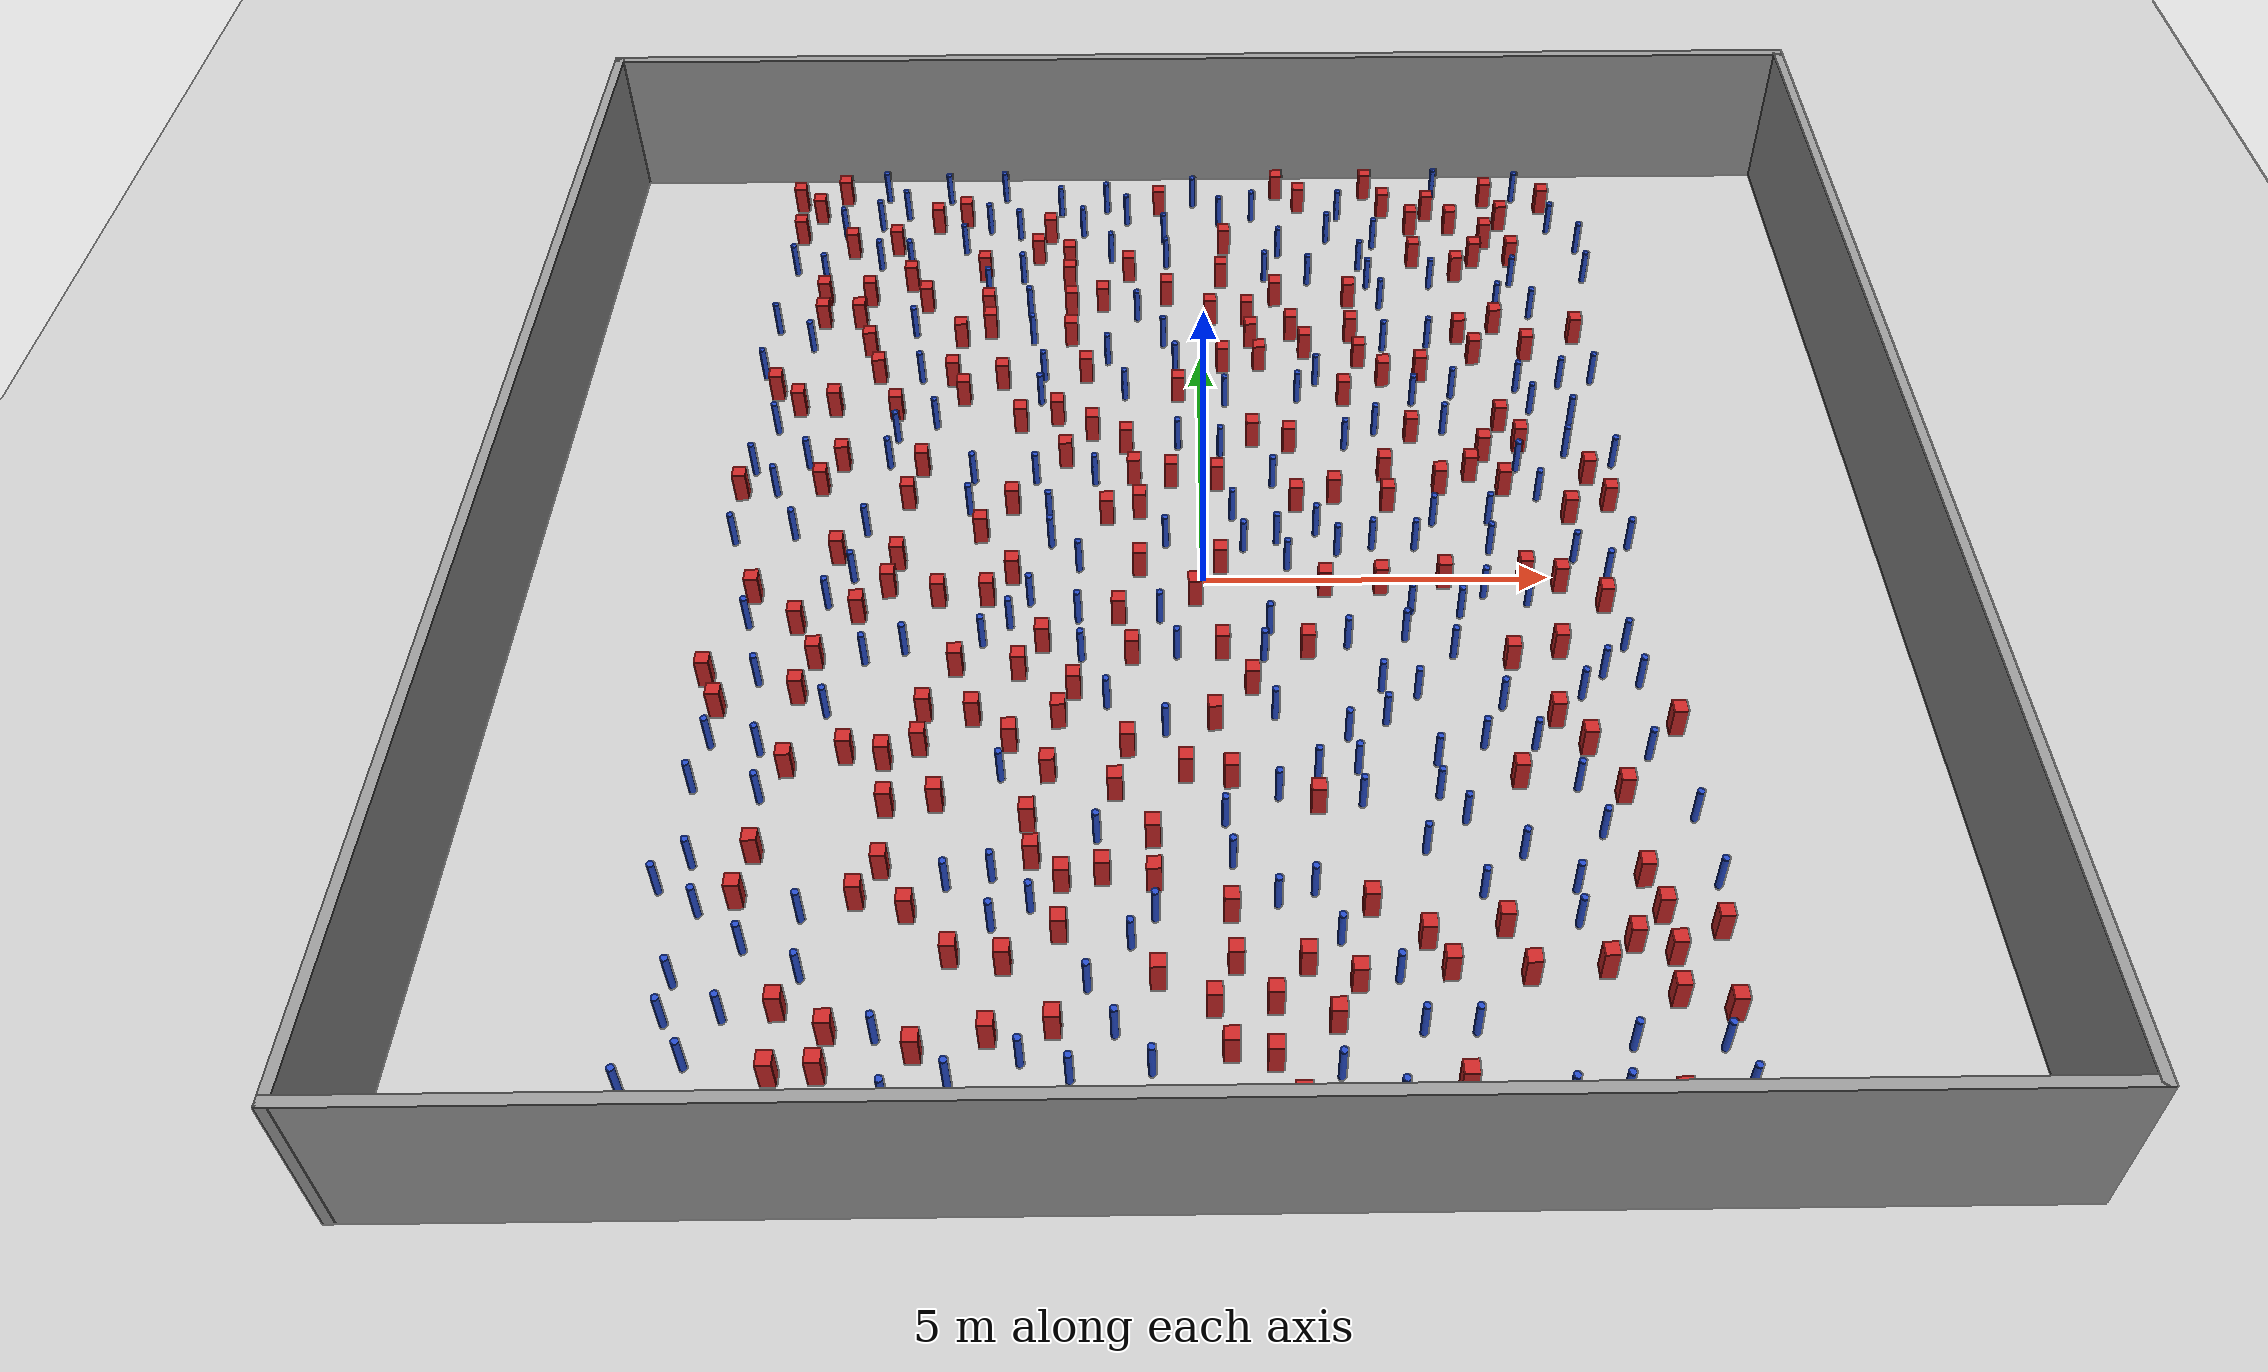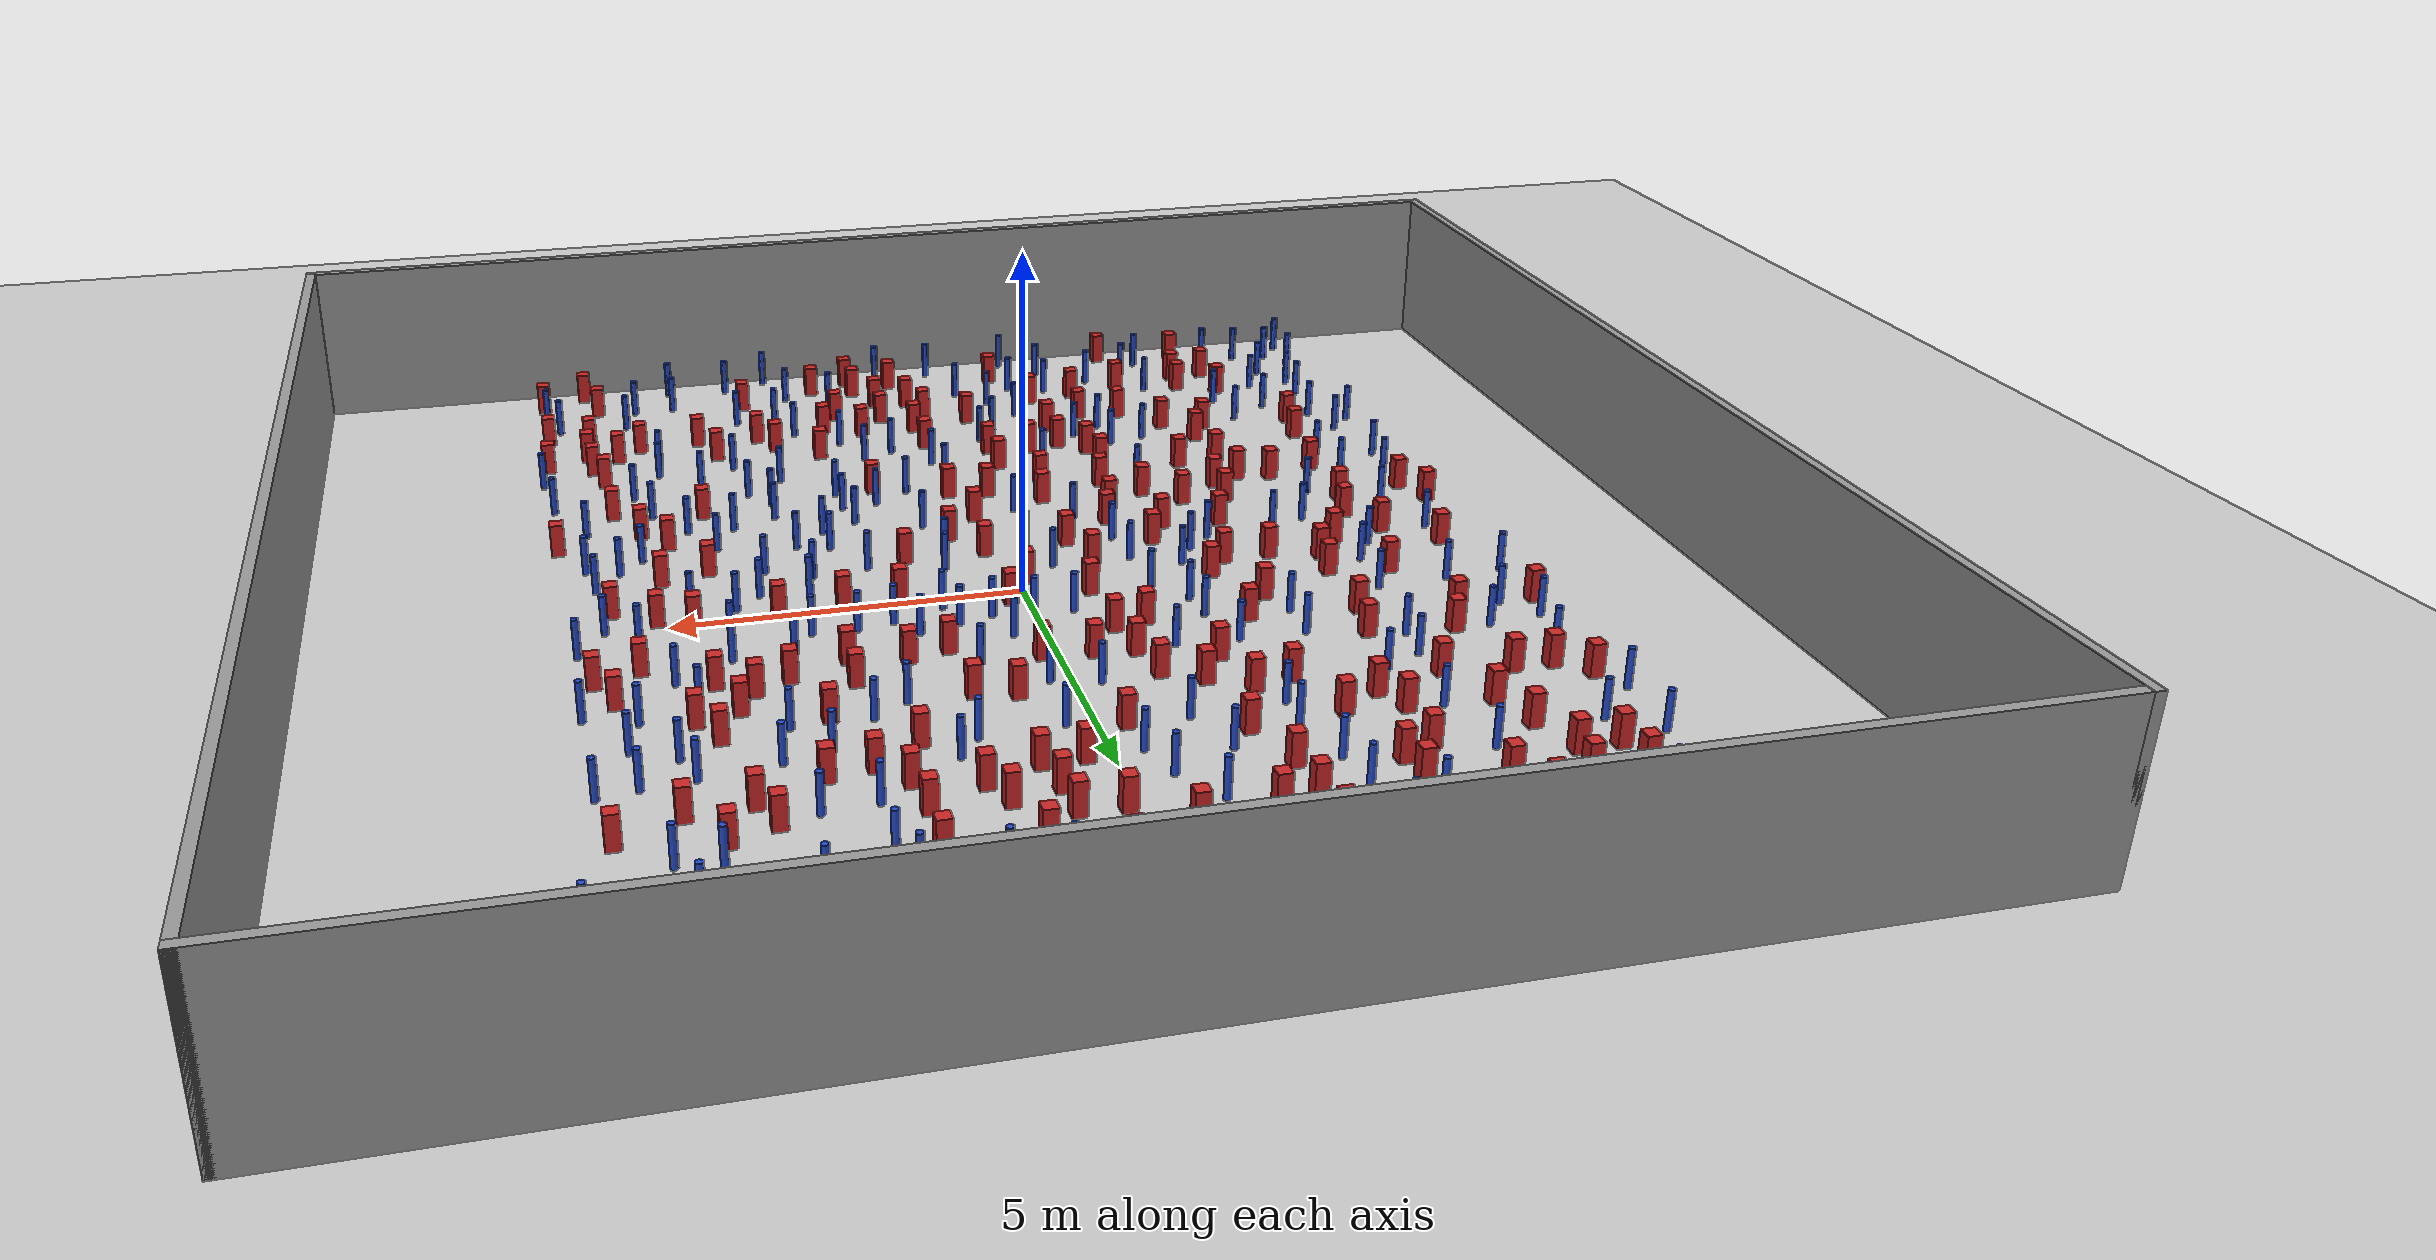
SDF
<sdf version="1.6">
 <world name="default">
  <light name="sun" type="directional">
   <pose>0 0 1000 0 -0 0</pose>
   <diffuse>0.8 0.8 0.8 1</diffuse>
   <specular>0.1 0.1 0.1 1</specular>
   <attenuation>
    <range>1000</range>
    <constant>0.9</constant>
    <linear>0.01</linear>
    <quadratic>0.001</quadratic>
   </attenuation>
   <direction>-0.5 0.5 -1</direction>
  </light>
  <model name="ground_plane">
   <static>1</static>
   <link name="link">
    <collision name="collision">
     <geometry><plane><normal>0 0 1</normal><size>100 100</size></plane></geometry>
     <surface><friction><ode><mu>100</mu><mu2>50</mu2></ode></friction></surface>
    </collision>
    <visual name="visual">
     <cast_shadows>0</cast_shadows>
     <geometry><plane><normal>0 0 1</normal><size>100 100</size></plane></geometry>
     <material>
      <ambient>1.0 1.0 1.0 1.0</ambient>
      <diffuse>0.8 0.8 0.8 1.0</diffuse>
      <specular>0.01 0.01 0.01 1.000000</specular>
     </material>
    </visual>
   </link>
  </model>
  <gravity>0 0 -9.8</gravity>
  <magnetic_field>6e-06 2.3e-05 -4.2e-05</magnetic_field>
  <atmosphere type="adiabatic"/>
  <physics name="default_physics" default="0" type="ode">
   <max_step_size>0.001</max_step_size>
   <real_time_factor>1</real_time_factor>
   <real_time_update_rate>1000</real_time_update_rate>
  </physics>
  <scene><ambient>0.4 0.4 0.4 1</ambient><background>0.7 0.7 0.7 1</background><shadows>1</shadows></scene>
  <spherical_coordinates>
   <surface_model>EARTH_WGS84</surface_model>
   <latitude_deg>0</latitude_deg>
   <longitude_deg>0</longitude_deg>
   <elevation>0</elevation>
   <heading_deg>0</heading_deg>
  </spherical_coordinates>
  <plugin name="gazebo_occupancy_map" filename="libgazebo_2Dmap_plugin.so">
   <map_resolution>0.05</map_resolution>
   <map_topic>generated_map</map_topic>
   <map_height>0.01</map_height>
   <map_size_x>50</map_size_x>
   <map_size_y>50</map_size_y>
  </plugin>
  <model name="NamedLocations">
   <static>true</static>
   <link name="DefaultStart"><pose>8.5 0 0 0 0 3.14</pose></link>
  </model>
  <model name="20x20_walls">
   <pose>0.044518 0.176112 0 0 -0 0</pose>
   <link name="Wall_1">
    <collision name="Wall_1_Collision">
     <geometry><box><size>20 0.15 2.5</size></box></geometry>
     <pose>0 0 1.25 0 -0 0</pose>
    </collision>
    <visual name="Wall_1_Visual">
     <pose>0 0 1.25 0 -0 0</pose>
     <geometry><box><size>20 0.15 2.5</size></box></geometry>
     <material>
      <script><uri>file://media/materials/scripts/gazebo.material</uri><name>Gazebo/Grey</name></script>
      <ambient>0.976471 0.992157 1 1</ambient>
     </material>
     <meta><layer>0</layer></meta>
    </visual>
    <pose>0 9.925 0 0 -0 0</pose>
   </link>
   <link name="Wall_3">
    <collision name="Wall_3_Collision">
     <geometry><box><size>20 0.15 2.5</size></box></geometry>
     <pose>0 0 1.25 0 -0 0</pose>
    </collision>
    <visual name="Wall_3_Visual">
     <pose>0 0 1.25 0 -0 0</pose>
     <geometry><box><size>20 0.15 2.5</size></box></geometry>
     <material>
      <script><uri>file://media/materials/scripts/gazebo.material</uri><name>Gazebo/Grey</name></script>
      <ambient>0.976471 0.992157 1 1</ambient>
     </material>
     <meta><layer>0</layer></meta>
    </visual>
    <pose>9.925 0 0 0 0 -1.5708</pose>
   </link>
   <link name="Wall_4">
    <collision name="Wall_4_Collision">
     <geometry><box><size>20 0.15 2.5</size></box></geometry>
     <pose>0 0 1.25 0 -0 0</pose>
    </collision>
    <visual name="Wall_4_Visual">
     <pose>0 0 1.25 0 -0 0</pose>
     <geometry><box><size>20 0.15 2.5</size></box></geometry>
     <material>
      <script><uri>file://media/materials/scripts/gazebo.material</uri><name>Gazebo/Grey</name></script>
      <ambient>0.976471 0.992157 1 1</ambient>
     </material>
     <meta><layer>0</layer></meta>
    </visual>
    <pose>0 -9.925 0 0 -0 3.14159</pose>
   </link>
   <link name="Wall_5">
    <collision name="Wall_5_Collision">
     <geometry><box><size>20 0.15 2.5</size></box></geometry>
     <pose>0 0 1.25 0 -0 0</pose>
    </collision>
    <visual name="Wall_5_Visual">
     <pose>0 0 1.25 0 -0 0</pose>
     <geometry><box><size>20 0.15 2.5</size></box></geometry>
     <material>
      <script><uri>file://media/materials/scripts/gazebo.material</uri><name>Gazebo/Grey</name></script>
      <ambient>0.976471 0.992157 1 1</ambient>
     </material>
     <meta><layer>0</layer></meta>
    </visual>
    <pose>-9.925 0 0 0 -0 1.5708</pose>
   </link>
   <static>1</static>
  </model>
  <model name="square_post_obstacle0">
   <static>true</static>
   <pose>-0.131067311828 -0.370867365495 1.91545236811e-07 -7.35059704564e-06 1.12565212e-07 2.39332434364e-05</pose>
   <link name="link">
    <pose>0 0 0.25 0 -0 0</pose>
    <inertial>
     <mass>100</mass>
     <inertia>
      <ixx>0.166667</ixx>
      <ixy>0</ixy>
      <ixz>0</ixz>
      <iyy>0.166667</iyy>
      <iyz>0</iyz>
      <izz>0.166667</izz>
     </inertia>
    </inertial>
    <collision name="collision"><geometry><box><size>.2 .2 .5</size></box></geometry></collision>
    <visual name="visual">
     <geometry><box><size>.2 .2 .5</size></box></geometry>
     <material>
      <script><name>Gazebo/Red</name><uri>file://media/materials/scripts/gazebo.material</uri></script>
     </material>
    </visual>
   </link>
  </model>
  <model name="square_post_obstacle1">
   <static>true</static>
   <pose>0.780798833853 2.99641068957 1.91545236811e-07 -7.35059704564e-06 1.12565212e-07 2.39332434364e-05</pose>
   <link name="link">
    <pose>0 0 0.25 0 -0 0</pose>
    <inertial>
     <mass>100</mass>
     <inertia>
      <ixx>0.166667</ixx>
      <ixy>0</ixy>
      <ixz>0</ixz>
      <iyy>0.166667</iyy>
      <iyz>0</iyz>
      <izz>0.166667</izz>
     </inertia>
    </inertial>
    <collision name="collision"><geometry><box><size>.2 .2 .5</size></box></geometry></collision>
    <visual name="visual">
     <geometry><box><size>.2 .2 .5</size></box></geometry>
     <material>
      <script><name>Gazebo/Red</name><uri>file://media/materials/scripts/gazebo.material</uri></script>
     </material>
    </visual>
   </link>
  </model>
  <model name="pole_obstacle0">
   <static>true</static>
   <pose>0.922099915082 -1.01157415732 7.38925637345e-09 -8.47170692799e-08 1.24976765037e-08 -1.74513093019e-07</pose>
   <link name="link">
    <pose>0 0 0.3 0 -0 0</pose>
    <inertial>
     <mass>1</mass>
     <inertia><ixx>0.145833</ixx><ixy>0</ixy><ixz>0</ixz><iyy>0.145833</iyy><iyz>0</iyz><izz>0.125</izz></inertia>
    </inertial>
    <collision name="collision">
     <geometry><cylinder><radius>0.05</radius><length>.6</length></cylinder></geometry>
    </collision>
    <visual name="visual">
     <geometry><cylinder><radius>0.05</radius><length>.6</length></cylinder></geometry>
     <material>
      <script><name>Gazebo/Blue</name><uri>file://media/materials/scripts/gazebo.material</uri></script>
     </material>
    </visual>
   </link>
  </model>
  <model name="square_post_obstacle2">
   <static>true</static>
   <pose>-2.08174777928 2.56492254605 1.91545236811e-07 -7.35059704564e-06 1.12565212e-07 2.39332434364e-05</pose>
   <link name="link">
    <pose>0 0 0.25 0 -0 0</pose>
    <inertial>
     <mass>100</mass>
     <inertia>
      <ixx>0.166667</ixx>
      <ixy>0</ixy>
      <ixz>0</ixz>
      <iyy>0.166667</iyy>
      <iyz>0</iyz>
      <izz>0.166667</izz>
     </inertia>
    </inertial>
    <collision name="collision"><geometry><box><size>.2 .2 .5</size></box></geometry></collision>
    <visual name="visual">
     <geometry><box><size>.2 .2 .5</size></box></geometry>
     <material>
      <script><name>Gazebo/Red</name><uri>file://media/materials/scripts/gazebo.material</uri></script>
     </material>
    </visual>
   </link>
  </model>
  <model name="pole_obstacle1">
   <static>true</static>
   <pose>-6.80756089151 -3.76116958803 7.38925637345e-09 -8.47170692798e-08 1.24976764937e-08 -1.74513093023e-07</pose>
   <link name="link">
    <pose>0 0 0.3 0 -0 0</pose>
    <inertial>
     <mass>1</mass>
     <inertia><ixx>0.145833</ixx><ixy>0</ixy><ixz>0</ixz><iyy>0.145833</iyy><iyz>0</iyz><izz>0.125</izz></inertia>
    </inertial>
    <collision name="collision">
     <geometry><cylinder><radius>0.05</radius><length>.6</length></cylinder></geometry>
    </collision>
    <visual name="visual">
     <geometry><cylinder><radius>0.05</radius><length>.6</length></cylinder></geometry>
     <material>
      <script><name>Gazebo/Blue</name><uri>file://media/materials/scripts/gazebo.material</uri></script>
     </material>
    </visual>
   </link>
  </model>
  <model name="square_post_obstacle3">
   <static>true</static>
   <pose>-0.633796371939 -6.8029401788 1.91545236811e-07 -7.35059704564e-06 1.12565212e-07 2.39332434364e-05</pose>
   <link name="link">
    <pose>0 0 0.25 0 -0 0</pose>
    <inertial>
     <mass>100</mass>
     <inertia>
      <ixx>0.166667</ixx>
      <ixy>0</ixy>
      <ixz>0</ixz>
      <iyy>0.166667</iyy>
      <iyz>0</iyz>
      <izz>0.166667</izz>
     </inertia>
    </inertial>
    <collision name="collision"><geometry><box><size>.2 .2 .5</size></box></geometry></collision>
    <visual name="visual">
     <geometry><box><size>.2 .2 .5</size></box></geometry>
     <material>
      <script><name>Gazebo/Red</name><uri>file://media/materials/scripts/gazebo.material</uri></script>
     </material>
    </visual>
   </link>
  </model>
  <model name="pole_obstacle2">
   <static>true</static>
   <pose>-6.47998227093 -0.821021741895 7.38925637345e-09 -8.47170692799e-08 1.24976765038e-08 -1.74513093018e-07</pose>
   <link name="link">
    <pose>0 0 0.3 0 -0 0</pose>
    <inertial>
     <mass>1</mass>
     <inertia><ixx>0.145833</ixx><ixy>0</ixy><ixz>0</ixz><iyy>0.145833</iyy><iyz>0</iyz><izz>0.125</izz></inertia>
    </inertial>
    <collision name="collision">
     <geometry><cylinder><radius>0.05</radius><length>.6</length></cylinder></geometry>
    </collision>
    <visual name="visual">
     <geometry><cylinder><radius>0.05</radius><length>.6</length></cylinder></geometry>
     <material>
      <script><name>Gazebo/Blue</name><uri>file://media/materials/scripts/gazebo.material</uri></script>
     </material>
    </visual>
   </link>
  </model>
  <model name="pole_obstacle3">
   <static>true</static>
   <pose>4.90822632352 -3.87171259141 7.38925637345e-09 -8.47170692798e-08 1.24976764937e-08 -1.74513093023e-07</pose>
   <link name="link">
    <pose>0 0 0.3 0 -0 0</pose>
    <inertial>
     <mass>1</mass>
     <inertia><ixx>0.145833</ixx><ixy>0</ixy><ixz>0</ixz><iyy>0.145833</iyy><iyz>0</iyz><izz>0.125</izz></inertia>
    </inertial>
    <collision name="collision">
     <geometry><cylinder><radius>0.05</radius><length>.6</length></cylinder></geometry>
    </collision>
    <visual name="visual">
     <geometry><cylinder><radius>0.05</radius><length>.6</length></cylinder></geometry>
     <material>
      <script><name>Gazebo/Blue</name><uri>file://media/materials/scripts/gazebo.material</uri></script>
     </material>
    </visual>
   </link>
  </model>
  <model name="square_post_obstacle4">
   <static>true</static>
   <pose>-2.18338594091 7.47727336232 1.91545236811e-07 -7.35059704564e-06 1.12565212e-07 2.39332434364e-05</pose>
   <link name="link">
    <pose>0 0 0.25 0 -0 0</pose>
    <inertial>
     <mass>100</mass>
     <inertia>
      <ixx>0.166667</ixx>
      <ixy>0</ixy>
      <ixz>0</ixz>
      <iyy>0.166667</iyy>
      <iyz>0</iyz>
      <izz>0.166667</izz>
     </inertia>
    </inertial>
    <collision name="collision"><geometry><box><size>.2 .2 .5</size></box></geometry></collision>
    <visual name="visual">
     <geometry><box><size>.2 .2 .5</size></box></geometry>
     <material>
      <script><name>Gazebo/Red</name><uri>file://media/materials/scripts/gazebo.material</uri></script>
     </material>
    </visual>
   </link>
  </model>
  <model name="square_post_obstacle5">
   <static>true</static>
   <pose>-2.09353412493 5.46867902602 1.91545236811e-07 -7.35059704564e-06 1.12565212e-07 2.39332434364e-05</pose>
   <link name="link">
    <pose>0 0 0.25 0 -0 0</pose>
    <inertial>
     <mass>100</mass>
     <inertia>
      <ixx>0.166667</ixx>
      <ixy>0</ixy>
      <ixz>0</ixz>
      <iyy>0.166667</iyy>
      <iyz>0</iyz>
      <izz>0.166667</izz>
     </inertia>
    </inertial>
    <collision name="collision"><geometry><box><size>.2 .2 .5</size></box></geometry></collision>
    <visual name="visual">
     <geometry><box><size>.2 .2 .5</size></box></geometry>
     <material>
      <script><name>Gazebo/Red</name><uri>file://media/materials/scripts/gazebo.material</uri></script>
     </material>
    </visual>
   </link>
  </model>
  <model name="square_post_obstacle6">
   <static>true</static>
   <pose>5.21742465756 8.51928732612 1.91545236811e-07 -7.35059704564e-06 1.12565212e-07 2.39332434364e-05</pose>
   <link name="link">
    <pose>0 0 0.25 0 -0 0</pose>
    <inertial>
     <mass>100</mass>
     <inertia>
      <ixx>0.166667</ixx>
      <ixy>0</ixy>
      <ixz>0</ixz>
      <iyy>0.166667</iyy>
      <iyz>0</iyz>
      <izz>0.166667</izz>
     </inertia>
    </inertial>
    <collision name="collision"><geometry><box><size>.2 .2 .5</size></box></geometry></collision>
    <visual name="visual">
     <geometry><box><size>.2 .2 .5</size></box></geometry>
     <material>
      <script><name>Gazebo/Red</name><uri>file://media/materials/scripts/gazebo.material</uri></script>
     </material>
    </visual>
   </link>
  </model>
  <model name="pole_obstacle4">
   <static>true</static>
   <pose>-2.73762525502 -3.61398638291 7.38925637345e-09 -8.47170692798e-08 1.24976764939e-08 -1.74513093025e-07</pose>
   <link name="link">
    <pose>0 0 0.3 0 -0 0</pose>
    <inertial>
     <mass>1</mass>
     <inertia><ixx>0.145833</ixx><ixy>0</ixy><ixz>0</ixz><iyy>0.145833</iyy><iyz>0</iyz><izz>0.125</izz></inertia>
    </inertial>
    <collision name="collision">
     <geometry><cylinder><radius>0.05</radius><length>.6</length></cylinder></geometry>
    </collision>
    <visual name="visual">
     <geometry><cylinder><radius>0.05</radius><length>.6</length></cylinder></geometry>
     <material>
      <script><name>Gazebo/Blue</name><uri>file://media/materials/scripts/gazebo.material</uri></script>
     </material>
    </visual>
   </link>
  </model>
  <model name="pole_obstacle5">
   <static>true</static>
   <pose>-0.392169649328 -1.46065777088 7.38925637345e-09 -8.47170692798e-08 1.24976765025e-08 -1.74513093018e-07</pose>
   <link name="link">
    <pose>0 0 0.3 0 -0 0</pose>
    <inertial>
     <mass>1</mass>
     <inertia><ixx>0.145833</ixx><ixy>0</ixy><ixz>0</ixz><iyy>0.145833</iyy><iyz>0</iyz><izz>0.125</izz></inertia>
    </inertial>
    <collision name="collision">
     <geometry><cylinder><radius>0.05</radius><length>.6</length></cylinder></geometry>
    </collision>
    <visual name="visual">
     <geometry><cylinder><radius>0.05</radius><length>.6</length></cylinder></geometry>
     <material>
      <script><name>Gazebo/Blue</name><uri>file://media/materials/scripts/gazebo.material</uri></script>
     </material>
    </visual>
   </link>
  </model>
  <model name="square_post_obstacle7">
   <static>true</static>
   <pose>-1.43258210814 -8.66387455334 1.91545236811e-07 -7.35059704564e-06 1.12565212e-07 2.39332434364e-05</pose>
   <link name="link">
    <pose>0 0 0.25 0 -0 0</pose>
    <inertial>
     <mass>100</mass>
     <inertia>
      <ixx>0.166667</ixx>
      <ixy>0</ixy>
      <ixz>0</ixz>
      <iyy>0.166667</iyy>
      <iyz>0</iyz>
      <izz>0.166667</izz>
     </inertia>
    </inertial>
    <collision name="collision"><geometry><box><size>.2 .2 .5</size></box></geometry></collision>
    <visual name="visual">
     <geometry><box><size>.2 .2 .5</size></box></geometry>
     <material>
      <script><name>Gazebo/Red</name><uri>file://media/materials/scripts/gazebo.material</uri></script>
     </material>
    </visual>
   </link>
  </model>
  <model name="square_post_obstacle8">
   <static>true</static>
   <pose>-2.53879268032 -6.56432131478 1.91545236811e-07 -7.35059704564e-06 1.12565212e-07 2.39332434364e-05</pose>
   <link name="link">
    <pose>0 0 0.25 0 -0 0</pose>
    <inertial>
     <mass>100</mass>
     <inertia>
      <ixx>0.166667</ixx>
      <ixy>0</ixy>
      <ixz>0</ixz>
      <iyy>0.166667</iyy>
      <iyz>0</iyz>
      <izz>0.166667</izz>
     </inertia>
    </inertial>
    <collision name="collision"><geometry><box><size>.2 .2 .5</size></box></geometry></collision>
    <visual name="visual">
     <geometry><box><size>.2 .2 .5</size></box></geometry>
     <material>
      <script><name>Gazebo/Red</name><uri>file://media/materials/scripts/gazebo.material</uri></script>
     </material>
    </visual>
   </link>
  </model>
  <model name="pole_obstacle6">
   <static>true</static>
   <pose>-6.56766878308 -6.76496728343 7.38925637345e-09 -8.47170692796e-08 1.24976764786e-08 -1.74513093032e-07</pose>
   <link name="link">
    <pose>0 0 0.3 0 -0 0</pose>
    <inertial>
     <mass>1</mass>
     <inertia><ixx>0.145833</ixx><ixy>0</ixy><ixz>0</ixz><iyy>0.145833</iyy><iyz>0</iyz><izz>0.125</izz></inertia>
    </inertial>
    <collision name="collision">
     <geometry><cylinder><radius>0.05</radius><length>.6</length></cylinder></geometry>
    </collision>
    <visual name="visual">
     <geometry><cylinder><radius>0.05</radius><length>.6</length></cylinder></geometry>
     <material>
      <script><name>Gazebo/Blue</name><uri>file://media/materials/scripts/gazebo.material</uri></script>
     </material>
    </visual>
   </link>
  </model>
  <model name="pole_obstacle7">
   <static>true</static>
   <pose>0.0157294788406 0.745171208726 7.38925637345e-09 -8.47170692798e-08 1.2497676491e-08 -1.74513093025e-07</pose>
   <link name="link">
    <pose>0 0 0.3 0 -0 0</pose>
    <inertial>
     <mass>1</mass>
     <inertia><ixx>0.145833</ixx><ixy>0</ixy><ixz>0</ixz><iyy>0.145833</iyy><iyz>0</iyz><izz>0.125</izz></inertia>
    </inertial>
    <collision name="collision">
     <geometry><cylinder><radius>0.05</radius><length>.6</length></cylinder></geometry>
    </collision>
    <visual name="visual">
     <geometry><cylinder><radius>0.05</radius><length>.6</length></cylinder></geometry>
     <material>
      <script><name>Gazebo/Blue</name><uri>file://media/materials/scripts/gazebo.material</uri></script>
     </material>
    </visual>
   </link>
  </model>
  <model name="square_post_obstacle9">
   <static>true</static>
   <pose>-1.21947645181 -0.743235990267 1.91545236811e-07 -7.35059704564e-06 1.12565212e-07 2.39332434364e-05</pose>
   <link name="link">
    <pose>0 0 0.25 0 -0 0</pose>
    <inertial>
     <mass>100</mass>
     <inertia>
      <ixx>0.166667</ixx>
      <ixy>0</ixy>
      <ixz>0</ixz>
      <iyy>0.166667</iyy>
      <iyz>0</iyz>
      <izz>0.166667</izz>
     </inertia>
    </inertial>
    <collision name="collision"><geometry><box><size>.2 .2 .5</size></box></geometry></collision>
    <visual name="visual">
     <geometry><box><size>.2 .2 .5</size></box></geometry>
     <material>
      <script><name>Gazebo/Red</name><uri>file://media/materials/scripts/gazebo.material</uri></script>
     </material>
    </visual>
   </link>
  </model>
  <model name="square_post_obstacle10">
   <static>true</static>
   <pose>-5.75109295996 3.78641917231 1.91545236811e-07 -7.35059704564e-06 1.12565212e-07 2.39332434364e-05</pose>
   <link name="link">
    <pose>0 0 0.25 0 -0 0</pose>
    <inertial>
     <mass>100</mass>
     <inertia>
      <ixx>0.166667</ixx>
      <ixy>0</ixy>
      <ixz>0</ixz>
      <iyy>0.166667</iyy>
      <iyz>0</iyz>
      <izz>0.166667</izz>
     </inertia>
    </inertial>
    <collision name="collision"><geometry><box><size>.2 .2 .5</size></box></geometry></collision>
    <visual name="visual">
     <geometry><box><size>.2 .2 .5</size></box></geometry>
     <material>
      <script><name>Gazebo/Red</name><uri>file://media/materials/scripts/gazebo.material</uri></script>
     </material>
    </visual>
   </link>
  </model>
  <model name="square_post_obstacle11">
   <static>true</static>
   <pose>4.64751890124 -0.0145843861051 1.91545236811e-07 -7.35059704564e-06 1.12565212e-07 2.39332434364e-05</pose>
   <link name="link">
    <pose>0 0 0.25 0 -0 0</pose>
    <inertial>
     <mass>100</mass>
     <inertia>
      <ixx>0.166667</ixx>
      <ixy>0</ixy>
      <ixz>0</ixz>
      <iyy>0.166667</iyy>
      <iyz>0</iyz>
      <izz>0.166667</izz>
     </inertia>
    </inertial>
    <collision name="collision"><geometry><box><size>.2 .2 .5</size></box></geometry></collision>
    <visual name="visual">
     <geometry><box><size>.2 .2 .5</size></box></geometry>
     <material>
      <script><name>Gazebo/Red</name><uri>file://media/materials/scripts/gazebo.material</uri></script>
     </material>
    </visual>
   </link>
  </model>
  <model name="square_post_obstacle12">
   <static>true</static>
   <pose>-2.58703024874 -1.78188464464 1.91545236811e-07 -7.35059704564e-06 1.12565212e-07 2.39332434364e-05</pose>
   <link name="link">
    <pose>0 0 0.25 0 -0 0</pose>
    <inertial>
     <mass>100</mass>
     <inertia>
      <ixx>0.166667</ixx>
      <ixy>0</ixy>
      <ixz>0</ixz>
      <iyy>0.166667</iyy>
      <iyz>0</iyz>
      <izz>0.166667</izz>
     </inertia>
    </inertial>
    <collision name="collision"><geometry><box><size>.2 .2 .5</size></box></geometry></collision>
    <visual name="visual">
     <geometry><box><size>.2 .2 .5</size></box></geometry>
     <material>
      <script><name>Gazebo/Red</name><uri>file://media/materials/scripts/gazebo.material</uri></script>
     </material>
    </visual>
   </link>
  </model>
  <model name="square_post_obstacle13">
   <static>true</static>
   <pose>-0.931883444278 0.211325929328 1.91545236811e-07 -7.35059704564e-06 1.12565212e-07 2.39332434364e-05</pose>
   <link name="link">
    <pose>0 0 0.25 0 -0 0</pose>
    <inertial>
     <mass>100</mass>
     <inertia>
      <ixx>0.166667</ixx>
      <ixy>0</ixy>
      <ixz>0</ixz>
      <iyy>0.166667</iyy>
      <iyz>0</iyz>
      <izz>0.166667</izz>
     </inertia>
    </inertial>
    <collision name="collision"><geometry><box><size>.2 .2 .5</size></box></geometry></collision>
    <visual name="visual">
     <geometry><box><size>.2 .2 .5</size></box></geometry>
     <material>
      <script><name>Gazebo/Red</name><uri>file://media/materials/scripts/gazebo.material</uri></script>
     </material>
    </visual>
   </link>
  </model>
  <model name="pole_obstacle8">
   <static>true</static>
   <pose>5.52795941858 -1.89979225202 7.38925637345e-09 -8.471706928e-08 1.24976765134e-08 -1.74513093015e-07</pose>
   <link name="link">
    <pose>0 0 0.3 0 -0 0</pose>
    <inertial>
     <mass>1</mass>
     <inertia><ixx>0.145833</ixx><ixy>0</ixy><ixz>0</ixz><iyy>0.145833</iyy><iyz>0</iyz><izz>0.125</izz></inertia>
    </inertial>
    <collision name="collision">
     <geometry><cylinder><radius>0.05</radius><length>.6</length></cylinder></geometry>
    </collision>
    <visual name="visual">
     <geometry><cylinder><radius>0.05</radius><length>.6</length></cylinder></geometry>
     <material>
      <script><name>Gazebo/Blue</name><uri>file://media/materials/scripts/gazebo.material</uri></script>
     </material>
    </visual>
   </link>
  </model>
  <model name="square_post_obstacle14">
   <static>true</static>
   <pose>-2.67159025851 -7.58281791326 1.91545236811e-07 -7.35059704564e-06 1.12565212e-07 2.39332434364e-05</pose>
   <link name="link">
    <pose>0 0 0.25 0 -0 0</pose>
    <inertial>
     <mass>100</mass>
     <inertia>
      <ixx>0.166667</ixx>
      <ixy>0</ixy>
      <ixz>0</ixz>
      <iyy>0.166667</iyy>
      <iyz>0</iyz>
      <izz>0.166667</izz>
     </inertia>
    </inertial>
    <collision name="collision"><geometry><box><size>.2 .2 .5</size></box></geometry></collision>
    <visual name="visual">
     <geometry><box><size>.2 .2 .5</size></box></geometry>
     <material>
      <script><name>Gazebo/Red</name><uri>file://media/materials/scripts/gazebo.material</uri></script>
     </material>
    </visual>
   </link>
  </model>
  <model name="square_post_obstacle15">
   <static>true</static>
   <pose>-5.23057087087 -7.19121798113 1.91545236811e-07 -7.35059704564e-06 1.12565212e-07 2.39332434364e-05</pose>
   <link name="link">
    <pose>0 0 0.25 0 -0 0</pose>
    <inertial>
     <mass>100</mass>
     <inertia>
      <ixx>0.166667</ixx>
      <ixy>0</ixy>
      <ixz>0</ixz>
      <iyy>0.166667</iyy>
      <iyz>0</iyz>
      <izz>0.166667</izz>
     </inertia>
    </inertial>
    <collision name="collision"><geometry><box><size>.2 .2 .5</size></box></geometry></collision>
    <visual name="visual">
     <geometry><box><size>.2 .2 .5</size></box></geometry>
     <material>
      <script><name>Gazebo/Red</name><uri>file://media/materials/scripts/gazebo.material</uri></script>
     </material>
    </visual>
   </link>
  </model>
  <model name="square_post_obstacle16">
   <static>true</static>
   <pose>-3.61521142471 -9.28834033057 1.91545236811e-07 -7.35059704564e-06 1.12565212e-07 2.39332434364e-05</pose>
   <link name="link">
    <pose>0 0 0.25 0 -0 0</pose>
    <inertial>
     <mass>100</mass>
     <inertia>
      <ixx>0.166667</ixx>
      <ixy>0</ixy>
      <ixz>0</ixz>
      <iyy>0.166667</iyy>
      <iyz>0</iyz>
      <izz>0.166667</izz>
     </inertia>
    </inertial>
    <collision name="collision"><geometry><box><size>.2 .2 .5</size></box></geometry></collision>
    <visual name="visual">
     <geometry><box><size>.2 .2 .5</size></box></geometry>
     <material>
      <script><name>Gazebo/Red</name><uri>file://media/materials/scripts/gazebo.material</uri></script>
     </material>
    </visual>
   </link>
  </model>
  <model name="pole_obstacle9">
   <static>true</static>
   <pose>5.45266058337 6.02277866107 7.38925637345e-09 -8.47170692796e-08 1.24976764786e-08 -1.74513093032e-07</pose>
   <link name="link">
    <pose>0 0 0.3 0 -0 0</pose>
    <inertial>
     <mass>1</mass>
     <inertia><ixx>0.145833</ixx><ixy>0</ixy><ixz>0</ixz><iyy>0.145833</iyy><iyz>0</iyz><izz>0.125</izz></inertia>
    </inertial>
    <collision name="collision">
     <geometry><cylinder><radius>0.05</radius><length>.6</length></cylinder></geometry>
    </collision>
    <visual name="visual">
     <geometry><cylinder><radius>0.05</radius><length>.6</length></cylinder></geometry>
     <material>
      <script><name>Gazebo/Blue</name><uri>file://media/materials/scripts/gazebo.material</uri></script>
     </material>
    </visual>
   </link>
  </model>
  <model name="square_post_obstacle17">
   <static>true</static>
   <pose>0.378305085071 -8.76689571817 1.91545236811e-07 -7.35059704564e-06 1.12565212e-07 2.39332434364e-05</pose>
   <link name="link">
    <pose>0 0 0.25 0 -0 0</pose>
    <inertial>
     <mass>100</mass>
     <inertia>
      <ixx>0.166667</ixx>
      <ixy>0</ixy>
      <ixz>0</ixz>
      <iyy>0.166667</iyy>
      <iyz>0</iyz>
      <izz>0.166667</izz>
     </inertia>
    </inertial>
    <collision name="collision"><geometry><box><size>.2 .2 .5</size></box></geometry></collision>
    <visual name="visual">
     <geometry><box><size>.2 .2 .5</size></box></geometry>
     <material>
      <script><name>Gazebo/Red</name><uri>file://media/materials/scripts/gazebo.material</uri></script>
     </material>
    </visual>
   </link>
  </model>
  <model name="square_post_obstacle18">
   <static>true</static>
   <pose>1.75431721817 -8.75832268951 1.91545236811e-07 -7.35059704564e-06 1.12565212e-07 2.39332434364e-05</pose>
   <link name="link">
    <pose>0 0 0.25 0 -0 0</pose>
    <inertial>
     <mass>100</mass>
     <inertia>
      <ixx>0.166667</ixx>
      <ixy>0</ixy>
      <ixz>0</ixz>
      <iyy>0.166667</iyy>
      <iyz>0</iyz>
      <izz>0.166667</izz>
     </inertia>
    </inertial>
    <collision name="collision"><geometry><box><size>.2 .2 .5</size></box></geometry></collision>
    <visual name="visual">
     <geometry><box><size>.2 .2 .5</size></box></geometry>
     <material>
      <script><name>Gazebo/Red</name><uri>file://media/materials/scripts/gazebo.material</uri></script>
     </material>
    </visual>
   </link>
  </model>
  <model name="pole_obstacle10">
   <static>true</static>
   <pose>-6.82636018263 2.38603952285 7.38925637345e-09 -8.47170692798e-08 1.24976764937e-08 -1.74513093023e-07</pose>
   <link name="link">
    <pose>0 0 0.3 0 -0 0</pose>
    <inertial>
     <mass>1</mass>
     <inertia><ixx>0.145833</ixx><ixy>0</ixy><ixz>0</ixz><iyy>0.145833</iyy><iyz>0</iyz><izz>0.125</izz></inertia>
    </inertial>
    <collision name="collision">
     <geometry><cylinder><radius>0.05</radius><length>.6</length></cylinder></geometry>
    </collision>
    <visual name="visual">
     <geometry><cylinder><radius>0.05</radius><length>.6</length></cylinder></geometry>
     <material>
      <script><name>Gazebo/Blue</name><uri>file://media/materials/scripts/gazebo.material</uri></script>
     </material>
    </visual>
   </link>
  </model>
  <model name="square_post_obstacle19">
   <static>true</static>
   <pose>1.24587258666 6.46991391476 1.91545236811e-07 -7.35059704564e-06 1.12565212e-07 2.39332434364e-05</pose>
   <link name="link">
    <pose>0 0 0.25 0 -0 0</pose>
    <inertial>
     <mass>100</mass>
     <inertia>
      <ixx>0.166667</ixx>
      <ixy>0</ixy>
      <ixz>0</ixz>
      <iyy>0.166667</iyy>
      <iyz>0</iyz>
      <izz>0.166667</izz>
     </inertia>
    </inertial>
    <collision name="collision"><geometry><box><size>.2 .2 .5</size></box></geometry></collision>
    <visual name="visual">
     <geometry><box><size>.2 .2 .5</size></box></geometry>
     <material>
      <script><name>Gazebo/Red</name><uri>file://media/materials/scripts/gazebo.material</uri></script>
     </material>
    </visual>
   </link>
  </model>
  <model name="pole_obstacle11">
   <static>true</static>
   <pose>6.04920559526 8.37096371411 7.38925637345e-09 -8.471706928e-08 1.24976765081e-08 -1.74513093015e-07</pose>
   <link name="link">
    <pose>0 0 0.3 0 -0 0</pose>
    <inertial>
     <mass>1</mass>
     <inertia><ixx>0.145833</ixx><ixy>0</ixy><ixz>0</ixz><iyy>0.145833</iyy><iyz>0</iyz><izz>0.125</izz></inertia>
    </inertial>
    <collision name="collision">
     <geometry><cylinder><radius>0.05</radius><length>.6</length></cylinder></geometry>
    </collision>
    <visual name="visual">
     <geometry><cylinder><radius>0.05</radius><length>.6</length></cylinder></geometry>
     <material>
      <script><name>Gazebo/Blue</name><uri>file://media/materials/scripts/gazebo.material</uri></script>
     </material>
    </visual>
   </link>
  </model>
  <model name="square_post_obstacle20">
   <static>true</static>
   <pose>1.10523010317 -9.08272756877 1.91545236811e-07 -7.35059704564e-06 1.12565212e-07 2.39332434364e-05</pose>
   <link name="link">
    <pose>0 0 0.25 0 -0 0</pose>
    <inertial>
     <mass>100</mass>
     <inertia>
      <ixx>0.166667</ixx>
      <ixy>0</ixy>
      <ixz>0</ixz>
      <iyy>0.166667</iyy>
      <iyz>0</iyz>
      <izz>0.166667</izz>
     </inertia>
    </inertial>
    <collision name="collision"><geometry><box><size>.2 .2 .5</size></box></geometry></collision>
    <visual name="visual">
     <geometry><box><size>.2 .2 .5</size></box></geometry>
     <material>
      <script><name>Gazebo/Red</name><uri>file://media/materials/scripts/gazebo.material</uri></script>
     </material>
    </visual>
   </link>
  </model>
  <model name="pole_obstacle12">
   <static>true</static>
   <pose>5.12868795142 -4.64596688492 7.38925637345e-09 -8.47170692796e-08 1.24976764786e-08 -1.74513093032e-07</pose>
   <link name="link">
    <pose>0 0 0.3 0 -0 0</pose>
    <inertial>
     <mass>1</mass>
     <inertia><ixx>0.145833</ixx><ixy>0</ixy><ixz>0</ixz><iyy>0.145833</iyy><iyz>0</iyz><izz>0.125</izz></inertia>
    </inertial>
    <collision name="collision">
     <geometry><cylinder><radius>0.05</radius><length>.6</length></cylinder></geometry>
    </collision>
    <visual name="visual">
     <geometry><cylinder><radius>0.05</radius><length>.6</length></cylinder></geometry>
     <material>
      <script><name>Gazebo/Blue</name><uri>file://media/materials/scripts/gazebo.material</uri></script>
     </material>
    </visual>
   </link>
  </model>
  <model name="square_post_obstacle21">
   <static>true</static>
   <pose>-1.2114949215 -3.89580348201 1.91545236811e-07 -7.35059704564e-06 1.12565212e-07 2.39332434364e-05</pose>
   <link name="link">
    <pose>0 0 0.25 0 -0 0</pose>
    <inertial>
     <mass>100</mass>
     <inertia>
      <ixx>0.166667</ixx>
      <ixy>0</ixy>
      <ixz>0</ixz>
      <iyy>0.166667</iyy>
      <iyz>0</iyz>
      <izz>0.166667</izz>
     </inertia>
    </inertial>
    <collision name="collision"><geometry><box><size>.2 .2 .5</size></box></geometry></collision>
    <visual name="visual">
     <geometry><box><size>.2 .2 .5</size></box></geometry>
     <material>
      <script><name>Gazebo/Red</name><uri>file://media/materials/scripts/gazebo.material</uri></script>
     </material>
    </visual>
   </link>
  </model>
  <model name="pole_obstacle13">
   <static>true</static>
   <pose>2.98266285605 7.96069284525 7.38925637345e-09 -8.47170692799e-08 1.24976765031e-08 -1.7451309302e-07</pose>
   <link name="link">
    <pose>0 0 0.3 0 -0 0</pose>
    <inertial>
     <mass>1</mass>
     <inertia><ixx>0.145833</ixx><ixy>0</ixy><ixz>0</ixz><iyy>0.145833</iyy><iyz>0</iyz><izz>0.125</izz></inertia>
    </inertial>
    <collision name="collision">
     <geometry><cylinder><radius>0.05</radius><length>.6</length></cylinder></geometry>
    </collision>
    <visual name="visual">
     <geometry><cylinder><radius>0.05</radius><length>.6</length></cylinder></geometry>
     <material>
      <script><name>Gazebo/Blue</name><uri>file://media/materials/scripts/gazebo.material</uri></script>
     </material>
    </visual>
   </link>
  </model>
  <model name="square_post_obstacle22">
   <static>true</static>
   <pose>-4.64862744228 -8.05214864255 1.91545236811e-07 -7.35059704564e-06 1.12565212e-07 2.39332434364e-05</pose>
   <link name="link">
    <pose>0 0 0.25 0 -0 0</pose>
    <inertial>
     <mass>100</mass>
     <inertia>
      <ixx>0.166667</ixx>
      <ixy>0</ixy>
      <ixz>0</ixz>
      <iyy>0.166667</iyy>
      <iyz>0</iyz>
      <izz>0.166667</izz>
     </inertia>
    </inertial>
    <collision name="collision"><geometry><box><size>.2 .2 .5</size></box></geometry></collision>
    <visual name="visual">
     <geometry><box><size>.2 .2 .5</size></box></geometry>
     <material>
      <script><name>Gazebo/Red</name><uri>file://media/materials/scripts/gazebo.material</uri></script>
     </material>
    </visual>
   </link>
  </model>
  <model name="pole_obstacle14">
   <static>true</static>
   <pose>-5.02337090327 -6.70248612856 7.38925637345e-09 -8.47170692796e-08 1.24976764786e-08 -1.74513093032e-07</pose>
   <link name="link">
    <pose>0 0 0.3 0 -0 0</pose>
    <inertial>
     <mass>1</mass>
     <inertia><ixx>0.145833</ixx><ixy>0</ixy><ixz>0</ixz><iyy>0.145833</iyy><iyz>0</iyz><izz>0.125</izz></inertia>
    </inertial>
    <collision name="collision">
     <geometry><cylinder><radius>0.05</radius><length>.6</length></cylinder></geometry>
    </collision>
    <visual name="visual">
     <geometry><cylinder><radius>0.05</radius><length>.6</length></cylinder></geometry>
     <material>
      <script><name>Gazebo/Blue</name><uri>file://media/materials/scripts/gazebo.material</uri></script>
     </material>
    </visual>
   </link>
  </model>
  <model name="pole_obstacle15">
   <static>true</static>
   <pose>1.82468125279 4.37478606143 7.38925637345e-09 -8.47170692799e-08 1.24976765033e-08 -1.74513093018e-07</pose>
   <link name="link">
    <pose>0 0 0.3 0 -0 0</pose>
    <inertial>
     <mass>1</mass>
     <inertia><ixx>0.145833</ixx><ixy>0</ixy><ixz>0</ixz><iyy>0.145833</iyy><iyz>0</iyz><izz>0.125</izz></inertia>
    </inertial>
    <collision name="collision">
     <geometry><cylinder><radius>0.05</radius><length>.6</length></cylinder></geometry>
    </collision>
    <visual name="visual">
     <geometry><cylinder><radius>0.05</radius><length>.6</length></cylinder></geometry>
     <material>
      <script><name>Gazebo/Blue</name><uri>file://media/materials/scripts/gazebo.material</uri></script>
     </material>
    </visual>
   </link>
  </model>
  <model name="pole_obstacle16">
   <static>true</static>
   <pose>-6.42377104074 -5.73415301805 7.38925637345e-09 -8.47170692796e-08 1.24976764786e-08 -1.74513093032e-07</pose>
   <link name="link">
    <pose>0 0 0.3 0 -0 0</pose>
    <inertial>
     <mass>1</mass>
     <inertia><ixx>0.145833</ixx><ixy>0</ixy><ixz>0</ixz><iyy>0.145833</iyy><iyz>0</iyz><izz>0.125</izz></inertia>
    </inertial>
    <collision name="collision">
     <geometry><cylinder><radius>0.05</radius><length>.6</length></cylinder></geometry>
    </collision>
    <visual name="visual">
     <geometry><cylinder><radius>0.05</radius><length>.6</length></cylinder></geometry>
     <material>
      <script><name>Gazebo/Blue</name><uri>file://media/materials/scripts/gazebo.material</uri></script>
     </material>
    </visual>
   </link>
  </model>
  <model name="square_post_obstacle23">
   <static>true</static>
   <pose>1.97175608762 1.70010967402 1.91545236811e-07 -7.35059704564e-06 1.12565212e-07 2.39332434364e-05</pose>
   <link name="link">
    <pose>0 0 0.25 0 -0 0</pose>
    <inertial>
     <mass>100</mass>
     <inertia>
      <ixx>0.166667</ixx>
      <ixy>0</ixy>
      <ixz>0</ixz>
      <iyy>0.166667</iyy>
      <iyz>0</iyz>
      <izz>0.166667</izz>
     </inertia>
    </inertial>
    <collision name="collision"><geometry><box><size>.2 .2 .5</size></box></geometry></collision>
    <visual name="visual">
     <geometry><box><size>.2 .2 .5</size></box></geometry>
     <material>
      <script><name>Gazebo/Red</name><uri>file://media/materials/scripts/gazebo.material</uri></script>
     </material>
    </visual>
   </link>
  </model>
  <model name="pole_obstacle17">
   <static>true</static>
   <pose>2.55404424358 -7.53747133747 7.38925637345e-09 -8.47170692798e-08 1.24976765033e-08 -1.74513093019e-07</pose>
   <link name="link">
    <pose>0 0 0.3 0 -0 0</pose>
    <inertial>
     <mass>1</mass>
     <inertia><ixx>0.145833</ixx><ixy>0</ixy><ixz>0</ixz><iyy>0.145833</iyy><iyz>0</iyz><izz>0.125</izz></inertia>
    </inertial>
    <collision name="collision">
     <geometry><cylinder><radius>0.05</radius><length>.6</length></cylinder></geometry>
    </collision>
    <visual name="visual">
     <geometry><cylinder><radius>0.05</radius><length>.6</length></cylinder></geometry>
     <material>
      <script><name>Gazebo/Blue</name><uri>file://media/materials/scripts/gazebo.material</uri></script>
     </material>
    </visual>
   </link>
  </model>
  <model name="square_post_obstacle24">
   <static>true</static>
   <pose>2.54639958451 -0.183967553714 1.91545236811e-07 -7.35059704564e-06 1.12565212e-07 2.39332434364e-05</pose>
   <link name="link">
    <pose>0 0 0.25 0 -0 0</pose>
    <inertial>
     <mass>100</mass>
     <inertia>
      <ixx>0.166667</ixx>
      <ixy>0</ixy>
      <ixz>0</ixz>
      <iyy>0.166667</iyy>
      <iyz>0</iyz>
      <izz>0.166667</izz>
     </inertia>
    </inertial>
    <collision name="collision"><geometry><box><size>.2 .2 .5</size></box></geometry></collision>
    <visual name="visual">
     <geometry><box><size>.2 .2 .5</size></box></geometry>
     <material>
      <script><name>Gazebo/Red</name><uri>file://media/materials/scripts/gazebo.material</uri></script>
     </material>
    </visual>
   </link>
  </model>
  <model name="square_post_obstacle25">
   <static>true</static>
   <pose>-5.48884879963 2.51707983936 1.91545236811e-07 -7.35059704564e-06 1.12565212e-07 2.39332434364e-05</pose>
   <link name="link">
    <pose>0 0 0.25 0 -0 0</pose>
    <inertial>
     <mass>100</mass>
     <inertia>
      <ixx>0.166667</ixx>
      <ixy>0</ixy>
      <ixz>0</ixz>
      <iyy>0.166667</iyy>
      <iyz>0</iyz>
      <izz>0.166667</izz>
     </inertia>
    </inertial>
    <collision name="collision"><geometry><box><size>.2 .2 .5</size></box></geometry></collision>
    <visual name="visual">
     <geometry><box><size>.2 .2 .5</size></box></geometry>
     <material>
      <script><name>Gazebo/Red</name><uri>file://media/materials/scripts/gazebo.material</uri></script>
     </material>
    </visual>
   </link>
  </model>
  <model name="square_post_obstacle26">
   <static>true</static>
   <pose>-3.74213483056 4.00811661276 1.91545236811e-07 -7.35059704564e-06 1.12565212e-07 2.39332434364e-05</pose>
   <link name="link">
    <pose>0 0 0.25 0 -0 0</pose>
    <inertial>
     <mass>100</mass>
     <inertia>
      <ixx>0.166667</ixx>
      <ixy>0</ixy>
      <ixz>0</ixz>
      <iyy>0.166667</iyy>
      <iyz>0</iyz>
      <izz>0.166667</izz>
     </inertia>
    </inertial>
    <collision name="collision"><geometry><box><size>.2 .2 .5</size></box></geometry></collision>
    <visual name="visual">
     <geometry><box><size>.2 .2 .5</size></box></geometry>
     <material>
      <script><name>Gazebo/Red</name><uri>file://media/materials/scripts/gazebo.material</uri></script>
     </material>
    </visual>
   </link>
  </model>
  <model name="square_post_obstacle27">
   <static>true</static>
   <pose>0.645448570369 -2.06766845561 1.91545236811e-07 -7.35059704564e-06 1.12565212e-07 2.39332434364e-05</pose>
   <link name="link">
    <pose>0 0 0.25 0 -0 0</pose>
    <inertial>
     <mass>100</mass>
     <inertia>
      <ixx>0.166667</ixx>
      <ixy>0</ixy>
      <ixz>0</ixz>
      <iyy>0.166667</iyy>
      <iyz>0</iyz>
      <izz>0.166667</izz>
     </inertia>
    </inertial>
    <collision name="collision"><geometry><box><size>.2 .2 .5</size></box></geometry></collision>
    <visual name="visual">
     <geometry><box><size>.2 .2 .5</size></box></geometry>
     <material>
      <script><name>Gazebo/Red</name><uri>file://media/materials/scripts/gazebo.material</uri></script>
     </material>
    </visual>
   </link>
  </model>
  <model name="pole_obstacle18">
   <static>true</static>
   <pose>-2.72735987007 -5.99257990961 7.38925637345e-09 -8.47170692798e-08 1.24976765033e-08 -1.74513093019e-07</pose>
   <link name="link">
    <pose>0 0 0.3 0 -0 0</pose>
    <inertial>
     <mass>1</mass>
     <inertia><ixx>0.145833</ixx><ixy>0</ixy><ixz>0</ixz><iyy>0.145833</iyy><iyz>0</iyz><izz>0.125</izz></inertia>
    </inertial>
    <collision name="collision">
     <geometry><cylinder><radius>0.05</radius><length>.6</length></cylinder></geometry>
    </collision>
    <visual name="visual">
     <geometry><cylinder><radius>0.05</radius><length>.6</length></cylinder></geometry>
     <material>
      <script><name>Gazebo/Blue</name><uri>file://media/materials/scripts/gazebo.material</uri></script>
     </material>
    </visual>
   </link>
  </model>
  <model name="square_post_obstacle28">
   <static>true</static>
   <pose>4.87596117237 -6.70116491574 1.91545236811e-07 -7.35059704564e-06 1.12565212e-07 2.39332434364e-05</pose>
   <link name="link">
    <pose>0 0 0.25 0 -0 0</pose>
    <inertial>
     <mass>100</mass>
     <inertia>
      <ixx>0.166667</ixx>
      <ixy>0</ixy>
      <ixz>0</ixz>
      <iyy>0.166667</iyy>
      <iyz>0</iyz>
      <izz>0.166667</izz>
     </inertia>
    </inertial>
    <collision name="collision"><geometry><box><size>.2 .2 .5</size></box></geometry></collision>
    <visual name="visual">
     <geometry><box><size>.2 .2 .5</size></box></geometry>
     <material>
      <script><name>Gazebo/Red</name><uri>file://media/materials/scripts/gazebo.material</uri></script>
     </material>
    </visual>
   </link>
  </model>
  <model name="pole_obstacle19">
   <static>true</static>
   <pose>2.48070116993 0.652927011494 7.38925637345e-09 -8.471706928e-08 1.24976765177e-08 -1.74513093012e-07</pose>
   <link name="link">
    <pose>0 0 0.3 0 -0 0</pose>
    <inertial>
     <mass>1</mass>
     <inertia><ixx>0.145833</ixx><ixy>0</ixy><ixz>0</ixz><iyy>0.145833</iyy><iyz>0</iyz><izz>0.125</izz></inertia>
    </inertial>
    <collision name="collision">
     <geometry><cylinder><radius>0.05</radius><length>.6</length></cylinder></geometry>
    </collision>
    <visual name="visual">
     <geometry><cylinder><radius>0.05</radius><length>.6</length></cylinder></geometry>
     <material>
      <script><name>Gazebo/Blue</name><uri>file://media/materials/scripts/gazebo.material</uri></script>
     </material>
    </visual>
   </link>
  </model>
  <model name="square_post_obstacle29">
   <static>true</static>
   <pose>-2.77101311679 0.0685009165761 1.91545236811e-07 -7.35059704564e-06 1.12565212e-07 2.39332434364e-05</pose>
   <link name="link">
    <pose>0 0 0.25 0 -0 0</pose>
    <inertial>
     <mass>100</mass>
     <inertia>
      <ixx>0.166667</ixx>
      <ixy>0</ixy>
      <ixz>0</ixz>
      <iyy>0.166667</iyy>
      <iyz>0</iyz>
      <izz>0.166667</izz>
     </inertia>
    </inertial>
    <collision name="collision"><geometry><box><size>.2 .2 .5</size></box></geometry></collision>
    <visual name="visual">
     <geometry><box><size>.2 .2 .5</size></box></geometry>
     <material>
      <script><name>Gazebo/Red</name><uri>file://media/materials/scripts/gazebo.material</uri></script>
     </material>
    </visual>
   </link>
  </model>
  <model name="square_post_obstacle30">
   <static>true</static>
   <pose>2.76138165454 2.18868919491 1.91545236811e-07 -7.35059704564e-06 1.12565212e-07 2.39332434364e-05</pose>
   <link name="link">
    <pose>0 0 0.25 0 -0 0</pose>
    <inertial>
     <mass>100</mass>
     <inertia>
      <ixx>0.166667</ixx>
      <ixy>0</ixy>
      <ixz>0</ixz>
      <iyy>0.166667</iyy>
      <iyz>0</iyz>
      <izz>0.166667</izz>
     </inertia>
    </inertial>
    <collision name="collision"><geometry><box><size>.2 .2 .5</size></box></geometry></collision>
    <visual name="visual">
     <geometry><box><size>.2 .2 .5</size></box></geometry>
     <material>
      <script><name>Gazebo/Red</name><uri>file://media/materials/scripts/gazebo.material</uri></script>
     </material>
    </visual>
   </link>
  </model>
  <model name="pole_obstacle20">
   <static>true</static>
   <pose>5.70650460813 4.25555970768 7.38925637345e-09 -8.47170692796e-08 1.24976764786e-08 -1.74513093032e-07</pose>
   <link name="link">
    <pose>0 0 0.3 0 -0 0</pose>
    <inertial>
     <mass>1</mass>
     <inertia><ixx>0.145833</ixx><ixy>0</ixy><ixz>0</ixz><iyy>0.145833</iyy><iyz>0</iyz><izz>0.125</izz></inertia>
    </inertial>
    <collision name="collision">
     <geometry><cylinder><radius>0.05</radius><length>.6</length></cylinder></geometry>
    </collision>
    <visual name="visual">
     <geometry><cylinder><radius>0.05</radius><length>.6</length></cylinder></geometry>
     <material>
      <script><name>Gazebo/Blue</name><uri>file://media/materials/scripts/gazebo.material</uri></script>
     </material>
    </visual>
   </link>
  </model>
  <model name="pole_obstacle21">
   <static>true</static>
   <pose>-6.00327138574 -3.138117344 7.38925637345e-09 -8.47170692798e-08 1.24976764937e-08 -1.74513093023e-07</pose>
   <link name="link">
    <pose>0 0 0.3 0 -0 0</pose>
    <inertial>
     <mass>1</mass>
     <inertia><ixx>0.145833</ixx><ixy>0</ixy><ixz>0</ixz><iyy>0.145833</iyy><iyz>0</iyz><izz>0.125</izz></inertia>
    </inertial>
    <collision name="collision">
     <geometry><cylinder><radius>0.05</radius><length>.6</length></cylinder></geometry>
    </collision>
    <visual name="visual">
     <geometry><cylinder><radius>0.05</radius><length>.6</length></cylinder></geometry>
     <material>
      <script><name>Gazebo/Blue</name><uri>file://media/materials/scripts/gazebo.material</uri></script>
     </material>
    </visual>
   </link>
  </model>
  <model name="square_post_obstacle31">
   <static>true</static>
   <pose>-2.84538471524 1.53000682997 1.91545236811e-07 -7.35059704564e-06 1.12565212e-07 2.39332434364e-05</pose>
   <link name="link">
    <pose>0 0 0.25 0 -0 0</pose>
    <inertial>
     <mass>100</mass>
     <inertia>
      <ixx>0.166667</ixx>
      <ixy>0</ixy>
      <ixz>0</ixz>
      <iyy>0.166667</iyy>
      <iyz>0</iyz>
      <izz>0.166667</izz>
     </inertia>
    </inertial>
    <collision name="collision"><geometry><box><size>.2 .2 .5</size></box></geometry></collision>
    <visual name="visual">
     <geometry><box><size>.2 .2 .5</size></box></geometry>
     <material>
      <script><name>Gazebo/Red</name><uri>file://media/materials/scripts/gazebo.material</uri></script>
     </material>
    </visual>
   </link>
  </model>
  <model name="pole_obstacle22">
   <static>true</static>
   <pose>-2.76362415469 -0.871778363162 7.38925637345e-09 -8.471706928e-08 1.24976765177e-08 -1.74513093012e-07</pose>
   <link name="link">
    <pose>0 0 0.3 0 -0 0</pose>
    <inertial>
     <mass>1</mass>
     <inertia><ixx>0.145833</ixx><ixy>0</ixy><ixz>0</ixz><iyy>0.145833</iyy><iyz>0</iyz><izz>0.125</izz></inertia>
    </inertial>
    <collision name="collision">
     <geometry><cylinder><radius>0.05</radius><length>.6</length></cylinder></geometry>
    </collision>
    <visual name="visual">
     <geometry><cylinder><radius>0.05</radius><length>.6</length></cylinder></geometry>
     <material>
      <script><name>Gazebo/Blue</name><uri>file://media/materials/scripts/gazebo.material</uri></script>
     </material>
    </visual>
   </link>
  </model>
  <model name="pole_obstacle23">
   <static>true</static>
   <pose>4.83909633867 -8.44591866504 7.38925637345e-09 -8.471706928e-08 1.24976765081e-08 -1.74513093015e-07</pose>
   <link name="link">
    <pose>0 0 0.3 0 -0 0</pose>
    <inertial>
     <mass>1</mass>
     <inertia><ixx>0.145833</ixx><ixy>0</ixy><ixz>0</ixz><iyy>0.145833</iyy><iyz>0</iyz><izz>0.125</izz></inertia>
    </inertial>
    <collision name="collision">
     <geometry><cylinder><radius>0.05</radius><length>.6</length></cylinder></geometry>
    </collision>
    <visual name="visual">
     <geometry><cylinder><radius>0.05</radius><length>.6</length></cylinder></geometry>
     <material>
      <script><name>Gazebo/Blue</name><uri>file://media/materials/scripts/gazebo.material</uri></script>
     </material>
    </visual>
   </link>
  </model>
  <model name="pole_obstacle24">
   <static>true</static>
   <pose>5.59330783779 2.63127796769 7.38925637345e-09 -8.47170692798e-08 1.24976764937e-08 -1.74513093023e-07</pose>
   <link name="link">
    <pose>0 0 0.3 0 -0 0</pose>
    <inertial>
     <mass>1</mass>
     <inertia><ixx>0.145833</ixx><ixy>0</ixy><ixz>0</ixz><iyy>0.145833</iyy><iyz>0</iyz><izz>0.125</izz></inertia>
    </inertial>
    <collision name="collision">
     <geometry><cylinder><radius>0.05</radius><length>.6</length></cylinder></geometry>
    </collision>
    <visual name="visual">
     <geometry><cylinder><radius>0.05</radius><length>.6</length></cylinder></geometry>
     <material>
      <script><name>Gazebo/Blue</name><uri>file://media/materials/scripts/gazebo.material</uri></script>
     </material>
    </visual>
   </link>
  </model>
  <model name="pole_obstacle25">
   <static>true</static>
   <pose>-3.46894240417 2.14531281499 7.38925637345e-09 -8.47170692798e-08 1.24976764939e-08 -1.74513093025e-07</pose>
   <link name="link">
    <pose>0 0 0.3 0 -0 0</pose>
    <inertial>
     <mass>1</mass>
     <inertia><ixx>0.145833</ixx><ixy>0</ixy><ixz>0</ixz><iyy>0.145833</iyy><iyz>0</iyz><izz>0.125</izz></inertia>
    </inertial>
    <collision name="collision">
     <geometry><cylinder><radius>0.05</radius><length>.6</length></cylinder></geometry>
    </collision>
    <visual name="visual">
     <geometry><cylinder><radius>0.05</radius><length>.6</length></cylinder></geometry>
     <material>
      <script><name>Gazebo/Blue</name><uri>file://media/materials/scripts/gazebo.material</uri></script>
     </material>
    </visual>
   </link>
  </model>
  <model name="pole_obstacle26">
   <static>true</static>
   <pose>-3.13228470041 -1.21070450907 7.38925637345e-09 -8.471706928e-08 1.24976765152e-08 -1.74513093012e-07</pose>
   <link name="link">
    <pose>0 0 0.3 0 -0 0</pose>
    <inertial>
     <mass>1</mass>
     <inertia><ixx>0.145833</ixx><ixy>0</ixy><ixz>0</ixz><iyy>0.145833</iyy><iyz>0</iyz><izz>0.125</izz></inertia>
    </inertial>
    <collision name="collision">
     <geometry><cylinder><radius>0.05</radius><length>.6</length></cylinder></geometry>
    </collision>
    <visual name="visual">
     <geometry><cylinder><radius>0.05</radius><length>.6</length></cylinder></geometry>
     <material>
      <script><name>Gazebo/Blue</name><uri>file://media/materials/scripts/gazebo.material</uri></script>
     </material>
    </visual>
   </link>
  </model>
  <model name="pole_obstacle27">
   <static>true</static>
   <pose>-5.50264626689 -8.87954455094 7.38925637345e-09 -8.471706928e-08 1.24976765081e-08 -1.74513093015e-07</pose>
   <link name="link">
    <pose>0 0 0.3 0 -0 0</pose>
    <inertial>
     <mass>1</mass>
     <inertia><ixx>0.145833</ixx><ixy>0</ixy><ixz>0</ixz><iyy>0.145833</iyy><iyz>0</iyz><izz>0.125</izz></inertia>
    </inertial>
    <collision name="collision">
     <geometry><cylinder><radius>0.05</radius><length>.6</length></cylinder></geometry>
    </collision>
    <visual name="visual">
     <geometry><cylinder><radius>0.05</radius><length>.6</length></cylinder></geometry>
     <material>
      <script><name>Gazebo/Blue</name><uri>file://media/materials/scripts/gazebo.material</uri></script>
     </material>
    </visual>
   </link>
  </model>
  <model name="square_post_obstacle32">
   <static>true</static>
   <pose>-0.362702258872 4.06934785958 1.91545236811e-07 -7.35059704564e-06 1.12565212e-07 2.39332434364e-05</pose>
   <link name="link">
    <pose>0 0 0.25 0 -0 0</pose>
    <inertial>
     <mass>100</mass>
     <inertia>
      <ixx>0.166667</ixx>
      <ixy>0</ixy>
      <ixz>0</ixz>
      <iyy>0.166667</iyy>
      <iyz>0</iyz>
      <izz>0.166667</izz>
     </inertia>
    </inertial>
    <collision name="collision"><geometry><box><size>.2 .2 .5</size></box></geometry></collision>
    <visual name="visual">
     <geometry><box><size>.2 .2 .5</size></box></geometry>
     <material>
      <script><name>Gazebo/Red</name><uri>file://media/materials/scripts/gazebo.material</uri></script>
     </material>
    </visual>
   </link>
  </model>
  <model name="square_post_obstacle33">
   <static>true</static>
   <pose>-4.93340911806 -9.07322151849 1.91545236811e-07 -7.35059704564e-06 1.12565212e-07 2.39332434364e-05</pose>
   <link name="link">
    <pose>0 0 0.25 0 -0 0</pose>
    <inertial>
     <mass>100</mass>
     <inertia>
      <ixx>0.166667</ixx>
      <ixy>0</ixy>
      <ixz>0</ixz>
      <iyy>0.166667</iyy>
      <iyz>0</iyz>
      <izz>0.166667</izz>
     </inertia>
    </inertial>
    <collision name="collision"><geometry><box><size>.2 .2 .5</size></box></geometry></collision>
    <visual name="visual">
     <geometry><box><size>.2 .2 .5</size></box></geometry>
     <material>
      <script><name>Gazebo/Red</name><uri>file://media/materials/scripts/gazebo.material</uri></script>
     </material>
    </visual>
   </link>
  </model>
  <model name="pole_obstacle28">
   <static>true</static>
   <pose>-4.1387914778 3.4080291508 7.38925637345e-09 -8.47170692798e-08 1.24976764937e-08 -1.74513093023e-07</pose>
   <link name="link">
    <pose>0 0 0.3 0 -0 0</pose>
    <inertial>
     <mass>1</mass>
     <inertia><ixx>0.145833</ixx><ixy>0</ixy><ixz>0</ixz><iyy>0.145833</iyy><iyz>0</iyz><izz>0.125</izz></inertia>
    </inertial>
    <collision name="collision">
     <geometry><cylinder><radius>0.05</radius><length>.6</length></cylinder></geometry>
    </collision>
    <visual name="visual">
     <geometry><cylinder><radius>0.05</radius><length>.6</length></cylinder></geometry>
     <material>
      <script><name>Gazebo/Blue</name><uri>file://media/materials/scripts/gazebo.material</uri></script>
     </material>
    </visual>
   </link>
  </model>
  <model name="pole_obstacle29">
   <static>true</static>
   <pose>-5.47760591414 8.57900910138 7.38925637345e-09 -8.471706928e-08 1.24976765081e-08 -1.74513093015e-07</pose>
   <link name="link">
    <pose>0 0 0.3 0 -0 0</pose>
    <inertial>
     <mass>1</mass>
     <inertia><ixx>0.145833</ixx><ixy>0</ixy><ixz>0</ixz><iyy>0.145833</iyy><iyz>0</iyz><izz>0.125</izz></inertia>
    </inertial>
    <collision name="collision">
     <geometry><cylinder><radius>0.05</radius><length>.6</length></cylinder></geometry>
    </collision>
    <visual name="visual">
     <geometry><cylinder><radius>0.05</radius><length>.6</length></cylinder></geometry>
     <material>
      <script><name>Gazebo/Blue</name><uri>file://media/materials/scripts/gazebo.material</uri></script>
     </material>
    </visual>
   </link>
  </model>
  <model name="square_post_obstacle34">
   <static>true</static>
   <pose>-3.54040401404 -7.79301640265 1.91545236811e-07 -7.35059704564e-06 1.12565212e-07 2.39332434364e-05</pose>
   <link name="link">
    <pose>0 0 0.25 0 -0 0</pose>
    <inertial>
     <mass>100</mass>
     <inertia>
      <ixx>0.166667</ixx>
      <ixy>0</ixy>
      <ixz>0</ixz>
      <iyy>0.166667</iyy>
      <iyz>0</iyz>
      <izz>0.166667</izz>
     </inertia>
    </inertial>
    <collision name="collision"><geometry><box><size>.2 .2 .5</size></box></geometry></collision>
    <visual name="visual">
     <geometry><box><size>.2 .2 .5</size></box></geometry>
     <material>
      <script><name>Gazebo/Red</name><uri>file://media/materials/scripts/gazebo.material</uri></script>
     </material>
    </visual>
   </link>
  </model>
  <model name="pole_obstacle30">
   <static>true</static>
   <pose>-0.3717249059 2.88271221948 7.38925637345e-09 -8.471706928e-08 1.24976765084e-08 -1.74513093017e-07</pose>
   <link name="link">
    <pose>0 0 0.3 0 -0 0</pose>
    <inertial>
     <mass>1</mass>
     <inertia><ixx>0.145833</ixx><ixy>0</ixy><ixz>0</ixz><iyy>0.145833</iyy><iyz>0</iyz><izz>0.125</izz></inertia>
    </inertial>
    <collision name="collision">
     <geometry><cylinder><radius>0.05</radius><length>.6</length></cylinder></geometry>
    </collision>
    <visual name="visual">
     <geometry><cylinder><radius>0.05</radius><length>.6</length></cylinder></geometry>
     <material>
      <script><name>Gazebo/Blue</name><uri>file://media/materials/scripts/gazebo.material</uri></script>
     </material>
    </visual>
   </link>
  </model>
  <model name="pole_obstacle31">
   <static>true</static>
   <pose>0.921952551334 8.78460044344 7.38925637345e-09 -8.47170692797e-08 1.249767648e-08 -1.74513093032e-07</pose>
   <link name="link">
    <pose>0 0 0.3 0 -0 0</pose>
    <inertial>
     <mass>1</mass>
     <inertia><ixx>0.145833</ixx><ixy>0</ixy><ixz>0</ixz><iyy>0.145833</iyy><iyz>0</iyz><izz>0.125</izz></inertia>
    </inertial>
    <collision name="collision">
     <geometry><cylinder><radius>0.05</radius><length>.6</length></cylinder></geometry>
    </collision>
    <visual name="visual">
     <geometry><cylinder><radius>0.05</radius><length>.6</length></cylinder></geometry>
     <material>
      <script><name>Gazebo/Blue</name><uri>file://media/materials/scripts/gazebo.material</uri></script>
     </material>
    </visual>
   </link>
  </model>
  <model name="pole_obstacle32">
   <static>true</static>
   <pose>-3.82748670154 -8.42909397978 7.38925637345e-09 -8.47170692799e-08 1.24976765012e-08 -1.74513093021e-07</pose>
   <link name="link">
    <pose>0 0 0.3 0 -0 0</pose>
    <inertial>
     <mass>1</mass>
     <inertia><ixx>0.145833</ixx><ixy>0</ixy><ixz>0</ixz><iyy>0.145833</iyy><iyz>0</iyz><izz>0.125</izz></inertia>
    </inertial>
    <collision name="collision">
     <geometry><cylinder><radius>0.05</radius><length>.6</length></cylinder></geometry>
    </collision>
    <visual name="visual">
     <geometry><cylinder><radius>0.05</radius><length>.6</length></cylinder></geometry>
     <material>
      <script><name>Gazebo/Blue</name><uri>file://media/materials/scripts/gazebo.material</uri></script>
     </material>
    </visual>
   </link>
  </model>
  <model name="pole_obstacle33">
   <static>true</static>
   <pose>-6.19137565211 -1.89776098796 7.38925637345e-09 -8.471706928e-08 1.24976765134e-08 -1.74513093015e-07</pose>
   <link name="link">
    <pose>0 0 0.3 0 -0 0</pose>
    <inertial>
     <mass>1</mass>
     <inertia><ixx>0.145833</ixx><ixy>0</ixy><ixz>0</ixz><iyy>0.145833</iyy><iyz>0</iyz><izz>0.125</izz></inertia>
    </inertial>
    <collision name="collision">
     <geometry><cylinder><radius>0.05</radius><length>.6</length></cylinder></geometry>
    </collision>
    <visual name="visual">
     <geometry><cylinder><radius>0.05</radius><length>.6</length></cylinder></geometry>
     <material>
      <script><name>Gazebo/Blue</name><uri>file://media/materials/scripts/gazebo.material</uri></script>
     </material>
    </visual>
   </link>
  </model>
  <model name="square_post_obstacle35">
   <static>true</static>
   <pose>0.932343342051 4.80444058875 1.91545236811e-07 -7.35059704564e-06 1.12565212e-07 2.39332434364e-05</pose>
   <link name="link">
    <pose>0 0 0.25 0 -0 0</pose>
    <inertial>
     <mass>100</mass>
     <inertia>
      <ixx>0.166667</ixx>
      <ixy>0</ixy>
      <ixz>0</ixz>
      <iyy>0.166667</iyy>
      <iyz>0</iyz>
      <izz>0.166667</izz>
     </inertia>
    </inertial>
    <collision name="collision"><geometry><box><size>.2 .2 .5</size></box></geometry></collision>
    <visual name="visual">
     <geometry><box><size>.2 .2 .5</size></box></geometry>
     <material>
      <script><name>Gazebo/Red</name><uri>file://media/materials/scripts/gazebo.material</uri></script>
     </material>
    </visual>
   </link>
  </model>
  <model name="pole_obstacle34">
   <static>true</static>
   <pose>-4.21428081668 -1.34430643388 7.38925637345e-09 -8.471706928e-08 1.24976765134e-08 -1.74513093015e-07</pose>
   <link name="link">
    <pose>0 0 0.3 0 -0 0</pose>
    <inertial>
     <mass>1</mass>
     <inertia><ixx>0.145833</ixx><ixy>0</ixy><ixz>0</ixz><iyy>0.145833</iyy><iyz>0</iyz><izz>0.125</izz></inertia>
    </inertial>
    <collision name="collision">
     <geometry><cylinder><radius>0.05</radius><length>.6</length></cylinder></geometry>
    </collision>
    <visual name="visual">
     <geometry><cylinder><radius>0.05</radius><length>.6</length></cylinder></geometry>
     <material>
      <script><name>Gazebo/Blue</name><uri>file://media/materials/scripts/gazebo.material</uri></script>
     </material>
    </visual>
   </link>
  </model>
  <model name="pole_obstacle35">
   <static>true</static>
   <pose>-1.62454958275 2.08910644873 7.38925637345e-09 -8.47170692799e-08 1.24976765053e-08 -1.74513093017e-07</pose>
   <link name="link">
    <pose>0 0 0.3 0 -0 0</pose>
    <inertial>
     <mass>1</mass>
     <inertia><ixx>0.145833</ixx><ixy>0</ixy><ixz>0</ixz><iyy>0.145833</iyy><iyz>0</iyz><izz>0.125</izz></inertia>
    </inertial>
    <collision name="collision">
     <geometry><cylinder><radius>0.05</radius><length>.6</length></cylinder></geometry>
    </collision>
    <visual name="visual">
     <geometry><cylinder><radius>0.05</radius><length>.6</length></cylinder></geometry>
     <material>
      <script><name>Gazebo/Blue</name><uri>file://media/materials/scripts/gazebo.material</uri></script>
     </material>
    </visual>
   </link>
  </model>
  <model name="pole_obstacle36">
   <static>true</static>
   <pose>-1.24065969372 8.69629543306 7.38925637345e-09 -8.47170692798e-08 1.24976764881e-08 -1.74513093027e-07</pose>
   <link name="link">
    <pose>0 0 0.3 0 -0 0</pose>
    <inertial>
     <mass>1</mass>
     <inertia><ixx>0.145833</ixx><ixy>0</ixy><ixz>0</ixz><iyy>0.145833</iyy><iyz>0</iyz><izz>0.125</izz></inertia>
    </inertial>
    <collision name="collision">
     <geometry><cylinder><radius>0.05</radius><length>.6</length></cylinder></geometry>
    </collision>
    <visual name="visual">
     <geometry><cylinder><radius>0.05</radius><length>.6</length></cylinder></geometry>
     <material>
      <script><name>Gazebo/Blue</name><uri>file://media/materials/scripts/gazebo.material</uri></script>
     </material>
    </visual>
   </link>
  </model>
  <model name="square_post_obstacle36">
   <static>true</static>
   <pose>-4.81142760637 6.93262582316 1.91545236811e-07 -7.35059704564e-06 1.12565212e-07 2.39332434364e-05</pose>
   <link name="link">
    <pose>0 0 0.25 0 -0 0</pose>
    <inertial>
     <mass>100</mass>
     <inertia>
      <ixx>0.166667</ixx>
      <ixy>0</ixy>
      <ixz>0</ixz>
      <iyy>0.166667</iyy>
      <iyz>0</iyz>
      <izz>0.166667</izz>
     </inertia>
    </inertial>
    <collision name="collision"><geometry><box><size>.2 .2 .5</size></box></geometry></collision>
    <visual name="visual">
     <geometry><box><size>.2 .2 .5</size></box></geometry>
     <material>
      <script><name>Gazebo/Red</name><uri>file://media/materials/scripts/gazebo.material</uri></script>
     </material>
    </visual>
   </link>
  </model>
  <model name="square_post_obstacle37">
   <static>true</static>
   <pose>0.789755599184 -7.16678576911 1.91545236811e-07 -7.35059704564e-06 1.12565212e-07 2.39332434364e-05</pose>
   <link name="link">
    <pose>0 0 0.25 0 -0 0</pose>
    <inertial>
     <mass>100</mass>
     <inertia>
      <ixx>0.166667</ixx>
      <ixy>0</ixy>
      <ixz>0</ixz>
      <iyy>0.166667</iyy>
      <iyz>0</iyz>
      <izz>0.166667</izz>
     </inertia>
    </inertial>
    <collision name="collision"><geometry><box><size>.2 .2 .5</size></box></geometry></collision>
    <visual name="visual">
     <geometry><box><size>.2 .2 .5</size></box></geometry>
     <material>
      <script><name>Gazebo/Red</name><uri>file://media/materials/scripts/gazebo.material</uri></script>
     </material>
    </visual>
   </link>
  </model>
  <model name="pole_obstacle37">
   <static>true</static>
   <pose>-6.58584887799 -7.31621391962 7.38925637345e-09 -8.47170692796e-08 1.24976764786e-08 -1.74513093032e-07</pose>
   <link name="link">
    <pose>0 0 0.3 0 -0 0</pose>
    <inertial>
     <mass>1</mass>
     <inertia><ixx>0.145833</ixx><ixy>0</ixy><ixz>0</ixz><iyy>0.145833</iyy><iyz>0</iyz><izz>0.125</izz></inertia>
    </inertial>
    <collision name="collision">
     <geometry><cylinder><radius>0.05</radius><length>.6</length></cylinder></geometry>
    </collision>
    <visual name="visual">
     <geometry><cylinder><radius>0.05</radius><length>.6</length></cylinder></geometry>
     <material>
      <script><name>Gazebo/Blue</name><uri>file://media/materials/scripts/gazebo.material</uri></script>
     </material>
    </visual>
   </link>
  </model>
  <model name="pole_obstacle38">
   <static>true</static>
   <pose>-0.970440165887 -6.27427404457 7.38925637345e-09 -8.47170692799e-08 1.2497676509e-08 -1.74513093015e-07</pose>
   <link name="link">
    <pose>0 0 0.3 0 -0 0</pose>
    <inertial>
     <mass>1</mass>
     <inertia><ixx>0.145833</ixx><ixy>0</ixy><ixz>0</ixz><iyy>0.145833</iyy><iyz>0</iyz><izz>0.125</izz></inertia>
    </inertial>
    <collision name="collision">
     <geometry><cylinder><radius>0.05</radius><length>.6</length></cylinder></geometry>
    </collision>
    <visual name="visual">
     <geometry><cylinder><radius>0.05</radius><length>.6</length></cylinder></geometry>
     <material>
      <script><name>Gazebo/Blue</name><uri>file://media/materials/scripts/gazebo.material</uri></script>
     </material>
    </visual>
   </link>
  </model>
  <model name="square_post_obstacle38">
   <static>true</static>
   <pose>0.28171391476 -5.82311610043 1.91545236811e-07 -7.35059704564e-06 1.12565212e-07 2.39332434364e-05</pose>
   <link name="link">
    <pose>0 0 0.25 0 -0 0</pose>
    <inertial>
     <mass>100</mass>
     <inertia>
      <ixx>0.166667</ixx>
      <ixy>0</ixy>
      <ixz>0</ixz>
      <iyy>0.166667</iyy>
      <iyz>0</iyz>
      <izz>0.166667</izz>
     </inertia>
    </inertial>
    <collision name="collision"><geometry><box><size>.2 .2 .5</size></box></geometry></collision>
    <visual name="visual">
     <geometry><box><size>.2 .2 .5</size></box></geometry>
     <material>
      <script><name>Gazebo/Red</name><uri>file://media/materials/scripts/gazebo.material</uri></script>
     </material>
    </visual>
   </link>
  </model>
  <model name="square_post_obstacle39">
   <static>true</static>
   <pose>0.811670043356 5.38583962947 1.91545236811e-07 -7.35059704564e-06 1.12565212e-07 2.39332434364e-05</pose>
   <link name="link">
    <pose>0 0 0.25 0 -0 0</pose>
    <inertial>
     <mass>100</mass>
     <inertia>
      <ixx>0.166667</ixx>
      <ixy>0</ixy>
      <ixz>0</ixz>
      <iyy>0.166667</iyy>
      <iyz>0</iyz>
      <izz>0.166667</izz>
     </inertia>
    </inertial>
    <collision name="collision"><geometry><box><size>.2 .2 .5</size></box></geometry></collision>
    <visual name="visual">
     <geometry><box><size>.2 .2 .5</size></box></geometry>
     <material>
      <script><name>Gazebo/Red</name><uri>file://media/materials/scripts/gazebo.material</uri></script>
     </material>
    </visual>
   </link>
  </model>
  <model name="pole_obstacle39">
   <static>true</static>
   <pose>0.941948804567 -3.97570511167 7.38925637345e-09 -8.471706928e-08 1.2497676523e-08 -1.7451309301e-07</pose>
   <link name="link">
    <pose>0 0 0.3 0 -0 0</pose>
    <inertial>
     <mass>1</mass>
     <inertia><ixx>0.145833</ixx><ixy>0</ixy><ixz>0</ixz><iyy>0.145833</iyy><iyz>0</iyz><izz>0.125</izz></inertia>
    </inertial>
    <collision name="collision">
     <geometry><cylinder><radius>0.05</radius><length>.6</length></cylinder></geometry>
    </collision>
    <visual name="visual">
     <geometry><cylinder><radius>0.05</radius><length>.6</length></cylinder></geometry>
     <material>
      <script><name>Gazebo/Blue</name><uri>file://media/materials/scripts/gazebo.material</uri></script>
     </material>
    </visual>
   </link>
  </model>
  <model name="pole_obstacle40">
   <static>true</static>
   <pose>-6.25011475079 -7.91060250939 7.38925637345e-09 -8.47170692796e-08 1.24976764786e-08 -1.74513093032e-07</pose>
   <link name="link">
    <pose>0 0 0.3 0 -0 0</pose>
    <inertial>
     <mass>1</mass>
     <inertia><ixx>0.145833</ixx><ixy>0</ixy><ixz>0</ixz><iyy>0.145833</iyy><iyz>0</iyz><izz>0.125</izz></inertia>
    </inertial>
    <collision name="collision">
     <geometry><cylinder><radius>0.05</radius><length>.6</length></cylinder></geometry>
    </collision>
    <visual name="visual">
     <geometry><cylinder><radius>0.05</radius><length>.6</length></cylinder></geometry>
     <material>
      <script><name>Gazebo/Blue</name><uri>file://media/materials/scripts/gazebo.material</uri></script>
     </material>
    </visual>
   </link>
  </model>
  <model name="pole_obstacle41">
   <static>true</static>
   <pose>-6.99080040517 -9.12771972824 7.38925637345e-09 -8.471706928e-08 1.24976765081e-08 -1.74513093015e-07</pose>
   <link name="link">
    <pose>0 0 0.3 0 -0 0</pose>
    <inertial>
     <mass>1</mass>
     <inertia><ixx>0.145833</ixx><ixy>0</ixy><ixz>0</ixz><iyy>0.145833</iyy><iyz>0</iyz><izz>0.125</izz></inertia>
    </inertial>
    <collision name="collision">
     <geometry><cylinder><radius>0.05</radius><length>.6</length></cylinder></geometry>
    </collision>
    <visual name="visual">
     <geometry><cylinder><radius>0.05</radius><length>.6</length></cylinder></geometry>
     <material>
      <script><name>Gazebo/Blue</name><uri>file://media/materials/scripts/gazebo.material</uri></script>
     </material>
    </visual>
   </link>
  </model>
  <model name="pole_obstacle42">
   <static>true</static>
   <pose>2.45680966726 -2.70772601505 7.38925637345e-09 -8.47170692798e-08 1.24976764939e-08 -1.74513093025e-07</pose>
   <link name="link">
    <pose>0 0 0.3 0 -0 0</pose>
    <inertial>
     <mass>1</mass>
     <inertia><ixx>0.145833</ixx><ixy>0</ixy><ixz>0</ixz><iyy>0.145833</iyy><iyz>0</iyz><izz>0.125</izz></inertia>
    </inertial>
    <collision name="collision">
     <geometry><cylinder><radius>0.05</radius><length>.6</length></cylinder></geometry>
    </collision>
    <visual name="visual">
     <geometry><cylinder><radius>0.05</radius><length>.6</length></cylinder></geometry>
     <material>
      <script><name>Gazebo/Blue</name><uri>file://media/materials/scripts/gazebo.material</uri></script>
     </material>
    </visual>
   </link>
  </model>
  <model name="pole_obstacle43">
   <static>true</static>
   <pose>-6.93207534338 -8.24968939106 7.38925637345e-09 -8.471706928e-08 1.24976765081e-08 -1.74513093015e-07</pose>
   <link name="link">
    <pose>0 0 0.3 0 -0 0</pose>
    <inertial>
     <mass>1</mass>
     <inertia><ixx>0.145833</ixx><ixy>0</ixy><ixz>0</ixz><iyy>0.145833</iyy><iyz>0</iyz><izz>0.125</izz></inertia>
    </inertial>
    <collision name="collision">
     <geometry><cylinder><radius>0.05</radius><length>.6</length></cylinder></geometry>
    </collision>
    <visual name="visual">
     <geometry><cylinder><radius>0.05</radius><length>.6</length></cylinder></geometry>
     <material>
      <script><name>Gazebo/Blue</name><uri>file://media/materials/scripts/gazebo.material</uri></script>
     </material>
    </visual>
   </link>
  </model>
  <model name="square_post_obstacle40">
   <static>true</static>
   <pose>4.27733554913 -1.66524233601 1.91545236811e-07 -7.35059704564e-06 1.12565212e-07 2.39332434364e-05</pose>
   <link name="link">
    <pose>0 0 0.25 0 -0 0</pose>
    <inertial>
     <mass>100</mass>
     <inertia>
      <ixx>0.166667</ixx>
      <ixy>0</ixy>
      <ixz>0</ixz>
      <iyy>0.166667</iyy>
      <iyz>0</iyz>
      <izz>0.166667</izz>
     </inertia>
    </inertial>
    <collision name="collision"><geometry><box><size>.2 .2 .5</size></box></geometry></collision>
    <visual name="visual">
     <geometry><box><size>.2 .2 .5</size></box></geometry>
     <material>
      <script><name>Gazebo/Red</name><uri>file://media/materials/scripts/gazebo.material</uri></script>
     </material>
    </visual>
   </link>
  </model>
  <model name="square_post_obstacle41">
   <static>true</static>
   <pose>-6.17321021042 9.38727669501 1.91545236811e-07 -7.35059704564e-06 1.12565212e-07 2.39332434364e-05</pose>
   <link name="link">
    <pose>0 0 0.25 0 -0 0</pose>
    <inertial>
     <mass>100</mass>
     <inertia>
      <ixx>0.166667</ixx>
      <ixy>0</ixy>
      <ixz>0</ixz>
      <iyy>0.166667</iyy>
      <iyz>0</iyz>
      <izz>0.166667</izz>
     </inertia>
    </inertial>
    <collision name="collision"><geometry><box><size>.2 .2 .5</size></box></geometry></collision>
    <visual name="visual">
     <geometry><box><size>.2 .2 .5</size></box></geometry>
     <material>
      <script><name>Gazebo/Red</name><uri>file://media/materials/scripts/gazebo.material</uri></script>
     </material>
    </visual>
   </link>
  </model>
  <model name="pole_obstacle44">
   <static>true</static>
   <pose>-4.75709903596 -1.53010066509 7.38925637345e-09 -8.471706928e-08 1.24976765134e-08 -1.74513093015e-07</pose>
   <link name="link">
    <pose>0 0 0.3 0 -0 0</pose>
    <inertial>
     <mass>1</mass>
     <inertia><ixx>0.145833</ixx><ixy>0</ixy><ixz>0</ixz><iyy>0.145833</iyy><iyz>0</iyz><izz>0.125</izz></inertia>
    </inertial>
    <collision name="collision">
     <geometry><cylinder><radius>0.05</radius><length>.6</length></cylinder></geometry>
    </collision>
    <visual name="visual">
     <geometry><cylinder><radius>0.05</radius><length>.6</length></cylinder></geometry>
     <material>
      <script><name>Gazebo/Blue</name><uri>file://media/materials/scripts/gazebo.material</uri></script>
     </material>
    </visual>
   </link>
  </model>
  <model name="pole_obstacle45">
   <static>true</static>
   <pose>2.19322060355 8.13696494177 7.38925637345e-09 -8.47170692793e-08 1.24976764408e-08 -1.74513093041e-07</pose>
   <link name="link">
    <pose>0 0 0.3 0 -0 0</pose>
    <inertial>
     <mass>1</mass>
     <inertia><ixx>0.145833</ixx><ixy>0</ixy><ixz>0</ixz><iyy>0.145833</iyy><iyz>0</iyz><izz>0.125</izz></inertia>
    </inertial>
    <collision name="collision">
     <geometry><cylinder><radius>0.05</radius><length>.6</length></cylinder></geometry>
    </collision>
    <visual name="visual">
     <geometry><cylinder><radius>0.05</radius><length>.6</length></cylinder></geometry>
     <material>
      <script><name>Gazebo/Blue</name><uri>file://media/materials/scripts/gazebo.material</uri></script>
     </material>
    </visual>
   </link>
  </model>
  <model name="square_post_obstacle42">
   <static>true</static>
   <pose>4.06521116844 2.16793069314 1.91545236811e-07 -7.35059704564e-06 1.12565212e-07 2.39332434364e-05</pose>
   <link name="link">
    <pose>0 0 0.25 0 -0 0</pose>
    <inertial>
     <mass>100</mass>
     <inertia>
      <ixx>0.166667</ixx>
      <ixy>0</ixy>
      <ixz>0</ixz>
      <iyy>0.166667</iyy>
      <iyz>0</iyz>
      <izz>0.166667</izz>
     </inertia>
    </inertial>
    <collision name="collision"><geometry><box><size>.2 .2 .5</size></box></geometry></collision>
    <visual name="visual">
     <geometry><box><size>.2 .2 .5</size></box></geometry>
     <material>
      <script><name>Gazebo/Red</name><uri>file://media/materials/scripts/gazebo.material</uri></script>
     </material>
    </visual>
   </link>
  </model>
  <model name="square_post_obstacle43">
   <static>true</static>
   <pose>3.20730498654 8.91222642943 1.91545236811e-07 -7.35059704564e-06 1.12565212e-07 2.39332434364e-05</pose>
   <link name="link">
    <pose>0 0 0.25 0 -0 0</pose>
    <inertial>
     <mass>100</mass>
     <inertia>
      <ixx>0.166667</ixx>
      <ixy>0</ixy>
      <ixz>0</ixz>
      <iyy>0.166667</iyy>
      <iyz>0</iyz>
      <izz>0.166667</izz>
     </inertia>
    </inertial>
    <collision name="collision"><geometry><box><size>.2 .2 .5</size></box></geometry></collision>
    <visual name="visual">
     <geometry><box><size>.2 .2 .5</size></box></geometry>
     <material>
      <script><name>Gazebo/Red</name><uri>file://media/materials/scripts/gazebo.material</uri></script>
     </material>
    </visual>
   </link>
  </model>
  <model name="square_post_obstacle44">
   <static>true</static>
   <pose>-1.03671857122 2.17078985959 1.91545236811e-07 -7.35059704564e-06 1.12565212e-07 2.39332434364e-05</pose>
   <link name="link">
    <pose>0 0 0.25 0 -0 0</pose>
    <inertial>
     <mass>100</mass>
     <inertia>
      <ixx>0.166667</ixx>
      <ixy>0</ixy>
      <ixz>0</ixz>
      <iyy>0.166667</iyy>
      <iyz>0</iyz>
      <izz>0.166667</izz>
     </inertia>
    </inertial>
    <collision name="collision"><geometry><box><size>.2 .2 .5</size></box></geometry></collision>
    <visual name="visual">
     <geometry><box><size>.2 .2 .5</size></box></geometry>
     <material>
      <script><name>Gazebo/Red</name><uri>file://media/materials/scripts/gazebo.material</uri></script>
     </material>
    </visual>
   </link>
  </model>
  <model name="square_post_obstacle45">
   <static>true</static>
   <pose>4.14560555239 -3.75059449753 1.91545236811e-07 -7.35059704564e-06 1.12565212e-07 2.39332434364e-05</pose>
   <link name="link">
    <pose>0 0 0.25 0 -0 0</pose>
    <inertial>
     <mass>100</mass>
     <inertia>
      <ixx>0.166667</ixx>
      <ixy>0</ixy>
      <ixz>0</ixz>
      <iyy>0.166667</iyy>
      <iyz>0</iyz>
      <izz>0.166667</izz>
     </inertia>
    </inertial>
    <collision name="collision"><geometry><box><size>.2 .2 .5</size></box></geometry></collision>
    <visual name="visual">
     <geometry><box><size>.2 .2 .5</size></box></geometry>
     <material>
      <script><name>Gazebo/Red</name><uri>file://media/materials/scripts/gazebo.material</uri></script>
     </material>
    </visual>
   </link>
  </model>
  <model name="square_post_obstacle46">
   <static>true</static>
   <pose>0.761725704629 -7.93575048739 1.91545236811e-07 -7.35059704564e-06 1.12565212e-07 2.39332434364e-05</pose>
   <link name="link">
    <pose>0 0 0.25 0 -0 0</pose>
    <inertial>
     <mass>100</mass>
     <inertia>
      <ixx>0.166667</ixx>
      <ixy>0</ixy>
      <ixz>0</ixz>
      <iyy>0.166667</iyy>
      <iyz>0</iyz>
      <izz>0.166667</izz>
     </inertia>
    </inertial>
    <collision name="collision"><geometry><box><size>.2 .2 .5</size></box></geometry></collision>
    <visual name="visual">
     <geometry><box><size>.2 .2 .5</size></box></geometry>
     <material>
      <script><name>Gazebo/Red</name><uri>file://media/materials/scripts/gazebo.material</uri></script>
     </material>
    </visual>
   </link>
  </model>
  <model name="square_post_obstacle47">
   <static>true</static>
   <pose>-5.58289400169 5.96464867855 1.91545236811e-07 -7.35059704564e-06 1.12565212e-07 2.39332434364e-05</pose>
   <link name="link">
    <pose>0 0 0.25 0 -0 0</pose>
    <inertial>
     <mass>100</mass>
     <inertia>
      <ixx>0.166667</ixx>
      <ixy>0</ixy>
      <ixz>0</ixz>
      <iyy>0.166667</iyy>
      <iyz>0</iyz>
      <izz>0.166667</izz>
     </inertia>
    </inertial>
    <collision name="collision"><geometry><box><size>.2 .2 .5</size></box></geometry></collision>
    <visual name="visual">
     <geometry><box><size>.2 .2 .5</size></box></geometry>
     <material>
      <script><name>Gazebo/Red</name><uri>file://media/materials/scripts/gazebo.material</uri></script>
     </material>
    </visual>
   </link>
  </model>
  <model name="square_post_obstacle48">
   <static>true</static>
   <pose>-1.16762355893 2.85308160072 1.91545236811e-07 -7.35059704564e-06 1.12565212e-07 2.39332434364e-05</pose>
   <link name="link">
    <pose>0 0 0.25 0 -0 0</pose>
    <inertial>
     <mass>100</mass>
     <inertia>
      <ixx>0.166667</ixx>
      <ixy>0</ixy>
      <ixz>0</ixz>
      <iyy>0.166667</iyy>
      <iyz>0</iyz>
      <izz>0.166667</izz>
     </inertia>
    </inertial>
    <collision name="collision"><geometry><box><size>.2 .2 .5</size></box></geometry></collision>
    <visual name="visual">
     <geometry><box><size>.2 .2 .5</size></box></geometry>
     <material>
      <script><name>Gazebo/Red</name><uri>file://media/materials/scripts/gazebo.material</uri></script>
     </material>
    </visual>
   </link>
  </model>
  <model name="pole_obstacle46">
   <static>true</static>
   <pose>0.356049093013 8.62718613816 7.38925637345e-09 -8.47170692796e-08 1.24976764724e-08 -1.74513093036e-07</pose>
   <link name="link">
    <pose>0 0 0.3 0 -0 0</pose>
    <inertial>
     <mass>1</mass>
     <inertia><ixx>0.145833</ixx><ixy>0</ixy><ixz>0</ixz><iyy>0.145833</iyy><iyz>0</iyz><izz>0.125</izz></inertia>
    </inertial>
    <collision name="collision">
     <geometry><cylinder><radius>0.05</radius><length>.6</length></cylinder></geometry>
    </collision>
    <visual name="visual">
     <geometry><cylinder><radius>0.05</radius><length>.6</length></cylinder></geometry>
     <material>
      <script><name>Gazebo/Blue</name><uri>file://media/materials/scripts/gazebo.material</uri></script>
     </material>
    </visual>
   </link>
  </model>
  <model name="pole_obstacle47">
   <static>true</static>
   <pose>5.03255721276 -7.77409203285 7.38925637345e-09 -8.47170692796e-08 1.24976764786e-08 -1.74513093032e-07</pose>
   <link name="link">
    <pose>0 0 0.3 0 -0 0</pose>
    <inertial>
     <mass>1</mass>
     <inertia><ixx>0.145833</ixx><ixy>0</ixy><ixz>0</ixz><iyy>0.145833</iyy><iyz>0</iyz><izz>0.125</izz></inertia>
    </inertial>
    <collision name="collision">
     <geometry><cylinder><radius>0.05</radius><length>.6</length></cylinder></geometry>
    </collision>
    <visual name="visual">
     <geometry><cylinder><radius>0.05</radius><length>.6</length></cylinder></geometry>
     <material>
      <script><name>Gazebo/Blue</name><uri>file://media/materials/scripts/gazebo.material</uri></script>
     </material>
    </visual>
   </link>
  </model>
  <model name="pole_obstacle48">
   <static>true</static>
   <pose>-1.98327608334 8.35377310548 7.38925637345e-09 -8.47170692797e-08 1.24976764886e-08 -1.74513093027e-07</pose>
   <link name="link">
    <pose>0 0 0.3 0 -0 0</pose>
    <inertial>
     <mass>1</mass>
     <inertia><ixx>0.145833</ixx><ixy>0</ixy><ixz>0</ixz><iyy>0.145833</iyy><iyz>0</iyz><izz>0.125</izz></inertia>
    </inertial>
    <collision name="collision">
     <geometry><cylinder><radius>0.05</radius><length>.6</length></cylinder></geometry>
    </collision>
    <visual name="visual">
     <geometry><cylinder><radius>0.05</radius><length>.6</length></cylinder></geometry>
     <material>
      <script><name>Gazebo/Blue</name><uri>file://media/materials/scripts/gazebo.material</uri></script>
     </material>
    </visual>
   </link>
  </model>
  <model name="pole_obstacle49">
   <static>true</static>
   <pose>-0.599213812483 5.35847935057 7.38925637345e-09 -8.471706928e-08 1.24976765086e-08 -1.74513093015e-07</pose>
   <link name="link">
    <pose>0 0 0.3 0 -0 0</pose>
    <inertial>
     <mass>1</mass>
     <inertia><ixx>0.145833</ixx><ixy>0</ixy><ixz>0</ixz><iyy>0.145833</iyy><iyz>0</iyz><izz>0.125</izz></inertia>
    </inertial>
    <collision name="collision">
     <geometry><cylinder><radius>0.05</radius><length>.6</length></cylinder></geometry>
    </collision>
    <visual name="visual">
     <geometry><cylinder><radius>0.05</radius><length>.6</length></cylinder></geometry>
     <material>
      <script><name>Gazebo/Blue</name><uri>file://media/materials/scripts/gazebo.material</uri></script>
     </material>
    </visual>
   </link>
  </model>
  <model name="pole_obstacle50">
   <static>true</static>
   <pose>-0.632797956223 -0.765451615622 7.38925637345e-09 -8.47170692799e-08 1.24976765008e-08 -1.7451309302e-07</pose>
   <link name="link">
    <pose>0 0 0.3 0 -0 0</pose>
    <inertial>
     <mass>1</mass>
     <inertia><ixx>0.145833</ixx><ixy>0</ixy><ixz>0</ixz><iyy>0.145833</iyy><iyz>0</iyz><izz>0.125</izz></inertia>
    </inertial>
    <collision name="collision">
     <geometry><cylinder><radius>0.05</radius><length>.6</length></cylinder></geometry>
    </collision>
    <visual name="visual">
     <geometry><cylinder><radius>0.05</radius><length>.6</length></cylinder></geometry>
     <material>
      <script><name>Gazebo/Blue</name><uri>file://media/materials/scripts/gazebo.material</uri></script>
     </material>
    </visual>
   </link>
  </model>
  <model name="square_post_obstacle49">
   <static>true</static>
   <pose>-5.43395496567 -1.5432248834 1.91545236811e-07 -7.35059704564e-06 1.12565212e-07 2.39332434364e-05</pose>
   <link name="link">
    <pose>0 0 0.25 0 -0 0</pose>
    <inertial>
     <mass>100</mass>
     <inertia>
      <ixx>0.166667</ixx>
      <ixy>0</ixy>
      <ixz>0</ixz>
      <iyy>0.166667</iyy>
      <iyz>0</iyz>
      <izz>0.166667</izz>
     </inertia>
    </inertial>
    <collision name="collision"><geometry><box><size>.2 .2 .5</size></box></geometry></collision>
    <visual name="visual">
     <geometry><box><size>.2 .2 .5</size></box></geometry>
     <material>
      <script><name>Gazebo/Red</name><uri>file://media/materials/scripts/gazebo.material</uri></script>
     </material>
    </visual>
   </link>
  </model>
  <model name="square_post_obstacle50">
   <static>true</static>
   <pose>-3.14964533168 4.38775939753 1.91545236811e-07 -7.35059704564e-06 1.12565212e-07 2.39332434364e-05</pose>
   <link name="link">
    <pose>0 0 0.25 0 -0 0</pose>
    <inertial>
     <mass>100</mass>
     <inertia>
      <ixx>0.166667</ixx>
      <ixy>0</ixy>
      <ixz>0</ixz>
      <iyy>0.166667</iyy>
      <iyz>0</iyz>
      <izz>0.166667</izz>
     </inertia>
    </inertial>
    <collision name="collision"><geometry><box><size>.2 .2 .5</size></box></geometry></collision>
    <visual name="visual">
     <geometry><box><size>.2 .2 .5</size></box></geometry>
     <material>
      <script><name>Gazebo/Red</name><uri>file://media/materials/scripts/gazebo.material</uri></script>
     </material>
    </visual>
   </link>
  </model>
  <model name="square_post_obstacle51">
   <static>true</static>
   <pose>-5.12881095472 4.5572569772 1.91545236811e-07 -7.35059704564e-06 1.12565212e-07 2.39332434364e-05</pose>
   <link name="link">
    <pose>0 0 0.25 0 -0 0</pose>
    <inertial>
     <mass>100</mass>
     <inertia>
      <ixx>0.166667</ixx>
      <ixy>0</ixy>
      <ixz>0</ixz>
      <iyy>0.166667</iyy>
      <iyz>0</iyz>
      <izz>0.166667</izz>
     </inertia>
    </inertial>
    <collision name="collision"><geometry><box><size>.2 .2 .5</size></box></geometry></collision>
    <visual name="visual">
     <geometry><box><size>.2 .2 .5</size></box></geometry>
     <material>
      <script><name>Gazebo/Red</name><uri>file://media/materials/scripts/gazebo.material</uri></script>
     </material>
    </visual>
   </link>
  </model>
  <model name="square_post_obstacle52">
   <static>true</static>
   <pose>-1.88998071862 -7.47177497546 1.91545236811e-07 -7.35059704564e-06 1.12565212e-07 2.39332434364e-05</pose>
   <link name="link">
    <pose>0 0 0.25 0 -0 0</pose>
    <inertial>
     <mass>100</mass>
     <inertia>
      <ixx>0.166667</ixx>
      <ixy>0</ixy>
      <ixz>0</ixz>
      <iyy>0.166667</iyy>
      <iyz>0</iyz>
      <izz>0.166667</izz>
     </inertia>
    </inertial>
    <collision name="collision"><geometry><box><size>.2 .2 .5</size></box></geometry></collision>
    <visual name="visual">
     <geometry><box><size>.2 .2 .5</size></box></geometry>
     <material>
      <script><name>Gazebo/Red</name><uri>file://media/materials/scripts/gazebo.material</uri></script>
     </material>
    </visual>
   </link>
  </model>
  <model name="square_post_obstacle53">
   <static>true</static>
   <pose>5.25342830384 5.01240956887 1.91545236811e-07 -7.35059704564e-06 1.12565212e-07 2.39332434364e-05</pose>
   <link name="link">
    <pose>0 0 0.25 0 -0 0</pose>
    <inertial>
     <mass>100</mass>
     <inertia>
      <ixx>0.166667</ixx>
      <ixy>0</ixy>
      <ixz>0</ixz>
      <iyy>0.166667</iyy>
      <iyz>0</iyz>
      <izz>0.166667</izz>
     </inertia>
    </inertial>
    <collision name="collision"><geometry><box><size>.2 .2 .5</size></box></geometry></collision>
    <visual name="visual">
     <geometry><box><size>.2 .2 .5</size></box></geometry>
     <material>
      <script><name>Gazebo/Red</name><uri>file://media/materials/scripts/gazebo.material</uri></script>
     </material>
    </visual>
   </link>
  </model>
  <model name="pole_obstacle51">
   <static>true</static>
   <pose>3.22430424299 -9.13767758428 7.38925637345e-09 -8.47170692793e-08 1.24976764408e-08 -1.74513093041e-07</pose>
   <link name="link">
    <pose>0 0 0.3 0 -0 0</pose>
    <inertial>
     <mass>1</mass>
     <inertia><ixx>0.145833</ixx><ixy>0</ixy><ixz>0</ixz><iyy>0.145833</iyy><iyz>0</iyz><izz>0.125</izz></inertia>
    </inertial>
    <collision name="collision">
     <geometry><cylinder><radius>0.05</radius><length>.6</length></cylinder></geometry>
    </collision>
    <visual name="visual">
     <geometry><cylinder><radius>0.05</radius><length>.6</length></cylinder></geometry>
     <material>
      <script><name>Gazebo/Blue</name><uri>file://media/materials/scripts/gazebo.material</uri></script>
     </material>
    </visual>
   </link>
  </model>
  <model name="square_post_obstacle54">
   <static>true</static>
   <pose>-2.00148791491 -2.63980712276 1.91545236811e-07 -7.35059704564e-06 1.12565212e-07 2.39332434364e-05</pose>
   <link name="link">
    <pose>0 0 0.25 0 -0 0</pose>
    <inertial>
     <mass>100</mass>
     <inertia>
      <ixx>0.166667</ixx>
      <ixy>0</ixy>
      <ixz>0</ixz>
      <iyy>0.166667</iyy>
      <iyz>0</iyz>
      <izz>0.166667</izz>
     </inertia>
    </inertial>
    <collision name="collision"><geometry><box><size>.2 .2 .5</size></box></geometry></collision>
    <visual name="visual">
     <geometry><box><size>.2 .2 .5</size></box></geometry>
     <material>
      <script><name>Gazebo/Red</name><uri>file://media/materials/scripts/gazebo.material</uri></script>
     </material>
    </visual>
   </link>
  </model>
  <model name="square_post_obstacle55">
   <static>true</static>
   <pose>-4.51515152922 6.37917610294 1.91545236811e-07 -7.35059704564e-06 1.12565212e-07 2.39332434364e-05</pose>
   <link name="link">
    <pose>0 0 0.25 0 -0 0</pose>
    <inertial>
     <mass>100</mass>
     <inertia>
      <ixx>0.166667</ixx>
      <ixy>0</ixy>
      <ixz>0</ixz>
      <iyy>0.166667</iyy>
      <iyz>0</iyz>
      <izz>0.166667</izz>
     </inertia>
    </inertial>
    <collision name="collision"><geometry><box><size>.2 .2 .5</size></box></geometry></collision>
    <visual name="visual">
     <geometry><box><size>.2 .2 .5</size></box></geometry>
     <material>
      <script><name>Gazebo/Red</name><uri>file://media/materials/scripts/gazebo.material</uri></script>
     </material>
    </visual>
   </link>
  </model>
  <model name="pole_obstacle52">
   <static>true</static>
   <pose>4.20155017059 0.544220100935 7.38925637345e-09 -8.471706928e-08 1.24976765164e-08 -1.74513093012e-07</pose>
   <link name="link">
    <pose>0 0 0.3 0 -0 0</pose>
    <inertial>
     <mass>1</mass>
     <inertia><ixx>0.145833</ixx><ixy>0</ixy><ixz>0</ixz><iyy>0.145833</iyy><iyz>0</iyz><izz>0.125</izz></inertia>
    </inertial>
    <collision name="collision">
     <geometry><cylinder><radius>0.05</radius><length>.6</length></cylinder></geometry>
    </collision>
    <visual name="visual">
     <geometry><cylinder><radius>0.05</radius><length>.6</length></cylinder></geometry>
     <material>
      <script><name>Gazebo/Blue</name><uri>file://media/materials/scripts/gazebo.material</uri></script>
     </material>
    </visual>
   </link>
  </model>
  <model name="square_post_obstacle56">
   <static>true</static>
   <pose>-1.02003137629 -1.50237422143 1.91545236811e-07 -7.35059704564e-06 1.12565212e-07 2.39332434364e-05</pose>
   <link name="link">
    <pose>0 0 0.25 0 -0 0</pose>
    <inertial>
     <mass>100</mass>
     <inertia>
      <ixx>0.166667</ixx>
      <ixy>0</ixy>
      <ixz>0</ixz>
      <iyy>0.166667</iyy>
      <iyz>0</iyz>
      <izz>0.166667</izz>
     </inertia>
    </inertial>
    <collision name="collision"><geometry><box><size>.2 .2 .5</size></box></geometry></collision>
    <visual name="visual">
     <geometry><box><size>.2 .2 .5</size></box></geometry>
     <material>
      <script><name>Gazebo/Red</name><uri>file://media/materials/scripts/gazebo.material</uri></script>
     </material>
    </visual>
   </link>
  </model>
  <model name="pole_obstacle53">
   <static>true</static>
   <pose>6.25784733025 0.611903842271 7.38925637345e-09 -8.47170692799e-08 1.24976765038e-08 -1.74513093018e-07</pose>
   <link name="link">
    <pose>0 0 0.3 0 -0 0</pose>
    <inertial>
     <mass>1</mass>
     <inertia><ixx>0.145833</ixx><ixy>0</ixy><ixz>0</ixz><iyy>0.145833</iyy><iyz>0</iyz><izz>0.125</izz></inertia>
    </inertial>
    <collision name="collision">
     <geometry><cylinder><radius>0.05</radius><length>.6</length></cylinder></geometry>
    </collision>
    <visual name="visual">
     <geometry><cylinder><radius>0.05</radius><length>.6</length></cylinder></geometry>
     <material>
      <script><name>Gazebo/Blue</name><uri>file://media/materials/scripts/gazebo.material</uri></script>
     </material>
    </visual>
   </link>
  </model>
  <model name="square_post_obstacle57">
   <static>true</static>
   <pose>-6.81252453637 8.26209978854 1.91545236811e-07 -7.35059704564e-06 1.12565212e-07 2.39332434364e-05</pose>
   <link name="link">
    <pose>0 0 0.25 0 -0 0</pose>
    <inertial>
     <mass>100</mass>
     <inertia>
      <ixx>0.166667</ixx>
      <ixy>0</ixy>
      <ixz>0</ixz>
      <iyy>0.166667</iyy>
      <iyz>0</iyz>
      <izz>0.166667</izz>
     </inertia>
    </inertial>
    <collision name="collision"><geometry><box><size>.2 .2 .5</size></box></geometry></collision>
    <visual name="visual">
     <geometry><box><size>.2 .2 .5</size></box></geometry>
     <material>
      <script><name>Gazebo/Red</name><uri>file://media/materials/scripts/gazebo.material</uri></script>
     </material>
    </visual>
   </link>
  </model>
  <model name="pole_obstacle54">
   <static>true</static>
   <pose>-6.63457276247 -8.67885523274 7.38925637345e-09 -8.471706928e-08 1.24976765081e-08 -1.74513093015e-07</pose>
   <link name="link">
    <pose>0 0 0.3 0 -0 0</pose>
    <inertial>
     <mass>1</mass>
     <inertia><ixx>0.145833</ixx><ixy>0</ixy><ixz>0</ixz><iyy>0.145833</iyy><iyz>0</iyz><izz>0.125</izz></inertia>
    </inertial>
    <collision name="collision">
     <geometry><cylinder><radius>0.05</radius><length>.6</length></cylinder></geometry>
    </collision>
    <visual name="visual">
     <geometry><cylinder><radius>0.05</radius><length>.6</length></cylinder></geometry>
     <material>
      <script><name>Gazebo/Blue</name><uri>file://media/materials/scripts/gazebo.material</uri></script>
     </material>
    </visual>
   </link>
  </model>
  <model name="pole_obstacle55">
   <static>true</static>
   <pose>5.01442536244 4.1717296253 7.38925637345e-09 -8.47170692796e-08 1.24976764786e-08 -1.74513093032e-07</pose>
   <link name="link">
    <pose>0 0 0.3 0 -0 0</pose>
    <inertial>
     <mass>1</mass>
     <inertia><ixx>0.145833</ixx><ixy>0</ixy><ixz>0</ixz><iyy>0.145833</iyy><iyz>0</iyz><izz>0.125</izz></inertia>
    </inertial>
    <collision name="collision">
     <geometry><cylinder><radius>0.05</radius><length>.6</length></cylinder></geometry>
    </collision>
    <visual name="visual">
     <geometry><cylinder><radius>0.05</radius><length>.6</length></cylinder></geometry>
     <material>
      <script><name>Gazebo/Blue</name><uri>file://media/materials/scripts/gazebo.material</uri></script>
     </material>
    </visual>
   </link>
  </model>
  <model name="square_post_obstacle58">
   <static>true</static>
   <pose>1.20276633188 -6.62121261251 1.91545236811e-07 -7.35059704564e-06 1.12565212e-07 2.39332434364e-05</pose>
   <link name="link">
    <pose>0 0 0.25 0 -0 0</pose>
    <inertial>
     <mass>100</mass>
     <inertia>
      <ixx>0.166667</ixx>
      <ixy>0</ixy>
      <ixz>0</ixz>
      <iyy>0.166667</iyy>
      <iyz>0</iyz>
      <izz>0.166667</izz>
     </inertia>
    </inertial>
    <collision name="collision"><geometry><box><size>.2 .2 .5</size></box></geometry></collision>
    <visual name="visual">
     <geometry><box><size>.2 .2 .5</size></box></geometry>
     <material>
      <script><name>Gazebo/Red</name><uri>file://media/materials/scripts/gazebo.material</uri></script>
     </material>
    </visual>
   </link>
  </model>
  <model name="square_post_obstacle59">
   <static>true</static>
   <pose>4.54868804396 1.84242242547 1.91545236811e-07 -7.35059704564e-06 1.12565212e-07 2.39332434364e-05</pose>
   <link name="link">
    <pose>0 0 0.25 0 -0 0</pose>
    <inertial>
     <mass>100</mass>
     <inertia>
      <ixx>0.166667</ixx>
      <ixy>0</ixy>
      <ixz>0</ixz>
      <iyy>0.166667</iyy>
      <iyz>0</iyz>
      <izz>0.166667</izz>
     </inertia>
    </inertial>
    <collision name="collision"><geometry><box><size>.2 .2 .5</size></box></geometry></collision>
    <visual name="visual">
     <geometry><box><size>.2 .2 .5</size></box></geometry>
     <material>
      <script><name>Gazebo/Red</name><uri>file://media/materials/scripts/gazebo.material</uri></script>
     </material>
    </visual>
   </link>
  </model>
  <model name="square_post_obstacle60">
   <static>true</static>
   <pose>-4.41151368013 1.65691369199 1.91545236811e-07 -7.35059704564e-06 1.12565212e-07 2.39332434364e-05</pose>
   <link name="link">
    <pose>0 0 0.25 0 -0 0</pose>
    <inertial>
     <mass>100</mass>
     <inertia>
      <ixx>0.166667</ixx>
      <ixy>0</ixy>
      <ixz>0</ixz>
      <iyy>0.166667</iyy>
      <iyz>0</iyz>
      <izz>0.166667</izz>
     </inertia>
    </inertial>
    <collision name="collision"><geometry><box><size>.2 .2 .5</size></box></geometry></collision>
    <visual name="visual">
     <geometry><box><size>.2 .2 .5</size></box></geometry>
     <material>
      <script><name>Gazebo/Red</name><uri>file://media/materials/scripts/gazebo.material</uri></script>
     </material>
    </visual>
   </link>
  </model>
  <model name="pole_obstacle56">
   <static>true</static>
   <pose>-2.95176064944 7.06821592145 7.38925637345e-09 -8.47170692798e-08 1.24976765033e-08 -1.74513093019e-07</pose>
   <link name="link">
    <pose>0 0 0.3 0 -0 0</pose>
    <inertial>
     <mass>1</mass>
     <inertia><ixx>0.145833</ixx><ixy>0</ixy><ixz>0</ixz><iyy>0.145833</iyy><iyz>0</iyz><izz>0.125</izz></inertia>
    </inertial>
    <collision name="collision">
     <geometry><cylinder><radius>0.05</radius><length>.6</length></cylinder></geometry>
    </collision>
    <visual name="visual">
     <geometry><cylinder><radius>0.05</radius><length>.6</length></cylinder></geometry>
     <material>
      <script><name>Gazebo/Blue</name><uri>file://media/materials/scripts/gazebo.material</uri></script>
     </material>
    </visual>
   </link>
  </model>
  <model name="pole_obstacle57">
   <static>true</static>
   <pose>-1.79784456954 -0.75487063157 7.38925637345e-09 -8.47170692799e-08 1.24976765075e-08 -1.74513093017e-07</pose>
   <link name="link">
    <pose>0 0 0.3 0 -0 0</pose>
    <inertial>
     <mass>1</mass>
     <inertia><ixx>0.145833</ixx><ixy>0</ixy><ixz>0</ixz><iyy>0.145833</iyy><iyz>0</iyz><izz>0.125</izz></inertia>
    </inertial>
    <collision name="collision">
     <geometry><cylinder><radius>0.05</radius><length>.6</length></cylinder></geometry>
    </collision>
    <visual name="visual">
     <geometry><cylinder><radius>0.05</radius><length>.6</length></cylinder></geometry>
     <material>
      <script><name>Gazebo/Blue</name><uri>file://media/materials/scripts/gazebo.material</uri></script>
     </material>
    </visual>
   </link>
  </model>
  <model name="square_post_obstacle61">
   <static>true</static>
   <pose>-2.53691254353 8.24513015877 1.91545236811e-07 -7.35059704564e-06 1.12565212e-07 2.39332434364e-05</pose>
   <link name="link">
    <pose>0 0 0.25 0 -0 0</pose>
    <inertial>
     <mass>100</mass>
     <inertia>
      <ixx>0.166667</ixx>
      <ixy>0</ixy>
      <ixz>0</ixz>
      <iyy>0.166667</iyy>
      <iyz>0</iyz>
      <izz>0.166667</izz>
     </inertia>
    </inertial>
    <collision name="collision"><geometry><box><size>.2 .2 .5</size></box></geometry></collision>
    <visual name="visual">
     <geometry><box><size>.2 .2 .5</size></box></geometry>
     <material>
      <script><name>Gazebo/Red</name><uri>file://media/materials/scripts/gazebo.material</uri></script>
     </material>
    </visual>
   </link>
  </model>
  <model name="pole_obstacle58">
   <static>true</static>
   <pose>-2.30951688588 -8.72986847748 7.38925637345e-09 -8.47170692793e-08 1.24976764408e-08 -1.74513093041e-07</pose>
   <link name="link">
    <pose>0 0 0.3 0 -0 0</pose>
    <inertial>
     <mass>1</mass>
     <inertia><ixx>0.145833</ixx><ixy>0</ixy><ixz>0</ixz><iyy>0.145833</iyy><iyz>0</iyz><izz>0.125</izz></inertia>
    </inertial>
    <collision name="collision">
     <geometry><cylinder><radius>0.05</radius><length>.6</length></cylinder></geometry>
    </collision>
    <visual name="visual">
     <geometry><cylinder><radius>0.05</radius><length>.6</length></cylinder></geometry>
     <material>
      <script><name>Gazebo/Blue</name><uri>file://media/materials/scripts/gazebo.material</uri></script>
     </material>
    </visual>
   </link>
  </model>
  <model name="pole_obstacle59">
   <static>true</static>
   <pose>-6.0186125265 2.50779884836 7.38925637345e-09 -8.47170692798e-08 1.24976764937e-08 -1.74513093023e-07</pose>
   <link name="link">
    <pose>0 0 0.3 0 -0 0</pose>
    <inertial>
     <mass>1</mass>
     <inertia><ixx>0.145833</ixx><ixy>0</ixy><ixz>0</ixz><iyy>0.145833</iyy><iyz>0</iyz><izz>0.125</izz></inertia>
    </inertial>
    <collision name="collision">
     <geometry><cylinder><radius>0.05</radius><length>.6</length></cylinder></geometry>
    </collision>
    <visual name="visual">
     <geometry><cylinder><radius>0.05</radius><length>.6</length></cylinder></geometry>
     <material>
      <script><name>Gazebo/Blue</name><uri>file://media/materials/scripts/gazebo.material</uri></script>
     </material>
    </visual>
   </link>
  </model>
  <model name="pole_obstacle60">
   <static>true</static>
   <pose>-0.392709295785 -9.20889978899 7.38925637345e-09 -8.47170692796e-08 1.24976764724e-08 -1.74513093036e-07</pose>
   <link name="link">
    <pose>0 0 0.3 0 -0 0</pose>
    <inertial>
     <mass>1</mass>
     <inertia><ixx>0.145833</ixx><ixy>0</ixy><ixz>0</ixz><iyy>0.145833</iyy><iyz>0</iyz><izz>0.125</izz></inertia>
    </inertial>
    <collision name="collision">
     <geometry><cylinder><radius>0.05</radius><length>.6</length></cylinder></geometry>
    </collision>
    <visual name="visual">
     <geometry><cylinder><radius>0.05</radius><length>.6</length></cylinder></geometry>
     <material>
      <script><name>Gazebo/Blue</name><uri>file://media/materials/scripts/gazebo.material</uri></script>
     </material>
    </visual>
   </link>
  </model>
  <model name="square_post_obstacle62">
   <static>true</static>
   <pose>-1.05949955092 -3.15704051231 1.91545236811e-07 -7.35059704564e-06 1.12565212e-07 2.39332434364e-05</pose>
   <link name="link">
    <pose>0 0 0.25 0 -0 0</pose>
    <inertial>
     <mass>100</mass>
     <inertia>
      <ixx>0.166667</ixx>
      <ixy>0</ixy>
      <ixz>0</ixz>
      <iyy>0.166667</iyy>
      <iyz>0</iyz>
      <izz>0.166667</izz>
     </inertia>
    </inertial>
    <collision name="collision"><geometry><box><size>.2 .2 .5</size></box></geometry></collision>
    <visual name="visual">
     <geometry><box><size>.2 .2 .5</size></box></geometry>
     <material>
      <script><name>Gazebo/Red</name><uri>file://media/materials/scripts/gazebo.material</uri></script>
     </material>
    </visual>
   </link>
  </model>
  <model name="square_post_obstacle63">
   <static>true</static>
   <pose>2.95366800294 -6.71618311953 1.91545236811e-07 -7.35059704564e-06 1.12565212e-07 2.39332434364e-05</pose>
   <link name="link">
    <pose>0 0 0.25 0 -0 0</pose>
    <inertial>
     <mass>100</mass>
     <inertia>
      <ixx>0.166667</ixx>
      <ixy>0</ixy>
      <ixz>0</ixz>
      <iyy>0.166667</iyy>
      <iyz>0</iyz>
      <izz>0.166667</izz>
     </inertia>
    </inertial>
    <collision name="collision"><geometry><box><size>.2 .2 .5</size></box></geometry></collision>
    <visual name="visual">
     <geometry><box><size>.2 .2 .5</size></box></geometry>
     <material>
      <script><name>Gazebo/Red</name><uri>file://media/materials/scripts/gazebo.material</uri></script>
     </material>
    </visual>
   </link>
  </model>
  <model name="pole_obstacle61">
   <static>true</static>
   <pose>-4.18943113816 -8.86491891618 7.38925637345e-09 -8.471706928e-08 1.24976765081e-08 -1.74513093015e-07</pose>
   <link name="link">
    <pose>0 0 0.3 0 -0 0</pose>
    <inertial>
     <mass>1</mass>
     <inertia><ixx>0.145833</ixx><ixy>0</ixy><ixz>0</ixz><iyy>0.145833</iyy><iyz>0</iyz><izz>0.125</izz></inertia>
    </inertial>
    <collision name="collision">
     <geometry><cylinder><radius>0.05</radius><length>.6</length></cylinder></geometry>
    </collision>
    <visual name="visual">
     <geometry><cylinder><radius>0.05</radius><length>.6</length></cylinder></geometry>
     <material>
      <script><name>Gazebo/Blue</name><uri>file://media/materials/scripts/gazebo.material</uri></script>
     </material>
    </visual>
   </link>
  </model>
  <model name="pole_obstacle62">
   <static>true</static>
   <pose>6.28975024745 2.38811432239 7.38925637345e-09 -8.47170692798e-08 1.24976764937e-08 -1.74513093023e-07</pose>
   <link name="link">
    <pose>0 0 0.3 0 -0 0</pose>
    <inertial>
     <mass>1</mass>
     <inertia><ixx>0.145833</ixx><ixy>0</ixy><ixz>0</ixz><iyy>0.145833</iyy><iyz>0</iyz><izz>0.125</izz></inertia>
    </inertial>
    <collision name="collision">
     <geometry><cylinder><radius>0.05</radius><length>.6</length></cylinder></geometry>
    </collision>
    <visual name="visual">
     <geometry><cylinder><radius>0.05</radius><length>.6</length></cylinder></geometry>
     <material>
      <script><name>Gazebo/Blue</name><uri>file://media/materials/scripts/gazebo.material</uri></script>
     </material>
    </visual>
   </link>
  </model>
  <model name="square_post_obstacle64">
   <static>true</static>
   <pose>-2.11454618402 6.22965114612 1.91545236811e-07 -7.35059704564e-06 1.12565212e-07 2.39332434364e-05</pose>
   <link name="link">
    <pose>0 0 0.25 0 -0 0</pose>
    <inertial>
     <mass>100</mass>
     <inertia>
      <ixx>0.166667</ixx>
      <ixy>0</ixy>
      <ixz>0</ixz>
      <iyy>0.166667</iyy>
      <iyz>0</iyz>
      <izz>0.166667</izz>
     </inertia>
    </inertial>
    <collision name="collision"><geometry><box><size>.2 .2 .5</size></box></geometry></collision>
    <visual name="visual">
     <geometry><box><size>.2 .2 .5</size></box></geometry>
     <material>
      <script><name>Gazebo/Red</name><uri>file://media/materials/scripts/gazebo.material</uri></script>
     </material>
    </visual>
   </link>
  </model>
  <model name="square_post_obstacle65">
   <static>true</static>
   <pose>-2.34261777481 -4.39310534332 1.91545236811e-07 -7.35059704564e-06 1.12565212e-07 2.39332434364e-05</pose>
   <link name="link">
    <pose>0 0 0.25 0 -0 0</pose>
    <inertial>
     <mass>100</mass>
     <inertia>
      <ixx>0.166667</ixx>
      <ixy>0</ixy>
      <ixz>0</ixz>
      <iyy>0.166667</iyy>
      <iyz>0</iyz>
      <izz>0.166667</izz>
     </inertia>
    </inertial>
    <collision name="collision"><geometry><box><size>.2 .2 .5</size></box></geometry></collision>
    <visual name="visual">
     <geometry><box><size>.2 .2 .5</size></box></geometry>
     <material>
      <script><name>Gazebo/Red</name><uri>file://media/materials/scripts/gazebo.material</uri></script>
     </material>
    </visual>
   </link>
  </model>
  <model name="pole_obstacle63">
   <static>true</static>
   <pose>2.31922506591 -6.79592885103 7.38925637345e-09 -8.47170692798e-08 1.24976765033e-08 -1.74513093019e-07</pose>
   <link name="link">
    <pose>0 0 0.3 0 -0 0</pose>
    <inertial>
     <mass>1</mass>
     <inertia><ixx>0.145833</ixx><ixy>0</ixy><ixz>0</ixz><iyy>0.145833</iyy><iyz>0</iyz><izz>0.125</izz></inertia>
    </inertial>
    <collision name="collision">
     <geometry><cylinder><radius>0.05</radius><length>.6</length></cylinder></geometry>
    </collision>
    <visual name="visual">
     <geometry><cylinder><radius>0.05</radius><length>.6</length></cylinder></geometry>
     <material>
      <script><name>Gazebo/Blue</name><uri>file://media/materials/scripts/gazebo.material</uri></script>
     </material>
    </visual>
   </link>
  </model>
  <model name="square_post_obstacle66">
   <static>true</static>
   <pose>2.89675450499 4.40601068617 1.91545236811e-07 -7.35059704564e-06 1.12565212e-07 2.39332434364e-05</pose>
   <link name="link">
    <pose>0 0 0.25 0 -0 0</pose>
    <inertial>
     <mass>100</mass>
     <inertia>
      <ixx>0.166667</ixx>
      <ixy>0</ixy>
      <ixz>0</ixz>
      <iyy>0.166667</iyy>
      <iyz>0</iyz>
      <izz>0.166667</izz>
     </inertia>
    </inertial>
    <collision name="collision"><geometry><box><size>.2 .2 .5</size></box></geometry></collision>
    <visual name="visual">
     <geometry><box><size>.2 .2 .5</size></box></geometry>
     <material>
      <script><name>Gazebo/Red</name><uri>file://media/materials/scripts/gazebo.material</uri></script>
     </material>
    </visual>
   </link>
  </model>
  <model name="pole_obstacle64">
   <static>true</static>
   <pose>3.19070139623 -7.54454058409 7.38925637345e-09 -8.47170692798e-08 1.24976765033e-08 -1.74513093019e-07</pose>
   <link name="link">
    <pose>0 0 0.3 0 -0 0</pose>
    <inertial>
     <mass>1</mass>
     <inertia><ixx>0.145833</ixx><ixy>0</ixy><ixz>0</ixz><iyy>0.145833</iyy><iyz>0</iyz><izz>0.125</izz></inertia>
    </inertial>
    <collision name="collision">
     <geometry><cylinder><radius>0.05</radius><length>.6</length></cylinder></geometry>
    </collision>
    <visual name="visual">
     <geometry><cylinder><radius>0.05</radius><length>.6</length></cylinder></geometry>
     <material>
      <script><name>Gazebo/Blue</name><uri>file://media/materials/scripts/gazebo.material</uri></script>
     </material>
    </visual>
   </link>
  </model>
  <model name="square_post_obstacle67">
   <static>true</static>
   <pose>4.65647286922 7.48650391348 1.91545236811e-07 -7.35059704564e-06 1.12565212e-07 2.39332434364e-05</pose>
   <link name="link">
    <pose>0 0 0.25 0 -0 0</pose>
    <inertial>
     <mass>100</mass>
     <inertia>
      <ixx>0.166667</ixx>
      <ixy>0</ixy>
      <ixz>0</ixz>
      <iyy>0.166667</iyy>
      <iyz>0</iyz>
      <izz>0.166667</izz>
     </inertia>
    </inertial>
    <collision name="collision"><geometry><box><size>.2 .2 .5</size></box></geometry></collision>
    <visual name="visual">
     <geometry><box><size>.2 .2 .5</size></box></geometry>
     <material>
      <script><name>Gazebo/Red</name><uri>file://media/materials/scripts/gazebo.material</uri></script>
     </material>
    </visual>
   </link>
  </model>
  <model name="pole_obstacle65">
   <static>true</static>
   <pose>2.80988441351 -4.86871157871 7.38925637345e-09 -8.47170692798e-08 1.24976765033e-08 -1.74513093019e-07</pose>
   <link name="link">
    <pose>0 0 0.3 0 -0 0</pose>
    <inertial>
     <mass>1</mass>
     <inertia><ixx>0.145833</ixx><ixy>0</ixy><ixz>0</ixz><iyy>0.145833</iyy><iyz>0</iyz><izz>0.125</izz></inertia>
    </inertial>
    <collision name="collision">
     <geometry><cylinder><radius>0.05</radius><length>.6</length></cylinder></geometry>
    </collision>
    <visual name="visual">
     <geometry><cylinder><radius>0.05</radius><length>.6</length></cylinder></geometry>
     <material>
      <script><name>Gazebo/Blue</name><uri>file://media/materials/scripts/gazebo.material</uri></script>
     </material>
    </visual>
   </link>
  </model>
  <model name="square_post_obstacle68">
   <static>true</static>
   <pose>-4.49020691341 8.56332453743 1.91545236811e-07 -7.35059704564e-06 1.12565212e-07 2.39332434364e-05</pose>
   <link name="link">
    <pose>0 0 0.25 0 -0 0</pose>
    <inertial>
     <mass>100</mass>
     <inertia>
      <ixx>0.166667</ixx>
      <ixy>0</ixy>
      <ixz>0</ixz>
      <iyy>0.166667</iyy>
      <iyz>0</iyz>
      <izz>0.166667</izz>
     </inertia>
    </inertial>
    <collision name="collision"><geometry><box><size>.2 .2 .5</size></box></geometry></collision>
    <visual name="visual">
     <geometry><box><size>.2 .2 .5</size></box></geometry>
     <material>
      <script><name>Gazebo/Red</name><uri>file://media/materials/scripts/gazebo.material</uri></script>
     </material>
    </visual>
   </link>
  </model>
  <model name="pole_obstacle66">
   <static>true</static>
   <pose>5.53407594022 9.28156035847 7.38925637345e-09 -8.471706928e-08 1.24976765081e-08 -1.74513093015e-07</pose>
   <link name="link">
    <pose>0 0 0.3 0 -0 0</pose>
    <inertial>
     <mass>1</mass>
     <inertia><ixx>0.145833</ixx><ixy>0</ixy><ixz>0</ixz><iyy>0.145833</iyy><iyz>0</iyz><izz>0.125</izz></inertia>
    </inertial>
    <collision name="collision">
     <geometry><cylinder><radius>0.05</radius><length>.6</length></cylinder></geometry>
    </collision>
    <visual name="visual">
     <geometry><cylinder><radius>0.05</radius><length>.6</length></cylinder></geometry>
     <material>
      <script><name>Gazebo/Blue</name><uri>file://media/materials/scripts/gazebo.material</uri></script>
     </material>
    </visual>
   </link>
  </model>
  <model name="square_post_obstacle69">
   <static>true</static>
   <pose>3.5017118961 4.51480622991 1.91545236811e-07 -7.35059704564e-06 1.12565212e-07 2.39332434364e-05</pose>
   <link name="link">
    <pose>0 0 0.25 0 -0 0</pose>
    <inertial>
     <mass>100</mass>
     <inertia>
      <ixx>0.166667</ixx>
      <ixy>0</ixy>
      <ixz>0</ixz>
      <iyy>0.166667</iyy>
      <iyz>0</iyz>
      <izz>0.166667</izz>
     </inertia>
    </inertial>
    <collision name="collision"><geometry><box><size>.2 .2 .5</size></box></geometry></collision>
    <visual name="visual">
     <geometry><box><size>.2 .2 .5</size></box></geometry>
     <material>
      <script><name>Gazebo/Red</name><uri>file://media/materials/scripts/gazebo.material</uri></script>
     </material>
    </visual>
   </link>
  </model>
  <model name="square_post_obstacle70">
   <static>true</static>
   <pose>3.62685417496 7.49984101812 1.91545236811e-07 -7.35059704564e-06 1.12565212e-07 2.39332434364e-05</pose>
   <link name="link">
    <pose>0 0 0.25 0 -0 0</pose>
    <inertial>
     <mass>100</mass>
     <inertia>
      <ixx>0.166667</ixx>
      <ixy>0</ixy>
      <ixz>0</ixz>
      <iyy>0.166667</iyy>
      <iyz>0</iyz>
      <izz>0.166667</izz>
     </inertia>
    </inertial>
    <collision name="collision"><geometry><box><size>.2 .2 .5</size></box></geometry></collision>
    <visual name="visual">
     <geometry><box><size>.2 .2 .5</size></box></geometry>
     <material>
      <script><name>Gazebo/Red</name><uri>file://media/materials/scripts/gazebo.material</uri></script>
     </material>
    </visual>
   </link>
  </model>
  <model name="pole_obstacle67">
   <static>true</static>
   <pose>-5.18529280276 -2.48081603212 7.38925637345e-09 -8.47170692798e-08 1.24976764937e-08 -1.74513093023e-07</pose>
   <link name="link">
    <pose>0 0 0.3 0 -0 0</pose>
    <inertial>
     <mass>1</mass>
     <inertia><ixx>0.145833</ixx><ixy>0</ixy><ixz>0</ixz><iyy>0.145833</iyy><iyz>0</iyz><izz>0.125</izz></inertia>
    </inertial>
    <collision name="collision">
     <geometry><cylinder><radius>0.05</radius><length>.6</length></cylinder></geometry>
    </collision>
    <visual name="visual">
     <geometry><cylinder><radius>0.05</radius><length>.6</length></cylinder></geometry>
     <material>
      <script><name>Gazebo/Blue</name><uri>file://media/materials/scripts/gazebo.material</uri></script>
     </material>
    </visual>
   </link>
  </model>
  <model name="square_post_obstacle71">
   <static>true</static>
   <pose>-3.20281780658 -6.46564683576 1.91545236811e-07 -7.35059704564e-06 1.12565212e-07 2.39332434364e-05</pose>
   <link name="link">
    <pose>0 0 0.25 0 -0 0</pose>
    <inertial>
     <mass>100</mass>
     <inertia>
      <ixx>0.166667</ixx>
      <ixy>0</ixy>
      <ixz>0</ixz>
      <iyy>0.166667</iyy>
      <iyz>0</iyz>
      <izz>0.166667</izz>
     </inertia>
    </inertial>
    <collision name="collision"><geometry><box><size>.2 .2 .5</size></box></geometry></collision>
    <visual name="visual">
     <geometry><box><size>.2 .2 .5</size></box></geometry>
     <material>
      <script><name>Gazebo/Red</name><uri>file://media/materials/scripts/gazebo.material</uri></script>
     </material>
    </visual>
   </link>
  </model>
  <model name="pole_obstacle68">
   <static>true</static>
   <pose>5.928359118 -3.35960280752 7.38925637345e-09 -8.47170692798e-08 1.24976764937e-08 -1.74513093023e-07</pose>
   <link name="link">
    <pose>0 0 0.3 0 -0 0</pose>
    <inertial>
     <mass>1</mass>
     <inertia><ixx>0.145833</ixx><ixy>0</ixy><ixz>0</ixz><iyy>0.145833</iyy><iyz>0</iyz><izz>0.125</izz></inertia>
    </inertial>
    <collision name="collision">
     <geometry><cylinder><radius>0.05</radius><length>.6</length></cylinder></geometry>
    </collision>
    <visual name="visual">
     <geometry><cylinder><radius>0.05</radius><length>.6</length></cylinder></geometry>
     <material>
      <script><name>Gazebo/Blue</name><uri>file://media/materials/scripts/gazebo.material</uri></script>
     </material>
    </visual>
   </link>
  </model>
  <model name="square_post_obstacle72">
   <static>true</static>
   <pose>5.74209541213 -6.52342863693 1.91545236811e-07 -7.35059704564e-06 1.12565212e-07 2.39332434364e-05</pose>
   <link name="link">
    <pose>0 0 0.25 0 -0 0</pose>
    <inertial>
     <mass>100</mass>
     <inertia>
      <ixx>0.166667</ixx>
      <ixy>0</ixy>
      <ixz>0</ixz>
      <iyy>0.166667</iyy>
      <iyz>0</iyz>
      <izz>0.166667</izz>
     </inertia>
    </inertial>
    <collision name="collision"><geometry><box><size>.2 .2 .5</size></box></geometry></collision>
    <visual name="visual">
     <geometry><box><size>.2 .2 .5</size></box></geometry>
     <material>
      <script><name>Gazebo/Red</name><uri>file://media/materials/scripts/gazebo.material</uri></script>
     </material>
    </visual>
   </link>
  </model>
  <model name="square_post_obstacle73">
   <static>true</static>
   <pose>3.68331431098 -6.08949857264 1.91545236811e-07 -7.35059704564e-06 1.12565212e-07 2.39332434364e-05</pose>
   <link name="link">
    <pose>0 0 0.25 0 -0 0</pose>
    <inertial>
     <mass>100</mass>
     <inertia>
      <ixx>0.166667</ixx>
      <ixy>0</ixy>
      <ixz>0</ixz>
      <iyy>0.166667</iyy>
      <iyz>0</iyz>
      <izz>0.166667</izz>
     </inertia>
    </inertial>
    <collision name="collision"><geometry><box><size>.2 .2 .5</size></box></geometry></collision>
    <visual name="visual">
     <geometry><box><size>.2 .2 .5</size></box></geometry>
     <material>
      <script><name>Gazebo/Red</name><uri>file://media/materials/scripts/gazebo.material</uri></script>
     </material>
    </visual>
   </link>
  </model>
  <model name="square_post_obstacle74">
   <static>true</static>
   <pose>-3.28035094929 0.931512620311 1.91545236811e-07 -7.35059704564e-06 1.12565212e-07 2.39332434364e-05</pose>
   <link name="link">
    <pose>0 0 0.25 0 -0 0</pose>
    <inertial>
     <mass>100</mass>
     <inertia>
      <ixx>0.166667</ixx>
      <ixy>0</ixy>
      <ixz>0</ixz>
      <iyy>0.166667</iyy>
      <iyz>0</iyz>
      <izz>0.166667</izz>
     </inertia>
    </inertial>
    <collision name="collision"><geometry><box><size>.2 .2 .5</size></box></geometry></collision>
    <visual name="visual">
     <geometry><box><size>.2 .2 .5</size></box></geometry>
     <material>
      <script><name>Gazebo/Red</name><uri>file://media/materials/scripts/gazebo.material</uri></script>
     </material>
    </visual>
   </link>
  </model>
  <model name="square_post_obstacle75">
   <static>true</static>
   <pose>-5.75168205189 1.98025696376 1.91545236811e-07 -7.35059704564e-06 1.12565212e-07 2.39332434364e-05</pose>
   <link name="link">
    <pose>0 0 0.25 0 -0 0</pose>
    <inertial>
     <mass>100</mass>
     <inertia>
      <ixx>0.166667</ixx>
      <ixy>0</ixy>
      <ixz>0</ixz>
      <iyy>0.166667</iyy>
      <iyz>0</iyz>
      <izz>0.166667</izz>
     </inertia>
    </inertial>
    <collision name="collision"><geometry><box><size>.2 .2 .5</size></box></geometry></collision>
    <visual name="visual">
     <geometry><box><size>.2 .2 .5</size></box></geometry>
     <material>
      <script><name>Gazebo/Red</name><uri>file://media/materials/scripts/gazebo.material</uri></script>
     </material>
    </visual>
   </link>
  </model>
  <model name="pole_obstacle69">
   <static>true</static>
   <pose>-3.98022365735 7.88419160154 7.38925637345e-09 -8.47170692799e-08 1.24976764985e-08 -1.74513093022e-07</pose>
   <link name="link">
    <pose>0 0 0.3 0 -0 0</pose>
    <inertial>
     <mass>1</mass>
     <inertia><ixx>0.145833</ixx><ixy>0</ixy><ixz>0</ixz><iyy>0.145833</iyy><iyz>0</iyz><izz>0.125</izz></inertia>
    </inertial>
    <collision name="collision">
     <geometry><cylinder><radius>0.05</radius><length>.6</length></cylinder></geometry>
    </collision>
    <visual name="visual">
     <geometry><cylinder><radius>0.05</radius><length>.6</length></cylinder></geometry>
     <material>
      <script><name>Gazebo/Blue</name><uri>file://media/materials/scripts/gazebo.material</uri></script>
     </material>
    </visual>
   </link>
  </model>
  <model name="pole_obstacle70">
   <static>true</static>
   <pose>-1.48681890846 7.63086267479 7.38925637345e-09 -8.47170692799e-08 1.24976765033e-08 -1.74513093018e-07</pose>
   <link name="link">
    <pose>0 0 0.3 0 -0 0</pose>
    <inertial>
     <mass>1</mass>
     <inertia><ixx>0.145833</ixx><ixy>0</ixy><ixz>0</ixz><iyy>0.145833</iyy><iyz>0</iyz><izz>0.125</izz></inertia>
    </inertial>
    <collision name="collision">
     <geometry><cylinder><radius>0.05</radius><length>.6</length></cylinder></geometry>
    </collision>
    <visual name="visual">
     <geometry><cylinder><radius>0.05</radius><length>.6</length></cylinder></geometry>
     <material>
      <script><name>Gazebo/Blue</name><uri>file://media/materials/scripts/gazebo.material</uri></script>
     </material>
    </visual>
   </link>
  </model>
  <model name="pole_obstacle71">
   <static>true</static>
   <pose>4.19760687617 -8.47725525258 7.38925637345e-09 -8.471706928e-08 1.24976765081e-08 -1.74513093015e-07</pose>
   <link name="link">
    <pose>0 0 0.3 0 -0 0</pose>
    <inertial>
     <mass>1</mass>
     <inertia><ixx>0.145833</ixx><ixy>0</ixy><ixz>0</ixz><iyy>0.145833</iyy><iyz>0</iyz><izz>0.125</izz></inertia>
    </inertial>
    <collision name="collision">
     <geometry><cylinder><radius>0.05</radius><length>.6</length></cylinder></geometry>
    </collision>
    <visual name="visual">
     <geometry><cylinder><radius>0.05</radius><length>.6</length></cylinder></geometry>
     <material>
      <script><name>Gazebo/Blue</name><uri>file://media/materials/scripts/gazebo.material</uri></script>
     </material>
    </visual>
   </link>
  </model>
  <model name="square_post_obstacle76">
   <static>true</static>
   <pose>-0.547084585579 6.51722801534 1.91545236811e-07 -7.35059704564e-06 1.12565212e-07 2.39332434364e-05</pose>
   <link name="link">
    <pose>0 0 0.25 0 -0 0</pose>
    <inertial>
     <mass>100</mass>
     <inertia>
      <ixx>0.166667</ixx>
      <ixy>0</ixy>
      <ixz>0</ixz>
      <iyy>0.166667</iyy>
      <iyz>0</iyz>
      <izz>0.166667</izz>
     </inertia>
    </inertial>
    <collision name="collision"><geometry><box><size>.2 .2 .5</size></box></geometry></collision>
    <visual name="visual">
     <geometry><box><size>.2 .2 .5</size></box></geometry>
     <material>
      <script><name>Gazebo/Red</name><uri>file://media/materials/scripts/gazebo.material</uri></script>
     </material>
    </visual>
   </link>
  </model>
  <model name="pole_obstacle72">
   <static>true</static>
   <pose>2.41584969606 8.78155660284 7.38925637345e-09 -8.47170692793e-08 1.24976764408e-08 -1.74513093041e-07</pose>
   <link name="link">
    <pose>0 0 0.3 0 -0 0</pose>
    <inertial>
     <mass>1</mass>
     <inertia><ixx>0.145833</ixx><ixy>0</ixy><ixz>0</ixz><iyy>0.145833</iyy><iyz>0</iyz><izz>0.125</izz></inertia>
    </inertial>
    <collision name="collision">
     <geometry><cylinder><radius>0.05</radius><length>.6</length></cylinder></geometry>
    </collision>
    <visual name="visual">
     <geometry><cylinder><radius>0.05</radius><length>.6</length></cylinder></geometry>
     <material>
      <script><name>Gazebo/Blue</name><uri>file://media/materials/scripts/gazebo.material</uri></script>
     </material>
    </visual>
   </link>
  </model>
  <model name="pole_obstacle73">
   <static>true</static>
   <pose>-6.2776698672 7.08920496744 7.38925637345e-09 -8.47170692796e-08 1.24976764786e-08 -1.74513093032e-07</pose>
   <link name="link">
    <pose>0 0 0.3 0 -0 0</pose>
    <inertial>
     <mass>1</mass>
     <inertia><ixx>0.145833</ixx><ixy>0</ixy><ixz>0</ixz><iyy>0.145833</iyy><iyz>0</iyz><izz>0.125</izz></inertia>
    </inertial>
    <collision name="collision">
     <geometry><cylinder><radius>0.05</radius><length>.6</length></cylinder></geometry>
    </collision>
    <visual name="visual">
     <geometry><cylinder><radius>0.05</radius><length>.6</length></cylinder></geometry>
     <material>
      <script><name>Gazebo/Blue</name><uri>file://media/materials/scripts/gazebo.material</uri></script>
     </material>
    </visual>
   </link>
  </model>
  <model name="pole_obstacle74">
   <static>true</static>
   <pose>5.18159181039 -2.28237882683 7.38925637345e-09 -8.47170692798e-08 1.24976764937e-08 -1.74513093023e-07</pose>
   <link name="link">
    <pose>0 0 0.3 0 -0 0</pose>
    <inertial>
     <mass>1</mass>
     <inertia><ixx>0.145833</ixx><ixy>0</ixy><ixz>0</ixz><iyy>0.145833</iyy><iyz>0</iyz><izz>0.125</izz></inertia>
    </inertial>
    <collision name="collision">
     <geometry><cylinder><radius>0.05</radius><length>.6</length></cylinder></geometry>
    </collision>
    <visual name="visual">
     <geometry><cylinder><radius>0.05</radius><length>.6</length></cylinder></geometry>
     <material>
      <script><name>Gazebo/Blue</name><uri>file://media/materials/scripts/gazebo.material</uri></script>
     </material>
    </visual>
   </link>
  </model>
  <model name="pole_obstacle75">
   <static>true</static>
   <pose>0.233361145274 -4.39597385954 7.38925637345e-09 -8.471706928e-08 1.24976765124e-08 -1.74513093014e-07</pose>
   <link name="link">
    <pose>0 0 0.3 0 -0 0</pose>
    <inertial>
     <mass>1</mass>
     <inertia><ixx>0.145833</ixx><ixy>0</ixy><ixz>0</ixz><iyy>0.145833</iyy><iyz>0</iyz><izz>0.125</izz></inertia>
    </inertial>
    <collision name="collision">
     <geometry><cylinder><radius>0.05</radius><length>.6</length></cylinder></geometry>
    </collision>
    <visual name="visual">
     <geometry><cylinder><radius>0.05</radius><length>.6</length></cylinder></geometry>
     <material>
      <script><name>Gazebo/Blue</name><uri>file://media/materials/scripts/gazebo.material</uri></script>
     </material>
    </visual>
   </link>
  </model>
  <model name="pole_obstacle76">
   <static>true</static>
   <pose>-1.14901300805 -7.52991719057 7.38925637345e-09 -8.47170692799e-08 1.24976765033e-08 -1.74513093018e-07</pose>
   <link name="link">
    <pose>0 0 0.3 0 -0 0</pose>
    <inertial>
     <mass>1</mass>
     <inertia><ixx>0.145833</ixx><ixy>0</ixy><ixz>0</ixz><iyy>0.145833</iyy><iyz>0</iyz><izz>0.125</izz></inertia>
    </inertial>
    <collision name="collision">
     <geometry><cylinder><radius>0.05</radius><length>.6</length></cylinder></geometry>
    </collision>
    <visual name="visual">
     <geometry><cylinder><radius>0.05</radius><length>.6</length></cylinder></geometry>
     <material>
      <script><name>Gazebo/Blue</name><uri>file://media/materials/scripts/gazebo.material</uri></script>
     </material>
    </visual>
   </link>
  </model>
  <model name="pole_obstacle77">
   <static>true</static>
   <pose>-1.4931333587 4.92958625457 7.38925637345e-09 -8.47170692799e-08 1.24976765033e-08 -1.74513093018e-07</pose>
   <link name="link">
    <pose>0 0 0.3 0 -0 0</pose>
    <inertial>
     <mass>1</mass>
     <inertia><ixx>0.145833</ixx><ixy>0</ixy><ixz>0</ixz><iyy>0.145833</iyy><iyz>0</iyz><izz>0.125</izz></inertia>
    </inertial>
    <collision name="collision">
     <geometry><cylinder><radius>0.05</radius><length>.6</length></cylinder></geometry>
    </collision>
    <visual name="visual">
     <geometry><cylinder><radius>0.05</radius><length>.6</length></cylinder></geometry>
     <material>
      <script><name>Gazebo/Blue</name><uri>file://media/materials/scripts/gazebo.material</uri></script>
     </material>
    </visual>
   </link>
  </model>
  <model name="pole_obstacle78">
   <static>true</static>
   <pose>0.371541187828 3.88380506845 7.38925637345e-09 -8.471706928e-08 1.24976765084e-08 -1.74513093017e-07</pose>
   <link name="link">
    <pose>0 0 0.3 0 -0 0</pose>
    <inertial>
     <mass>1</mass>
     <inertia><ixx>0.145833</ixx><ixy>0</ixy><ixz>0</ixz><iyy>0.145833</iyy><iyz>0</iyz><izz>0.125</izz></inertia>
    </inertial>
    <collision name="collision">
     <geometry><cylinder><radius>0.05</radius><length>.6</length></cylinder></geometry>
    </collision>
    <visual name="visual">
     <geometry><cylinder><radius>0.05</radius><length>.6</length></cylinder></geometry>
     <material>
      <script><name>Gazebo/Blue</name><uri>file://media/materials/scripts/gazebo.material</uri></script>
     </material>
    </visual>
   </link>
  </model>
  <model name="square_post_obstacle77">
   <static>true</static>
   <pose>4.63902565066 3.29577018884 1.91545236811e-07 -7.35059704564e-06 1.12565212e-07 2.39332434364e-05</pose>
   <link name="link">
    <pose>0 0 0.25 0 -0 0</pose>
    <inertial>
     <mass>100</mass>
     <inertia>
      <ixx>0.166667</ixx>
      <ixy>0</ixy>
      <ixz>0</ixz>
      <iyy>0.166667</iyy>
      <iyz>0</iyz>
      <izz>0.166667</izz>
     </inertia>
    </inertial>
    <collision name="collision"><geometry><box><size>.2 .2 .5</size></box></geometry></collision>
    <visual name="visual">
     <geometry><box><size>.2 .2 .5</size></box></geometry>
     <material>
      <script><name>Gazebo/Red</name><uri>file://media/materials/scripts/gazebo.material</uri></script>
     </material>
    </visual>
   </link>
  </model>
  <model name="pole_obstacle79">
   <static>true</static>
   <pose>-2.38315775506 8.95470254823 7.38925637345e-09 -8.47170692793e-08 1.24976764408e-08 -1.74513093041e-07</pose>
   <link name="link">
    <pose>0 0 0.3 0 -0 0</pose>
    <inertial>
     <mass>1</mass>
     <inertia><ixx>0.145833</ixx><ixy>0</ixy><ixz>0</ixz><iyy>0.145833</iyy><iyz>0</iyz><izz>0.125</izz></inertia>
    </inertial>
    <collision name="collision">
     <geometry><cylinder><radius>0.05</radius><length>.6</length></cylinder></geometry>
    </collision>
    <visual name="visual">
     <geometry><cylinder><radius>0.05</radius><length>.6</length></cylinder></geometry>
     <material>
      <script><name>Gazebo/Blue</name><uri>file://media/materials/scripts/gazebo.material</uri></script>
     </material>
    </visual>
   </link>
  </model>
  <model name="square_post_obstacle78">
   <static>true</static>
   <pose>-0.477549662124 2.09673155662 1.91545236811e-07 -7.35059704564e-06 1.12565212e-07 2.39332434364e-05</pose>
   <link name="link">
    <pose>0 0 0.25 0 -0 0</pose>
    <inertial>
     <mass>100</mass>
     <inertia>
      <ixx>0.166667</ixx>
      <ixy>0</ixy>
      <ixz>0</ixz>
      <iyy>0.166667</iyy>
      <iyz>0</iyz>
      <izz>0.166667</izz>
     </inertia>
    </inertial>
    <collision name="collision"><geometry><box><size>.2 .2 .5</size></box></geometry></collision>
    <visual name="visual">
     <geometry><box><size>.2 .2 .5</size></box></geometry>
     <material>
      <script><name>Gazebo/Red</name><uri>file://media/materials/scripts/gazebo.material</uri></script>
     </material>
    </visual>
   </link>
  </model>
  <model name="square_post_obstacle79">
   <static>true</static>
   <pose>-3.41670570513 5.67847307558 1.91545236811e-07 -7.35059704564e-06 1.12565212e-07 2.39332434364e-05</pose>
   <link name="link">
    <pose>0 0 0.25 0 -0 0</pose>
    <inertial>
     <mass>100</mass>
     <inertia>
      <ixx>0.166667</ixx>
      <ixy>0</ixy>
      <ixz>0</ixz>
      <iyy>0.166667</iyy>
      <iyz>0</iyz>
      <izz>0.166667</izz>
     </inertia>
    </inertial>
    <collision name="collision"><geometry><box><size>.2 .2 .5</size></box></geometry></collision>
    <visual name="visual">
     <geometry><box><size>.2 .2 .5</size></box></geometry>
     <material>
      <script><name>Gazebo/Red</name><uri>file://media/materials/scripts/gazebo.material</uri></script>
     </material>
    </visual>
   </link>
  </model>
  <model name="pole_obstacle80">
   <static>true</static>
   <pose>-5.88958328572 -7.27211296316 7.38925637345e-09 -8.47170692796e-08 1.24976764786e-08 -1.74513093032e-07</pose>
   <link name="link">
    <pose>0 0 0.3 0 -0 0</pose>
    <inertial>
     <mass>1</mass>
     <inertia><ixx>0.145833</ixx><ixy>0</ixy><ixz>0</ixz><iyy>0.145833</iyy><iyz>0</iyz><izz>0.125</izz></inertia>
    </inertial>
    <collision name="collision">
     <geometry><cylinder><radius>0.05</radius><length>.6</length></cylinder></geometry>
    </collision>
    <visual name="visual">
     <geometry><cylinder><radius>0.05</radius><length>.6</length></cylinder></geometry>
     <material>
      <script><name>Gazebo/Blue</name><uri>file://media/materials/scripts/gazebo.material</uri></script>
     </material>
    </visual>
   </link>
  </model>
  <model name="pole_obstacle81">
   <static>true</static>
   <pose>-0.670090253356 -5.86630423676 7.38925637345e-09 -8.471706928e-08 1.24976765086e-08 -1.74513093015e-07</pose>
   <link name="link">
    <pose>0 0 0.3 0 -0 0</pose>
    <inertial>
     <mass>1</mass>
     <inertia><ixx>0.145833</ixx><ixy>0</ixy><ixz>0</ixz><iyy>0.145833</iyy><iyz>0</iyz><izz>0.125</izz></inertia>
    </inertial>
    <collision name="collision">
     <geometry><cylinder><radius>0.05</radius><length>.6</length></cylinder></geometry>
    </collision>
    <visual name="visual">
     <geometry><cylinder><radius>0.05</radius><length>.6</length></cylinder></geometry>
     <material>
      <script><name>Gazebo/Blue</name><uri>file://media/materials/scripts/gazebo.material</uri></script>
     </material>
    </visual>
   </link>
  </model>
  <model name="pole_obstacle82">
   <static>true</static>
   <pose>-4.01854339581 -7.57125822194 7.38925637345e-09 -8.47170692795e-08 1.24976764731e-08 -1.74513093035e-07</pose>
   <link name="link">
    <pose>0 0 0.3 0 -0 0</pose>
    <inertial>
     <mass>1</mass>
     <inertia><ixx>0.145833</ixx><ixy>0</ixy><ixz>0</ixz><iyy>0.145833</iyy><iyz>0</iyz><izz>0.125</izz></inertia>
    </inertial>
    <collision name="collision">
     <geometry><cylinder><radius>0.05</radius><length>.6</length></cylinder></geometry>
    </collision>
    <visual name="visual">
     <geometry><cylinder><radius>0.05</radius><length>.6</length></cylinder></geometry>
     <material>
      <script><name>Gazebo/Blue</name><uri>file://media/materials/scripts/gazebo.material</uri></script>
     </material>
    </visual>
   </link>
  </model>
  <model name="pole_obstacle83">
   <static>true</static>
   <pose>-4.9827296916 1.03111026156 7.38925637345e-09 -8.47170692801e-08 1.24976765139e-08 -1.74513093014e-07</pose>
   <link name="link">
    <pose>0 0 0.3 0 -0 0</pose>
    <inertial>
     <mass>1</mass>
     <inertia><ixx>0.145833</ixx><ixy>0</ixy><ixz>0</ixz><iyy>0.145833</iyy><iyz>0</iyz><izz>0.125</izz></inertia>
    </inertial>
    <collision name="collision">
     <geometry><cylinder><radius>0.05</radius><length>.6</length></cylinder></geometry>
    </collision>
    <visual name="visual">
     <geometry><cylinder><radius>0.05</radius><length>.6</length></cylinder></geometry>
     <material>
      <script><name>Gazebo/Blue</name><uri>file://media/materials/scripts/gazebo.material</uri></script>
     </material>
    </visual>
   </link>
  </model>
  <model name="pole_obstacle84">
   <static>true</static>
   <pose>-6.29322440867 5.31301989472 7.38925637345e-09 -8.47170692796e-08 1.24976764786e-08 -1.74513093032e-07</pose>
   <link name="link">
    <pose>0 0 0.3 0 -0 0</pose>
    <inertial>
     <mass>1</mass>
     <inertia><ixx>0.145833</ixx><ixy>0</ixy><ixz>0</ixz><iyy>0.145833</iyy><iyz>0</iyz><izz>0.125</izz></inertia>
    </inertial>
    <collision name="collision">
     <geometry><cylinder><radius>0.05</radius><length>.6</length></cylinder></geometry>
    </collision>
    <visual name="visual">
     <geometry><cylinder><radius>0.05</radius><length>.6</length></cylinder></geometry>
     <material>
      <script><name>Gazebo/Blue</name><uri>file://media/materials/scripts/gazebo.material</uri></script>
     </material>
    </visual>
   </link>
  </model>
  <model name="pole_obstacle85">
   <static>true</static>
   <pose>-6.80958646768 7.34204937441 7.38925637345e-09 -8.47170692796e-08 1.24976764786e-08 -1.74513093032e-07</pose>
   <link name="link">
    <pose>0 0 0.3 0 -0 0</pose>
    <inertial>
     <mass>1</mass>
     <inertia><ixx>0.145833</ixx><ixy>0</ixy><ixz>0</ixz><iyy>0.145833</iyy><iyz>0</iyz><izz>0.125</izz></inertia>
    </inertial>
    <collision name="collision">
     <geometry><cylinder><radius>0.05</radius><length>.6</length></cylinder></geometry>
    </collision>
    <visual name="visual">
     <geometry><cylinder><radius>0.05</radius><length>.6</length></cylinder></geometry>
     <material>
      <script><name>Gazebo/Blue</name><uri>file://media/materials/scripts/gazebo.material</uri></script>
     </material>
    </visual>
   </link>
  </model>
  <model name="square_post_obstacle80">
   <static>true</static>
   <pose>3.65822978068 8.40290840916 1.91545236811e-07 -7.35059704564e-06 1.12565212e-07 2.39332434364e-05</pose>
   <link name="link">
    <pose>0 0 0.25 0 -0 0</pose>
    <inertial>
     <mass>100</mass>
     <inertia>
      <ixx>0.166667</ixx>
      <ixy>0</ixy>
      <ixz>0</ixz>
      <iyy>0.166667</iyy>
      <iyz>0</iyz>
      <izz>0.166667</izz>
     </inertia>
    </inertial>
    <collision name="collision"><geometry><box><size>.2 .2 .5</size></box></geometry></collision>
    <visual name="visual">
     <geometry><box><size>.2 .2 .5</size></box></geometry>
     <material>
      <script><name>Gazebo/Red</name><uri>file://media/materials/scripts/gazebo.material</uri></script>
     </material>
    </visual>
   </link>
  </model>
  <model name="pole_obstacle86">
   <static>true</static>
   <pose>-6.97920305381 -5.37876725271 7.38925637345e-09 -8.47170692796e-08 1.24976764786e-08 -1.74513093032e-07</pose>
   <link name="link">
    <pose>0 0 0.3 0 -0 0</pose>
    <inertial>
     <mass>1</mass>
     <inertia><ixx>0.145833</ixx><ixy>0</ixy><ixz>0</ixz><iyy>0.145833</iyy><iyz>0</iyz><izz>0.125</izz></inertia>
    </inertial>
    <collision name="collision">
     <geometry><cylinder><radius>0.05</radius><length>.6</length></cylinder></geometry>
    </collision>
    <visual name="visual">
     <geometry><cylinder><radius>0.05</radius><length>.6</length></cylinder></geometry>
     <material>
      <script><name>Gazebo/Blue</name><uri>file://media/materials/scripts/gazebo.material</uri></script>
     </material>
    </visual>
   </link>
  </model>
  <model name="pole_obstacle87">
   <static>true</static>
   <pose>-5.78538852572 -6.28519714939 7.38925637345e-09 -8.47170692796e-08 1.24976764786e-08 -1.74513093032e-07</pose>
   <link name="link">
    <pose>0 0 0.3 0 -0 0</pose>
    <inertial>
     <mass>1</mass>
     <inertia><ixx>0.145833</ixx><ixy>0</ixy><ixz>0</ixz><iyy>0.145833</iyy><iyz>0</iyz><izz>0.125</izz></inertia>
    </inertial>
    <collision name="collision">
     <geometry><cylinder><radius>0.05</radius><length>.6</length></cylinder></geometry>
    </collision>
    <visual name="visual">
     <geometry><cylinder><radius>0.05</radius><length>.6</length></cylinder></geometry>
     <material>
      <script><name>Gazebo/Blue</name><uri>file://media/materials/scripts/gazebo.material</uri></script>
     </material>
    </visual>
   </link>
  </model>
  <model name="square_post_obstacle81">
   <static>true</static>
   <pose>-1.59833320639 6.35084254952 1.91545236811e-07 -7.35059704564e-06 1.12565212e-07 2.39332434364e-05</pose>
   <link name="link">
    <pose>0 0 0.25 0 -0 0</pose>
    <inertial>
     <mass>100</mass>
     <inertia>
      <ixx>0.166667</ixx>
      <ixy>0</ixy>
      <ixz>0</ixz>
      <iyy>0.166667</iyy>
      <iyz>0</iyz>
      <izz>0.166667</izz>
     </inertia>
    </inertial>
    <collision name="collision"><geometry><box><size>.2 .2 .5</size></box></geometry></collision>
    <visual name="visual">
     <geometry><box><size>.2 .2 .5</size></box></geometry>
     <material>
      <script><name>Gazebo/Red</name><uri>file://media/materials/scripts/gazebo.material</uri></script>
     </material>
    </visual>
   </link>
  </model>
  <model name="pole_obstacle88">
   <static>true</static>
   <pose>4.20229255505 -9.24324750124 7.38925637345e-09 -8.471706928e-08 1.24976765081e-08 -1.74513093015e-07</pose>
   <link name="link">
    <pose>0 0 0.3 0 -0 0</pose>
    <inertial>
     <mass>1</mass>
     <inertia><ixx>0.145833</ixx><ixy>0</ixy><ixz>0</ixz><iyy>0.145833</iyy><iyz>0</iyz><izz>0.125</izz></inertia>
    </inertial>
    <collision name="collision">
     <geometry><cylinder><radius>0.05</radius><length>.6</length></cylinder></geometry>
    </collision>
    <visual name="visual">
     <geometry><cylinder><radius>0.05</radius><length>.6</length></cylinder></geometry>
     <material>
      <script><name>Gazebo/Blue</name><uri>file://media/materials/scripts/gazebo.material</uri></script>
     </material>
    </visual>
   </link>
  </model>
  <model name="pole_obstacle89">
   <static>true</static>
   <pose>4.67002716713 -5.50127685613 7.38925637345e-09 -8.47170692796e-08 1.24976764786e-08 -1.74513093032e-07</pose>
   <link name="link">
    <pose>0 0 0.3 0 -0 0</pose>
    <inertial>
     <mass>1</mass>
     <inertia><ixx>0.145833</ixx><ixy>0</ixy><ixz>0</ixz><iyy>0.145833</iyy><iyz>0</iyz><izz>0.125</izz></inertia>
    </inertial>
    <collision name="collision">
     <geometry><cylinder><radius>0.05</radius><length>.6</length></cylinder></geometry>
    </collision>
    <visual name="visual">
     <geometry><cylinder><radius>0.05</radius><length>.6</length></cylinder></geometry>
     <material>
      <script><name>Gazebo/Blue</name><uri>file://media/materials/scripts/gazebo.material</uri></script>
     </material>
    </visual>
   </link>
  </model>
  <model name="square_post_obstacle82">
   <static>true</static>
   <pose>-0.687688146487 -5.34878532735 1.91545236811e-07 -7.35059704564e-06 1.12565212e-07 2.39332434364e-05</pose>
   <link name="link">
    <pose>0 0 0.25 0 -0 0</pose>
    <inertial>
     <mass>100</mass>
     <inertia>
      <ixx>0.166667</ixx>
      <ixy>0</ixy>
      <ixz>0</ixz>
      <iyy>0.166667</iyy>
      <iyz>0</iyz>
      <izz>0.166667</izz>
     </inertia>
    </inertial>
    <collision name="collision"><geometry><box><size>.2 .2 .5</size></box></geometry></collision>
    <visual name="visual">
     <geometry><box><size>.2 .2 .5</size></box></geometry>
     <material>
      <script><name>Gazebo/Red</name><uri>file://media/materials/scripts/gazebo.material</uri></script>
     </material>
    </visual>
   </link>
  </model>
  <model name="pole_obstacle90">
   <static>true</static>
   <pose>2.6884856773 3.17494660747 7.38925637345e-09 -8.47170692798e-08 1.24976764939e-08 -1.74513093025e-07</pose>
   <link name="link">
    <pose>0 0 0.3 0 -0 0</pose>
    <inertial>
     <mass>1</mass>
     <inertia><ixx>0.145833</ixx><ixy>0</ixy><ixz>0</ixz><iyy>0.145833</iyy><iyz>0</iyz><izz>0.125</izz></inertia>
    </inertial>
    <collision name="collision">
     <geometry><cylinder><radius>0.05</radius><length>.6</length></cylinder></geometry>
    </collision>
    <visual name="visual">
     <geometry><cylinder><radius>0.05</radius><length>.6</length></cylinder></geometry>
     <material>
      <script><name>Gazebo/Blue</name><uri>file://media/materials/scripts/gazebo.material</uri></script>
     </material>
    </visual>
   </link>
  </model>
  <model name="pole_obstacle91">
   <static>true</static>
   <pose>3.08897060125 -3.4264201279 7.38925637345e-09 -8.47170692798e-08 1.24976764939e-08 -1.74513093025e-07</pose>
   <link name="link">
    <pose>0 0 0.3 0 -0 0</pose>
    <inertial>
     <mass>1</mass>
     <inertia><ixx>0.145833</ixx><ixy>0</ixy><ixz>0</ixz><iyy>0.145833</iyy><iyz>0</iyz><izz>0.125</izz></inertia>
    </inertial>
    <collision name="collision">
     <geometry><cylinder><radius>0.05</radius><length>.6</length></cylinder></geometry>
    </collision>
    <visual name="visual">
     <geometry><cylinder><radius>0.05</radius><length>.6</length></cylinder></geometry>
     <material>
      <script><name>Gazebo/Blue</name><uri>file://media/materials/scripts/gazebo.material</uri></script>
     </material>
    </visual>
   </link>
  </model>
  <model name="pole_obstacle92">
   <static>true</static>
   <pose>5.76509957131 3.33006505462 7.38925637345e-09 -8.47170692798e-08 1.24976764937e-08 -1.74513093023e-07</pose>
   <link name="link">
    <pose>0 0 0.3 0 -0 0</pose>
    <inertial>
     <mass>1</mass>
     <inertia><ixx>0.145833</ixx><ixy>0</ixy><ixz>0</ixz><iyy>0.145833</iyy><iyz>0</iyz><izz>0.125</izz></inertia>
    </inertial>
    <collision name="collision">
     <geometry><cylinder><radius>0.05</radius><length>.6</length></cylinder></geometry>
    </collision>
    <visual name="visual">
     <geometry><cylinder><radius>0.05</radius><length>.6</length></cylinder></geometry>
     <material>
      <script><name>Gazebo/Blue</name><uri>file://media/materials/scripts/gazebo.material</uri></script>
     </material>
    </visual>
   </link>
  </model>
  <model name="pole_obstacle93">
   <static>true</static>
   <pose>0.945299777563 -2.58377284101 7.38925637345e-09 -8.47170692799e-08 1.2497676509e-08 -1.74513093016e-07</pose>
   <link name="link">
    <pose>0 0 0.3 0 -0 0</pose>
    <inertial>
     <mass>1</mass>
     <inertia><ixx>0.145833</ixx><ixy>0</ixy><ixz>0</ixz><iyy>0.145833</iyy><iyz>0</iyz><izz>0.125</izz></inertia>
    </inertial>
    <collision name="collision">
     <geometry><cylinder><radius>0.05</radius><length>.6</length></cylinder></geometry>
    </collision>
    <visual name="visual">
     <geometry><cylinder><radius>0.05</radius><length>.6</length></cylinder></geometry>
     <material>
      <script><name>Gazebo/Blue</name><uri>file://media/materials/scripts/gazebo.material</uri></script>
     </material>
    </visual>
   </link>
  </model>
  <model name="pole_obstacle94">
   <static>true</static>
   <pose>4.02632593985 -0.349782025373 7.38925637345e-09 -8.47170692792e-08 1.24976764416e-08 -1.74513093042e-07</pose>
   <link name="link">
    <pose>0 0 0.3 0 -0 0</pose>
    <inertial>
     <mass>1</mass>
     <inertia><ixx>0.145833</ixx><ixy>0</ixy><ixz>0</ixz><iyy>0.145833</iyy><iyz>0</iyz><izz>0.125</izz></inertia>
    </inertial>
    <collision name="collision">
     <geometry><cylinder><radius>0.05</radius><length>.6</length></cylinder></geometry>
    </collision>
    <visual name="visual">
     <geometry><cylinder><radius>0.05</radius><length>.6</length></cylinder></geometry>
     <material>
      <script><name>Gazebo/Blue</name><uri>file://media/materials/scripts/gazebo.material</uri></script>
     </material>
    </visual>
   </link>
  </model>
  <model name="square_post_obstacle83">
   <static>true</static>
   <pose>2.53473564629 4.85752258692 1.91545236811e-07 -7.35059704564e-06 1.12565212e-07 2.39332434364e-05</pose>
   <link name="link">
    <pose>0 0 0.25 0 -0 0</pose>
    <inertial>
     <mass>100</mass>
     <inertia>
      <ixx>0.166667</ixx>
      <ixy>0</ixy>
      <ixz>0</ixz>
      <iyy>0.166667</iyy>
      <iyz>0</iyz>
      <izz>0.166667</izz>
     </inertia>
    </inertial>
    <collision name="collision"><geometry><box><size>.2 .2 .5</size></box></geometry></collision>
    <visual name="visual">
     <geometry><box><size>.2 .2 .5</size></box></geometry>
     <material>
      <script><name>Gazebo/Red</name><uri>file://media/materials/scripts/gazebo.material</uri></script>
     </material>
    </visual>
   </link>
  </model>
  <model name="pole_obstacle95">
   <static>true</static>
   <pose>-5.07993399945 0.080660043997 7.38925637345e-09 -8.47170692799e-08 1.24976765066e-08 -1.74513093016e-07</pose>
   <link name="link">
    <pose>0 0 0.3 0 -0 0</pose>
    <inertial>
     <mass>1</mass>
     <inertia><ixx>0.145833</ixx><ixy>0</ixy><ixz>0</ixz><iyy>0.145833</iyy><iyz>0</iyz><izz>0.125</izz></inertia>
    </inertial>
    <collision name="collision">
     <geometry><cylinder><radius>0.05</radius><length>.6</length></cylinder></geometry>
    </collision>
    <visual name="visual">
     <geometry><cylinder><radius>0.05</radius><length>.6</length></cylinder></geometry>
     <material>
      <script><name>Gazebo/Blue</name><uri>file://media/materials/scripts/gazebo.material</uri></script>
     </material>
    </visual>
   </link>
  </model>
  <model name="pole_obstacle96">
   <static>true</static>
   <pose>-0.555544751048 7.46191895717 7.38925637345e-09 -8.471706928e-08 1.24976765086e-08 -1.74513093015e-07</pose>
   <link name="link">
    <pose>0 0 0.3 0 -0 0</pose>
    <inertial>
     <mass>1</mass>
     <inertia><ixx>0.145833</ixx><ixy>0</ixy><ixz>0</ixz><iyy>0.145833</iyy><iyz>0</iyz><izz>0.125</izz></inertia>
    </inertial>
    <collision name="collision">
     <geometry><cylinder><radius>0.05</radius><length>.6</length></cylinder></geometry>
    </collision>
    <visual name="visual">
     <geometry><cylinder><radius>0.05</radius><length>.6</length></cylinder></geometry>
     <material>
      <script><name>Gazebo/Blue</name><uri>file://media/materials/scripts/gazebo.material</uri></script>
     </material>
    </visual>
   </link>
  </model>
  <model name="square_post_obstacle84">
   <static>true</static>
   <pose>5.46819567508 1.23083027133 1.91545236811e-07 -7.35059704564e-06 1.12565212e-07 2.39332434364e-05</pose>
   <link name="link">
    <pose>0 0 0.25 0 -0 0</pose>
    <inertial>
     <mass>100</mass>
     <inertia>
      <ixx>0.166667</ixx>
      <ixy>0</ixy>
      <ixz>0</ixz>
      <iyy>0.166667</iyy>
      <iyz>0</iyz>
      <izz>0.166667</izz>
     </inertia>
    </inertial>
    <collision name="collision"><geometry><box><size>.2 .2 .5</size></box></geometry></collision>
    <visual name="visual">
     <geometry><box><size>.2 .2 .5</size></box></geometry>
     <material>
      <script><name>Gazebo/Red</name><uri>file://media/materials/scripts/gazebo.material</uri></script>
     </material>
    </visual>
   </link>
  </model>
  <model name="square_post_obstacle85">
   <static>true</static>
   <pose>0.219302795524 2.0095816245 1.91545236811e-07 -7.35059704564e-06 1.12565212e-07 2.39332434364e-05</pose>
   <link name="link">
    <pose>0 0 0.25 0 -0 0</pose>
    <inertial>
     <mass>100</mass>
     <inertia>
      <ixx>0.166667</ixx>
      <ixy>0</ixy>
      <ixz>0</ixz>
      <iyy>0.166667</iyy>
      <iyz>0</iyz>
      <izz>0.166667</izz>
     </inertia>
    </inertial>
    <collision name="collision"><geometry><box><size>.2 .2 .5</size></box></geometry></collision>
    <visual name="visual">
     <geometry><box><size>.2 .2 .5</size></box></geometry>
     <material>
      <script><name>Gazebo/Red</name><uri>file://media/materials/scripts/gazebo.material</uri></script>
     </material>
    </visual>
   </link>
  </model>
  <model name="square_post_obstacle86">
   <static>true</static>
   <pose>5.6742882965 -7.12790045247 1.91545236811e-07 -7.35059704564e-06 1.12565212e-07 2.39332434364e-05</pose>
   <link name="link">
    <pose>0 0 0.25 0 -0 0</pose>
    <inertial>
     <mass>100</mass>
     <inertia>
      <ixx>0.166667</ixx>
      <ixy>0</ixy>
      <ixz>0</ixz>
      <iyy>0.166667</iyy>
      <iyz>0</iyz>
      <izz>0.166667</izz>
     </inertia>
    </inertial>
    <collision name="collision"><geometry><box><size>.2 .2 .5</size></box></geometry></collision>
    <visual name="visual">
     <geometry><box><size>.2 .2 .5</size></box></geometry>
     <material>
      <script><name>Gazebo/Red</name><uri>file://media/materials/scripts/gazebo.material</uri></script>
     </material>
    </visual>
   </link>
  </model>
  <model name="square_post_obstacle87">
   <static>true</static>
   <pose>6.36985261778 -2.86816911384 1.91545236811e-07 -7.35059704564e-06 1.12565212e-07 2.39332434364e-05</pose>
   <link name="link">
    <pose>0 0 0.25 0 -0 0</pose>
    <inertial>
     <mass>100</mass>
     <inertia>
      <ixx>0.166667</ixx>
      <ixy>0</ixy>
      <ixz>0</ixz>
      <iyy>0.166667</iyy>
      <iyz>0</iyz>
      <izz>0.166667</izz>
     </inertia>
    </inertial>
    <collision name="collision"><geometry><box><size>.2 .2 .5</size></box></geometry></collision>
    <visual name="visual">
     <geometry><box><size>.2 .2 .5</size></box></geometry>
     <material>
      <script><name>Gazebo/Red</name><uri>file://media/materials/scripts/gazebo.material</uri></script>
     </material>
    </visual>
   </link>
  </model>
  <model name="pole_obstacle97">
   <static>true</static>
   <pose>-4.45635326836 4.5092699756 7.38925637345e-09 -8.47170692796e-08 1.24976764786e-08 -1.74513093032e-07</pose>
   <link name="link">
    <pose>0 0 0.3 0 -0 0</pose>
    <inertial>
     <mass>1</mass>
     <inertia><ixx>0.145833</ixx><ixy>0</ixy><ixz>0</ixz><iyy>0.145833</iyy><iyz>0</iyz><izz>0.125</izz></inertia>
    </inertial>
    <collision name="collision">
     <geometry><cylinder><radius>0.05</radius><length>.6</length></cylinder></geometry>
    </collision>
    <visual name="visual">
     <geometry><cylinder><radius>0.05</radius><length>.6</length></cylinder></geometry>
     <material>
      <script><name>Gazebo/Blue</name><uri>file://media/materials/scripts/gazebo.material</uri></script>
     </material>
    </visual>
   </link>
  </model>
  <model name="pole_obstacle98">
   <static>true</static>
   <pose>-4.87361338813 7.4525439661 7.38925637345e-09 -8.47170692796e-08 1.24976764786e-08 -1.74513093032e-07</pose>
   <link name="link">
    <pose>0 0 0.3 0 -0 0</pose>
    <inertial>
     <mass>1</mass>
     <inertia><ixx>0.145833</ixx><ixy>0</ixy><ixz>0</ixz><iyy>0.145833</iyy><iyz>0</iyz><izz>0.125</izz></inertia>
    </inertial>
    <collision name="collision">
     <geometry><cylinder><radius>0.05</radius><length>.6</length></cylinder></geometry>
    </collision>
    <visual name="visual">
     <geometry><cylinder><radius>0.05</radius><length>.6</length></cylinder></geometry>
     <material>
      <script><name>Gazebo/Blue</name><uri>file://media/materials/scripts/gazebo.material</uri></script>
     </material>
    </visual>
   </link>
  </model>
  <model name="pole_obstacle99">
   <static>true</static>
   <pose>-6.61677238052 -4.98991201609 7.38925637345e-09 -8.47170692796e-08 1.24976764786e-08 -1.74513093032e-07</pose>
   <link name="link">
    <pose>0 0 0.3 0 -0 0</pose>
    <inertial>
     <mass>1</mass>
     <inertia><ixx>0.145833</ixx><ixy>0</ixy><ixz>0</ixz><iyy>0.145833</iyy><iyz>0</iyz><izz>0.125</izz></inertia>
    </inertial>
    <collision name="collision">
     <geometry><cylinder><radius>0.05</radius><length>.6</length></cylinder></geometry>
    </collision>
    <visual name="visual">
     <geometry><cylinder><radius>0.05</radius><length>.6</length></cylinder></geometry>
     <material>
      <script><name>Gazebo/Blue</name><uri>file://media/materials/scripts/gazebo.material</uri></script>
     </material>
    </visual>
   </link>
  </model>
  <model name="pole_obstacle100">
   <static>true</static>
   <pose>3.86353435308 6.84189695528 7.38925637345e-09 -8.47170692798e-08 1.24976765033e-08 -1.74513093019e-07</pose>
   <link name="link">
    <pose>0 0 0.3 0 -0 0</pose>
    <inertial>
     <mass>1</mass>
     <inertia><ixx>0.145833</ixx><ixy>0</ixy><ixz>0</ixz><iyy>0.145833</iyy><iyz>0</iyz><izz>0.125</izz></inertia>
    </inertial>
    <collision name="collision">
     <geometry><cylinder><radius>0.05</radius><length>.6</length></cylinder></geometry>
    </collision>
    <visual name="visual">
     <geometry><cylinder><radius>0.05</radius><length>.6</length></cylinder></geometry>
     <material>
      <script><name>Gazebo/Blue</name><uri>file://media/materials/scripts/gazebo.material</uri></script>
     </material>
    </visual>
   </link>
  </model>
  <model name="square_post_obstacle88">
   <static>true</static>
   <pose>5.65800390586 -9.32707592676 1.91545236811e-07 -7.35059704564e-06 1.12565212e-07 2.39332434364e-05</pose>
   <link name="link">
    <pose>0 0 0.25 0 -0 0</pose>
    <inertial>
     <mass>100</mass>
     <inertia>
      <ixx>0.166667</ixx>
      <ixy>0</ixy>
      <ixz>0</ixz>
      <iyy>0.166667</iyy>
      <iyz>0</iyz>
      <izz>0.166667</izz>
     </inertia>
    </inertial>
    <collision name="collision"><geometry><box><size>.2 .2 .5</size></box></geometry></collision>
    <visual name="visual">
     <geometry><box><size>.2 .2 .5</size></box></geometry>
     <material>
      <script><name>Gazebo/Red</name><uri>file://media/materials/scripts/gazebo.material</uri></script>
     </material>
    </visual>
   </link>
  </model>
  <model name="pole_obstacle101">
   <static>true</static>
   <pose>-3.33422929249 -5.36922510855 7.38925637345e-09 -8.47170692794e-08 1.24976764468e-08 -1.7451309304e-07</pose>
   <link name="link">
    <pose>0 0 0.3 0 -0 0</pose>
    <inertial>
     <mass>1</mass>
     <inertia><ixx>0.145833</ixx><ixy>0</ixy><ixz>0</ixz><iyy>0.145833</iyy><iyz>0</iyz><izz>0.125</izz></inertia>
    </inertial>
    <collision name="collision">
     <geometry><cylinder><radius>0.05</radius><length>.6</length></cylinder></geometry>
    </collision>
    <visual name="visual">
     <geometry><cylinder><radius>0.05</radius><length>.6</length></cylinder></geometry>
     <material>
      <script><name>Gazebo/Blue</name><uri>file://media/materials/scripts/gazebo.material</uri></script>
     </material>
    </visual>
   </link>
  </model>
  <model name="square_post_obstacle89">
   <static>true</static>
   <pose>5.53662648617 -5.3548079058 1.91545236811e-07 -7.35059704564e-06 1.12565212e-07 2.39332434364e-05</pose>
   <link name="link">
    <pose>0 0 0.25 0 -0 0</pose>
    <inertial>
     <mass>100</mass>
     <inertia>
      <ixx>0.166667</ixx>
      <ixy>0</ixy>
      <ixz>0</ixz>
      <iyy>0.166667</iyy>
      <iyz>0</iyz>
      <izz>0.166667</izz>
     </inertia>
    </inertial>
    <collision name="collision"><geometry><box><size>.2 .2 .5</size></box></geometry></collision>
    <visual name="visual">
     <geometry><box><size>.2 .2 .5</size></box></geometry>
     <material>
      <script><name>Gazebo/Red</name><uri>file://media/materials/scripts/gazebo.material</uri></script>
     </material>
    </visual>
   </link>
  </model>
  <model name="square_post_obstacle90">
   <static>true</static>
   <pose>4.19851552482 5.4453546072 1.91545236811e-07 -7.35059704564e-06 1.12565212e-07 2.39332434364e-05</pose>
   <link name="link">
    <pose>0 0 0.25 0 -0 0</pose>
    <inertial>
     <mass>100</mass>
     <inertia>
      <ixx>0.166667</ixx>
      <ixy>0</ixy>
      <ixz>0</ixz>
      <iyy>0.166667</iyy>
      <iyz>0</iyz>
      <izz>0.166667</izz>
     </inertia>
    </inertial>
    <collision name="collision"><geometry><box><size>.2 .2 .5</size></box></geometry></collision>
    <visual name="visual">
     <geometry><box><size>.2 .2 .5</size></box></geometry>
     <material>
      <script><name>Gazebo/Red</name><uri>file://media/materials/scripts/gazebo.material</uri></script>
     </material>
    </visual>
   </link>
  </model>
  <model name="pole_obstacle102">
   <static>true</static>
   <pose>3.68926532273 5.28187591981 7.38925637345e-09 -8.47170692798e-08 1.24976765033e-08 -1.74513093019e-07</pose>
   <link name="link">
    <pose>0 0 0.3 0 -0 0</pose>
    <inertial>
     <mass>1</mass>
     <inertia><ixx>0.145833</ixx><ixy>0</ixy><ixz>0</ixz><iyy>0.145833</iyy><iyz>0</iyz><izz>0.125</izz></inertia>
    </inertial>
    <collision name="collision">
     <geometry><cylinder><radius>0.05</radius><length>.6</length></cylinder></geometry>
    </collision>
    <visual name="visual">
     <geometry><cylinder><radius>0.05</radius><length>.6</length></cylinder></geometry>
     <material>
      <script><name>Gazebo/Blue</name><uri>file://media/materials/scripts/gazebo.material</uri></script>
     </material>
    </visual>
   </link>
  </model>
  <model name="square_post_obstacle91">
   <static>true</static>
   <pose>1.74031017747 9.08899394264 1.91545236811e-07 -7.35059704564e-06 1.12565212e-07 2.39332434364e-05</pose>
   <link name="link">
    <pose>0 0 0.25 0 -0 0</pose>
    <inertial>
     <mass>100</mass>
     <inertia>
      <ixx>0.166667</ixx>
      <ixy>0</ixy>
      <ixz>0</ixz>
      <iyy>0.166667</iyy>
      <iyz>0</iyz>
      <izz>0.166667</izz>
     </inertia>
    </inertial>
    <collision name="collision"><geometry><box><size>.2 .2 .5</size></box></geometry></collision>
    <visual name="visual">
     <geometry><box><size>.2 .2 .5</size></box></geometry>
     <material>
      <script><name>Gazebo/Red</name><uri>file://media/materials/scripts/gazebo.material</uri></script>
     </material>
    </visual>
   </link>
  </model>
  <model name="pole_obstacle103">
   <static>true</static>
   <pose>1.34752973269 7.73724335766 7.38925637345e-09 -8.47170692799e-08 1.24976765033e-08 -1.74513093018e-07</pose>
   <link name="link">
    <pose>0 0 0.3 0 -0 0</pose>
    <inertial>
     <mass>1</mass>
     <inertia><ixx>0.145833</ixx><ixy>0</ixy><ixz>0</ixz><iyy>0.145833</iyy><iyz>0</iyz><izz>0.125</izz></inertia>
    </inertial>
    <collision name="collision">
     <geometry><cylinder><radius>0.05</radius><length>.6</length></cylinder></geometry>
    </collision>
    <visual name="visual">
     <geometry><cylinder><radius>0.05</radius><length>.6</length></cylinder></geometry>
     <material>
      <script><name>Gazebo/Blue</name><uri>file://media/materials/scripts/gazebo.material</uri></script>
     </material>
    </visual>
   </link>
  </model>
  <model name="pole_obstacle104">
   <static>true</static>
   <pose>1.9210064453 -2.97251089332 7.38925637345e-09 -8.47170692799e-08 1.24976765053e-08 -1.74513093017e-07</pose>
   <link name="link">
    <pose>0 0 0.3 0 -0 0</pose>
    <inertial>
     <mass>1</mass>
     <inertia><ixx>0.145833</ixx><ixy>0</ixy><ixz>0</ixz><iyy>0.145833</iyy><iyz>0</iyz><izz>0.125</izz></inertia>
    </inertial>
    <collision name="collision">
     <geometry><cylinder><radius>0.05</radius><length>.6</length></cylinder></geometry>
    </collision>
    <visual name="visual">
     <geometry><cylinder><radius>0.05</radius><length>.6</length></cylinder></geometry>
     <material>
      <script><name>Gazebo/Blue</name><uri>file://media/materials/scripts/gazebo.material</uri></script>
     </material>
    </visual>
   </link>
  </model>
  <model name="square_post_obstacle92">
   <static>true</static>
   <pose>6.37862301892 -6.15410817481 1.91545236811e-07 -7.35059704564e-06 1.12565212e-07 2.39332434364e-05</pose>
   <link name="link">
    <pose>0 0 0.25 0 -0 0</pose>
    <inertial>
     <mass>100</mass>
     <inertia>
      <ixx>0.166667</ixx>
      <ixy>0</ixy>
      <ixz>0</ixz>
      <iyy>0.166667</iyy>
      <iyz>0</iyz>
      <izz>0.166667</izz>
     </inertia>
    </inertial>
    <collision name="collision"><geometry><box><size>.2 .2 .5</size></box></geometry></collision>
    <visual name="visual">
     <geometry><box><size>.2 .2 .5</size></box></geometry>
     <material>
      <script><name>Gazebo/Red</name><uri>file://media/materials/scripts/gazebo.material</uri></script>
     </material>
    </visual>
   </link>
  </model>
  <model name="square_post_obstacle93">
   <static>true</static>
   <pose>-4.45539075539 0.374414208109 1.91545236811e-07 -7.35059704564e-06 1.12565212e-07 2.39332434364e-05</pose>
   <link name="link">
    <pose>0 0 0.25 0 -0 0</pose>
    <inertial>
     <mass>100</mass>
     <inertia>
      <ixx>0.166667</ixx>
      <ixy>0</ixy>
      <ixz>0</ixz>
      <iyy>0.166667</iyy>
      <iyz>0</iyz>
      <izz>0.166667</izz>
     </inertia>
    </inertial>
    <collision name="collision"><geometry><box><size>.2 .2 .5</size></box></geometry></collision>
    <visual name="visual">
     <geometry><box><size>.2 .2 .5</size></box></geometry>
     <material>
      <script><name>Gazebo/Red</name><uri>file://media/materials/scripts/gazebo.material</uri></script>
     </material>
    </visual>
   </link>
  </model>
  <model name="pole_obstacle105">
   <static>true</static>
   <pose>1.53652034161 -8.12126775 7.38925637345e-09 -8.47170692798e-08 1.24976764881e-08 -1.74513093027e-07</pose>
   <link name="link">
    <pose>0 0 0.3 0 -0 0</pose>
    <inertial>
     <mass>1</mass>
     <inertia><ixx>0.145833</ixx><ixy>0</ixy><ixz>0</ixz><iyy>0.145833</iyy><iyz>0</iyz><izz>0.125</izz></inertia>
    </inertial>
    <collision name="collision">
     <geometry><cylinder><radius>0.05</radius><length>.6</length></cylinder></geometry>
    </collision>
    <visual name="visual">
     <geometry><cylinder><radius>0.05</radius><length>.6</length></cylinder></geometry>
     <material>
      <script><name>Gazebo/Blue</name><uri>file://media/materials/scripts/gazebo.material</uri></script>
     </material>
    </visual>
   </link>
  </model>
  <model name="pole_obstacle106">
   <static>true</static>
   <pose>-6.91936749113 0.871591350804 7.38925637345e-09 -8.47170692799e-08 1.24976765038e-08 -1.74513093018e-07</pose>
   <link name="link">
    <pose>0 0 0.3 0 -0 0</pose>
    <inertial>
     <mass>1</mass>
     <inertia><ixx>0.145833</ixx><ixy>0</ixy><ixz>0</ixz><iyy>0.145833</iyy><iyz>0</iyz><izz>0.125</izz></inertia>
    </inertial>
    <collision name="collision">
     <geometry><cylinder><radius>0.05</radius><length>.6</length></cylinder></geometry>
    </collision>
    <visual name="visual">
     <geometry><cylinder><radius>0.05</radius><length>.6</length></cylinder></geometry>
     <material>
      <script><name>Gazebo/Blue</name><uri>file://media/materials/scripts/gazebo.material</uri></script>
     </material>
    </visual>
   </link>
  </model>
  <model name="square_post_obstacle94">
   <static>true</static>
   <pose>-4.9324892115 -0.667491602561 1.91545236811e-07 -7.35059704564e-06 1.12565212e-07 2.39332434364e-05</pose>
   <link name="link">
    <pose>0 0 0.25 0 -0 0</pose>
    <inertial>
     <mass>100</mass>
     <inertia>
      <ixx>0.166667</ixx>
      <ixy>0</ixy>
      <ixz>0</ixz>
      <iyy>0.166667</iyy>
      <iyz>0</iyz>
      <izz>0.166667</izz>
     </inertia>
    </inertial>
    <collision name="collision"><geometry><box><size>.2 .2 .5</size></box></geometry></collision>
    <visual name="visual">
     <geometry><box><size>.2 .2 .5</size></box></geometry>
     <material>
      <script><name>Gazebo/Red</name><uri>file://media/materials/scripts/gazebo.material</uri></script>
     </material>
    </visual>
   </link>
  </model>
  <model name="pole_obstacle107">
   <static>true</static>
   <pose>2.23849001193 -8.49119945973 7.38925637345e-09 -8.47170692793e-08 1.24976764408e-08 -1.74513093041e-07</pose>
   <link name="link">
    <pose>0 0 0.3 0 -0 0</pose>
    <inertial>
     <mass>1</mass>
     <inertia><ixx>0.145833</ixx><ixy>0</ixy><ixz>0</ixz><iyy>0.145833</iyy><iyz>0</iyz><izz>0.125</izz></inertia>
    </inertial>
    <collision name="collision">
     <geometry><cylinder><radius>0.05</radius><length>.6</length></cylinder></geometry>
    </collision>
    <visual name="visual">
     <geometry><cylinder><radius>0.05</radius><length>.6</length></cylinder></geometry>
     <material>
      <script><name>Gazebo/Blue</name><uri>file://media/materials/scripts/gazebo.material</uri></script>
     </material>
    </visual>
   </link>
  </model>
  <model name="square_post_obstacle95">
   <static>true</static>
   <pose>-3.80680491629 -0.377705306562 1.91545236811e-07 -7.35059704564e-06 1.12565212e-07 2.39332434364e-05</pose>
   <link name="link">
    <pose>0 0 0.25 0 -0 0</pose>
    <inertial>
     <mass>100</mass>
     <inertia>
      <ixx>0.166667</ixx>
      <ixy>0</ixy>
      <ixz>0</ixz>
      <iyy>0.166667</iyy>
      <iyz>0</iyz>
      <izz>0.166667</izz>
     </inertia>
    </inertial>
    <collision name="collision"><geometry><box><size>.2 .2 .5</size></box></geometry></collision>
    <visual name="visual">
     <geometry><box><size>.2 .2 .5</size></box></geometry>
     <material>
      <script><name>Gazebo/Red</name><uri>file://media/materials/scripts/gazebo.material</uri></script>
     </material>
    </visual>
   </link>
  </model>
  <model name="pole_obstacle108">
   <static>true</static>
   <pose>6.00695831589 -2.0761797639 7.38925637345e-09 -8.47170692798e-08 1.24976764937e-08 -1.74513093023e-07</pose>
   <link name="link">
    <pose>0 0 0.3 0 -0 0</pose>
    <inertial>
     <mass>1</mass>
     <inertia><ixx>0.145833</ixx><ixy>0</ixy><ixz>0</ixz><iyy>0.145833</iyy><iyz>0</iyz><izz>0.125</izz></inertia>
    </inertial>
    <collision name="collision">
     <geometry><cylinder><radius>0.05</radius><length>.6</length></cylinder></geometry>
    </collision>
    <visual name="visual">
     <geometry><cylinder><radius>0.05</radius><length>.6</length></cylinder></geometry>
     <material>
      <script><name>Gazebo/Blue</name><uri>file://media/materials/scripts/gazebo.material</uri></script>
     </material>
    </visual>
   </link>
  </model>
  <model name="square_post_obstacle96">
   <static>true</static>
   <pose>-2.17088516043 6.93913535614 1.91545236811e-07 -7.35059704564e-06 1.12565212e-07 2.39332434364e-05</pose>
   <link name="link">
    <pose>0 0 0.25 0 -0 0</pose>
    <inertial>
     <mass>100</mass>
     <inertia>
      <ixx>0.166667</ixx>
      <ixy>0</ixy>
      <ixz>0</ixz>
      <iyy>0.166667</iyy>
      <iyz>0</iyz>
      <izz>0.166667</izz>
     </inertia>
    </inertial>
    <collision name="collision"><geometry><box><size>.2 .2 .5</size></box></geometry></collision>
    <visual name="visual">
     <geometry><box><size>.2 .2 .5</size></box></geometry>
     <material>
      <script><name>Gazebo/Red</name><uri>file://media/materials/scripts/gazebo.material</uri></script>
     </material>
    </visual>
   </link>
  </model>
  <model name="pole_obstacle109">
   <static>true</static>
   <pose>6.47011466461 7.79636129287 7.38925637345e-09 -8.47170692796e-08 1.24976764786e-08 -1.74513093032e-07</pose>
   <link name="link">
    <pose>0 0 0.3 0 -0 0</pose>
    <inertial>
     <mass>1</mass>
     <inertia><ixx>0.145833</ixx><ixy>0</ixy><ixz>0</ixz><iyy>0.145833</iyy><iyz>0</iyz><izz>0.125</izz></inertia>
    </inertial>
    <collision name="collision">
     <geometry><cylinder><radius>0.05</radius><length>.6</length></cylinder></geometry>
    </collision>
    <visual name="visual">
     <geometry><cylinder><radius>0.05</radius><length>.6</length></cylinder></geometry>
     <material>
      <script><name>Gazebo/Blue</name><uri>file://media/materials/scripts/gazebo.material</uri></script>
     </material>
    </visual>
   </link>
  </model>
  <model name="square_post_obstacle97">
   <static>true</static>
   <pose>5.28961861724 7.50215609414 1.91545236811e-07 -7.35059704564e-06 1.12565212e-07 2.39332434364e-05</pose>
   <link name="link">
    <pose>0 0 0.25 0 -0 0</pose>
    <inertial>
     <mass>100</mass>
     <inertia>
      <ixx>0.166667</ixx>
      <ixy>0</ixy>
      <ixz>0</ixz>
      <iyy>0.166667</iyy>
      <iyz>0</iyz>
      <izz>0.166667</izz>
     </inertia>
    </inertial>
    <collision name="collision"><geometry><box><size>.2 .2 .5</size></box></geometry></collision>
    <visual name="visual">
     <geometry><box><size>.2 .2 .5</size></box></geometry>
     <material>
      <script><name>Gazebo/Red</name><uri>file://media/materials/scripts/gazebo.material</uri></script>
     </material>
    </visual>
   </link>
  </model>
  <model name="square_post_obstacle98">
   <static>true</static>
   <pose>-2.71771555069 7.64995606613 1.91545236811e-07 -7.35059704564e-06 1.12565212e-07 2.39332434364e-05</pose>
   <link name="link">
    <pose>0 0 0.25 0 -0 0</pose>
    <inertial>
     <mass>100</mass>
     <inertia>
      <ixx>0.166667</ixx>
      <ixy>0</ixy>
      <ixz>0</ixz>
      <iyy>0.166667</iyy>
      <iyz>0</iyz>
      <izz>0.166667</izz>
     </inertia>
    </inertial>
    <collision name="collision"><geometry><box><size>.2 .2 .5</size></box></geometry></collision>
    <visual name="visual">
     <geometry><box><size>.2 .2 .5</size></box></geometry>
     <material>
      <script><name>Gazebo/Red</name><uri>file://media/materials/scripts/gazebo.material</uri></script>
     </material>
    </visual>
   </link>
  </model>
  <model name="pole_obstacle110">
   <static>true</static>
   <pose>-5.39634524636 -0.438193054145 7.38925637345e-09 -8.47170692798e-08 1.24976765003e-08 -1.7451309302e-07</pose>
   <link name="link">
    <pose>0 0 0.3 0 -0 0</pose>
    <inertial>
     <mass>1</mass>
     <inertia><ixx>0.145833</ixx><ixy>0</ixy><ixz>0</ixz><iyy>0.145833</iyy><iyz>0</iyz><izz>0.125</izz></inertia>
    </inertial>
    <collision name="collision">
     <geometry><cylinder><radius>0.05</radius><length>.6</length></cylinder></geometry>
    </collision>
    <visual name="visual">
     <geometry><cylinder><radius>0.05</radius><length>.6</length></cylinder></geometry>
     <material>
      <script><name>Gazebo/Blue</name><uri>file://media/materials/scripts/gazebo.material</uri></script>
     </material>
    </visual>
   </link>
  </model>
  <model name="pole_obstacle111">
   <static>true</static>
   <pose>-0.407554028103 4.70803870795 7.38925637345e-09 -8.471706928e-08 1.24976765079e-08 -1.74513093015e-07</pose>
   <link name="link">
    <pose>0 0 0.3 0 -0 0</pose>
    <inertial>
     <mass>1</mass>
     <inertia><ixx>0.145833</ixx><ixy>0</ixy><ixz>0</ixz><iyy>0.145833</iyy><iyz>0</iyz><izz>0.125</izz></inertia>
    </inertial>
    <collision name="collision">
     <geometry><cylinder><radius>0.05</radius><length>.6</length></cylinder></geometry>
    </collision>
    <visual name="visual">
     <geometry><cylinder><radius>0.05</radius><length>.6</length></cylinder></geometry>
     <material>
      <script><name>Gazebo/Blue</name><uri>file://media/materials/scripts/gazebo.material</uri></script>
     </material>
    </visual>
   </link>
  </model>
  <model name="pole_obstacle112">
   <static>true</static>
   <pose>-2.28585516873 1.29887911819 7.38925637345e-09 -8.471706928e-08 1.24976765152e-08 -1.74513093012e-07</pose>
   <link name="link">
    <pose>0 0 0.3 0 -0 0</pose>
    <inertial>
     <mass>1</mass>
     <inertia><ixx>0.145833</ixx><ixy>0</ixy><ixz>0</ixz><iyy>0.145833</iyy><iyz>0</iyz><izz>0.125</izz></inertia>
    </inertial>
    <collision name="collision">
     <geometry><cylinder><radius>0.05</radius><length>.6</length></cylinder></geometry>
    </collision>
    <visual name="visual">
     <geometry><cylinder><radius>0.05</radius><length>.6</length></cylinder></geometry>
     <material>
      <script><name>Gazebo/Blue</name><uri>file://media/materials/scripts/gazebo.material</uri></script>
     </material>
    </visual>
   </link>
  </model>
  <model name="square_post_obstacle99">
   <static>true</static>
   <pose>0.123946242135 -2.70105854656 1.91545236811e-07 -7.35059704564e-06 1.12565212e-07 2.39332434364e-05</pose>
   <link name="link">
    <pose>0 0 0.25 0 -0 0</pose>
    <inertial>
     <mass>100</mass>
     <inertia>
      <ixx>0.166667</ixx>
      <ixy>0</ixy>
      <ixz>0</ixz>
      <iyy>0.166667</iyy>
      <iyz>0</iyz>
      <izz>0.166667</izz>
     </inertia>
    </inertial>
    <collision name="collision"><geometry><box><size>.2 .2 .5</size></box></geometry></collision>
    <visual name="visual">
     <geometry><box><size>.2 .2 .5</size></box></geometry>
     <material>
      <script><name>Gazebo/Red</name><uri>file://media/materials/scripts/gazebo.material</uri></script>
     </material>
    </visual>
   </link>
  </model>
  <model name="pole_obstacle113">
   <static>true</static>
   <pose>-5.39246306366 7.46424160059 7.38925637345e-09 -8.47170692796e-08 1.24976764786e-08 -1.74513093032e-07</pose>
   <link name="link">
    <pose>0 0 0.3 0 -0 0</pose>
    <inertial>
     <mass>1</mass>
     <inertia><ixx>0.145833</ixx><ixy>0</ixy><ixz>0</ixz><iyy>0.145833</iyy><iyz>0</iyz><izz>0.125</izz></inertia>
    </inertial>
    <collision name="collision">
     <geometry><cylinder><radius>0.05</radius><length>.6</length></cylinder></geometry>
    </collision>
    <visual name="visual">
     <geometry><cylinder><radius>0.05</radius><length>.6</length></cylinder></geometry>
     <material>
      <script><name>Gazebo/Blue</name><uri>file://media/materials/scripts/gazebo.material</uri></script>
     </material>
    </visual>
   </link>
  </model>
  <model name="square_post_obstacle100">
   <static>true</static>
   <pose>4.80810272939 5.69579148849 1.91545236811e-07 -7.35059704564e-06 1.12565212e-07 2.39332434364e-05</pose>
   <link name="link">
    <pose>0 0 0.25 0 -0 0</pose>
    <inertial>
     <mass>100</mass>
     <inertia>
      <ixx>0.166667</ixx>
      <ixy>0</ixy>
      <ixz>0</ixz>
      <iyy>0.166667</iyy>
      <iyz>0</iyz>
      <izz>0.166667</izz>
     </inertia>
    </inertial>
    <collision name="collision"><geometry><box><size>.2 .2 .5</size></box></geometry></collision>
    <visual name="visual">
     <geometry><box><size>.2 .2 .5</size></box></geometry>
     <material>
      <script><name>Gazebo/Red</name><uri>file://media/materials/scripts/gazebo.material</uri></script>
     </material>
    </visual>
   </link>
  </model>
  <model name="square_post_obstacle101">
   <static>true</static>
   <pose>5.49275221703 -4.01679119291 1.91545236811e-07 -7.35059704564e-06 1.12565212e-07 2.39332434364e-05</pose>
   <link name="link">
    <pose>0 0 0.25 0 -0 0</pose>
    <inertial>
     <mass>100</mass>
     <inertia>
      <ixx>0.166667</ixx>
      <ixy>0</ixy>
      <ixz>0</ixz>
      <iyy>0.166667</iyy>
      <iyz>0</iyz>
      <izz>0.166667</izz>
     </inertia>
    </inertial>
    <collision name="collision"><geometry><box><size>.2 .2 .5</size></box></geometry></collision>
    <visual name="visual">
     <geometry><box><size>.2 .2 .5</size></box></geometry>
     <material>
      <script><name>Gazebo/Red</name><uri>file://media/materials/scripts/gazebo.material</uri></script>
     </material>
    </visual>
   </link>
  </model>
  <model name="pole_obstacle114">
   <static>true</static>
   <pose>2.95199514795 -0.662609357601 7.38925637345e-09 -8.471706928e-08 1.24976765177e-08 -1.74513093012e-07</pose>
   <link name="link">
    <pose>0 0 0.3 0 -0 0</pose>
    <inertial>
     <mass>1</mass>
     <inertia><ixx>0.145833</ixx><ixy>0</ixy><ixz>0</ixz><iyy>0.145833</iyy><iyz>0</iyz><izz>0.125</izz></inertia>
    </inertial>
    <collision name="collision">
     <geometry><cylinder><radius>0.05</radius><length>.6</length></cylinder></geometry>
    </collision>
    <visual name="visual">
     <geometry><cylinder><radius>0.05</radius><length>.6</length></cylinder></geometry>
     <material>
      <script><name>Gazebo/Blue</name><uri>file://media/materials/scripts/gazebo.material</uri></script>
     </material>
    </visual>
   </link>
  </model>
  <model name="pole_obstacle115">
   <static>true</static>
   <pose>4.05587151861 -4.96254253533 7.38925637345e-09 -8.47170692796e-08 1.24976764786e-08 -1.74513093032e-07</pose>
   <link name="link">
    <pose>0 0 0.3 0 -0 0</pose>
    <inertial>
     <mass>1</mass>
     <inertia><ixx>0.145833</ixx><ixy>0</ixy><ixz>0</ixz><iyy>0.145833</iyy><iyz>0</iyz><izz>0.125</izz></inertia>
    </inertial>
    <collision name="collision">
     <geometry><cylinder><radius>0.05</radius><length>.6</length></cylinder></geometry>
    </collision>
    <visual name="visual">
     <geometry><cylinder><radius>0.05</radius><length>.6</length></cylinder></geometry>
     <material>
      <script><name>Gazebo/Blue</name><uri>file://media/materials/scripts/gazebo.material</uri></script>
     </material>
    </visual>
   </link>
  </model>
  <model name="square_post_obstacle102">
   <static>true</static>
   <pose>-5.14493709782 7.93628447326 1.91545236811e-07 -7.35059704564e-06 1.12565212e-07 2.39332434364e-05</pose>
   <link name="link">
    <pose>0 0 0.25 0 -0 0</pose>
    <inertial>
     <mass>100</mass>
     <inertia>
      <ixx>0.166667</ixx>
      <ixy>0</ixy>
      <ixz>0</ixz>
      <iyy>0.166667</iyy>
      <iyz>0</iyz>
      <izz>0.166667</izz>
     </inertia>
    </inertial>
    <collision name="collision"><geometry><box><size>.2 .2 .5</size></box></geometry></collision>
    <visual name="visual">
     <geometry><box><size>.2 .2 .5</size></box></geometry>
     <material>
      <script><name>Gazebo/Red</name><uri>file://media/materials/scripts/gazebo.material</uri></script>
     </material>
    </visual>
   </link>
  </model>
  <model name="pole_obstacle116">
   <static>true</static>
   <pose>-2.23772927288 0.760022703838 7.38925637345e-09 -8.471706928e-08 1.24976765177e-08 -1.74513093012e-07</pose>
   <link name="link">
    <pose>0 0 0.3 0 -0 0</pose>
    <inertial>
     <mass>1</mass>
     <inertia><ixx>0.145833</ixx><ixy>0</ixy><ixz>0</ixz><iyy>0.145833</iyy><iyz>0</iyz><izz>0.125</izz></inertia>
    </inertial>
    <collision name="collision">
     <geometry><cylinder><radius>0.05</radius><length>.6</length></cylinder></geometry>
    </collision>
    <visual name="visual">
     <geometry><cylinder><radius>0.05</radius><length>.6</length></cylinder></geometry>
     <material>
      <script><name>Gazebo/Blue</name><uri>file://media/materials/scripts/gazebo.material</uri></script>
     </material>
    </visual>
   </link>
  </model>
  <model name="pole_obstacle117">
   <static>true</static>
   <pose>1.08154353804 0.785349985203 7.38925637345e-09 -8.47170692799e-08 1.24976765075e-08 -1.74513093017e-07</pose>
   <link name="link">
    <pose>0 0 0.3 0 -0 0</pose>
    <inertial>
     <mass>1</mass>
     <inertia><ixx>0.145833</ixx><ixy>0</ixy><ixz>0</ixz><iyy>0.145833</iyy><iyz>0</iyz><izz>0.125</izz></inertia>
    </inertial>
    <collision name="collision">
     <geometry><cylinder><radius>0.05</radius><length>.6</length></cylinder></geometry>
    </collision>
    <visual name="visual">
     <geometry><cylinder><radius>0.05</radius><length>.6</length></cylinder></geometry>
     <material>
      <script><name>Gazebo/Blue</name><uri>file://media/materials/scripts/gazebo.material</uri></script>
     </material>
    </visual>
   </link>
  </model>
  <model name="pole_obstacle118">
   <static>true</static>
   <pose>-2.49772408466 4.52182083756 7.38925637345e-09 -8.47170692798e-08 1.24976765033e-08 -1.74513093019e-07</pose>
   <link name="link">
    <pose>0 0 0.3 0 -0 0</pose>
    <inertial>
     <mass>1</mass>
     <inertia><ixx>0.145833</ixx><ixy>0</ixy><ixz>0</ixz><iyy>0.145833</iyy><iyz>0</iyz><izz>0.125</izz></inertia>
    </inertial>
    <collision name="collision">
     <geometry><cylinder><radius>0.05</radius><length>.6</length></cylinder></geometry>
    </collision>
    <visual name="visual">
     <geometry><cylinder><radius>0.05</radius><length>.6</length></cylinder></geometry>
     <material>
      <script><name>Gazebo/Blue</name><uri>file://media/materials/scripts/gazebo.material</uri></script>
     </material>
    </visual>
   </link>
  </model>
  <model name="square_post_obstacle103">
   <static>true</static>
   <pose>3.92553395028 -6.78927389204 1.91545236811e-07 -7.35059704564e-06 1.12565212e-07 2.39332434364e-05</pose>
   <link name="link">
    <pose>0 0 0.25 0 -0 0</pose>
    <inertial>
     <mass>100</mass>
     <inertia>
      <ixx>0.166667</ixx>
      <ixy>0</ixy>
      <ixz>0</ixz>
      <iyy>0.166667</iyy>
      <iyz>0</iyz>
      <izz>0.166667</izz>
     </inertia>
    </inertial>
    <collision name="collision"><geometry><box><size>.2 .2 .5</size></box></geometry></collision>
    <visual name="visual">
     <geometry><box><size>.2 .2 .5</size></box></geometry>
     <material>
      <script><name>Gazebo/Red</name><uri>file://media/materials/scripts/gazebo.material</uri></script>
     </material>
    </visual>
   </link>
  </model>
  <model name="square_post_obstacle104">
   <static>true</static>
   <pose>4.97347921836 -1.45697879544 1.91545236811e-07 -7.35059704564e-06 1.12565212e-07 2.39332434364e-05</pose>
   <link name="link">
    <pose>0 0 0.25 0 -0 0</pose>
    <inertial>
     <mass>100</mass>
     <inertia>
      <ixx>0.166667</ixx>
      <ixy>0</ixy>
      <ixz>0</ixz>
      <iyy>0.166667</iyy>
      <iyz>0</iyz>
      <izz>0.166667</izz>
     </inertia>
    </inertial>
    <collision name="collision"><geometry><box><size>.2 .2 .5</size></box></geometry></collision>
    <visual name="visual">
     <geometry><box><size>.2 .2 .5</size></box></geometry>
     <material>
      <script><name>Gazebo/Red</name><uri>file://media/materials/scripts/gazebo.material</uri></script>
     </material>
    </visual>
   </link>
  </model>
  <model name="square_post_obstacle105">
   <static>true</static>
   <pose>-1.42963081717 1.30017403253 1.91545236811e-07 -7.35059704564e-06 1.12565212e-07 2.39332434364e-05</pose>
   <link name="link">
    <pose>0 0 0.25 0 -0 0</pose>
    <inertial>
     <mass>100</mass>
     <inertia>
      <ixx>0.166667</ixx>
      <ixy>0</ixy>
      <ixz>0</ixz>
      <iyy>0.166667</iyy>
      <iyz>0</iyz>
      <izz>0.166667</izz>
     </inertia>
    </inertial>
    <collision name="collision"><geometry><box><size>.2 .2 .5</size></box></geometry></collision>
    <visual name="visual">
     <geometry><box><size>.2 .2 .5</size></box></geometry>
     <material>
      <script><name>Gazebo/Red</name><uri>file://media/materials/scripts/gazebo.material</uri></script>
     </material>
    </visual>
   </link>
  </model>
  <model name="square_post_obstacle106">
   <static>true</static>
   <pose>5.13841010977 -0.178420614641 1.91545236811e-07 -7.35059704564e-06 1.12565212e-07 2.39332434364e-05</pose>
   <link name="link">
    <pose>0 0 0.25 0 -0 0</pose>
    <inertial>
     <mass>100</mass>
     <inertia>
      <ixx>0.166667</ixx>
      <ixy>0</ixy>
      <ixz>0</ixz>
      <iyy>0.166667</iyy>
      <iyz>0</iyz>
      <izz>0.166667</izz>
     </inertia>
    </inertial>
    <collision name="collision"><geometry><box><size>.2 .2 .5</size></box></geometry></collision>
    <visual name="visual">
     <geometry><box><size>.2 .2 .5</size></box></geometry>
     <material>
      <script><name>Gazebo/Red</name><uri>file://media/materials/scripts/gazebo.material</uri></script>
     </material>
    </visual>
   </link>
  </model>
  <model name="square_post_obstacle107">
   <static>true</static>
   <pose>-1.82703627651 4.54788431354 1.91545236811e-07 -7.35059704564e-06 1.12565212e-07 2.39332434364e-05</pose>
   <link name="link">
    <pose>0 0 0.25 0 -0 0</pose>
    <inertial>
     <mass>100</mass>
     <inertia>
      <ixx>0.166667</ixx>
      <ixy>0</ixy>
      <ixz>0</ixz>
      <iyy>0.166667</iyy>
      <iyz>0</iyz>
      <izz>0.166667</izz>
     </inertia>
    </inertial>
    <collision name="collision"><geometry><box><size>.2 .2 .5</size></box></geometry></collision>
    <visual name="visual">
     <geometry><box><size>.2 .2 .5</size></box></geometry>
     <material>
      <script><name>Gazebo/Red</name><uri>file://media/materials/scripts/gazebo.material</uri></script>
     </material>
    </visual>
   </link>
  </model>
  <model name="pole_obstacle119">
   <static>true</static>
   <pose>-6.68662095089 -3.00748863569 7.38925637345e-09 -8.47170692798e-08 1.24976764937e-08 -1.74513093023e-07</pose>
   <link name="link">
    <pose>0 0 0.3 0 -0 0</pose>
    <inertial>
     <mass>1</mass>
     <inertia><ixx>0.145833</ixx><ixy>0</ixy><ixz>0</ixz><iyy>0.145833</iyy><iyz>0</iyz><izz>0.125</izz></inertia>
    </inertial>
    <collision name="collision">
     <geometry><cylinder><radius>0.05</radius><length>.6</length></cylinder></geometry>
    </collision>
    <visual name="visual">
     <geometry><cylinder><radius>0.05</radius><length>.6</length></cylinder></geometry>
     <material>
      <script><name>Gazebo/Blue</name><uri>file://media/materials/scripts/gazebo.material</uri></script>
     </material>
    </visual>
   </link>
  </model>
  <model name="square_post_obstacle108">
   <static>true</static>
   <pose>0.323722808459 -3.6996743075 1.91545236811e-07 -7.35059704564e-06 1.12565212e-07 2.39332434364e-05</pose>
   <link name="link">
    <pose>0 0 0.25 0 -0 0</pose>
    <inertial>
     <mass>100</mass>
     <inertia>
      <ixx>0.166667</ixx>
      <ixy>0</ixy>
      <ixz>0</ixz>
      <iyy>0.166667</iyy>
      <iyz>0</iyz>
      <izz>0.166667</izz>
     </inertia>
    </inertial>
    <collision name="collision"><geometry><box><size>.2 .2 .5</size></box></geometry></collision>
    <visual name="visual">
     <geometry><box><size>.2 .2 .5</size></box></geometry>
     <material>
      <script><name>Gazebo/Red</name><uri>file://media/materials/scripts/gazebo.material</uri></script>
     </material>
    </visual>
   </link>
  </model>
  <model name="square_post_obstacle109">
   <static>true</static>
   <pose>5.0157222081 9.18233464988 1.91545236811e-07 -7.35059704564e-06 1.12565212e-07 2.39332434364e-05</pose>
   <link name="link">
    <pose>0 0 0.25 0 -0 0</pose>
    <inertial>
     <mass>100</mass>
     <inertia>
      <ixx>0.166667</ixx>
      <ixy>0</ixy>
      <ixz>0</ixz>
      <iyy>0.166667</iyy>
      <iyz>0</iyz>
      <izz>0.166667</izz>
     </inertia>
    </inertial>
    <collision name="collision"><geometry><box><size>.2 .2 .5</size></box></geometry></collision>
    <visual name="visual">
     <geometry><box><size>.2 .2 .5</size></box></geometry>
     <material>
      <script><name>Gazebo/Red</name><uri>file://media/materials/scripts/gazebo.material</uri></script>
     </material>
    </visual>
   </link>
  </model>
  <model name="square_post_obstacle110">
   <static>true</static>
   <pose>1.33901563786 2.8431578134 1.91545236811e-07 -7.35059704564e-06 1.12565212e-07 2.39332434364e-05</pose>
   <link name="link">
    <pose>0 0 0.25 0 -0 0</pose>
    <inertial>
     <mass>100</mass>
     <inertia>
      <ixx>0.166667</ixx>
      <ixy>0</ixy>
      <ixz>0</ixz>
      <iyy>0.166667</iyy>
      <iyz>0</iyz>
      <izz>0.166667</izz>
     </inertia>
    </inertial>
    <collision name="collision"><geometry><box><size>.2 .2 .5</size></box></geometry></collision>
    <visual name="visual">
     <geometry><box><size>.2 .2 .5</size></box></geometry>
     <material>
      <script><name>Gazebo/Red</name><uri>file://media/materials/scripts/gazebo.material</uri></script>
     </material>
    </visual>
   </link>
  </model>
  <model name="square_post_obstacle111">
   <static>true</static>
   <pose>-1.18475383671 7.16976985399 1.91545236811e-07 -7.35059704564e-06 1.12565212e-07 2.39332434364e-05</pose>
   <link name="link">
    <pose>0 0 0.25 0 -0 0</pose>
    <inertial>
     <mass>100</mass>
     <inertia>
      <ixx>0.166667</ixx>
      <ixy>0</ixy>
      <ixz>0</ixz>
      <iyy>0.166667</iyy>
      <iyz>0</iyz>
      <izz>0.166667</izz>
     </inertia>
    </inertial>
    <collision name="collision"><geometry><box><size>.2 .2 .5</size></box></geometry></collision>
    <visual name="visual">
     <geometry><box><size>.2 .2 .5</size></box></geometry>
     <material>
      <script><name>Gazebo/Red</name><uri>file://media/materials/scripts/gazebo.material</uri></script>
     </material>
    </visual>
   </link>
  </model>
  <model name="pole_obstacle120">
   <static>true</static>
   <pose>1.5152526829 3.96842903162 7.38925637345e-09 -8.47170692799e-08 1.24976765077e-08 -1.74513093019e-07</pose>
   <link name="link">
    <pose>0 0 0.3 0 -0 0</pose>
    <inertial>
     <mass>1</mass>
     <inertia><ixx>0.145833</ixx><ixy>0</ixy><ixz>0</ixz><iyy>0.145833</iyy><iyz>0</iyz><izz>0.125</izz></inertia>
    </inertial>
    <collision name="collision">
     <geometry><cylinder><radius>0.05</radius><length>.6</length></cylinder></geometry>
    </collision>
    <visual name="visual">
     <geometry><cylinder><radius>0.05</radius><length>.6</length></cylinder></geometry>
     <material>
      <script><name>Gazebo/Blue</name><uri>file://media/materials/scripts/gazebo.material</uri></script>
     </material>
    </visual>
   </link>
  </model>
  <model name="square_post_obstacle112">
   <static>true</static>
   <pose>6.35057290815 -8.93081582181 1.91545236811e-07 -7.35059704564e-06 1.12565212e-07 2.39332434364e-05</pose>
   <link name="link">
    <pose>0 0 0.25 0 -0 0</pose>
    <inertial>
     <mass>100</mass>
     <inertia>
      <ixx>0.166667</ixx>
      <ixy>0</ixy>
      <ixz>0</ixz>
      <iyy>0.166667</iyy>
      <iyz>0</iyz>
      <izz>0.166667</izz>
     </inertia>
    </inertial>
    <collision name="collision"><geometry><box><size>.2 .2 .5</size></box></geometry></collision>
    <visual name="visual">
     <geometry><box><size>.2 .2 .5</size></box></geometry>
     <material>
      <script><name>Gazebo/Red</name><uri>file://media/materials/scripts/gazebo.material</uri></script>
     </material>
    </visual>
   </link>
  </model>
  <model name="pole_obstacle121">
   <static>true</static>
   <pose>0.58820528384 0.641569133983 7.38925637345e-09 -8.47170692799e-08 1.24976765008e-08 -1.7451309302e-07</pose>
   <link name="link">
    <pose>0 0 0.3 0 -0 0</pose>
    <inertial>
     <mass>1</mass>
     <inertia><ixx>0.145833</ixx><ixy>0</ixy><ixz>0</ixz><iyy>0.145833</iyy><iyz>0</iyz><izz>0.125</izz></inertia>
    </inertial>
    <collision name="collision">
     <geometry><cylinder><radius>0.05</radius><length>.6</length></cylinder></geometry>
    </collision>
    <visual name="visual">
     <geometry><cylinder><radius>0.05</radius><length>.6</length></cylinder></geometry>
     <material>
      <script><name>Gazebo/Blue</name><uri>file://media/materials/scripts/gazebo.material</uri></script>
     </material>
    </visual>
   </link>
  </model>
  <model name="pole_obstacle122">
   <static>true</static>
   <pose>-3.06911079745 8.29309184187 7.38925637345e-09 -8.47170692793e-08 1.24976764408e-08 -1.74513093041e-07</pose>
   <link name="link">
    <pose>0 0 0.3 0 -0 0</pose>
    <inertial>
     <mass>1</mass>
     <inertia><ixx>0.145833</ixx><ixy>0</ixy><ixz>0</ixz><iyy>0.145833</iyy><iyz>0</iyz><izz>0.125</izz></inertia>
    </inertial>
    <collision name="collision">
     <geometry><cylinder><radius>0.05</radius><length>.6</length></cylinder></geometry>
    </collision>
    <visual name="visual">
     <geometry><cylinder><radius>0.05</radius><length>.6</length></cylinder></geometry>
     <material>
      <script><name>Gazebo/Blue</name><uri>file://media/materials/scripts/gazebo.material</uri></script>
     </material>
    </visual>
   </link>
  </model>
  <model name="pole_obstacle123">
   <static>true</static>
   <pose>-1.5954627508 9.05156726647 7.38925637345e-09 -8.47170692798e-08 1.24976764881e-08 -1.74513093027e-07</pose>
   <link name="link">
    <pose>0 0 0.3 0 -0 0</pose>
    <inertial>
     <mass>1</mass>
     <inertia><ixx>0.145833</ixx><ixy>0</ixy><ixz>0</ixz><iyy>0.145833</iyy><iyz>0</iyz><izz>0.125</izz></inertia>
    </inertial>
    <collision name="collision">
     <geometry><cylinder><radius>0.05</radius><length>.6</length></cylinder></geometry>
    </collision>
    <visual name="visual">
     <geometry><cylinder><radius>0.05</radius><length>.6</length></cylinder></geometry>
     <material>
      <script><name>Gazebo/Blue</name><uri>file://media/materials/scripts/gazebo.material</uri></script>
     </material>
    </visual>
   </link>
  </model>
  <model name="pole_obstacle124">
   <static>true</static>
   <pose>4.43274681626 -3.17035054952 7.38925637345e-09 -8.47170692798e-08 1.24976764937e-08 -1.74513093023e-07</pose>
   <link name="link">
    <pose>0 0 0.3 0 -0 0</pose>
    <inertial>
     <mass>1</mass>
     <inertia><ixx>0.145833</ixx><ixy>0</ixy><ixz>0</ixz><iyy>0.145833</iyy><iyz>0</iyz><izz>0.125</izz></inertia>
    </inertial>
    <collision name="collision">
     <geometry><cylinder><radius>0.05</radius><length>.6</length></cylinder></geometry>
    </collision>
    <visual name="visual">
     <geometry><cylinder><radius>0.05</radius><length>.6</length></cylinder></geometry>
     <material>
      <script><name>Gazebo/Blue</name><uri>file://media/materials/scripts/gazebo.material</uri></script>
     </material>
    </visual>
   </link>
  </model>
  <model name="pole_obstacle125">
   <static>true</static>
   <pose>4.64521914244 -0.515159359949 7.38925637345e-09 -8.47170692798e-08 1.24976765005e-08 -1.74513093021e-07</pose>
   <link name="link">
    <pose>0 0 0.3 0 -0 0</pose>
    <inertial>
     <mass>1</mass>
     <inertia><ixx>0.145833</ixx><ixy>0</ixy><ixz>0</ixz><iyy>0.145833</iyy><iyz>0</iyz><izz>0.125</izz></inertia>
    </inertial>
    <collision name="collision">
     <geometry><cylinder><radius>0.05</radius><length>.6</length></cylinder></geometry>
    </collision>
    <visual name="visual">
     <geometry><cylinder><radius>0.05</radius><length>.6</length></cylinder></geometry>
     <material>
      <script><name>Gazebo/Blue</name><uri>file://media/materials/scripts/gazebo.material</uri></script>
     </material>
    </visual>
   </link>
  </model>
  <model name="pole_obstacle126">
   <static>true</static>
   <pose>1.81831126659 6.97057798025 7.38925637345e-09 -8.47170692799e-08 1.24976765033e-08 -1.74513093018e-07</pose>
   <link name="link">
    <pose>0 0 0.3 0 -0 0</pose>
    <inertial>
     <mass>1</mass>
     <inertia><ixx>0.145833</ixx><ixy>0</ixy><ixz>0</ixz><iyy>0.145833</iyy><iyz>0</iyz><izz>0.125</izz></inertia>
    </inertial>
    <collision name="collision">
     <geometry><cylinder><radius>0.05</radius><length>.6</length></cylinder></geometry>
    </collision>
    <visual name="visual">
     <geometry><cylinder><radius>0.05</radius><length>.6</length></cylinder></geometry>
     <material>
      <script><name>Gazebo/Blue</name><uri>file://media/materials/scripts/gazebo.material</uri></script>
     </material>
    </visual>
   </link>
  </model>
  <model name="pole_obstacle127">
   <static>true</static>
   <pose>0.314163529879 -5.05606406631 7.38925637345e-09 -8.471706928e-08 1.24976765079e-08 -1.74513093015e-07</pose>
   <link name="link">
    <pose>0 0 0.3 0 -0 0</pose>
    <inertial>
     <mass>1</mass>
     <inertia><ixx>0.145833</ixx><ixy>0</ixy><ixz>0</ixz><iyy>0.145833</iyy><iyz>0</iyz><izz>0.125</izz></inertia>
    </inertial>
    <collision name="collision">
     <geometry><cylinder><radius>0.05</radius><length>.6</length></cylinder></geometry>
    </collision>
    <visual name="visual">
     <geometry><cylinder><radius>0.05</radius><length>.6</length></cylinder></geometry>
     <material>
      <script><name>Gazebo/Blue</name><uri>file://media/materials/scripts/gazebo.material</uri></script>
     </material>
    </visual>
   </link>
  </model>
  <model name="square_post_obstacle113">
   <static>true</static>
   <pose>0.418705222129 7.89373449354 1.91545236811e-07 -7.35059704564e-06 1.12565212e-07 2.39332434364e-05</pose>
   <link name="link">
    <pose>0 0 0.25 0 -0 0</pose>
    <inertial>
     <mass>100</mass>
     <inertia>
      <ixx>0.166667</ixx>
      <ixy>0</ixy>
      <ixz>0</ixz>
      <iyy>0.166667</iyy>
      <iyz>0</iyz>
      <izz>0.166667</izz>
     </inertia>
    </inertial>
    <collision name="collision"><geometry><box><size>.2 .2 .5</size></box></geometry></collision>
    <visual name="visual">
     <geometry><box><size>.2 .2 .5</size></box></geometry>
     <material>
      <script><name>Gazebo/Red</name><uri>file://media/materials/scripts/gazebo.material</uri></script>
     </material>
    </visual>
   </link>
  </model>
  <model name="pole_obstacle128">
   <static>true</static>
   <pose>-0.594673106542 8.15742403099 7.38925637345e-09 -8.47170692797e-08 1.249767648e-08 -1.74513093032e-07</pose>
   <link name="link">
    <pose>0 0 0.3 0 -0 0</pose>
    <inertial>
     <mass>1</mass>
     <inertia><ixx>0.145833</ixx><ixy>0</ixy><ixz>0</ixz><iyy>0.145833</iyy><iyz>0</iyz><izz>0.125</izz></inertia>
    </inertial>
    <collision name="collision">
     <geometry><cylinder><radius>0.05</radius><length>.6</length></cylinder></geometry>
    </collision>
    <visual name="visual">
     <geometry><cylinder><radius>0.05</radius><length>.6</length></cylinder></geometry>
     <material>
      <script><name>Gazebo/Blue</name><uri>file://media/materials/scripts/gazebo.material</uri></script>
     </material>
    </visual>
   </link>
  </model>
  <model name="pole_obstacle129">
   <static>true</static>
   <pose>4.90510016738 6.18668147327 7.38925637345e-09 -8.47170692796e-08 1.24976764786e-08 -1.74513093032e-07</pose>
   <link name="link">
    <pose>0 0 0.3 0 -0 0</pose>
    <inertial>
     <mass>1</mass>
     <inertia><ixx>0.145833</ixx><ixy>0</ixy><ixz>0</ixz><iyy>0.145833</iyy><iyz>0</iyz><izz>0.125</izz></inertia>
    </inertial>
    <collision name="collision">
     <geometry><cylinder><radius>0.05</radius><length>.6</length></cylinder></geometry>
    </collision>
    <visual name="visual">
     <geometry><cylinder><radius>0.05</radius><length>.6</length></cylinder></geometry>
     <material>
      <script><name>Gazebo/Blue</name><uri>file://media/materials/scripts/gazebo.material</uri></script>
     </material>
    </visual>
   </link>
  </model>
  <model name="square_post_obstacle114">
   <static>true</static>
   <pose>-6.93727238645 9.19613190633 1.91545236811e-07 -7.35059704564e-06 1.12565212e-07 2.39332434364e-05</pose>
   <link name="link">
    <pose>0 0 0.25 0 -0 0</pose>
    <inertial>
     <mass>100</mass>
     <inertia>
      <ixx>0.166667</ixx>
      <ixy>0</ixy>
      <ixz>0</ixz>
      <iyy>0.166667</iyy>
      <iyz>0</iyz>
      <izz>0.166667</izz>
     </inertia>
    </inertial>
    <collision name="collision"><geometry><box><size>.2 .2 .5</size></box></geometry></collision>
    <visual name="visual">
     <geometry><box><size>.2 .2 .5</size></box></geometry>
     <material>
      <script><name>Gazebo/Red</name><uri>file://media/materials/scripts/gazebo.material</uri></script>
     </material>
    </visual>
   </link>
  </model>
  <model name="pole_obstacle130">
   <static>true</static>
   <pose>0.524572568687 -9.28761352204 7.38925637345e-09 -8.47170692797e-08 1.24976764765e-08 -1.74513093034e-07</pose>
   <link name="link">
    <pose>0 0 0.3 0 -0 0</pose>
    <inertial>
     <mass>1</mass>
     <inertia><ixx>0.145833</ixx><ixy>0</ixy><ixz>0</ixz><iyy>0.145833</iyy><iyz>0</iyz><izz>0.125</izz></inertia>
    </inertial>
    <collision name="collision">
     <geometry><cylinder><radius>0.05</radius><length>.6</length></cylinder></geometry>
    </collision>
    <visual name="visual">
     <geometry><cylinder><radius>0.05</radius><length>.6</length></cylinder></geometry>
     <material>
      <script><name>Gazebo/Blue</name><uri>file://media/materials/scripts/gazebo.material</uri></script>
     </material>
    </visual>
   </link>
  </model>
  <model name="pole_obstacle131">
   <static>true</static>
   <pose>-6.04357552923 0.966042305922 7.38925637345e-09 -8.471706928e-08 1.24976765166e-08 -1.74513093011e-07</pose>
   <link name="link">
    <pose>0 0 0.3 0 -0 0</pose>
    <inertial>
     <mass>1</mass>
     <inertia><ixx>0.145833</ixx><ixy>0</ixy><ixz>0</ixz><iyy>0.145833</iyy><iyz>0</iyz><izz>0.125</izz></inertia>
    </inertial>
    <collision name="collision">
     <geometry><cylinder><radius>0.05</radius><length>.6</length></cylinder></geometry>
    </collision>
    <visual name="visual">
     <geometry><cylinder><radius>0.05</radius><length>.6</length></cylinder></geometry>
     <material>
      <script><name>Gazebo/Blue</name><uri>file://media/materials/scripts/gazebo.material</uri></script>
     </material>
    </visual>
   </link>
  </model>
  <model name="pole_obstacle132">
   <static>true</static>
   <pose>3.37410075446 -4.39498521521 7.38925637345e-09 -8.47170692798e-08 1.24976765033e-08 -1.74513093019e-07</pose>
   <link name="link">
    <pose>0 0 0.3 0 -0 0</pose>
    <inertial>
     <mass>1</mass>
     <inertia><ixx>0.145833</ixx><ixy>0</ixy><ixz>0</ixz><iyy>0.145833</iyy><iyz>0</iyz><izz>0.125</izz></inertia>
    </inertial>
    <collision name="collision">
     <geometry><cylinder><radius>0.05</radius><length>.6</length></cylinder></geometry>
    </collision>
    <visual name="visual">
     <geometry><cylinder><radius>0.05</radius><length>.6</length></cylinder></geometry>
     <material>
      <script><name>Gazebo/Blue</name><uri>file://media/materials/scripts/gazebo.material</uri></script>
     </material>
    </visual>
   </link>
  </model>
  <model name="pole_obstacle133">
   <static>true</static>
   <pose>0.871289480119 -5.67543758616 7.38925637345e-09 -8.471706928e-08 1.24976765086e-08 -1.74513093015e-07</pose>
   <link name="link">
    <pose>0 0 0.3 0 -0 0</pose>
    <inertial>
     <mass>1</mass>
     <inertia><ixx>0.145833</ixx><ixy>0</ixy><ixz>0</ixz><iyy>0.145833</iyy><iyz>0</iyz><izz>0.125</izz></inertia>
    </inertial>
    <collision name="collision">
     <geometry><cylinder><radius>0.05</radius><length>.6</length></cylinder></geometry>
    </collision>
    <visual name="visual">
     <geometry><cylinder><radius>0.05</radius><length>.6</length></cylinder></geometry>
     <material>
      <script><name>Gazebo/Blue</name><uri>file://media/materials/scripts/gazebo.material</uri></script>
     </material>
    </visual>
   </link>
  </model>
  <model name="square_post_obstacle115">
   <static>true</static>
   <pose>2.76517168895 1.52146003509 1.91545236811e-07 -7.35059704564e-06 1.12565212e-07 2.39332434364e-05</pose>
   <link name="link">
    <pose>0 0 0.25 0 -0 0</pose>
    <inertial>
     <mass>100</mass>
     <inertia>
      <ixx>0.166667</ixx>
      <ixy>0</ixy>
      <ixz>0</ixz>
      <iyy>0.166667</iyy>
      <iyz>0</iyz>
      <izz>0.166667</izz>
     </inertia>
    </inertial>
    <collision name="collision"><geometry><box><size>.2 .2 .5</size></box></geometry></collision>
    <visual name="visual">
     <geometry><box><size>.2 .2 .5</size></box></geometry>
     <material>
      <script><name>Gazebo/Red</name><uri>file://media/materials/scripts/gazebo.material</uri></script>
     </material>
    </visual>
   </link>
  </model>
  <model name="pole_obstacle134">
   <static>true</static>
   <pose>1.21408672252 0.24726376938 7.38925637345e-09 -8.47170692799e-08 1.24976765057e-08 -1.74513093016e-07</pose>
   <link name="link">
    <pose>0 0 0.3 0 -0 0</pose>
    <inertial>
     <mass>1</mass>
     <inertia><ixx>0.145833</ixx><ixy>0</ixy><ixz>0</ixz><iyy>0.145833</iyy><iyz>0</iyz><izz>0.125</izz></inertia>
    </inertial>
    <collision name="collision">
     <geometry><cylinder><radius>0.05</radius><length>.6</length></cylinder></geometry>
    </collision>
    <visual name="visual">
     <geometry><cylinder><radius>0.05</radius><length>.6</length></cylinder></geometry>
     <material>
      <script><name>Gazebo/Blue</name><uri>file://media/materials/scripts/gazebo.material</uri></script>
     </material>
    </visual>
   </link>
  </model>
  <model name="pole_obstacle135">
   <static>true</static>
   <pose>-1.03083866546 6.0443904882 7.38925637345e-09 -8.47170692799e-08 1.2497676505e-08 -1.74513093018e-07</pose>
   <link name="link">
    <pose>0 0 0.3 0 -0 0</pose>
    <inertial>
     <mass>1</mass>
     <inertia><ixx>0.145833</ixx><ixy>0</ixy><ixz>0</ixz><iyy>0.145833</iyy><iyz>0</iyz><izz>0.125</izz></inertia>
    </inertial>
    <collision name="collision">
     <geometry><cylinder><radius>0.05</radius><length>.6</length></cylinder></geometry>
    </collision>
    <visual name="visual">
     <geometry><cylinder><radius>0.05</radius><length>.6</length></cylinder></geometry>
     <material>
      <script><name>Gazebo/Blue</name><uri>file://media/materials/scripts/gazebo.material</uri></script>
     </material>
    </visual>
   </link>
  </model>
  <model name="square_post_obstacle116">
   <static>true</static>
   <pose>3.46991024344 -0.0904244772992 1.91545236811e-07 -7.35059704564e-06 1.12565212e-07 2.39332434364e-05</pose>
   <link name="link">
    <pose>0 0 0.25 0 -0 0</pose>
    <inertial>
     <mass>100</mass>
     <inertia>
      <ixx>0.166667</ixx>
      <ixy>0</ixy>
      <ixz>0</ixz>
      <iyy>0.166667</iyy>
      <iyz>0</iyz>
      <izz>0.166667</izz>
     </inertia>
    </inertial>
    <collision name="collision"><geometry><box><size>.2 .2 .5</size></box></geometry></collision>
    <visual name="visual">
     <geometry><box><size>.2 .2 .5</size></box></geometry>
     <material>
      <script><name>Gazebo/Red</name><uri>file://media/materials/scripts/gazebo.material</uri></script>
     </material>
    </visual>
   </link>
  </model>
  <model name="square_post_obstacle117">
   <static>true</static>
   <pose>3.00819275113 -8.28913289594 1.91545236811e-07 -7.35059704564e-06 1.12565212e-07 2.39332434364e-05</pose>
   <link name="link">
    <pose>0 0 0.25 0 -0 0</pose>
    <inertial>
     <mass>100</mass>
     <inertia>
      <ixx>0.166667</ixx>
      <ixy>0</ixy>
      <ixz>0</ixz>
      <iyy>0.166667</iyy>
      <iyz>0</iyz>
      <izz>0.166667</izz>
     </inertia>
    </inertial>
    <collision name="collision"><geometry><box><size>.2 .2 .5</size></box></geometry></collision>
    <visual name="visual">
     <geometry><box><size>.2 .2 .5</size></box></geometry>
     <material>
      <script><name>Gazebo/Red</name><uri>file://media/materials/scripts/gazebo.material</uri></script>
     </material>
    </visual>
   </link>
  </model>
  <model name="pole_obstacle136">
   <static>true</static>
   <pose>-0.55528735323 0.746216034369 7.38925637345e-09 -8.47170692799e-08 1.24976765008e-08 -1.7451309302e-07</pose>
   <link name="link">
    <pose>0 0 0.3 0 -0 0</pose>
    <inertial>
     <mass>1</mass>
     <inertia><ixx>0.145833</ixx><ixy>0</ixy><ixz>0</ixz><iyy>0.145833</iyy><iyz>0</iyz><izz>0.125</izz></inertia>
    </inertial>
    <collision name="collision">
     <geometry><cylinder><radius>0.05</radius><length>.6</length></cylinder></geometry>
    </collision>
    <visual name="visual">
     <geometry><cylinder><radius>0.05</radius><length>.6</length></cylinder></geometry>
     <material>
      <script><name>Gazebo/Blue</name><uri>file://media/materials/scripts/gazebo.material</uri></script>
     </material>
    </visual>
   </link>
  </model>
  <model name="square_post_obstacle118">
   <static>true</static>
   <pose>-4.44922197558 -5.58900218352 1.91545236811e-07 -7.35059704564e-06 1.12565212e-07 2.39332434364e-05</pose>
   <link name="link">
    <pose>0 0 0.25 0 -0 0</pose>
    <inertial>
     <mass>100</mass>
     <inertia>
      <ixx>0.166667</ixx>
      <ixy>0</ixy>
      <ixz>0</ixz>
      <iyy>0.166667</iyy>
      <iyz>0</iyz>
      <izz>0.166667</izz>
     </inertia>
    </inertial>
    <collision name="collision"><geometry><box><size>.2 .2 .5</size></box></geometry></collision>
    <visual name="visual">
     <geometry><box><size>.2 .2 .5</size></box></geometry>
     <material>
      <script><name>Gazebo/Red</name><uri>file://media/materials/scripts/gazebo.material</uri></script>
     </material>
    </visual>
   </link>
  </model>
  <model name="pole_obstacle137">
   <static>true</static>
   <pose>6.48240856975 6.98809340958 7.38925637345e-09 -8.47170692796e-08 1.24976764786e-08 -1.74513093032e-07</pose>
   <link name="link">
    <pose>0 0 0.3 0 -0 0</pose>
    <inertial>
     <mass>1</mass>
     <inertia><ixx>0.145833</ixx><ixy>0</ixy><ixz>0</ixz><iyy>0.145833</iyy><iyz>0</iyz><izz>0.125</izz></inertia>
    </inertial>
    <collision name="collision">
     <geometry><cylinder><radius>0.05</radius><length>.6</length></cylinder></geometry>
    </collision>
    <visual name="visual">
     <geometry><cylinder><radius>0.05</radius><length>.6</length></cylinder></geometry>
     <material>
      <script><name>Gazebo/Blue</name><uri>file://media/materials/scripts/gazebo.material</uri></script>
     </material>
    </visual>
   </link>
  </model>
  <model name="pole_obstacle138">
   <static>true</static>
   <pose>-6.59954175783 3.3134067534 7.38925637345e-09 -8.47170692798e-08 1.24976764937e-08 -1.74513093023e-07</pose>
   <link name="link">
    <pose>0 0 0.3 0 -0 0</pose>
    <inertial>
     <mass>1</mass>
     <inertia><ixx>0.145833</ixx><ixy>0</ixy><ixz>0</ixz><iyy>0.145833</iyy><iyz>0</iyz><izz>0.125</izz></inertia>
    </inertial>
    <collision name="collision">
     <geometry><cylinder><radius>0.05</radius><length>.6</length></cylinder></geometry>
    </collision>
    <visual name="visual">
     <geometry><cylinder><radius>0.05</radius><length>.6</length></cylinder></geometry>
     <material>
      <script><name>Gazebo/Blue</name><uri>file://media/materials/scripts/gazebo.material</uri></script>
     </material>
    </visual>
   </link>
  </model>
  <model name="square_post_obstacle119">
   <static>true</static>
   <pose>-1.35162031976 -5.25204769047 1.91545236811e-07 -7.35059704564e-06 1.12565212e-07 2.39332434364e-05</pose>
   <link name="link">
    <pose>0 0 0.25 0 -0 0</pose>
    <inertial>
     <mass>100</mass>
     <inertia>
      <ixx>0.166667</ixx>
      <ixy>0</ixy>
      <ixz>0</ixz>
      <iyy>0.166667</iyy>
      <iyz>0</iyz>
      <izz>0.166667</izz>
     </inertia>
    </inertial>
    <collision name="collision"><geometry><box><size>.2 .2 .5</size></box></geometry></collision>
    <visual name="visual">
     <geometry><box><size>.2 .2 .5</size></box></geometry>
     <material>
      <script><name>Gazebo/Red</name><uri>file://media/materials/scripts/gazebo.material</uri></script>
     </material>
    </visual>
   </link>
  </model>
  <model name="square_post_obstacle120">
   <static>true</static>
   <pose>-5.3433693814 0.506042816953 1.91545236811e-07 -7.35059704564e-06 1.12565212e-07 2.39332434364e-05</pose>
   <link name="link">
    <pose>0 0 0.25 0 -0 0</pose>
    <inertial>
     <mass>100</mass>
     <inertia>
      <ixx>0.166667</ixx>
      <ixy>0</ixy>
      <ixz>0</ixz>
      <iyy>0.166667</iyy>
      <iyz>0</iyz>
      <izz>0.166667</izz>
     </inertia>
    </inertial>
    <collision name="collision"><geometry><box><size>.2 .2 .5</size></box></geometry></collision>
    <visual name="visual">
     <geometry><box><size>.2 .2 .5</size></box></geometry>
     <material>
      <script><name>Gazebo/Red</name><uri>file://media/materials/scripts/gazebo.material</uri></script>
     </material>
    </visual>
   </link>
  </model>
  <model name="square_post_obstacle121">
   <static>true</static>
   <pose>-4.53830205065 -0.17434239099 1.91545236811e-07 -7.35059704564e-06 1.12565212e-07 2.39332434364e-05</pose>
   <link name="link">
    <pose>0 0 0.25 0 -0 0</pose>
    <inertial>
     <mass>100</mass>
     <inertia>
      <ixx>0.166667</ixx>
      <ixy>0</ixy>
      <ixz>0</ixz>
      <iyy>0.166667</iyy>
      <iyz>0</iyz>
      <izz>0.166667</izz>
     </inertia>
    </inertial>
    <collision name="collision"><geometry><box><size>.2 .2 .5</size></box></geometry></collision>
    <visual name="visual">
     <geometry><box><size>.2 .2 .5</size></box></geometry>
     <material>
      <script><name>Gazebo/Red</name><uri>file://media/materials/scripts/gazebo.material</uri></script>
     </material>
    </visual>
   </link>
  </model>
  <model name="square_post_obstacle122">
   <static>true</static>
   <pose>-1.69438835013 3.16846907891 1.91545236811e-07 -7.35059704564e-06 1.12565212e-07 2.39332434364e-05</pose>
   <link name="link">
    <pose>0 0 0.25 0 -0 0</pose>
    <inertial>
     <mass>100</mass>
     <inertia>
      <ixx>0.166667</ixx>
      <ixy>0</ixy>
      <ixz>0</ixz>
      <iyy>0.166667</iyy>
      <iyz>0</iyz>
      <izz>0.166667</izz>
     </inertia>
    </inertial>
    <collision name="collision"><geometry><box><size>.2 .2 .5</size></box></geometry></collision>
    <visual name="visual">
     <geometry><box><size>.2 .2 .5</size></box></geometry>
     <material>
      <script><name>Gazebo/Red</name><uri>file://media/materials/scripts/gazebo.material</uri></script>
     </material>
    </visual>
   </link>
  </model>
  <model name="pole_obstacle139">
   <static>true</static>
   <pose>6.23703736822 4.35469825835 7.38925637345e-09 -8.47170692796e-08 1.24976764786e-08 -1.74513093032e-07</pose>
   <link name="link">
    <pose>0 0 0.3 0 -0 0</pose>
    <inertial>
     <mass>1</mass>
     <inertia><ixx>0.145833</ixx><ixy>0</ixy><ixz>0</ixz><iyy>0.145833</iyy><iyz>0</iyz><izz>0.125</izz></inertia>
    </inertial>
    <collision name="collision">
     <geometry><cylinder><radius>0.05</radius><length>.6</length></cylinder></geometry>
    </collision>
    <visual name="visual">
     <geometry><cylinder><radius>0.05</radius><length>.6</length></cylinder></geometry>
     <material>
      <script><name>Gazebo/Blue</name><uri>file://media/materials/scripts/gazebo.material</uri></script>
     </material>
    </visual>
   </link>
  </model>
  <model name="square_post_obstacle123">
   <static>true</static>
   <pose>-6.21791492257 6.54000399965 1.91545236811e-07 -7.35059704564e-06 1.12565212e-07 2.39332434364e-05</pose>
   <link name="link">
    <pose>0 0 0.25 0 -0 0</pose>
    <inertial>
     <mass>100</mass>
     <inertia>
      <ixx>0.166667</ixx>
      <ixy>0</ixy>
      <ixz>0</ixz>
      <iyy>0.166667</iyy>
      <iyz>0</iyz>
      <izz>0.166667</izz>
     </inertia>
    </inertial>
    <collision name="collision"><geometry><box><size>.2 .2 .5</size></box></geometry></collision>
    <visual name="visual">
     <geometry><box><size>.2 .2 .5</size></box></geometry>
     <material>
      <script><name>Gazebo/Red</name><uri>file://media/materials/scripts/gazebo.material</uri></script>
     </material>
    </visual>
   </link>
  </model>
  <model name="square_post_obstacle124">
   <static>true</static>
   <pose>1.45263293414 -4.13727900936 1.91545236811e-07 -7.35059704564e-06 1.12565212e-07 2.39332434364e-05</pose>
   <link name="link">
    <pose>0 0 0.25 0 -0 0</pose>
    <inertial>
     <mass>100</mass>
     <inertia>
      <ixx>0.166667</ixx>
      <ixy>0</ixy>
      <ixz>0</ixz>
      <iyy>0.166667</iyy>
      <iyz>0</iyz>
      <izz>0.166667</izz>
     </inertia>
    </inertial>
    <collision name="collision"><geometry><box><size>.2 .2 .5</size></box></geometry></collision>
    <visual name="visual">
     <geometry><box><size>.2 .2 .5</size></box></geometry>
     <material>
      <script><name>Gazebo/Red</name><uri>file://media/materials/scripts/gazebo.material</uri></script>
     </material>
    </visual>
   </link>
  </model>
  <model name="square_post_obstacle125">
   <static>true</static>
   <pose>-3.84096896175 -2.524287209 1.91545236811e-07 -7.35059704564e-06 1.12565212e-07 2.39332434364e-05</pose>
   <link name="link">
    <pose>0 0 0.25 0 -0 0</pose>
    <inertial>
     <mass>100</mass>
     <inertia>
      <ixx>0.166667</ixx>
      <ixy>0</ixy>
      <ixz>0</ixz>
      <iyy>0.166667</iyy>
      <iyz>0</iyz>
      <izz>0.166667</izz>
     </inertia>
    </inertial>
    <collision name="collision"><geometry><box><size>.2 .2 .5</size></box></geometry></collision>
    <visual name="visual">
     <geometry><box><size>.2 .2 .5</size></box></geometry>
     <material>
      <script><name>Gazebo/Red</name><uri>file://media/materials/scripts/gazebo.material</uri></script>
     </material>
    </visual>
   </link>
  </model>
  <model name="pole_obstacle140">
   <static>true</static>
   <pose>-3.50536360592 6.68131828754 7.38925637345e-09 -8.47170692794e-08 1.24976764468e-08 -1.7451309304e-07</pose>
   <link name="link">
    <pose>0 0 0.3 0 -0 0</pose>
    <inertial>
     <mass>1</mass>
     <inertia><ixx>0.145833</ixx><ixy>0</ixy><ixz>0</ixz><iyy>0.145833</iyy><iyz>0</iyz><izz>0.125</izz></inertia>
    </inertial>
    <collision name="collision">
     <geometry><cylinder><radius>0.05</radius><length>.6</length></cylinder></geometry>
    </collision>
    <visual name="visual">
     <geometry><cylinder><radius>0.05</radius><length>.6</length></cylinder></geometry>
     <material>
      <script><name>Gazebo/Blue</name><uri>file://media/materials/scripts/gazebo.material</uri></script>
     </material>
    </visual>
   </link>
  </model>
  <model name="pole_obstacle141">
   <static>true</static>
   <pose>4.06763421903 -2.45037013403 7.38925637345e-09 -8.47170692798e-08 1.24976764937e-08 -1.74513093023e-07</pose>
   <link name="link">
    <pose>0 0 0.3 0 -0 0</pose>
    <inertial>
     <mass>1</mass>
     <inertia><ixx>0.145833</ixx><ixy>0</ixy><ixz>0</ixz><iyy>0.145833</iyy><iyz>0</iyz><izz>0.125</izz></inertia>
    </inertial>
    <collision name="collision">
     <geometry><cylinder><radius>0.05</radius><length>.6</length></cylinder></geometry>
    </collision>
    <visual name="visual">
     <geometry><cylinder><radius>0.05</radius><length>.6</length></cylinder></geometry>
     <material>
      <script><name>Gazebo/Blue</name><uri>file://media/materials/scripts/gazebo.material</uri></script>
     </material>
    </visual>
   </link>
  </model>
  <model name="square_post_obstacle126">
   <static>true</static>
   <pose>0.167191553709 5.99069552743 1.91545236811e-07 -7.35059704564e-06 1.12565212e-07 2.39332434364e-05</pose>
   <link name="link">
    <pose>0 0 0.25 0 -0 0</pose>
    <inertial>
     <mass>100</mass>
     <inertia>
      <ixx>0.166667</ixx>
      <ixy>0</ixy>
      <ixz>0</ixz>
      <iyy>0.166667</iyy>
      <iyz>0</iyz>
      <izz>0.166667</izz>
     </inertia>
    </inertial>
    <collision name="collision"><geometry><box><size>.2 .2 .5</size></box></geometry></collision>
    <visual name="visual">
     <geometry><box><size>.2 .2 .5</size></box></geometry>
     <material>
      <script><name>Gazebo/Red</name><uri>file://media/materials/scripts/gazebo.material</uri></script>
     </material>
    </visual>
   </link>
  </model>
  <model name="square_post_obstacle127">
   <static>true</static>
   <pose>0.244717123964 0.262522405081 1.91545236811e-07 -7.35059704564e-06 1.12565212e-07 2.39332434364e-05</pose>
   <link name="link">
    <pose>0 0 0.25 0 -0 0</pose>
    <inertial>
     <mass>100</mass>
     <inertia>
      <ixx>0.166667</ixx>
      <ixy>0</ixy>
      <ixz>0</ixz>
      <iyy>0.166667</iyy>
      <iyz>0</iyz>
      <izz>0.166667</izz>
     </inertia>
    </inertial>
    <collision name="collision"><geometry><box><size>.2 .2 .5</size></box></geometry></collision>
    <visual name="visual">
     <geometry><box><size>.2 .2 .5</size></box></geometry>
     <material>
      <script><name>Gazebo/Red</name><uri>file://media/materials/scripts/gazebo.material</uri></script>
     </material>
    </visual>
   </link>
  </model>
  <model name="square_post_obstacle128">
   <static>true</static>
   <pose>4.31540670914 7.09013224574 1.91545236811e-07 -7.35059704564e-06 1.12565212e-07 2.39332434364e-05</pose>
   <link name="link">
    <pose>0 0 0.25 0 -0 0</pose>
    <inertial>
     <mass>100</mass>
     <inertia>
      <ixx>0.166667</ixx>
      <ixy>0</ixy>
      <ixz>0</ixz>
      <iyy>0.166667</iyy>
      <iyz>0</iyz>
      <izz>0.166667</izz>
     </inertia>
    </inertial>
    <collision name="collision"><geometry><box><size>.2 .2 .5</size></box></geometry></collision>
    <visual name="visual">
     <geometry><box><size>.2 .2 .5</size></box></geometry>
     <material>
      <script><name>Gazebo/Red</name><uri>file://media/materials/scripts/gazebo.material</uri></script>
     </material>
    </visual>
   </link>
  </model>
  <model name="square_post_obstacle129">
   <static>true</static>
   <pose>-5.3403862201 5.23312486186 1.91545236811e-07 -7.35059704564e-06 1.12565212e-07 2.39332434364e-05</pose>
   <link name="link">
    <pose>0 0 0.25 0 -0 0</pose>
    <inertial>
     <mass>100</mass>
     <inertia>
      <ixx>0.166667</ixx>
      <ixy>0</ixy>
      <ixz>0</ixz>
      <iyy>0.166667</iyy>
      <iyz>0</iyz>
      <izz>0.166667</izz>
     </inertia>
    </inertial>
    <collision name="collision"><geometry><box><size>.2 .2 .5</size></box></geometry></collision>
    <visual name="visual">
     <geometry><box><size>.2 .2 .5</size></box></geometry>
     <material>
      <script><name>Gazebo/Red</name><uri>file://media/materials/scripts/gazebo.material</uri></script>
     </material>
    </visual>
   </link>
  </model>
  <model name="pole_obstacle142">
   <static>true</static>
   <pose>-5.05151032916 8.88209787395 7.38925637345e-09 -8.471706928e-08 1.24976765081e-08 -1.74513093015e-07</pose>
   <link name="link">
    <pose>0 0 0.3 0 -0 0</pose>
    <inertial>
     <mass>1</mass>
     <inertia><ixx>0.145833</ixx><ixy>0</ixy><ixz>0</ixz><iyy>0.145833</iyy><iyz>0</iyz><izz>0.125</izz></inertia>
    </inertial>
    <collision name="collision">
     <geometry><cylinder><radius>0.05</radius><length>.6</length></cylinder></geometry>
    </collision>
    <visual name="visual">
     <geometry><cylinder><radius>0.05</radius><length>.6</length></cylinder></geometry>
     <material>
      <script><name>Gazebo/Blue</name><uri>file://media/materials/scripts/gazebo.material</uri></script>
     </material>
    </visual>
   </link>
  </model>
  <model name="square_post_obstacle130">
   <static>true</static>
   <pose>-0.278341029281 -3.59370910486 1.91545236811e-07 -7.35059704564e-06 1.12565212e-07 2.39332434364e-05</pose>
   <link name="link">
    <pose>0 0 0.25 0 -0 0</pose>
    <inertial>
     <mass>100</mass>
     <inertia>
      <ixx>0.166667</ixx>
      <ixy>0</ixy>
      <ixz>0</ixz>
      <iyy>0.166667</iyy>
      <iyz>0</iyz>
      <izz>0.166667</izz>
     </inertia>
    </inertial>
    <collision name="collision"><geometry><box><size>.2 .2 .5</size></box></geometry></collision>
    <visual name="visual">
     <geometry><box><size>.2 .2 .5</size></box></geometry>
     <material>
      <script><name>Gazebo/Red</name><uri>file://media/materials/scripts/gazebo.material</uri></script>
     </material>
    </visual>
   </link>
  </model>
  <model name="square_post_obstacle131">
   <static>true</static>
   <pose>-4.77720644593 3.6708869466 1.91545236811e-07 -7.35059704564e-06 1.12565212e-07 2.39332434364e-05</pose>
   <link name="link">
    <pose>0 0 0.25 0 -0 0</pose>
    <inertial>
     <mass>100</mass>
     <inertia>
      <ixx>0.166667</ixx>
      <ixy>0</ixy>
      <ixz>0</ixz>
      <iyy>0.166667</iyy>
      <iyz>0</iyz>
      <izz>0.166667</izz>
     </inertia>
    </inertial>
    <collision name="collision"><geometry><box><size>.2 .2 .5</size></box></geometry></collision>
    <visual name="visual">
     <geometry><box><size>.2 .2 .5</size></box></geometry>
     <material>
      <script><name>Gazebo/Red</name><uri>file://media/materials/scripts/gazebo.material</uri></script>
     </material>
    </visual>
   </link>
  </model>
  <model name="square_post_obstacle132">
   <static>true</static>
   <pose>-6.56076426325 8.86547111337 1.91545236811e-07 -7.35059704564e-06 1.12565212e-07 2.39332434364e-05</pose>
   <link name="link">
    <pose>0 0 0.25 0 -0 0</pose>
    <inertial>
     <mass>100</mass>
     <inertia>
      <ixx>0.166667</ixx>
      <ixy>0</ixy>
      <ixz>0</ixz>
      <iyy>0.166667</iyy>
      <iyz>0</iyz>
      <izz>0.166667</izz>
     </inertia>
    </inertial>
    <collision name="collision"><geometry><box><size>.2 .2 .5</size></box></geometry></collision>
    <visual name="visual">
     <geometry><box><size>.2 .2 .5</size></box></geometry>
     <material>
      <script><name>Gazebo/Red</name><uri>file://media/materials/scripts/gazebo.material</uri></script>
     </material>
    </visual>
   </link>
  </model>
  <model name="pole_obstacle143">
   <static>true</static>
   <pose>4.62696375699 -6.01925612426 7.38925637345e-09 -8.47170692796e-08 1.24976764786e-08 -1.74513093032e-07</pose>
   <link name="link">
    <pose>0 0 0.3 0 -0 0</pose>
    <inertial>
     <mass>1</mass>
     <inertia><ixx>0.145833</ixx><ixy>0</ixy><ixz>0</ixz><iyy>0.145833</iyy><iyz>0</iyz><izz>0.125</izz></inertia>
    </inertial>
    <collision name="collision">
     <geometry><cylinder><radius>0.05</radius><length>.6</length></cylinder></geometry>
    </collision>
    <visual name="visual">
     <geometry><cylinder><radius>0.05</radius><length>.6</length></cylinder></geometry>
     <material>
      <script><name>Gazebo/Blue</name><uri>file://media/materials/scripts/gazebo.material</uri></script>
     </material>
    </visual>
   </link>
  </model>
  <model name="square_post_obstacle133">
   <static>true</static>
   <pose>-0.707212788863 -4.66557510735 1.91545236811e-07 -7.35059704564e-06 1.12565212e-07 2.39332434364e-05</pose>
   <link name="link">
    <pose>0 0 0.25 0 -0 0</pose>
    <inertial>
     <mass>100</mass>
     <inertia>
      <ixx>0.166667</ixx>
      <ixy>0</ixy>
      <ixz>0</ixz>
      <iyy>0.166667</iyy>
      <iyz>0</iyz>
      <izz>0.166667</izz>
     </inertia>
    </inertial>
    <collision name="collision"><geometry><box><size>.2 .2 .5</size></box></geometry></collision>
    <visual name="visual">
     <geometry><box><size>.2 .2 .5</size></box></geometry>
     <material>
      <script><name>Gazebo/Red</name><uri>file://media/materials/scripts/gazebo.material</uri></script>
     </material>
    </visual>
   </link>
  </model>
  <model name="pole_obstacle144">
   <static>true</static>
   <pose>3.48645597654 -1.50092338647 7.38925637345e-09 -8.471706928e-08 1.24976765152e-08 -1.74513093012e-07</pose>
   <link name="link">
    <pose>0 0 0.3 0 -0 0</pose>
    <inertial>
     <mass>1</mass>
     <inertia><ixx>0.145833</ixx><ixy>0</ixy><ixz>0</ixz><iyy>0.145833</iyy><iyz>0</iyz><izz>0.125</izz></inertia>
    </inertial>
    <collision name="collision">
     <geometry><cylinder><radius>0.05</radius><length>.6</length></cylinder></geometry>
    </collision>
    <visual name="visual">
     <geometry><cylinder><radius>0.05</radius><length>.6</length></cylinder></geometry>
     <material>
      <script><name>Gazebo/Blue</name><uri>file://media/materials/scripts/gazebo.material</uri></script>
     </material>
    </visual>
   </link>
  </model>
  <model name="square_post_obstacle134">
   <static>true</static>
   <pose>1.47288014088 5.57240512337 1.91545236811e-07 -7.35059704564e-06 1.12565212e-07 2.39332434364e-05</pose>
   <link name="link">
    <pose>0 0 0.25 0 -0 0</pose>
    <inertial>
     <mass>100</mass>
     <inertia>
      <ixx>0.166667</ixx>
      <ixy>0</ixy>
      <ixz>0</ixz>
      <iyy>0.166667</iyy>
      <iyz>0</iyz>
      <izz>0.166667</izz>
     </inertia>
    </inertial>
    <collision name="collision"><geometry><box><size>.2 .2 .5</size></box></geometry></collision>
    <visual name="visual">
     <geometry><box><size>.2 .2 .5</size></box></geometry>
     <material>
      <script><name>Gazebo/Red</name><uri>file://media/materials/scripts/gazebo.material</uri></script>
     </material>
    </visual>
   </link>
  </model>
  <model name="square_post_obstacle135">
   <static>true</static>
   <pose>-3.47038930105 6.18247457314 1.91545236811e-07 -7.35059704564e-06 1.12565212e-07 2.39332434364e-05</pose>
   <link name="link">
    <pose>0 0 0.25 0 -0 0</pose>
    <inertial>
     <mass>100</mass>
     <inertia>
      <ixx>0.166667</ixx>
      <ixy>0</ixy>
      <ixz>0</ixz>
      <iyy>0.166667</iyy>
      <iyz>0</iyz>
      <izz>0.166667</izz>
     </inertia>
    </inertial>
    <collision name="collision"><geometry><box><size>.2 .2 .5</size></box></geometry></collision>
    <visual name="visual">
     <geometry><box><size>.2 .2 .5</size></box></geometry>
     <material>
      <script><name>Gazebo/Red</name><uri>file://media/materials/scripts/gazebo.material</uri></script>
     </material>
    </visual>
   </link>
  </model>
  <model name="pole_obstacle145">
   <static>true</static>
   <pose>1.63512284662 -6.23666288575 7.38925637345e-09 -8.47170692799e-08 1.24976765033e-08 -1.74513093018e-07</pose>
   <link name="link">
    <pose>0 0 0.3 0 -0 0</pose>
    <inertial>
     <mass>1</mass>
     <inertia><ixx>0.145833</ixx><ixy>0</ixy><ixz>0</ixz><iyy>0.145833</iyy><iyz>0</iyz><izz>0.125</izz></inertia>
    </inertial>
    <collision name="collision">
     <geometry><cylinder><radius>0.05</radius><length>.6</length></cylinder></geometry>
    </collision>
    <visual name="visual">
     <geometry><cylinder><radius>0.05</radius><length>.6</length></cylinder></geometry>
     <material>
      <script><name>Gazebo/Blue</name><uri>file://media/materials/scripts/gazebo.material</uri></script>
     </material>
    </visual>
   </link>
  </model>
  <model name="square_post_obstacle136">
   <static>true</static>
   <pose>-5.21066466181 -8.07925274323 1.91545236811e-07 -7.35059704564e-06 1.12565212e-07 2.39332434364e-05</pose>
   <link name="link">
    <pose>0 0 0.25 0 -0 0</pose>
    <inertial>
     <mass>100</mass>
     <inertia>
      <ixx>0.166667</ixx>
      <ixy>0</ixy>
      <ixz>0</ixz>
      <iyy>0.166667</iyy>
      <iyz>0</iyz>
      <izz>0.166667</izz>
     </inertia>
    </inertial>
    <collision name="collision"><geometry><box><size>.2 .2 .5</size></box></geometry></collision>
    <visual name="visual">
     <geometry><box><size>.2 .2 .5</size></box></geometry>
     <material>
      <script><name>Gazebo/Red</name><uri>file://media/materials/scripts/gazebo.material</uri></script>
     </material>
    </visual>
   </link>
  </model>
  <model name="pole_obstacle146">
   <static>true</static>
   <pose>2.98996878192 6.30396642351 7.38925637345e-09 -8.47170692798e-08 1.24976765033e-08 -1.74513093019e-07</pose>
   <link name="link">
    <pose>0 0 0.3 0 -0 0</pose>
    <inertial>
     <mass>1</mass>
     <inertia><ixx>0.145833</ixx><ixy>0</ixy><ixz>0</ixz><iyy>0.145833</iyy><iyz>0</iyz><izz>0.125</izz></inertia>
    </inertial>
    <collision name="collision">
     <geometry><cylinder><radius>0.05</radius><length>.6</length></cylinder></geometry>
    </collision>
    <visual name="visual">
     <geometry><cylinder><radius>0.05</radius><length>.6</length></cylinder></geometry>
     <material>
      <script><name>Gazebo/Blue</name><uri>file://media/materials/scripts/gazebo.material</uri></script>
     </material>
    </visual>
   </link>
  </model>
  <model name="pole_obstacle147">
   <static>true</static>
   <pose>-4.71394201363 3.09516991694 7.38925637345e-09 -8.47170692798e-08 1.24976764937e-08 -1.74513093023e-07</pose>
   <link name="link">
    <pose>0 0 0.3 0 -0 0</pose>
    <inertial>
     <mass>1</mass>
     <inertia><ixx>0.145833</ixx><ixy>0</ixy><ixz>0</ixz><iyy>0.145833</iyy><iyz>0</iyz><izz>0.125</izz></inertia>
    </inertial>
    <collision name="collision">
     <geometry><cylinder><radius>0.05</radius><length>.6</length></cylinder></geometry>
    </collision>
    <visual name="visual">
     <geometry><cylinder><radius>0.05</radius><length>.6</length></cylinder></geometry>
     <material>
      <script><name>Gazebo/Blue</name><uri>file://media/materials/scripts/gazebo.material</uri></script>
     </material>
    </visual>
   </link>
  </model>
  <model name="pole_obstacle148">
   <static>true</static>
   <pose>2.00894984294 -1.29638117159 7.38925637345e-09 -8.471706928e-08 1.24976765091e-08 -1.74513093016e-07</pose>
   <link name="link">
    <pose>0 0 0.3 0 -0 0</pose>
    <inertial>
     <mass>1</mass>
     <inertia><ixx>0.145833</ixx><ixy>0</ixy><ixz>0</ixz><iyy>0.145833</iyy><iyz>0</iyz><izz>0.125</izz></inertia>
    </inertial>
    <collision name="collision">
     <geometry><cylinder><radius>0.05</radius><length>.6</length></cylinder></geometry>
    </collision>
    <visual name="visual">
     <geometry><cylinder><radius>0.05</radius><length>.6</length></cylinder></geometry>
     <material>
      <script><name>Gazebo/Blue</name><uri>file://media/materials/scripts/gazebo.material</uri></script>
     </material>
    </visual>
   </link>
  </model>
  <model name="square_post_obstacle137">
   <static>true</static>
   <pose>-5.77492188356 -0.874805363042 1.91545236811e-07 -7.35059704564e-06 1.12565212e-07 2.39332434364e-05</pose>
   <link name="link">
    <pose>0 0 0.25 0 -0 0</pose>
    <inertial>
     <mass>100</mass>
     <inertia>
      <ixx>0.166667</ixx>
      <ixy>0</ixy>
      <ixz>0</ixz>
      <iyy>0.166667</iyy>
      <iyz>0</iyz>
      <izz>0.166667</izz>
     </inertia>
    </inertial>
    <collision name="collision"><geometry><box><size>.2 .2 .5</size></box></geometry></collision>
    <visual name="visual">
     <geometry><box><size>.2 .2 .5</size></box></geometry>
     <material>
      <script><name>Gazebo/Red</name><uri>file://media/materials/scripts/gazebo.material</uri></script>
     </material>
    </visual>
   </link>
  </model>
  <model name="square_post_obstacle138">
   <static>true</static>
   <pose>-5.59763435227 -3.45737967633 1.91545236811e-07 -7.35059704564e-06 1.12565212e-07 2.39332434364e-05</pose>
   <link name="link">
    <pose>0 0 0.25 0 -0 0</pose>
    <inertial>
     <mass>100</mass>
     <inertia>
      <ixx>0.166667</ixx>
      <ixy>0</ixy>
      <ixz>0</ixz>
      <iyy>0.166667</iyy>
      <iyz>0</iyz>
      <izz>0.166667</izz>
     </inertia>
    </inertial>
    <collision name="collision"><geometry><box><size>.2 .2 .5</size></box></geometry></collision>
    <visual name="visual">
     <geometry><box><size>.2 .2 .5</size></box></geometry>
     <material>
      <script><name>Gazebo/Red</name><uri>file://media/materials/scripts/gazebo.material</uri></script>
     </material>
    </visual>
   </link>
  </model>
  <model name="square_post_obstacle139">
   <static>true</static>
   <pose>-6.17634566985 5.95937414609 1.91545236811e-07 -7.35059704564e-06 1.12565212e-07 2.39332434364e-05</pose>
   <link name="link">
    <pose>0 0 0.25 0 -0 0</pose>
    <inertial>
     <mass>100</mass>
     <inertia>
      <ixx>0.166667</ixx>
      <ixy>0</ixy>
      <ixz>0</ixz>
      <iyy>0.166667</iyy>
      <iyz>0</iyz>
      <izz>0.166667</izz>
     </inertia>
    </inertial>
    <collision name="collision"><geometry><box><size>.2 .2 .5</size></box></geometry></collision>
    <visual name="visual">
     <geometry><box><size>.2 .2 .5</size></box></geometry>
     <material>
      <script><name>Gazebo/Red</name><uri>file://media/materials/scripts/gazebo.material</uri></script>
     </material>
    </visual>
   </link>
  </model>
  <model name="square_post_obstacle140">
   <static>true</static>
   <pose>0.355207045368 6.98092264177 1.91545236811e-07 -7.35059704564e-06 1.12565212e-07 2.39332434364e-05</pose>
   <link name="link">
    <pose>0 0 0.25 0 -0 0</pose>
    <inertial>
     <mass>100</mass>
     <inertia>
      <ixx>0.166667</ixx>
      <ixy>0</ixy>
      <ixz>0</ixz>
      <iyy>0.166667</iyy>
      <iyz>0</iyz>
      <izz>0.166667</izz>
     </inertia>
    </inertial>
    <collision name="collision"><geometry><box><size>.2 .2 .5</size></box></geometry></collision>
    <visual name="visual">
     <geometry><box><size>.2 .2 .5</size></box></geometry>
     <material>
      <script><name>Gazebo/Red</name><uri>file://media/materials/scripts/gazebo.material</uri></script>
     </material>
    </visual>
   </link>
  </model>
  <model name="pole_obstacle149">
   <static>true</static>
   <pose>-5.11919383933 -5.82446947506 7.38925637345e-09 -8.47170692796e-08 1.24976764786e-08 -1.74513093032e-07</pose>
   <link name="link">
    <pose>0 0 0.3 0 -0 0</pose>
    <inertial>
     <mass>1</mass>
     <inertia><ixx>0.145833</ixx><ixy>0</ixy><ixz>0</ixz><iyy>0.145833</iyy><iyz>0</iyz><izz>0.125</izz></inertia>
    </inertial>
    <collision name="collision">
     <geometry><cylinder><radius>0.05</radius><length>.6</length></cylinder></geometry>
    </collision>
    <visual name="visual">
     <geometry><cylinder><radius>0.05</radius><length>.6</length></cylinder></geometry>
     <material>
      <script><name>Gazebo/Blue</name><uri>file://media/materials/scripts/gazebo.material</uri></script>
     </material>
    </visual>
   </link>
  </model>
  <model name="pole_obstacle150">
   <static>true</static>
   <pose>-6.08552217048 8.37936889197 7.38925637345e-09 -8.471706928e-08 1.24976765081e-08 -1.74513093015e-07</pose>
   <link name="link">
    <pose>0 0 0.3 0 -0 0</pose>
    <inertial>
     <mass>1</mass>
     <inertia><ixx>0.145833</ixx><ixy>0</ixy><ixz>0</ixz><iyy>0.145833</iyy><iyz>0</iyz><izz>0.125</izz></inertia>
    </inertial>
    <collision name="collision">
     <geometry><cylinder><radius>0.05</radius><length>.6</length></cylinder></geometry>
    </collision>
    <visual name="visual">
     <geometry><cylinder><radius>0.05</radius><length>.6</length></cylinder></geometry>
     <material>
      <script><name>Gazebo/Blue</name><uri>file://media/materials/scripts/gazebo.material</uri></script>
     </material>
    </visual>
   </link>
  </model>
  <model name="pole_obstacle151">
   <static>true</static>
   <pose>-5.89630520745 -3.94172002987 7.38925637345e-09 -8.47170692798e-08 1.24976764937e-08 -1.74513093023e-07</pose>
   <link name="link">
    <pose>0 0 0.3 0 -0 0</pose>
    <inertial>
     <mass>1</mass>
     <inertia><ixx>0.145833</ixx><ixy>0</ixy><ixz>0</ixz><iyy>0.145833</iyy><iyz>0</iyz><izz>0.125</izz></inertia>
    </inertial>
    <collision name="collision">
     <geometry><cylinder><radius>0.05</radius><length>.6</length></cylinder></geometry>
    </collision>
    <visual name="visual">
     <geometry><cylinder><radius>0.05</radius><length>.6</length></cylinder></geometry>
     <material>
      <script><name>Gazebo/Blue</name><uri>file://media/materials/scripts/gazebo.material</uri></script>
     </material>
    </visual>
   </link>
  </model>
  <model name="square_post_obstacle141">
   <static>true</static>
   <pose>5.99043265837 8.99853194888 1.91545236811e-07 -7.35059704564e-06 1.12565212e-07 2.39332434364e-05</pose>
   <link name="link">
    <pose>0 0 0.25 0 -0 0</pose>
    <inertial>
     <mass>100</mass>
     <inertia>
      <ixx>0.166667</ixx>
      <ixy>0</ixy>
      <ixz>0</ixz>
      <iyy>0.166667</iyy>
      <iyz>0</iyz>
      <izz>0.166667</izz>
     </inertia>
    </inertial>
    <collision name="collision"><geometry><box><size>.2 .2 .5</size></box></geometry></collision>
    <visual name="visual">
     <geometry><box><size>.2 .2 .5</size></box></geometry>
     <material>
      <script><name>Gazebo/Red</name><uri>file://media/materials/scripts/gazebo.material</uri></script>
     </material>
    </visual>
   </link>
  </model>
  <model name="pole_obstacle152">
   <static>true</static>
   <pose>4.8051638238 2.31313955156 7.38925637345e-09 -8.47170692798e-08 1.24976764937e-08 -1.74513093023e-07</pose>
   <link name="link">
    <pose>0 0 0.3 0 -0 0</pose>
    <inertial>
     <mass>1</mass>
     <inertia><ixx>0.145833</ixx><ixy>0</ixy><ixz>0</ixz><iyy>0.145833</iyy><iyz>0</iyz><izz>0.125</izz></inertia>
    </inertial>
    <collision name="collision">
     <geometry><cylinder><radius>0.05</radius><length>.6</length></cylinder></geometry>
    </collision>
    <visual name="visual">
     <geometry><cylinder><radius>0.05</radius><length>.6</length></cylinder></geometry>
     <material>
      <script><name>Gazebo/Blue</name><uri>file://media/materials/scripts/gazebo.material</uri></script>
     </material>
    </visual>
   </link>
  </model>
  <model name="pole_obstacle153">
   <static>true</static>
   <pose>-3.59013251565 8.46403004167 7.38925637345e-09 -8.47170692793e-08 1.24976764408e-08 -1.74513093041e-07</pose>
   <link name="link">
    <pose>0 0 0.3 0 -0 0</pose>
    <inertial>
     <mass>1</mass>
     <inertia><ixx>0.145833</ixx><ixy>0</ixy><ixz>0</ixz><iyy>0.145833</iyy><iyz>0</iyz><izz>0.125</izz></inertia>
    </inertial>
    <collision name="collision">
     <geometry><cylinder><radius>0.05</radius><length>.6</length></cylinder></geometry>
    </collision>
    <visual name="visual">
     <geometry><cylinder><radius>0.05</radius><length>.6</length></cylinder></geometry>
     <material>
      <script><name>Gazebo/Blue</name><uri>file://media/materials/scripts/gazebo.material</uri></script>
     </material>
    </visual>
   </link>
  </model>
  <model name="square_post_obstacle142">
   <static>true</static>
   <pose>-1.86868089193 -6.11691269969 1.91545236811e-07 -7.35059704564e-06 1.12565212e-07 2.39332434364e-05</pose>
   <link name="link">
    <pose>0 0 0.25 0 -0 0</pose>
    <inertial>
     <mass>100</mass>
     <inertia>
      <ixx>0.166667</ixx>
      <ixy>0</ixy>
      <ixz>0</ixz>
      <iyy>0.166667</iyy>
      <iyz>0</iyz>
      <izz>0.166667</izz>
     </inertia>
    </inertial>
    <collision name="collision"><geometry><box><size>.2 .2 .5</size></box></geometry></collision>
    <visual name="visual">
     <geometry><box><size>.2 .2 .5</size></box></geometry>
     <material>
      <script><name>Gazebo/Red</name><uri>file://media/materials/scripts/gazebo.material</uri></script>
     </material>
    </visual>
   </link>
  </model>
  <model name="square_post_obstacle143">
   <static>true</static>
   <pose>0.237427977354 -7.81418423528 1.91545236811e-07 -7.35059704564e-06 1.12565212e-07 2.39332434364e-05</pose>
   <link name="link">
    <pose>0 0 0.25 0 -0 0</pose>
    <inertial>
     <mass>100</mass>
     <inertia>
      <ixx>0.166667</ixx>
      <ixy>0</ixy>
      <ixz>0</ixz>
      <iyy>0.166667</iyy>
      <iyz>0</iyz>
      <izz>0.166667</izz>
     </inertia>
    </inertial>
    <collision name="collision"><geometry><box><size>.2 .2 .5</size></box></geometry></collision>
    <visual name="visual">
     <geometry><box><size>.2 .2 .5</size></box></geometry>
     <material>
      <script><name>Gazebo/Red</name><uri>file://media/materials/scripts/gazebo.material</uri></script>
     </material>
    </visual>
   </link>
  </model>
  <model name="pole_obstacle154">
   <static>true</static>
   <pose>-0.0982926078794 9.21295262006 7.38925637345e-09 -8.47170692796e-08 1.24976764728e-08 -1.74513093036e-07</pose>
   <link name="link">
    <pose>0 0 0.3 0 -0 0</pose>
    <inertial>
     <mass>1</mass>
     <inertia><ixx>0.145833</ixx><ixy>0</ixy><ixz>0</ixz><iyy>0.145833</iyy><iyz>0</iyz><izz>0.125</izz></inertia>
    </inertial>
    <collision name="collision">
     <geometry><cylinder><radius>0.05</radius><length>.6</length></cylinder></geometry>
    </collision>
    <visual name="visual">
     <geometry><cylinder><radius>0.05</radius><length>.6</length></cylinder></geometry>
     <material>
      <script><name>Gazebo/Blue</name><uri>file://media/materials/scripts/gazebo.material</uri></script>
     </material>
    </visual>
   </link>
  </model>
  <model name="square_post_obstacle144">
   <static>true</static>
   <pose>-2.64665051672 -3.05875464296 1.91545236811e-07 -7.35059704564e-06 1.12565212e-07 2.39332434364e-05</pose>
   <link name="link">
    <pose>0 0 0.25 0 -0 0</pose>
    <inertial>
     <mass>100</mass>
     <inertia>
      <ixx>0.166667</ixx>
      <ixy>0</ixy>
      <ixz>0</ixz>
      <iyy>0.166667</iyy>
      <iyz>0</iyz>
      <izz>0.166667</izz>
     </inertia>
    </inertial>
    <collision name="collision"><geometry><box><size>.2 .2 .5</size></box></geometry></collision>
    <visual name="visual">
     <geometry><box><size>.2 .2 .5</size></box></geometry>
     <material>
      <script><name>Gazebo/Red</name><uri>file://media/materials/scripts/gazebo.material</uri></script>
     </material>
    </visual>
   </link>
  </model>
  <model name="pole_obstacle155">
   <static>true</static>
   <pose>4.12650949679 9.39516709657 7.38925637345e-09 -8.471706928e-08 1.24976765081e-08 -1.74513093015e-07</pose>
   <link name="link">
    <pose>0 0 0.3 0 -0 0</pose>
    <inertial>
     <mass>1</mass>
     <inertia><ixx>0.145833</ixx><ixy>0</ixy><ixz>0</ixz><iyy>0.145833</iyy><iyz>0</iyz><izz>0.125</izz></inertia>
    </inertial>
    <collision name="collision">
     <geometry><cylinder><radius>0.05</radius><length>.6</length></cylinder></geometry>
    </collision>
    <visual name="visual">
     <geometry><cylinder><radius>0.05</radius><length>.6</length></cylinder></geometry>
     <material>
      <script><name>Gazebo/Blue</name><uri>file://media/materials/scripts/gazebo.material</uri></script>
     </material>
    </visual>
   </link>
  </model>
  <model name="square_post_obstacle145">
   <static>true</static>
   <pose>-1.81582699371 -2.12551324279 1.91545236811e-07 -7.35059704564e-06 1.12565212e-07 2.39332434364e-05</pose>
   <link name="link">
    <pose>0 0 0.25 0 -0 0</pose>
    <inertial>
     <mass>100</mass>
     <inertia>
      <ixx>0.166667</ixx>
      <ixy>0</ixy>
      <ixz>0</ixz>
      <iyy>0.166667</iyy>
      <iyz>0</iyz>
      <izz>0.166667</izz>
     </inertia>
    </inertial>
    <collision name="collision"><geometry><box><size>.2 .2 .5</size></box></geometry></collision>
    <visual name="visual">
     <geometry><box><size>.2 .2 .5</size></box></geometry>
     <material>
      <script><name>Gazebo/Red</name><uri>file://media/materials/scripts/gazebo.material</uri></script>
     </material>
    </visual>
   </link>
  </model>
  <model name="square_post_obstacle146">
   <static>true</static>
   <pose>0.321829190205 -6.59639053024 1.91545236811e-07 -7.35059704564e-06 1.12565212e-07 2.39332434364e-05</pose>
   <link name="link">
    <pose>0 0 0.25 0 -0 0</pose>
    <inertial>
     <mass>100</mass>
     <inertia>
      <ixx>0.166667</ixx>
      <ixy>0</ixy>
      <ixz>0</ixz>
      <iyy>0.166667</iyy>
      <iyz>0</iyz>
      <izz>0.166667</izz>
     </inertia>
    </inertial>
    <collision name="collision"><geometry><box><size>.2 .2 .5</size></box></geometry></collision>
    <visual name="visual">
     <geometry><box><size>.2 .2 .5</size></box></geometry>
     <material>
      <script><name>Gazebo/Red</name><uri>file://media/materials/scripts/gazebo.material</uri></script>
     </material>
    </visual>
   </link>
  </model>
  <model name="pole_obstacle156">
   <static>true</static>
   <pose>6.36084520379 -4.39524114554 7.38925637345e-09 -8.47170692796e-08 1.24976764786e-08 -1.74513093032e-07</pose>
   <link name="link">
    <pose>0 0 0.3 0 -0 0</pose>
    <inertial>
     <mass>1</mass>
     <inertia><ixx>0.145833</ixx><ixy>0</ixy><ixz>0</ixz><iyy>0.145833</iyy><iyz>0</iyz><izz>0.125</izz></inertia>
    </inertial>
    <collision name="collision">
     <geometry><cylinder><radius>0.05</radius><length>.6</length></cylinder></geometry>
    </collision>
    <visual name="visual">
     <geometry><cylinder><radius>0.05</radius><length>.6</length></cylinder></geometry>
     <material>
      <script><name>Gazebo/Blue</name><uri>file://media/materials/scripts/gazebo.material</uri></script>
     </material>
    </visual>
   </link>
  </model>
  <model name="square_post_obstacle147">
   <static>true</static>
   <pose>-6.3094905093 3.79347464548 1.91545236811e-07 -7.35059704564e-06 1.12565212e-07 2.39332434364e-05</pose>
   <link name="link">
    <pose>0 0 0.25 0 -0 0</pose>
    <inertial>
     <mass>100</mass>
     <inertia>
      <ixx>0.166667</ixx>
      <ixy>0</ixy>
      <ixz>0</ixz>
      <iyy>0.166667</iyy>
      <iyz>0</iyz>
      <izz>0.166667</izz>
     </inertia>
    </inertial>
    <collision name="collision"><geometry><box><size>.2 .2 .5</size></box></geometry></collision>
    <visual name="visual">
     <geometry><box><size>.2 .2 .5</size></box></geometry>
     <material>
      <script><name>Gazebo/Red</name><uri>file://media/materials/scripts/gazebo.material</uri></script>
     </material>
    </visual>
   </link>
  </model>
  <model name="square_post_obstacle148">
   <static>true</static>
   <pose>-5.468524435 6.5449042942 1.91545236811e-07 -7.35059704564e-06 1.12565212e-07 2.39332434364e-05</pose>
   <link name="link">
    <pose>0 0 0.25 0 -0 0</pose>
    <inertial>
     <mass>100</mass>
     <inertia>
      <ixx>0.166667</ixx>
      <ixy>0</ixy>
      <ixz>0</ixz>
      <iyy>0.166667</iyy>
      <iyz>0</iyz>
      <izz>0.166667</izz>
     </inertia>
    </inertial>
    <collision name="collision"><geometry><box><size>.2 .2 .5</size></box></geometry></collision>
    <visual name="visual">
     <geometry><box><size>.2 .2 .5</size></box></geometry>
     <material>
      <script><name>Gazebo/Red</name><uri>file://media/materials/scripts/gazebo.material</uri></script>
     </material>
    </visual>
   </link>
  </model>
  <model name="square_post_obstacle149">
   <static>true</static>
   <pose>4.33556991299 8.41294188005 1.91545236811e-07 -7.35059704564e-06 1.12565212e-07 2.39332434364e-05</pose>
   <link name="link">
    <pose>0 0 0.25 0 -0 0</pose>
    <inertial>
     <mass>100</mass>
     <inertia>
      <ixx>0.166667</ixx>
      <ixy>0</ixy>
      <ixz>0</ixz>
      <iyy>0.166667</iyy>
      <iyz>0</iyz>
      <izz>0.166667</izz>
     </inertia>
    </inertial>
    <collision name="collision"><geometry><box><size>.2 .2 .5</size></box></geometry></collision>
    <visual name="visual">
     <geometry><box><size>.2 .2 .5</size></box></geometry>
     <material>
      <script><name>Gazebo/Red</name><uri>file://media/materials/scripts/gazebo.material</uri></script>
     </material>
    </visual>
   </link>
  </model>
  <model name="square_post_obstacle150">
   <static>true</static>
   <pose>-2.81173293896 3.37185007333 1.91545236811e-07 -7.35059704564e-06 1.12565212e-07 2.39332434364e-05</pose>
   <link name="link">
    <pose>0 0 0.25 0 -0 0</pose>
    <inertial>
     <mass>100</mass>
     <inertia>
      <ixx>0.166667</ixx>
      <ixy>0</ixy>
      <ixz>0</ixz>
      <iyy>0.166667</iyy>
      <iyz>0</iyz>
      <izz>0.166667</izz>
     </inertia>
    </inertial>
    <collision name="collision"><geometry><box><size>.2 .2 .5</size></box></geometry></collision>
    <visual name="visual">
     <geometry><box><size>.2 .2 .5</size></box></geometry>
     <material>
      <script><name>Gazebo/Red</name><uri>file://media/materials/scripts/gazebo.material</uri></script>
     </material>
    </visual>
   </link>
  </model>
  <model name="square_post_obstacle151">
   <static>true</static>
   <pose>2.03602637776 -5.76624666564 1.91545236811e-07 -7.35059704564e-06 1.12565212e-07 2.39332434364e-05</pose>
   <link name="link">
    <pose>0 0 0.25 0 -0 0</pose>
    <inertial>
     <mass>100</mass>
     <inertia>
      <ixx>0.166667</ixx>
      <ixy>0</ixy>
      <ixz>0</ixz>
      <iyy>0.166667</iyy>
      <iyz>0</iyz>
      <izz>0.166667</izz>
     </inertia>
    </inertial>
    <collision name="collision"><geometry><box><size>.2 .2 .5</size></box></geometry></collision>
    <visual name="visual">
     <geometry><box><size>.2 .2 .5</size></box></geometry>
     <material>
      <script><name>Gazebo/Red</name><uri>file://media/materials/scripts/gazebo.material</uri></script>
     </material>
    </visual>
   </link>
  </model>
  <model name="pole_obstacle157">
   <static>true</static>
   <pose>-4.6507334895 5.65684192163 7.38925637345e-09 -8.47170692796e-08 1.24976764786e-08 -1.74513093032e-07</pose>
   <link name="link">
    <pose>0 0 0.3 0 -0 0</pose>
    <inertial>
     <mass>1</mass>
     <inertia><ixx>0.145833</ixx><ixy>0</ixy><ixz>0</ixz><iyy>0.145833</iyy><iyz>0</iyz><izz>0.125</izz></inertia>
    </inertial>
    <collision name="collision">
     <geometry><cylinder><radius>0.05</radius><length>.6</length></cylinder></geometry>
    </collision>
    <visual name="visual">
     <geometry><cylinder><radius>0.05</radius><length>.6</length></cylinder></geometry>
     <material>
      <script><name>Gazebo/Blue</name><uri>file://media/materials/scripts/gazebo.material</uri></script>
     </material>
    </visual>
   </link>
  </model>
  <model name="pole_obstacle158">
   <static>true</static>
   <pose>6.12802127095 -7.79505338765 7.38925637345e-09 -8.47170692796e-08 1.24976764786e-08 -1.74513093032e-07</pose>
   <link name="link">
    <pose>0 0 0.3 0 -0 0</pose>
    <inertial>
     <mass>1</mass>
     <inertia><ixx>0.145833</ixx><ixy>0</ixy><ixz>0</ixz><iyy>0.145833</iyy><iyz>0</iyz><izz>0.125</izz></inertia>
    </inertial>
    <collision name="collision">
     <geometry><cylinder><radius>0.05</radius><length>.6</length></cylinder></geometry>
    </collision>
    <visual name="visual">
     <geometry><cylinder><radius>0.05</radius><length>.6</length></cylinder></geometry>
     <material>
      <script><name>Gazebo/Blue</name><uri>file://media/materials/scripts/gazebo.material</uri></script>
     </material>
    </visual>
   </link>
  </model>
  <model name="pole_obstacle159">
   <static>true</static>
   <pose>-2.49470531 -0.415724774862 7.38925637345e-09 -8.471706928e-08 1.24976765172e-08 -1.74513093013e-07</pose>
   <link name="link">
    <pose>0 0 0.3 0 -0 0</pose>
    <inertial>
     <mass>1</mass>
     <inertia><ixx>0.145833</ixx><ixy>0</ixy><ixz>0</ixz><iyy>0.145833</iyy><iyz>0</iyz><izz>0.125</izz></inertia>
    </inertial>
    <collision name="collision">
     <geometry><cylinder><radius>0.05</radius><length>.6</length></cylinder></geometry>
    </collision>
    <visual name="visual">
     <geometry><cylinder><radius>0.05</radius><length>.6</length></cylinder></geometry>
     <material>
      <script><name>Gazebo/Blue</name><uri>file://media/materials/scripts/gazebo.material</uri></script>
     </material>
    </visual>
   </link>
  </model>
  <model name="square_post_obstacle152">
   <static>true</static>
   <pose>-4.59939596288 -7.52358023745 1.91545236811e-07 -7.35059704564e-06 1.12565212e-07 2.39332434364e-05</pose>
   <link name="link">
    <pose>0 0 0.25 0 -0 0</pose>
    <inertial>
     <mass>100</mass>
     <inertia>
      <ixx>0.166667</ixx>
      <ixy>0</ixy>
      <ixz>0</ixz>
      <iyy>0.166667</iyy>
      <iyz>0</iyz>
      <izz>0.166667</izz>
     </inertia>
    </inertial>
    <collision name="collision"><geometry><box><size>.2 .2 .5</size></box></geometry></collision>
    <visual name="visual">
     <geometry><box><size>.2 .2 .5</size></box></geometry>
     <material>
      <script><name>Gazebo/Red</name><uri>file://media/materials/scripts/gazebo.material</uri></script>
     </material>
    </visual>
   </link>
  </model>
  <model name="square_post_obstacle153">
   <static>true</static>
   <pose>-4.21385485635 -4.13421109252 1.91545236811e-07 -7.35059704564e-06 1.12565212e-07 2.39332434364e-05</pose>
   <link name="link">
    <pose>0 0 0.25 0 -0 0</pose>
    <inertial>
     <mass>100</mass>
     <inertia>
      <ixx>0.166667</ixx>
      <ixy>0</ixy>
      <ixz>0</ixz>
      <iyy>0.166667</iyy>
      <iyz>0</iyz>
      <izz>0.166667</izz>
     </inertia>
    </inertial>
    <collision name="collision"><geometry><box><size>.2 .2 .5</size></box></geometry></collision>
    <visual name="visual">
     <geometry><box><size>.2 .2 .5</size></box></geometry>
     <material>
      <script><name>Gazebo/Red</name><uri>file://media/materials/scripts/gazebo.material</uri></script>
     </material>
    </visual>
   </link>
  </model>
  <model name="pole_obstacle160">
   <static>true</static>
   <pose>1.09585849988 7.06958642956 7.38925637345e-09 -8.47170692799e-08 1.24976765033e-08 -1.74513093018e-07</pose>
   <link name="link">
    <pose>0 0 0.3 0 -0 0</pose>
    <inertial>
     <mass>1</mass>
     <inertia><ixx>0.145833</ixx><ixy>0</ixy><ixz>0</ixz><iyy>0.145833</iyy><iyz>0</iyz><izz>0.125</izz></inertia>
    </inertial>
    <collision name="collision">
     <geometry><cylinder><radius>0.05</radius><length>.6</length></cylinder></geometry>
    </collision>
    <visual name="visual">
     <geometry><cylinder><radius>0.05</radius><length>.6</length></cylinder></geometry>
     <material>
      <script><name>Gazebo/Blue</name><uri>file://media/materials/scripts/gazebo.material</uri></script>
     </material>
    </visual>
   </link>
  </model>
  <model name="pole_obstacle161">
   <static>true</static>
   <pose>3.74624879769 -3.14005579431 7.38925637345e-09 -8.47170692798e-08 1.24976764939e-08 -1.74513093025e-07</pose>
   <link name="link">
    <pose>0 0 0.3 0 -0 0</pose>
    <inertial>
     <mass>1</mass>
     <inertia><ixx>0.145833</ixx><ixy>0</ixy><ixz>0</ixz><iyy>0.145833</iyy><iyz>0</iyz><izz>0.125</izz></inertia>
    </inertial>
    <collision name="collision">
     <geometry><cylinder><radius>0.05</radius><length>.6</length></cylinder></geometry>
    </collision>
    <visual name="visual">
     <geometry><cylinder><radius>0.05</radius><length>.6</length></cylinder></geometry>
     <material>
      <script><name>Gazebo/Blue</name><uri>file://media/materials/scripts/gazebo.material</uri></script>
     </material>
    </visual>
   </link>
  </model>
  <model name="pole_obstacle162">
   <static>true</static>
   <pose>-2.52128226653 2.12696808168 7.38925637345e-09 -8.47170692798e-08 1.24976764939e-08 -1.74513093025e-07</pose>
   <link name="link">
    <pose>0 0 0.3 0 -0 0</pose>
    <inertial>
     <mass>1</mass>
     <inertia><ixx>0.145833</ixx><ixy>0</ixy><ixz>0</ixz><iyy>0.145833</iyy><iyz>0</iyz><izz>0.125</izz></inertia>
    </inertial>
    <collision name="collision">
     <geometry><cylinder><radius>0.05</radius><length>.6</length></cylinder></geometry>
    </collision>
    <visual name="visual">
     <geometry><cylinder><radius>0.05</radius><length>.6</length></cylinder></geometry>
     <material>
      <script><name>Gazebo/Blue</name><uri>file://media/materials/scripts/gazebo.material</uri></script>
     </material>
    </visual>
   </link>
  </model>
  <model name="square_post_obstacle154">
   <static>true</static>
   <pose>-6.91828912066 -1.83581820331 1.91545236811e-07 -7.35059704564e-06 1.12565212e-07 2.39332434364e-05</pose>
   <link name="link">
    <pose>0 0 0.25 0 -0 0</pose>
    <inertial>
     <mass>100</mass>
     <inertia>
      <ixx>0.166667</ixx>
      <ixy>0</ixy>
      <ixz>0</ixz>
      <iyy>0.166667</iyy>
      <iyz>0</iyz>
      <izz>0.166667</izz>
     </inertia>
    </inertial>
    <collision name="collision"><geometry><box><size>.2 .2 .5</size></box></geometry></collision>
    <visual name="visual">
     <geometry><box><size>.2 .2 .5</size></box></geometry>
     <material>
      <script><name>Gazebo/Red</name><uri>file://media/materials/scripts/gazebo.material</uri></script>
     </material>
    </visual>
   </link>
  </model>
  <model name="pole_obstacle163">
   <static>true</static>
   <pose>-6.43558499257 1.90264413629 7.38925637345e-09 -8.471706928e-08 1.24976765134e-08 -1.74513093015e-07</pose>
   <link name="link">
    <pose>0 0 0.3 0 -0 0</pose>
    <inertial>
     <mass>1</mass>
     <inertia><ixx>0.145833</ixx><ixy>0</ixy><ixz>0</ixz><iyy>0.145833</iyy><iyz>0</iyz><izz>0.125</izz></inertia>
    </inertial>
    <collision name="collision">
     <geometry><cylinder><radius>0.05</radius><length>.6</length></cylinder></geometry>
    </collision>
    <visual name="visual">
     <geometry><cylinder><radius>0.05</radius><length>.6</length></cylinder></geometry>
     <material>
      <script><name>Gazebo/Blue</name><uri>file://media/materials/scripts/gazebo.material</uri></script>
     </material>
    </visual>
   </link>
  </model>
  <model name="square_post_obstacle155">
   <static>true</static>
   <pose>-5.89389121445 7.86856835996 1.91545236811e-07 -7.35059704564e-06 1.12565212e-07 2.39332434364e-05</pose>
   <link name="link">
    <pose>0 0 0.25 0 -0 0</pose>
    <inertial>
     <mass>100</mass>
     <inertia>
      <ixx>0.166667</ixx>
      <ixy>0</ixy>
      <ixz>0</ixz>
      <iyy>0.166667</iyy>
      <iyz>0</iyz>
      <izz>0.166667</izz>
     </inertia>
    </inertial>
    <collision name="collision"><geometry><box><size>.2 .2 .5</size></box></geometry></collision>
    <visual name="visual">
     <geometry><box><size>.2 .2 .5</size></box></geometry>
     <material>
      <script><name>Gazebo/Red</name><uri>file://media/materials/scripts/gazebo.material</uri></script>
     </material>
    </visual>
   </link>
  </model>
  <model name="square_post_obstacle156">
   <static>true</static>
   <pose>-6.68447265408 -2.40276820058 1.91545236811e-07 -7.35059704564e-06 1.12565212e-07 2.39332434364e-05</pose>
   <link name="link">
    <pose>0 0 0.25 0 -0 0</pose>
    <inertial>
     <mass>100</mass>
     <inertia>
      <ixx>0.166667</ixx>
      <ixy>0</ixy>
      <ixz>0</ixz>
      <iyy>0.166667</iyy>
      <iyz>0</iyz>
      <izz>0.166667</izz>
     </inertia>
    </inertial>
    <collision name="collision"><geometry><box><size>.2 .2 .5</size></box></geometry></collision>
    <visual name="visual">
     <geometry><box><size>.2 .2 .5</size></box></geometry>
     <material>
      <script><name>Gazebo/Red</name><uri>file://media/materials/scripts/gazebo.material</uri></script>
     </material>
    </visual>
   </link>
  </model>
  <model name="square_post_obstacle157">
   <static>true</static>
   <pose>6.09286917601 5.43090348361 1.91545236811e-07 -7.35059704564e-06 1.12565212e-07 2.39332434364e-05</pose>
   <link name="link">
    <pose>0 0 0.25 0 -0 0</pose>
    <inertial>
     <mass>100</mass>
     <inertia>
      <ixx>0.166667</ixx>
      <ixy>0</ixy>
      <ixz>0</ixz>
      <iyy>0.166667</iyy>
      <iyz>0</iyz>
      <izz>0.166667</izz>
     </inertia>
    </inertial>
    <collision name="collision"><geometry><box><size>.2 .2 .5</size></box></geometry></collision>
    <visual name="visual">
     <geometry><box><size>.2 .2 .5</size></box></geometry>
     <material>
      <script><name>Gazebo/Red</name><uri>file://media/materials/scripts/gazebo.material</uri></script>
     </material>
    </visual>
   </link>
  </model>
  <model name="pole_obstacle164">
   <static>true</static>
   <pose>4.25212674475 1.17008621939 7.38925637345e-09 -8.471706928e-08 1.24976765134e-08 -1.74513093015e-07</pose>
   <link name="link">
    <pose>0 0 0.3 0 -0 0</pose>
    <inertial>
     <mass>1</mass>
     <inertia><ixx>0.145833</ixx><ixy>0</ixy><ixz>0</ixz><iyy>0.145833</iyy><iyz>0</iyz><izz>0.125</izz></inertia>
    </inertial>
    <collision name="collision">
     <geometry><cylinder><radius>0.05</radius><length>.6</length></cylinder></geometry>
    </collision>
    <visual name="visual">
     <geometry><cylinder><radius>0.05</radius><length>.6</length></cylinder></geometry>
     <material>
      <script><name>Gazebo/Blue</name><uri>file://media/materials/scripts/gazebo.material</uri></script>
     </material>
    </visual>
   </link>
  </model>
  <model name="pole_obstacle165">
   <static>true</static>
   <pose>1.34443276267 -5.49958120741 7.38925637345e-09 -8.47170692799e-08 1.24976765033e-08 -1.74513093018e-07</pose>
   <link name="link">
    <pose>0 0 0.3 0 -0 0</pose>
    <inertial>
     <mass>1</mass>
     <inertia><ixx>0.145833</ixx><ixy>0</ixy><ixz>0</ixz><iyy>0.145833</iyy><iyz>0</iyz><izz>0.125</izz></inertia>
    </inertial>
    <collision name="collision">
     <geometry><cylinder><radius>0.05</radius><length>.6</length></cylinder></geometry>
    </collision>
    <visual name="visual">
     <geometry><cylinder><radius>0.05</radius><length>.6</length></cylinder></geometry>
     <material>
      <script><name>Gazebo/Blue</name><uri>file://media/materials/scripts/gazebo.material</uri></script>
     </material>
    </visual>
   </link>
  </model>
  <model name="pole_obstacle166">
   <static>true</static>
   <pose>2.81138690282 6.85340508336 7.38925637345e-09 -8.47170692798e-08 1.24976765033e-08 -1.74513093019e-07</pose>
   <link name="link">
    <pose>0 0 0.3 0 -0 0</pose>
    <inertial>
     <mass>1</mass>
     <inertia><ixx>0.145833</ixx><ixy>0</ixy><ixz>0</ixz><iyy>0.145833</iyy><iyz>0</iyz><izz>0.125</izz></inertia>
    </inertial>
    <collision name="collision">
     <geometry><cylinder><radius>0.05</radius><length>.6</length></cylinder></geometry>
    </collision>
    <visual name="visual">
     <geometry><cylinder><radius>0.05</radius><length>.6</length></cylinder></geometry>
     <material>
      <script><name>Gazebo/Blue</name><uri>file://media/materials/scripts/gazebo.material</uri></script>
     </material>
    </visual>
   </link>
  </model>
  <model name="square_post_obstacle158">
   <static>true</static>
   <pose>1.52622962017 -7.43511087467 1.91545236811e-07 -7.35059704564e-06 1.12565212e-07 2.39332434364e-05</pose>
   <link name="link">
    <pose>0 0 0.25 0 -0 0</pose>
    <inertial>
     <mass>100</mass>
     <inertia>
      <ixx>0.166667</ixx>
      <ixy>0</ixy>
      <ixz>0</ixz>
      <iyy>0.166667</iyy>
      <iyz>0</iyz>
      <izz>0.166667</izz>
     </inertia>
    </inertial>
    <collision name="collision"><geometry><box><size>.2 .2 .5</size></box></geometry></collision>
    <visual name="visual">
     <geometry><box><size>.2 .2 .5</size></box></geometry>
     <material>
      <script><name>Gazebo/Red</name><uri>file://media/materials/scripts/gazebo.material</uri></script>
     </material>
    </visual>
   </link>
  </model>
  <model name="square_post_obstacle159">
   <static>true</static>
   <pose>-2.11001612542 -3.58472312628 1.91545236811e-07 -7.35059704564e-06 1.12565212e-07 2.39332434364e-05</pose>
   <link name="link">
    <pose>0 0 0.25 0 -0 0</pose>
    <inertial>
     <mass>100</mass>
     <inertia>
      <ixx>0.166667</ixx>
      <ixy>0</ixy>
      <ixz>0</ixz>
      <iyy>0.166667</iyy>
      <iyz>0</iyz>
      <izz>0.166667</izz>
     </inertia>
    </inertial>
    <collision name="collision"><geometry><box><size>.2 .2 .5</size></box></geometry></collision>
    <visual name="visual">
     <geometry><box><size>.2 .2 .5</size></box></geometry>
     <material>
      <script><name>Gazebo/Red</name><uri>file://media/materials/scripts/gazebo.material</uri></script>
     </material>
    </visual>
   </link>
  </model>
  <model name="pole_obstacle167">
   <static>true</static>
   <pose>3.10895297479 0.633455667605 7.38925637345e-09 -8.471706928e-08 1.24976765177e-08 -1.74513093012e-07</pose>
   <link name="link">
    <pose>0 0 0.3 0 -0 0</pose>
    <inertial>
     <mass>1</mass>
     <inertia><ixx>0.145833</ixx><ixy>0</ixy><ixz>0</ixz><iyy>0.145833</iyy><iyz>0</iyz><izz>0.125</izz></inertia>
    </inertial>
    <collision name="collision">
     <geometry><cylinder><radius>0.05</radius><length>.6</length></cylinder></geometry>
    </collision>
    <visual name="visual">
     <geometry><cylinder><radius>0.05</radius><length>.6</length></cylinder></geometry>
     <material>
      <script><name>Gazebo/Blue</name><uri>file://media/materials/scripts/gazebo.material</uri></script>
     </material>
    </visual>
   </link>
  </model>
  <model name="square_post_obstacle160">
   <static>true</static>
   <pose>0.768343514925 5.96176599315 1.91545236811e-07 -7.35059704564e-06 1.12565212e-07 2.39332434364e-05</pose>
   <link name="link">
    <pose>0 0 0.25 0 -0 0</pose>
    <inertial>
     <mass>100</mass>
     <inertia>
      <ixx>0.166667</ixx>
      <ixy>0</ixy>
      <ixz>0</ixz>
      <iyy>0.166667</iyy>
      <iyz>0</iyz>
      <izz>0.166667</izz>
     </inertia>
    </inertial>
    <collision name="collision"><geometry><box><size>.2 .2 .5</size></box></geometry></collision>
    <visual name="visual">
     <geometry><box><size>.2 .2 .5</size></box></geometry>
     <material>
      <script><name>Gazebo/Red</name><uri>file://media/materials/scripts/gazebo.material</uri></script>
     </material>
    </visual>
   </link>
  </model>
  <model name="pole_obstacle168">
   <static>true</static>
   <pose>3.65381656985 -0.728703131612 7.38925637345e-09 -8.471706928e-08 1.24976765177e-08 -1.74513093012e-07</pose>
   <link name="link">
    <pose>0 0 0.3 0 -0 0</pose>
    <inertial>
     <mass>1</mass>
     <inertia><ixx>0.145833</ixx><ixy>0</ixy><ixz>0</ixz><iyy>0.145833</iyy><iyz>0</iyz><izz>0.125</izz></inertia>
    </inertial>
    <collision name="collision">
     <geometry><cylinder><radius>0.05</radius><length>.6</length></cylinder></geometry>
    </collision>
    <visual name="visual">
     <geometry><cylinder><radius>0.05</radius><length>.6</length></cylinder></geometry>
     <material>
      <script><name>Gazebo/Blue</name><uri>file://media/materials/scripts/gazebo.material</uri></script>
     </material>
    </visual>
   </link>
  </model>
  <model name="pole_obstacle169">
   <static>true</static>
   <pose>-3.10698308516 -8.18904370654 7.38925637345e-09 -8.47170692793e-08 1.24976764408e-08 -1.74513093041e-07</pose>
   <link name="link">
    <pose>0 0 0.3 0 -0 0</pose>
    <inertial>
     <mass>1</mass>
     <inertia><ixx>0.145833</ixx><ixy>0</ixy><ixz>0</ixz><iyy>0.145833</iyy><iyz>0</iyz><izz>0.125</izz></inertia>
    </inertial>
    <collision name="collision">
     <geometry><cylinder><radius>0.05</radius><length>.6</length></cylinder></geometry>
    </collision>
    <visual name="visual">
     <geometry><cylinder><radius>0.05</radius><length>.6</length></cylinder></geometry>
     <material>
      <script><name>Gazebo/Blue</name><uri>file://media/materials/scripts/gazebo.material</uri></script>
     </material>
    </visual>
   </link>
  </model>
  <model name="pole_obstacle170">
   <static>true</static>
   <pose>2.91710588758 -2.24461382649 7.38925637345e-09 -8.47170692798e-08 1.24976764939e-08 -1.74513093025e-07</pose>
   <link name="link">
    <pose>0 0 0.3 0 -0 0</pose>
    <inertial>
     <mass>1</mass>
     <inertia><ixx>0.145833</ixx><ixy>0</ixy><ixz>0</ixz><iyy>0.145833</iyy><iyz>0</iyz><izz>0.125</izz></inertia>
    </inertial>
    <collision name="collision">
     <geometry><cylinder><radius>0.05</radius><length>.6</length></cylinder></geometry>
    </collision>
    <visual name="visual">
     <geometry><cylinder><radius>0.05</radius><length>.6</length></cylinder></geometry>
     <material>
      <script><name>Gazebo/Blue</name><uri>file://media/materials/scripts/gazebo.material</uri></script>
     </material>
    </visual>
   </link>
  </model>
  <model name="square_post_obstacle161">
   <static>true</static>
   <pose>5.73077555269 -0.581668759927 1.91545236811e-07 -7.35059704564e-06 1.12565212e-07 2.39332434364e-05</pose>
   <link name="link">
    <pose>0 0 0.25 0 -0 0</pose>
    <inertial>
     <mass>100</mass>
     <inertia>
      <ixx>0.166667</ixx>
      <ixy>0</ixy>
      <ixz>0</ixz>
      <iyy>0.166667</iyy>
      <iyz>0</iyz>
      <izz>0.166667</izz>
     </inertia>
    </inertial>
    <collision name="collision"><geometry><box><size>.2 .2 .5</size></box></geometry></collision>
    <visual name="visual">
     <geometry><box><size>.2 .2 .5</size></box></geometry>
     <material>
      <script><name>Gazebo/Red</name><uri>file://media/materials/scripts/gazebo.material</uri></script>
     </material>
    </visual>
   </link>
  </model>
  <model name="pole_obstacle171">
   <static>true</static>
   <pose>-6.064112689 -8.7708423499 7.38925637345e-09 -8.471706928e-08 1.24976765081e-08 -1.74513093015e-07</pose>
   <link name="link">
    <pose>0 0 0.3 0 -0 0</pose>
    <inertial>
     <mass>1</mass>
     <inertia><ixx>0.145833</ixx><ixy>0</ixy><ixz>0</ixz><iyy>0.145833</iyy><iyz>0</iyz><izz>0.125</izz></inertia>
    </inertial>
    <collision name="collision">
     <geometry><cylinder><radius>0.05</radius><length>.6</length></cylinder></geometry>
    </collision>
    <visual name="visual">
     <geometry><cylinder><radius>0.05</radius><length>.6</length></cylinder></geometry>
     <material>
      <script><name>Gazebo/Blue</name><uri>file://media/materials/scripts/gazebo.material</uri></script>
     </material>
    </visual>
   </link>
  </model>
  <model name="square_post_obstacle162">
   <static>true</static>
   <pose>3.96562691553 8.8279247297 1.91545236811e-07 -7.35059704564e-06 1.12565212e-07 2.39332434364e-05</pose>
   <link name="link">
    <pose>0 0 0.25 0 -0 0</pose>
    <inertial>
     <mass>100</mass>
     <inertia>
      <ixx>0.166667</ixx>
      <ixy>0</ixy>
      <ixz>0</ixz>
      <iyy>0.166667</iyy>
      <iyz>0</iyz>
      <izz>0.166667</izz>
     </inertia>
    </inertial>
    <collision name="collision"><geometry><box><size>.2 .2 .5</size></box></geometry></collision>
    <visual name="visual">
     <geometry><box><size>.2 .2 .5</size></box></geometry>
     <material>
      <script><name>Gazebo/Red</name><uri>file://media/materials/scripts/gazebo.material</uri></script>
     </material>
    </visual>
   </link>
  </model>
  <model name="pole_obstacle172">
   <static>true</static>
   <pose>-4.34747267001 9.34635346857 7.38925637345e-09 -8.471706928e-08 1.24976765081e-08 -1.74513093015e-07</pose>
   <link name="link">
    <pose>0 0 0.3 0 -0 0</pose>
    <inertial>
     <mass>1</mass>
     <inertia><ixx>0.145833</ixx><ixy>0</ixy><ixz>0</ixz><iyy>0.145833</iyy><iyz>0</iyz><izz>0.125</izz></inertia>
    </inertial>
    <collision name="collision">
     <geometry><cylinder><radius>0.05</radius><length>.6</length></cylinder></geometry>
    </collision>
    <visual name="visual">
     <geometry><cylinder><radius>0.05</radius><length>.6</length></cylinder></geometry>
     <material>
      <script><name>Gazebo/Blue</name><uri>file://media/materials/scripts/gazebo.material</uri></script>
     </material>
    </visual>
   </link>
  </model>
  <model name="square_post_obstacle163">
   <static>true</static>
   <pose>4.40177471112 4.93208548084 1.91545236811e-07 -7.35059704564e-06 1.12565212e-07 2.39332434364e-05</pose>
   <link name="link">
    <pose>0 0 0.25 0 -0 0</pose>
    <inertial>
     <mass>100</mass>
     <inertia>
      <ixx>0.166667</ixx>
      <ixy>0</ixy>
      <ixz>0</ixz>
      <iyy>0.166667</iyy>
      <iyz>0</iyz>
      <izz>0.166667</izz>
     </inertia>
    </inertial>
    <collision name="collision"><geometry><box><size>.2 .2 .5</size></box></geometry></collision>
    <visual name="visual">
     <geometry><box><size>.2 .2 .5</size></box></geometry>
     <material>
      <script><name>Gazebo/Red</name><uri>file://media/materials/scripts/gazebo.material</uri></script>
     </material>
    </visual>
   </link>
  </model>
  <model name="pole_obstacle173">
   <static>true</static>
   <pose>-0.698944735028 -8.04712865572 7.38925637345e-09 -8.47170692807e-08 1.24976765559e-08 -1.74513093001e-07</pose>
   <link name="link">
    <pose>0 0 0.3 0 -0 0</pose>
    <inertial>
     <mass>1</mass>
     <inertia><ixx>0.145833</ixx><ixy>0</ixy><ixz>0</ixz><iyy>0.145833</iyy><iyz>0</iyz><izz>0.125</izz></inertia>
    </inertial>
    <collision name="collision">
     <geometry><cylinder><radius>0.05</radius><length>.6</length></cylinder></geometry>
    </collision>
    <visual name="visual">
     <geometry><cylinder><radius>0.05</radius><length>.6</length></cylinder></geometry>
     <material>
      <script><name>Gazebo/Blue</name><uri>file://media/materials/scripts/gazebo.material</uri></script>
     </material>
    </visual>
   </link>
  </model>
  <model name="pole_obstacle174">
   <static>true</static>
   <pose>5.9019736337 -1.38723684792 7.38925637345e-09 -8.471706928e-08 1.24976765134e-08 -1.74513093015e-07</pose>
   <link name="link">
    <pose>0 0 0.3 0 -0 0</pose>
    <inertial>
     <mass>1</mass>
     <inertia><ixx>0.145833</ixx><ixy>0</ixy><ixz>0</ixz><iyy>0.145833</iyy><iyz>0</iyz><izz>0.125</izz></inertia>
    </inertial>
    <collision name="collision">
     <geometry><cylinder><radius>0.05</radius><length>.6</length></cylinder></geometry>
    </collision>
    <visual name="visual">
     <geometry><cylinder><radius>0.05</radius><length>.6</length></cylinder></geometry>
     <material>
      <script><name>Gazebo/Blue</name><uri>file://media/materials/scripts/gazebo.material</uri></script>
     </material>
    </visual>
   </link>
  </model>
  <model name="square_post_obstacle164">
   <static>true</static>
   <pose>3.58247689506 1.89290028153 1.91545236811e-07 -7.35059704564e-06 1.12565212e-07 2.39332434364e-05</pose>
   <link name="link">
    <pose>0 0 0.25 0 -0 0</pose>
    <inertial>
     <mass>100</mass>
     <inertia>
      <ixx>0.166667</ixx>
      <ixy>0</ixy>
      <ixz>0</ixz>
      <iyy>0.166667</iyy>
      <iyz>0</iyz>
      <izz>0.166667</izz>
     </inertia>
    </inertial>
    <collision name="collision"><geometry><box><size>.2 .2 .5</size></box></geometry></collision>
    <visual name="visual">
     <geometry><box><size>.2 .2 .5</size></box></geometry>
     <material>
      <script><name>Gazebo/Red</name><uri>file://media/materials/scripts/gazebo.material</uri></script>
     </material>
    </visual>
   </link>
  </model>
  <model name="pole_obstacle175">
   <static>true</static>
   <pose>0.437744378335 1.30531419998 7.38925637345e-09 -8.47170692798e-08 1.24976765025e-08 -1.74513093018e-07</pose>
   <link name="link">
    <pose>0 0 0.3 0 -0 0</pose>
    <inertial>
     <mass>1</mass>
     <inertia><ixx>0.145833</ixx><ixy>0</ixy><ixz>0</ixz><iyy>0.145833</iyy><iyz>0</iyz><izz>0.125</izz></inertia>
    </inertial>
    <collision name="collision">
     <geometry><cylinder><radius>0.05</radius><length>.6</length></cylinder></geometry>
    </collision>
    <visual name="visual">
     <geometry><cylinder><radius>0.05</radius><length>.6</length></cylinder></geometry>
     <material>
      <script><name>Gazebo/Blue</name><uri>file://media/materials/scripts/gazebo.material</uri></script>
     </material>
    </visual>
   </link>
  </model>
  <model name="pole_obstacle176">
   <static>true</static>
   <pose>2.04278611069 -4.10083202101 7.38925637345e-09 -8.47170692799e-08 1.24976765014e-08 -1.7451309302e-07</pose>
   <link name="link">
    <pose>0 0 0.3 0 -0 0</pose>
    <inertial>
     <mass>1</mass>
     <inertia><ixx>0.145833</ixx><ixy>0</ixy><ixz>0</ixz><iyy>0.145833</iyy><iyz>0</iyz><izz>0.125</izz></inertia>
    </inertial>
    <collision name="collision">
     <geometry><cylinder><radius>0.05</radius><length>.6</length></cylinder></geometry>
    </collision>
    <visual name="visual">
     <geometry><cylinder><radius>0.05</radius><length>.6</length></cylinder></geometry>
     <material>
      <script><name>Gazebo/Blue</name><uri>file://media/materials/scripts/gazebo.material</uri></script>
     </material>
    </visual>
   </link>
  </model>
  <model name="square_post_obstacle165">
   <static>true</static>
   <pose>-2.2446213077 3.52774513957 1.91545236811e-07 -7.35059704564e-06 1.12565212e-07 2.39332434364e-05</pose>
   <link name="link">
    <pose>0 0 0.25 0 -0 0</pose>
    <inertial>
     <mass>100</mass>
     <inertia>
      <ixx>0.166667</ixx>
      <ixy>0</ixy>
      <ixz>0</ixz>
      <iyy>0.166667</iyy>
      <iyz>0</iyz>
      <izz>0.166667</izz>
     </inertia>
    </inertial>
    <collision name="collision"><geometry><box><size>.2 .2 .5</size></box></geometry></collision>
    <visual name="visual">
     <geometry><box><size>.2 .2 .5</size></box></geometry>
     <material>
      <script><name>Gazebo/Red</name><uri>file://media/materials/scripts/gazebo.material</uri></script>
     </material>
    </visual>
   </link>
  </model>
  <model name="pole_obstacle177">
   <static>true</static>
   <pose>-2.79147709822 6.15777575688 7.38925637345e-09 -8.47170692798e-08 1.24976765033e-08 -1.74513093019e-07</pose>
   <link name="link">
    <pose>0 0 0.3 0 -0 0</pose>
    <inertial>
     <mass>1</mass>
     <inertia><ixx>0.145833</ixx><ixy>0</ixy><ixz>0</ixz><iyy>0.145833</iyy><iyz>0</iyz><izz>0.125</izz></inertia>
    </inertial>
    <collision name="collision">
     <geometry><cylinder><radius>0.05</radius><length>.6</length></cylinder></geometry>
    </collision>
    <visual name="visual">
     <geometry><cylinder><radius>0.05</radius><length>.6</length></cylinder></geometry>
     <material>
      <script><name>Gazebo/Blue</name><uri>file://media/materials/scripts/gazebo.material</uri></script>
     </material>
    </visual>
   </link>
  </model>
  <model name="square_post_obstacle166">
   <static>true</static>
   <pose>-3.85686372159 -3.11557948898 1.91545236811e-07 -7.35059704564e-06 1.12565212e-07 2.39332434364e-05</pose>
   <link name="link">
    <pose>0 0 0.25 0 -0 0</pose>
    <inertial>
     <mass>100</mass>
     <inertia>
      <ixx>0.166667</ixx>
      <ixy>0</ixy>
      <ixz>0</ixz>
      <iyy>0.166667</iyy>
      <iyz>0</iyz>
      <izz>0.166667</izz>
     </inertia>
    </inertial>
    <collision name="collision"><geometry><box><size>.2 .2 .5</size></box></geometry></collision>
    <visual name="visual">
     <geometry><box><size>.2 .2 .5</size></box></geometry>
     <material>
      <script><name>Gazebo/Red</name><uri>file://media/materials/scripts/gazebo.material</uri></script>
     </material>
    </visual>
   </link>
  </model>
  <model name="square_post_obstacle167">
   <static>true</static>
   <pose>2.24482393601 3.9353929766 1.91545236811e-07 -7.35059704564e-06 1.12565212e-07 2.39332434364e-05</pose>
   <link name="link">
    <pose>0 0 0.25 0 -0 0</pose>
    <inertial>
     <mass>100</mass>
     <inertia>
      <ixx>0.166667</ixx>
      <ixy>0</ixy>
      <ixz>0</ixz>
      <iyy>0.166667</iyy>
      <iyz>0</iyz>
      <izz>0.166667</izz>
     </inertia>
    </inertial>
    <collision name="collision"><geometry><box><size>.2 .2 .5</size></box></geometry></collision>
    <visual name="visual">
     <geometry><box><size>.2 .2 .5</size></box></geometry>
     <material>
      <script><name>Gazebo/Red</name><uri>file://media/materials/scripts/gazebo.material</uri></script>
     </material>
    </visual>
   </link>
  </model>
  <model name="square_post_obstacle168">
   <static>true</static>
   <pose>-2.28135987478 -1.25261989087 1.91545236811e-07 -7.35059704564e-06 1.12565212e-07 2.39332434364e-05</pose>
   <link name="link">
    <pose>0 0 0.25 0 -0 0</pose>
    <inertial>
     <mass>100</mass>
     <inertia>
      <ixx>0.166667</ixx>
      <ixy>0</ixy>
      <ixz>0</ixz>
      <iyy>0.166667</iyy>
      <iyz>0</iyz>
      <izz>0.166667</izz>
     </inertia>
    </inertial>
    <collision name="collision"><geometry><box><size>.2 .2 .5</size></box></geometry></collision>
    <visual name="visual">
     <geometry><box><size>.2 .2 .5</size></box></geometry>
     <material>
      <script><name>Gazebo/Red</name><uri>file://media/materials/scripts/gazebo.material</uri></script>
     </material>
    </visual>
   </link>
  </model>
  <model name="pole_obstacle178">
   <static>true</static>
   <pose>3.33069384465 3.86624938506 7.38925637345e-09 -8.47170692798e-08 1.24976764939e-08 -1.74513093025e-07</pose>
   <link name="link">
    <pose>0 0 0.3 0 -0 0</pose>
    <inertial>
     <mass>1</mass>
     <inertia><ixx>0.145833</ixx><ixy>0</ixy><ixz>0</ixz><iyy>0.145833</iyy><iyz>0</iyz><izz>0.125</izz></inertia>
    </inertial>
    <collision name="collision">
     <geometry><cylinder><radius>0.05</radius><length>.6</length></cylinder></geometry>
    </collision>
    <visual name="visual">
     <geometry><cylinder><radius>0.05</radius><length>.6</length></cylinder></geometry>
     <material>
      <script><name>Gazebo/Blue</name><uri>file://media/materials/scripts/gazebo.material</uri></script>
     </material>
    </visual>
   </link>
  </model>
  <model name="square_post_obstacle169">
   <static>true</static>
   <pose>1.36256838497 9.4660582096 1.91545236811e-07 -7.35059704564e-06 1.12565212e-07 2.39332434364e-05</pose>
   <link name="link">
    <pose>0 0 0.25 0 -0 0</pose>
    <inertial>
     <mass>100</mass>
     <inertia>
      <ixx>0.166667</ixx>
      <ixy>0</ixy>
      <ixz>0</ixz>
      <iyy>0.166667</iyy>
      <iyz>0</iyz>
      <izz>0.166667</izz>
     </inertia>
    </inertial>
    <collision name="collision"><geometry><box><size>.2 .2 .5</size></box></geometry></collision>
    <visual name="visual">
     <geometry><box><size>.2 .2 .5</size></box></geometry>
     <material>
      <script><name>Gazebo/Red</name><uri>file://media/materials/scripts/gazebo.material</uri></script>
     </material>
    </visual>
   </link>
  </model>
  <model name="pole_obstacle179">
   <static>true</static>
   <pose>2.01729876926 -3.54404652601 7.38925637345e-09 -8.47170692797e-08 1.24976764891e-08 -1.74513093027e-07</pose>
   <link name="link">
    <pose>0 0 0.3 0 -0 0</pose>
    <inertial>
     <mass>1</mass>
     <inertia><ixx>0.145833</ixx><ixy>0</ixy><ixz>0</ixz><iyy>0.145833</iyy><iyz>0</iyz><izz>0.125</izz></inertia>
    </inertial>
    <collision name="collision">
     <geometry><cylinder><radius>0.05</radius><length>.6</length></cylinder></geometry>
    </collision>
    <visual name="visual">
     <geometry><cylinder><radius>0.05</radius><length>.6</length></cylinder></geometry>
     <material>
      <script><name>Gazebo/Blue</name><uri>file://media/materials/scripts/gazebo.material</uri></script>
     </material>
    </visual>
   </link>
  </model>
  <model name="pole_obstacle180">
   <static>true</static>
   <pose>2.5202666764 -9.45529722402 7.38925637345e-09 -8.47170692793e-08 1.24976764408e-08 -1.74513093041e-07</pose>
   <link name="link">
    <pose>0 0 0.3 0 -0 0</pose>
    <inertial>
     <mass>1</mass>
     <inertia><ixx>0.145833</ixx><ixy>0</ixy><ixz>0</ixz><iyy>0.145833</iyy><iyz>0</iyz><izz>0.125</izz></inertia>
    </inertial>
    <collision name="collision">
     <geometry><cylinder><radius>0.05</radius><length>.6</length></cylinder></geometry>
    </collision>
    <visual name="visual">
     <geometry><cylinder><radius>0.05</radius><length>.6</length></cylinder></geometry>
     <material>
      <script><name>Gazebo/Blue</name><uri>file://media/materials/scripts/gazebo.material</uri></script>
     </material>
    </visual>
   </link>
  </model>
  <model name="pole_obstacle181">
   <static>true</static>
   <pose>2.20179970925 2.84215944689 7.38925637345e-09 -8.47170692798e-08 1.24976764939e-08 -1.74513093025e-07</pose>
   <link name="link">
    <pose>0 0 0.3 0 -0 0</pose>
    <inertial>
     <mass>1</mass>
     <inertia><ixx>0.145833</ixx><ixy>0</ixy><ixz>0</ixz><iyy>0.145833</iyy><iyz>0</iyz><izz>0.125</izz></inertia>
    </inertial>
    <collision name="collision">
     <geometry><cylinder><radius>0.05</radius><length>.6</length></cylinder></geometry>
    </collision>
    <visual name="visual">
     <geometry><cylinder><radius>0.05</radius><length>.6</length></cylinder></geometry>
     <material>
      <script><name>Gazebo/Blue</name><uri>file://media/materials/scripts/gazebo.material</uri></script>
     </material>
    </visual>
   </link>
  </model>
  <model name="square_post_obstacle170">
   <static>true</static>
   <pose>-5.60053800929 -2.17307786007 1.91545236811e-07 -7.35059704564e-06 1.12565212e-07 2.39332434364e-05</pose>
   <link name="link">
    <pose>0 0 0.25 0 -0 0</pose>
    <inertial>
     <mass>100</mass>
     <inertia>
      <ixx>0.166667</ixx>
      <ixy>0</ixy>
      <ixz>0</ixz>
      <iyy>0.166667</iyy>
      <iyz>0</iyz>
      <izz>0.166667</izz>
     </inertia>
    </inertial>
    <collision name="collision"><geometry><box><size>.2 .2 .5</size></box></geometry></collision>
    <visual name="visual">
     <geometry><box><size>.2 .2 .5</size></box></geometry>
     <material>
      <script><name>Gazebo/Red</name><uri>file://media/materials/scripts/gazebo.material</uri></script>
     </material>
    </visual>
   </link>
  </model>
  <model name="pole_obstacle182">
   <static>true</static>
   <pose>-0.547631122734 -2.86343762734 7.38925637345e-09 -8.47170692799e-08 1.24976765084e-08 -1.74513093016e-07</pose>
   <link name="link">
    <pose>0 0 0.3 0 -0 0</pose>
    <inertial>
     <mass>1</mass>
     <inertia><ixx>0.145833</ixx><ixy>0</ixy><ixz>0</ixz><iyy>0.145833</iyy><iyz>0</iyz><izz>0.125</izz></inertia>
    </inertial>
    <collision name="collision">
     <geometry><cylinder><radius>0.05</radius><length>.6</length></cylinder></geometry>
    </collision>
    <visual name="visual">
     <geometry><cylinder><radius>0.05</radius><length>.6</length></cylinder></geometry>
     <material>
      <script><name>Gazebo/Blue</name><uri>file://media/materials/scripts/gazebo.material</uri></script>
     </material>
    </visual>
   </link>
  </model>
  <model name="square_post_obstacle171">
   <static>true</static>
   <pose>3.23970048566 3.05208352499 1.91545236811e-07 -7.35059704564e-06 1.12565212e-07 2.39332434364e-05</pose>
   <link name="link">
    <pose>0 0 0.25 0 -0 0</pose>
    <inertial>
     <mass>100</mass>
     <inertia>
      <ixx>0.166667</ixx>
      <ixy>0</ixy>
      <ixz>0</ixz>
      <iyy>0.166667</iyy>
      <iyz>0</iyz>
      <izz>0.166667</izz>
     </inertia>
    </inertial>
    <collision name="collision"><geometry><box><size>.2 .2 .5</size></box></geometry></collision>
    <visual name="visual">
     <geometry><box><size>.2 .2 .5</size></box></geometry>
     <material>
      <script><name>Gazebo/Red</name><uri>file://media/materials/scripts/gazebo.material</uri></script>
     </material>
    </visual>
   </link>
  </model>
  <model name="pole_obstacle183">
   <static>true</static>
   <pose>-1.43611412173 -4.63899287809 7.38925637345e-09 -8.47170692799e-08 1.24976765033e-08 -1.74513093018e-07</pose>
   <link name="link">
    <pose>0 0 0.3 0 -0 0</pose>
    <inertial>
     <mass>1</mass>
     <inertia><ixx>0.145833</ixx><ixy>0</ixy><ixz>0</ixz><iyy>0.145833</iyy><iyz>0</iyz><izz>0.125</izz></inertia>
    </inertial>
    <collision name="collision">
     <geometry><cylinder><radius>0.05</radius><length>.6</length></cylinder></geometry>
    </collision>
    <visual name="visual">
     <geometry><cylinder><radius>0.05</radius><length>.6</length></cylinder></geometry>
     <material>
      <script><name>Gazebo/Blue</name><uri>file://media/materials/scripts/gazebo.material</uri></script>
     </material>
    </visual>
   </link>
  </model>
  <model name="square_post_obstacle172">
   <static>true</static>
   <pose>-6.70956490779 4.18280253863 1.91545236811e-07 -7.35059704564e-06 1.12565212e-07 2.39332434364e-05</pose>
   <link name="link">
    <pose>0 0 0.25 0 -0 0</pose>
    <inertial>
     <mass>100</mass>
     <inertia>
      <ixx>0.166667</ixx>
      <ixy>0</ixy>
      <ixz>0</ixz>
      <iyy>0.166667</iyy>
      <iyz>0</iyz>
      <izz>0.166667</izz>
     </inertia>
    </inertial>
    <collision name="collision"><geometry><box><size>.2 .2 .5</size></box></geometry></collision>
    <visual name="visual">
     <geometry><box><size>.2 .2 .5</size></box></geometry>
     <material>
      <script><name>Gazebo/Red</name><uri>file://media/materials/scripts/gazebo.material</uri></script>
     </material>
    </visual>
   </link>
  </model>
  <model name="pole_obstacle184">
   <static>true</static>
   <pose>6.48388855117 -5.45019573079 7.38925637345e-09 -8.47170692796e-08 1.24976764786e-08 -1.74513093032e-07</pose>
   <link name="link">
    <pose>0 0 0.3 0 -0 0</pose>
    <inertial>
     <mass>1</mass>
     <inertia><ixx>0.145833</ixx><ixy>0</ixy><ixz>0</ixz><iyy>0.145833</iyy><iyz>0</iyz><izz>0.125</izz></inertia>
    </inertial>
    <collision name="collision">
     <geometry><cylinder><radius>0.05</radius><length>.6</length></cylinder></geometry>
    </collision>
    <visual name="visual">
     <geometry><cylinder><radius>0.05</radius><length>.6</length></cylinder></geometry>
     <material>
      <script><name>Gazebo/Blue</name><uri>file://media/materials/scripts/gazebo.material</uri></script>
     </material>
    </visual>
   </link>
  </model>
  <model name="pole_obstacle185">
   <static>true</static>
   <pose>-1.4960021908 -6.88794200953 7.38925637345e-09 -8.47170692799e-08 1.24976765033e-08 -1.74513093018e-07</pose>
   <link name="link">
    <pose>0 0 0.3 0 -0 0</pose>
    <inertial>
     <mass>1</mass>
     <inertia><ixx>0.145833</ixx><ixy>0</ixy><ixz>0</ixz><iyy>0.145833</iyy><iyz>0</iyz><izz>0.125</izz></inertia>
    </inertial>
    <collision name="collision">
     <geometry><cylinder><radius>0.05</radius><length>.6</length></cylinder></geometry>
    </collision>
    <visual name="visual">
     <geometry><cylinder><radius>0.05</radius><length>.6</length></cylinder></geometry>
     <material>
      <script><name>Gazebo/Blue</name><uri>file://media/materials/scripts/gazebo.material</uri></script>
     </material>
    </visual>
   </link>
  </model>
  <model name="pole_obstacle186">
   <static>true</static>
   <pose>2.7025118993 7.3512897266 7.38925637345e-09 -8.47170692798e-08 1.24976765033e-08 -1.74513093019e-07</pose>
   <link name="link">
    <pose>0 0 0.3 0 -0 0</pose>
    <inertial>
     <mass>1</mass>
     <inertia><ixx>0.145833</ixx><ixy>0</ixy><ixz>0</ixz><iyy>0.145833</iyy><iyz>0</iyz><izz>0.125</izz></inertia>
    </inertial>
    <collision name="collision">
     <geometry><cylinder><radius>0.05</radius><length>.6</length></cylinder></geometry>
    </collision>
    <visual name="visual">
     <geometry><cylinder><radius>0.05</radius><length>.6</length></cylinder></geometry>
     <material>
      <script><name>Gazebo/Blue</name><uri>file://media/materials/scripts/gazebo.material</uri></script>
     </material>
    </visual>
   </link>
  </model>
  <model name="pole_obstacle187">
   <static>true</static>
   <pose>-2.24551582969 -5.71447407146 7.38925637345e-09 -8.47170692798e-08 1.24976765033e-08 -1.74513093019e-07</pose>
   <link name="link">
    <pose>0 0 0.3 0 -0 0</pose>
    <inertial>
     <mass>1</mass>
     <inertia><ixx>0.145833</ixx><ixy>0</ixy><ixz>0</ixz><iyy>0.145833</iyy><iyz>0</iyz><izz>0.125</izz></inertia>
    </inertial>
    <collision name="collision">
     <geometry><cylinder><radius>0.05</radius><length>.6</length></cylinder></geometry>
    </collision>
    <visual name="visual">
     <geometry><cylinder><radius>0.05</radius><length>.6</length></cylinder></geometry>
     <material>
      <script><name>Gazebo/Blue</name><uri>file://media/materials/scripts/gazebo.material</uri></script>
     </material>
    </visual>
   </link>
  </model>
  <model name="pole_obstacle188">
   <static>true</static>
   <pose>-5.44181002501 9.40777141037 7.38925637345e-09 -8.471706928e-08 1.24976765081e-08 -1.74513093015e-07</pose>
   <link name="link">
    <pose>0 0 0.3 0 -0 0</pose>
    <inertial>
     <mass>1</mass>
     <inertia><ixx>0.145833</ixx><ixy>0</ixy><ixz>0</ixz><iyy>0.145833</iyy><iyz>0</iyz><izz>0.125</izz></inertia>
    </inertial>
    <collision name="collision">
     <geometry><cylinder><radius>0.05</radius><length>.6</length></cylinder></geometry>
    </collision>
    <visual name="visual">
     <geometry><cylinder><radius>0.05</radius><length>.6</length></cylinder></geometry>
     <material>
      <script><name>Gazebo/Blue</name><uri>file://media/materials/scripts/gazebo.material</uri></script>
     </material>
    </visual>
   </link>
  </model>
  <model name="square_post_obstacle173">
   <static>true</static>
   <pose>-3.87825553998 5.44363983407 1.91545236811e-07 -7.35059704564e-06 1.12565212e-07 2.39332434364e-05</pose>
   <link name="link">
    <pose>0 0 0.25 0 -0 0</pose>
    <inertial>
     <mass>100</mass>
     <inertia>
      <ixx>0.166667</ixx>
      <ixy>0</ixy>
      <ixz>0</ixz>
      <iyy>0.166667</iyy>
      <iyz>0</iyz>
      <izz>0.166667</izz>
     </inertia>
    </inertial>
    <collision name="collision"><geometry><box><size>.2 .2 .5</size></box></geometry></collision>
    <visual name="visual">
     <geometry><box><size>.2 .2 .5</size></box></geometry>
     <material>
      <script><name>Gazebo/Red</name><uri>file://media/materials/scripts/gazebo.material</uri></script>
     </material>
    </visual>
   </link>
  </model>
  <model name="square_post_obstacle174">
   <static>true</static>
   <pose>-2.26246486845 -4.98576542496 1.91545236811e-07 -7.35059704564e-06 1.12565212e-07 2.39332434364e-05</pose>
   <link name="link">
    <pose>0 0 0.25 0 -0 0</pose>
    <inertial>
     <mass>100</mass>
     <inertia>
      <ixx>0.166667</ixx>
      <ixy>0</ixy>
      <ixz>0</ixz>
      <iyy>0.166667</iyy>
      <iyz>0</iyz>
      <izz>0.166667</izz>
     </inertia>
    </inertial>
    <collision name="collision"><geometry><box><size>.2 .2 .5</size></box></geometry></collision>
    <visual name="visual">
     <geometry><box><size>.2 .2 .5</size></box></geometry>
     <material>
      <script><name>Gazebo/Red</name><uri>file://media/materials/scripts/gazebo.material</uri></script>
     </material>
    </visual>
   </link>
  </model>
  <model name="square_post_obstacle175">
   <static>true</static>
   <pose>1.67717421959 5.10847634911 1.91545236811e-07 -7.35059704564e-06 1.12565212e-07 2.39332434364e-05</pose>
   <link name="link">
    <pose>0 0 0.25 0 -0 0</pose>
    <inertial>
     <mass>100</mass>
     <inertia>
      <ixx>0.166667</ixx>
      <ixy>0</ixy>
      <ixz>0</ixz>
      <iyy>0.166667</iyy>
      <iyz>0</iyz>
      <izz>0.166667</izz>
     </inertia>
    </inertial>
    <collision name="collision"><geometry><box><size>.2 .2 .5</size></box></geometry></collision>
    <visual name="visual">
     <geometry><box><size>.2 .2 .5</size></box></geometry>
     <material>
      <script><name>Gazebo/Red</name><uri>file://media/materials/scripts/gazebo.material</uri></script>
     </material>
    </visual>
   </link>
  </model>
  <model name="square_post_obstacle176">
   <static>true</static>
   <pose>2.46448811902 6.40823087195 1.91545236811e-07 -7.35059704564e-06 1.12565212e-07 2.39332434364e-05</pose>
   <link name="link">
    <pose>0 0 0.25 0 -0 0</pose>
    <inertial>
     <mass>100</mass>
     <inertia>
      <ixx>0.166667</ixx>
      <ixy>0</ixy>
      <ixz>0</ixz>
      <iyy>0.166667</iyy>
      <iyz>0</iyz>
      <izz>0.166667</izz>
     </inertia>
    </inertial>
    <collision name="collision"><geometry><box><size>.2 .2 .5</size></box></geometry></collision>
    <visual name="visual">
     <geometry><box><size>.2 .2 .5</size></box></geometry>
     <material>
      <script><name>Gazebo/Red</name><uri>file://media/materials/scripts/gazebo.material</uri></script>
     </material>
    </visual>
   </link>
  </model>
  <model name="square_post_obstacle177">
   <static>true</static>
   <pose>1.44084622532 -1.41727818385 1.91545236811e-07 -7.35059704564e-06 1.12565212e-07 2.39332434364e-05</pose>
   <link name="link">
    <pose>0 0 0.25 0 -0 0</pose>
    <inertial>
     <mass>100</mass>
     <inertia>
      <ixx>0.166667</ixx>
      <ixy>0</ixy>
      <ixz>0</ixz>
      <iyy>0.166667</iyy>
      <iyz>0</iyz>
      <izz>0.166667</izz>
     </inertia>
    </inertial>
    <collision name="collision"><geometry><box><size>.2 .2 .5</size></box></geometry></collision>
    <visual name="visual">
     <geometry><box><size>.2 .2 .5</size></box></geometry>
     <material>
      <script><name>Gazebo/Red</name><uri>file://media/materials/scripts/gazebo.material</uri></script>
     </material>
    </visual>
   </link>
  </model>
  <model name="square_post_obstacle178">
   <static>true</static>
   <pose>-3.94882874893 4.48911663032 1.91545236811e-07 -7.35059704564e-06 1.12565212e-07 2.39332434364e-05</pose>
   <link name="link">
    <pose>0 0 0.25 0 -0 0</pose>
    <inertial>
     <mass>100</mass>
     <inertia>
      <ixx>0.166667</ixx>
      <ixy>0</ixy>
      <ixz>0</ixz>
      <iyy>0.166667</iyy>
      <iyz>0</iyz>
      <izz>0.166667</izz>
     </inertia>
    </inertial>
    <collision name="collision"><geometry><box><size>.2 .2 .5</size></box></geometry></collision>
    <visual name="visual">
     <geometry><box><size>.2 .2 .5</size></box></geometry>
     <material>
      <script><name>Gazebo/Red</name><uri>file://media/materials/scripts/gazebo.material</uri></script>
     </material>
    </visual>
   </link>
  </model>
  <model name="square_post_obstacle179">
   <static>true</static>
   <pose>-5.83900137147 -4.85096032025 1.91545236811e-07 -7.35059704564e-06 1.12565212e-07 2.39332434364e-05</pose>
   <link name="link">
    <pose>0 0 0.25 0 -0 0</pose>
    <inertial>
     <mass>100</mass>
     <inertia>
      <ixx>0.166667</ixx>
      <ixy>0</ixy>
      <ixz>0</ixz>
      <iyy>0.166667</iyy>
      <iyz>0</iyz>
      <izz>0.166667</izz>
     </inertia>
    </inertial>
    <collision name="collision"><geometry><box><size>.2 .2 .5</size></box></geometry></collision>
    <visual name="visual">
     <geometry><box><size>.2 .2 .5</size></box></geometry>
     <material>
      <script><name>Gazebo/Red</name><uri>file://media/materials/scripts/gazebo.material</uri></script>
     </material>
    </visual>
   </link>
  </model>
  <model name="square_post_obstacle180">
   <static>true</static>
   <pose>-3.46779653489 -1.69812355537 1.91545236811e-07 -7.35059704564e-06 1.12565212e-07 2.39332434364e-05</pose>
   <link name="link">
    <pose>0 0 0.25 0 -0 0</pose>
    <inertial>
     <mass>100</mass>
     <inertia>
      <ixx>0.166667</ixx>
      <ixy>0</ixy>
      <ixz>0</ixz>
      <iyy>0.166667</iyy>
      <iyz>0</iyz>
      <izz>0.166667</izz>
     </inertia>
    </inertial>
    <collision name="collision"><geometry><box><size>.2 .2 .5</size></box></geometry></collision>
    <visual name="visual">
     <geometry><box><size>.2 .2 .5</size></box></geometry>
     <material>
      <script><name>Gazebo/Red</name><uri>file://media/materials/scripts/gazebo.material</uri></script>
     </material>
    </visual>
   </link>
  </model>
  <model name="square_post_obstacle181">
   <static>true</static>
   <pose>6.32508446311 -7.33309931277 1.91545236811e-07 -7.35059704564e-06 1.12565212e-07 2.39332434364e-05</pose>
   <link name="link">
    <pose>0 0 0.25 0 -0 0</pose>
    <inertial>
     <mass>100</mass>
     <inertia>
      <ixx>0.166667</ixx>
      <ixy>0</ixy>
      <ixz>0</ixz>
      <iyy>0.166667</iyy>
      <iyz>0</iyz>
      <izz>0.166667</izz>
     </inertia>
    </inertial>
    <collision name="collision"><geometry><box><size>.2 .2 .5</size></box></geometry></collision>
    <visual name="visual">
     <geometry><box><size>.2 .2 .5</size></box></geometry>
     <material>
      <script><name>Gazebo/Red</name><uri>file://media/materials/scripts/gazebo.material</uri></script>
     </material>
    </visual>
   </link>
  </model>
  <model name="pole_obstacle189">
   <static>true</static>
   <pose>0.281687060403 2.70557762161 7.38925637345e-09 -8.471706928e-08 1.24976765078e-08 -1.74513093017e-07</pose>
   <link name="link">
    <pose>0 0 0.3 0 -0 0</pose>
    <inertial>
     <mass>1</mass>
     <inertia><ixx>0.145833</ixx><ixy>0</ixy><ixz>0</ixz><iyy>0.145833</iyy><iyz>0</iyz><izz>0.125</izz></inertia>
    </inertial>
    <collision name="collision">
     <geometry><cylinder><radius>0.05</radius><length>.6</length></cylinder></geometry>
    </collision>
    <visual name="visual">
     <geometry><cylinder><radius>0.05</radius><length>.6</length></cylinder></geometry>
     <material>
      <script><name>Gazebo/Blue</name><uri>file://media/materials/scripts/gazebo.material</uri></script>
     </material>
    </visual>
   </link>
  </model>
  <model name="pole_obstacle190">
   <static>true</static>
   <pose>5.23078813679 6.88260262686 7.38925637345e-09 -8.47170692796e-08 1.24976764786e-08 -1.74513093032e-07</pose>
   <link name="link">
    <pose>0 0 0.3 0 -0 0</pose>
    <inertial>
     <mass>1</mass>
     <inertia><ixx>0.145833</ixx><ixy>0</ixy><ixz>0</ixz><iyy>0.145833</iyy><iyz>0</iyz><izz>0.125</izz></inertia>
    </inertial>
    <collision name="collision">
     <geometry><cylinder><radius>0.05</radius><length>.6</length></cylinder></geometry>
    </collision>
    <visual name="visual">
     <geometry><cylinder><radius>0.05</radius><length>.6</length></cylinder></geometry>
     <material>
      <script><name>Gazebo/Blue</name><uri>file://media/materials/scripts/gazebo.material</uri></script>
     </material>
    </visual>
   </link>
  </model>
  <model name="square_post_obstacle182">
   <static>true</static>
   <pose>1.06095259597 -8.54162802694 1.91545236811e-07 -7.35059704564e-06 1.12565212e-07 2.39332434364e-05</pose>
   <link name="link">
    <pose>0 0 0.25 0 -0 0</pose>
    <inertial>
     <mass>100</mass>
     <inertia>
      <ixx>0.166667</ixx>
      <ixy>0</ixy>
      <ixz>0</ixz>
      <iyy>0.166667</iyy>
      <iyz>0</iyz>
      <izz>0.166667</izz>
     </inertia>
    </inertial>
    <collision name="collision"><geometry><box><size>.2 .2 .5</size></box></geometry></collision>
    <visual name="visual">
     <geometry><box><size>.2 .2 .5</size></box></geometry>
     <material>
      <script><name>Gazebo/Red</name><uri>file://media/materials/scripts/gazebo.material</uri></script>
     </material>
    </visual>
   </link>
  </model>
  <model name="pole_obstacle191">
   <static>true</static>
   <pose>3.96350902164 4.02434738167 7.38925637345e-09 -8.47170692797e-08 1.24976764895e-08 -1.74513093027e-07</pose>
   <link name="link">
    <pose>0 0 0.3 0 -0 0</pose>
    <inertial>
     <mass>1</mass>
     <inertia><ixx>0.145833</ixx><ixy>0</ixy><ixz>0</ixz><iyy>0.145833</iyy><iyz>0</iyz><izz>0.125</izz></inertia>
    </inertial>
    <collision name="collision">
     <geometry><cylinder><radius>0.05</radius><length>.6</length></cylinder></geometry>
    </collision>
    <visual name="visual">
     <geometry><cylinder><radius>0.05</radius><length>.6</length></cylinder></geometry>
     <material>
      <script><name>Gazebo/Blue</name><uri>file://media/materials/scripts/gazebo.material</uri></script>
     </material>
    </visual>
   </link>
  </model>
  <model name="square_post_obstacle183">
   <static>true</static>
   <pose>-0.943889319018 1.42551811715 1.91545236811e-07 -7.35059704564e-06 1.12565212e-07 2.39332434364e-05</pose>
   <link name="link">
    <pose>0 0 0.25 0 -0 0</pose>
    <inertial>
     <mass>100</mass>
     <inertia>
      <ixx>0.166667</ixx>
      <ixy>0</ixy>
      <ixz>0</ixz>
      <iyy>0.166667</iyy>
      <iyz>0</iyz>
      <izz>0.166667</izz>
     </inertia>
    </inertial>
    <collision name="collision"><geometry><box><size>.2 .2 .5</size></box></geometry></collision>
    <visual name="visual">
     <geometry><box><size>.2 .2 .5</size></box></geometry>
     <material>
      <script><name>Gazebo/Red</name><uri>file://media/materials/scripts/gazebo.material</uri></script>
     </material>
    </visual>
   </link>
  </model>
  <model name="square_post_obstacle184">
   <static>true</static>
   <pose>0.245340782658 -1.41653941483 1.91545236811e-07 -7.35059704564e-06 1.12565212e-07 2.39332434364e-05</pose>
   <link name="link">
    <pose>0 0 0.25 0 -0 0</pose>
    <inertial>
     <mass>100</mass>
     <inertia>
      <ixx>0.166667</ixx>
      <ixy>0</ixy>
      <ixz>0</ixz>
      <iyy>0.166667</iyy>
      <iyz>0</iyz>
      <izz>0.166667</izz>
     </inertia>
    </inertial>
    <collision name="collision"><geometry><box><size>.2 .2 .5</size></box></geometry></collision>
    <visual name="visual">
     <geometry><box><size>.2 .2 .5</size></box></geometry>
     <material>
      <script><name>Gazebo/Red</name><uri>file://media/materials/scripts/gazebo.material</uri></script>
     </material>
    </visual>
   </link>
  </model>
  <model name="square_post_obstacle185">
   <static>true</static>
   <pose>2.92552894666 9.47385188013 1.91545236811e-07 -7.35059704564e-06 1.12565212e-07 2.39332434364e-05</pose>
   <link name="link">
    <pose>0 0 0.25 0 -0 0</pose>
    <inertial>
     <mass>100</mass>
     <inertia>
      <ixx>0.166667</ixx>
      <ixy>0</ixy>
      <ixz>0</ixz>
      <iyy>0.166667</iyy>
      <iyz>0</iyz>
      <izz>0.166667</izz>
     </inertia>
    </inertial>
    <collision name="collision"><geometry><box><size>.2 .2 .5</size></box></geometry></collision>
    <visual name="visual">
     <geometry><box><size>.2 .2 .5</size></box></geometry>
     <material>
      <script><name>Gazebo/Red</name><uri>file://media/materials/scripts/gazebo.material</uri></script>
     </material>
    </visual>
   </link>
  </model>
  <model name="square_post_obstacle186">
   <static>true</static>
   <pose>1.39656706369 1.53875682877 1.91545236811e-07 -7.35059704564e-06 1.12565212e-07 2.39332434364e-05</pose>
   <link name="link">
    <pose>0 0 0.25 0 -0 0</pose>
    <inertial>
     <mass>100</mass>
     <inertia>
      <ixx>0.166667</ixx>
      <ixy>0</ixy>
      <ixz>0</ixz>
      <iyy>0.166667</iyy>
      <iyz>0</iyz>
      <izz>0.166667</izz>
     </inertia>
    </inertial>
    <collision name="collision"><geometry><box><size>.2 .2 .5</size></box></geometry></collision>
    <visual name="visual">
     <geometry><box><size>.2 .2 .5</size></box></geometry>
     <material>
      <script><name>Gazebo/Red</name><uri>file://media/materials/scripts/gazebo.material</uri></script>
     </material>
    </visual>
   </link>
  </model>
  <model name="square_post_obstacle187">
   <static>true</static>
   <pose>-5.95908378013 -5.54909423774 1.91545236811e-07 -7.35059704564e-06 1.12565212e-07 2.39332434364e-05</pose>
   <link name="link">
    <pose>0 0 0.25 0 -0 0</pose>
    <inertial>
     <mass>100</mass>
     <inertia>
      <ixx>0.166667</ixx>
      <ixy>0</ixy>
      <ixz>0</ixz>
      <iyy>0.166667</iyy>
      <iyz>0</iyz>
      <izz>0.166667</izz>
     </inertia>
    </inertial>
    <collision name="collision"><geometry><box><size>.2 .2 .5</size></box></geometry></collision>
    <visual name="visual">
     <geometry><box><size>.2 .2 .5</size></box></geometry>
     <material>
      <script><name>Gazebo/Red</name><uri>file://media/materials/scripts/gazebo.material</uri></script>
     </material>
    </visual>
   </link>
  </model>
  <model name="square_post_obstacle188">
   <static>true</static>
   <pose>-1.86334760525 -5.35197172949 1.91545236811e-07 -7.35059704564e-06 1.12565212e-07 2.39332434364e-05</pose>
   <link name="link">
    <pose>0 0 0.25 0 -0 0</pose>
    <inertial>
     <mass>100</mass>
     <inertia>
      <ixx>0.166667</ixx>
      <ixy>0</ixy>
      <ixz>0</ixz>
      <iyy>0.166667</iyy>
      <iyz>0</iyz>
      <izz>0.166667</izz>
     </inertia>
    </inertial>
    <collision name="collision"><geometry><box><size>.2 .2 .5</size></box></geometry></collision>
    <visual name="visual">
     <geometry><box><size>.2 .2 .5</size></box></geometry>
     <material>
      <script><name>Gazebo/Red</name><uri>file://media/materials/scripts/gazebo.material</uri></script>
     </material>
    </visual>
   </link>
  </model>
  <model name="square_post_obstacle189">
   <static>true</static>
   <pose>-4.17865241374 -5.11253947453 1.91545236811e-07 -7.35059704564e-06 1.12565212e-07 2.39332434364e-05</pose>
   <link name="link">
    <pose>0 0 0.25 0 -0 0</pose>
    <inertial>
     <mass>100</mass>
     <inertia>
      <ixx>0.166667</ixx>
      <ixy>0</ixy>
      <ixz>0</ixz>
      <iyy>0.166667</iyy>
      <iyz>0</iyz>
      <izz>0.166667</izz>
     </inertia>
    </inertial>
    <collision name="collision"><geometry><box><size>.2 .2 .5</size></box></geometry></collision>
    <visual name="visual">
     <geometry><box><size>.2 .2 .5</size></box></geometry>
     <material>
      <script><name>Gazebo/Red</name><uri>file://media/materials/scripts/gazebo.material</uri></script>
     </material>
    </visual>
   </link>
  </model>
  <model name="pole_obstacle192">
   <static>true</static>
   <pose>6.31648077662 -8.37129038327 7.38925637345e-09 -8.471706928e-08 1.24976765081e-08 -1.74513093015e-07</pose>
   <link name="link">
    <pose>0 0 0.3 0 -0 0</pose>
    <inertial>
     <mass>1</mass>
     <inertia><ixx>0.145833</ixx><ixy>0</ixy><ixz>0</ixz><iyy>0.145833</iyy><iyz>0</iyz><izz>0.125</izz></inertia>
    </inertial>
    <collision name="collision">
     <geometry><cylinder><radius>0.05</radius><length>.6</length></cylinder></geometry>
    </collision>
    <visual name="visual">
     <geometry><cylinder><radius>0.05</radius><length>.6</length></cylinder></geometry>
     <material>
      <script><name>Gazebo/Blue</name><uri>file://media/materials/scripts/gazebo.material</uri></script>
     </material>
    </visual>
   </link>
  </model>
  <model name="pole_obstacle193">
   <static>true</static>
   <pose>-1.67073480278 -8.13900686031 7.38925637345e-09 -8.47170692798e-08 1.24976764881e-08 -1.74513093027e-07</pose>
   <link name="link">
    <pose>0 0 0.3 0 -0 0</pose>
    <inertial>
     <mass>1</mass>
     <inertia><ixx>0.145833</ixx><ixy>0</ixy><ixz>0</ixz><iyy>0.145833</iyy><iyz>0</iyz><izz>0.125</izz></inertia>
    </inertial>
    <collision name="collision">
     <geometry><cylinder><radius>0.05</radius><length>.6</length></cylinder></geometry>
    </collision>
    <visual name="visual">
     <geometry><cylinder><radius>0.05</radius><length>.6</length></cylinder></geometry>
     <material>
      <script><name>Gazebo/Blue</name><uri>file://media/materials/scripts/gazebo.material</uri></script>
     </material>
    </visual>
   </link>
  </model>
  <model name="pole_obstacle194">
   <static>true</static>
   <pose>5.04911952657 1.6697116162 7.38925637345e-09 -8.471706928e-08 1.24976765134e-08 -1.74513093015e-07</pose>
   <link name="link">
    <pose>0 0 0.3 0 -0 0</pose>
    <inertial>
     <mass>1</mass>
     <inertia><ixx>0.145833</ixx><ixy>0</ixy><ixz>0</ixz><iyy>0.145833</iyy><iyz>0</iyz><izz>0.125</izz></inertia>
    </inertial>
    <collision name="collision">
     <geometry><cylinder><radius>0.05</radius><length>.6</length></cylinder></geometry>
    </collision>
    <visual name="visual">
     <geometry><cylinder><radius>0.05</radius><length>.6</length></cylinder></geometry>
     <material>
      <script><name>Gazebo/Blue</name><uri>file://media/materials/scripts/gazebo.material</uri></script>
     </material>
    </visual>
   </link>
  </model>
  <model name="pole_obstacle195">
   <static>true</static>
   <pose>-2.26756236774 -7.90844968457 7.38925637345e-09 -8.47170692798e-08 1.24976765033e-08 -1.74513093019e-07</pose>
   <link name="link">
    <pose>0 0 0.3 0 -0 0</pose>
    <inertial>
     <mass>1</mass>
     <inertia><ixx>0.145833</ixx><ixy>0</ixy><ixz>0</ixz><iyy>0.145833</iyy><iyz>0</iyz><izz>0.125</izz></inertia>
    </inertial>
    <collision name="collision">
     <geometry><cylinder><radius>0.05</radius><length>.6</length></cylinder></geometry>
    </collision>
    <visual name="visual">
     <geometry><cylinder><radius>0.05</radius><length>.6</length></cylinder></geometry>
     <material>
      <script><name>Gazebo/Blue</name><uri>file://media/materials/scripts/gazebo.material</uri></script>
     </material>
    </visual>
   </link>
  </model>
  <model name="pole_obstacle196">
   <static>true</static>
   <pose>3.41930684987 1.15186253197 7.38925637345e-09 -8.471706928e-08 1.24976765152e-08 -1.74513093012e-07</pose>
   <link name="link">
    <pose>0 0 0.3 0 -0 0</pose>
    <inertial>
     <mass>1</mass>
     <inertia><ixx>0.145833</ixx><ixy>0</ixy><ixz>0</ixz><iyy>0.145833</iyy><iyz>0</iyz><izz>0.125</izz></inertia>
    </inertial>
    <collision name="collision">
     <geometry><cylinder><radius>0.05</radius><length>.6</length></cylinder></geometry>
    </collision>
    <visual name="visual">
     <geometry><cylinder><radius>0.05</radius><length>.6</length></cylinder></geometry>
     <material>
      <script><name>Gazebo/Blue</name><uri>file://media/materials/scripts/gazebo.material</uri></script>
     </material>
    </visual>
   </link>
  </model>
  <model name="pole_obstacle197">
   <static>true</static>
   <pose>1.48094805827 -3.60837556745 7.38925637345e-09 -8.47170692799e-08 1.24976765053e-08 -1.74513093017e-07</pose>
   <link name="link">
    <pose>0 0 0.3 0 -0 0</pose>
    <inertial>
     <mass>1</mass>
     <inertia><ixx>0.145833</ixx><ixy>0</ixy><ixz>0</ixz><iyy>0.145833</iyy><iyz>0</iyz><izz>0.125</izz></inertia>
    </inertial>
    <collision name="collision">
     <geometry><cylinder><radius>0.05</radius><length>.6</length></cylinder></geometry>
    </collision>
    <visual name="visual">
     <geometry><cylinder><radius>0.05</radius><length>.6</length></cylinder></geometry>
     <material>
      <script><name>Gazebo/Blue</name><uri>file://media/materials/scripts/gazebo.material</uri></script>
     </material>
    </visual>
   </link>
  </model>
  <model name="square_post_obstacle190">
   <static>true</static>
   <pose>5.12858224642 -3.20269170492 1.91545236811e-07 -7.35059704564e-06 1.12565212e-07 2.39332434364e-05</pose>
   <link name="link">
    <pose>0 0 0.25 0 -0 0</pose>
    <inertial>
     <mass>100</mass>
     <inertia>
      <ixx>0.166667</ixx>
      <ixy>0</ixy>
      <ixz>0</ixz>
      <iyy>0.166667</iyy>
      <iyz>0</iyz>
      <izz>0.166667</izz>
     </inertia>
    </inertial>
    <collision name="collision"><geometry><box><size>.2 .2 .5</size></box></geometry></collision>
    <visual name="visual">
     <geometry><box><size>.2 .2 .5</size></box></geometry>
     <material>
      <script><name>Gazebo/Red</name><uri>file://media/materials/scripts/gazebo.material</uri></script>
     </material>
    </visual>
   </link>
  </model>
  <model name="pole_obstacle198">
   <static>true</static>
   <pose>1.06193336196 2.0158647846 7.38925637345e-09 -8.47170692798e-08 1.2497676495e-08 -1.74513093023e-07</pose>
   <link name="link">
    <pose>0 0 0.3 0 -0 0</pose>
    <inertial>
     <mass>1</mass>
     <inertia><ixx>0.145833</ixx><ixy>0</ixy><ixz>0</ixz><iyy>0.145833</iyy><iyz>0</iyz><izz>0.125</izz></inertia>
    </inertial>
    <collision name="collision">
     <geometry><cylinder><radius>0.05</radius><length>.6</length></cylinder></geometry>
    </collision>
    <visual name="visual">
     <geometry><cylinder><radius>0.05</radius><length>.6</length></cylinder></geometry>
     <material>
      <script><name>Gazebo/Blue</name><uri>file://media/materials/scripts/gazebo.material</uri></script>
     </material>
    </visual>
   </link>
  </model>
  <model name="pole_obstacle199">
   <static>true</static>
   <pose>2.96438493948 5.20582258873 7.38925637345e-09 -8.47170692798e-08 1.24976765033e-08 -1.74513093019e-07</pose>
   <link name="link">
    <pose>0 0 0.3 0 -0 0</pose>
    <inertial>
     <mass>1</mass>
     <inertia><ixx>0.145833</ixx><ixy>0</ixy><ixz>0</ixz><iyy>0.145833</iyy><iyz>0</iyz><izz>0.125</izz></inertia>
    </inertial>
    <collision name="collision">
     <geometry><cylinder><radius>0.05</radius><length>.6</length></cylinder></geometry>
    </collision>
    <visual name="visual">
     <geometry><cylinder><radius>0.05</radius><length>.6</length></cylinder></geometry>
     <material>
      <script><name>Gazebo/Blue</name><uri>file://media/materials/scripts/gazebo.material</uri></script>
     </material>
    </visual>
   </link>
  </model>
  <model name="square_post_obstacle191">
   <static>true</static>
   <pose>6.09262144009 1.48214584764 1.91545236811e-07 -7.35059704564e-06 1.12565212e-07 2.39332434364e-05</pose>
   <link name="link">
    <pose>0 0 0.25 0 -0 0</pose>
    <inertial>
     <mass>100</mass>
     <inertia>
      <ixx>0.166667</ixx>
      <ixy>0</ixy>
      <ixz>0</ixz>
      <iyy>0.166667</iyy>
      <iyz>0</iyz>
      <izz>0.166667</izz>
     </inertia>
    </inertial>
    <collision name="collision"><geometry><box><size>.2 .2 .5</size></box></geometry></collision>
    <visual name="visual">
     <geometry><box><size>.2 .2 .5</size></box></geometry>
     <material>
      <script><name>Gazebo/Red</name><uri>file://media/materials/scripts/gazebo.material</uri></script>
     </material>
    </visual>
   </link>
  </model>
  <model name="square_post_obstacle192">
   <static>true</static>
   <pose>4.76688922472 -2.70876689273 1.91545236811e-07 -7.35059704564e-06 1.12565212e-07 2.39332434364e-05</pose>
   <link name="link">
    <pose>0 0 0.25 0 -0 0</pose>
    <inertial>
     <mass>100</mass>
     <inertia>
      <ixx>0.166667</ixx>
      <ixy>0</ixy>
      <ixz>0</ixz>
      <iyy>0.166667</iyy>
      <iyz>0</iyz>
      <izz>0.166667</izz>
     </inertia>
    </inertial>
    <collision name="collision"><geometry><box><size>.2 .2 .5</size></box></geometry></collision>
    <visual name="visual">
     <geometry><box><size>.2 .2 .5</size></box></geometry>
     <material>
      <script><name>Gazebo/Red</name><uri>file://media/materials/scripts/gazebo.material</uri></script>
     </material>
    </visual>
   </link>
  </model>
  <model name="square_post_obstacle193">
   <static>true</static>
   <pose>0.0465193239247 -7.19885793497 1.91545236811e-07 -7.35059704564e-06 1.12565212e-07 2.39332434364e-05</pose>
   <link name="link">
    <pose>0 0 0.25 0 -0 0</pose>
    <inertial>
     <mass>100</mass>
     <inertia>
      <ixx>0.166667</ixx>
      <ixy>0</ixy>
      <ixz>0</ixz>
      <iyy>0.166667</iyy>
      <iyz>0</iyz>
      <izz>0.166667</izz>
     </inertia>
    </inertial>
    <collision name="collision"><geometry><box><size>.2 .2 .5</size></box></geometry></collision>
    <visual name="visual">
     <geometry><box><size>.2 .2 .5</size></box></geometry>
     <material>
      <script><name>Gazebo/Red</name><uri>file://media/materials/scripts/gazebo.material</uri></script>
     </material>
    </visual>
   </link>
  </model>
  <model name="square_post_obstacle194">
   <static>true</static>
   <pose>-4.26152168133 2.37417500503 1.91545236811e-07 -7.35059704564e-06 1.12565212e-07 2.39332434364e-05</pose>
   <link name="link">
    <pose>0 0 0.25 0 -0 0</pose>
    <inertial>
     <mass>100</mass>
     <inertia>
      <ixx>0.166667</ixx>
      <ixy>0</ixy>
      <ixz>0</ixz>
      <iyy>0.166667</iyy>
      <iyz>0</iyz>
      <izz>0.166667</izz>
     </inertia>
    </inertial>
    <collision name="collision"><geometry><box><size>.2 .2 .5</size></box></geometry></collision>
    <visual name="visual">
     <geometry><box><size>.2 .2 .5</size></box></geometry>
     <material>
      <script><name>Gazebo/Red</name><uri>file://media/materials/scripts/gazebo.material</uri></script>
     </material>
    </visual>
   </link>
  </model>
  <model name="pole_obstacle200">
   <static>true</static>
   <pose>1.96184391204 0.543350887118 7.38925637345e-09 -8.47170692796e-08 1.24976764741e-08 -1.74513093036e-07</pose>
   <link name="link">
    <pose>0 0 0.3 0 -0 0</pose>
    <inertial>
     <mass>1</mass>
     <inertia><ixx>0.145833</ixx><ixy>0</ixy><ixz>0</ixz><iyy>0.145833</iyy><iyz>0</iyz><izz>0.125</izz></inertia>
    </inertial>
    <collision name="collision">
     <geometry><cylinder><radius>0.05</radius><length>.6</length></cylinder></geometry>
    </collision>
    <visual name="visual">
     <geometry><cylinder><radius>0.05</radius><length>.6</length></cylinder></geometry>
     <material>
      <script><name>Gazebo/Blue</name><uri>file://media/materials/scripts/gazebo.material</uri></script>
     </material>
    </visual>
   </link>
  </model>
  <model name="square_post_obstacle195">
   <static>true</static>
   <pose>0.349894291449 4.77417172958 1.91545236811e-07 -7.35059704564e-06 1.12565212e-07 2.39332434364e-05</pose>
   <link name="link">
    <pose>0 0 0.25 0 -0 0</pose>
    <inertial>
     <mass>100</mass>
     <inertia>
      <ixx>0.166667</ixx>
      <ixy>0</ixy>
      <ixz>0</ixz>
      <iyy>0.166667</iyy>
      <iyz>0</iyz>
      <izz>0.166667</izz>
     </inertia>
    </inertial>
    <collision name="collision"><geometry><box><size>.2 .2 .5</size></box></geometry></collision>
    <visual name="visual">
     <geometry><box><size>.2 .2 .5</size></box></geometry>
     <material>
      <script><name>Gazebo/Red</name><uri>file://media/materials/scripts/gazebo.material</uri></script>
     </material>
    </visual>
   </link>
  </model>
  <model name="square_post_obstacle196">
   <static>true</static>
   <pose>2.44468705193 5.50136829085 1.91545236811e-07 -7.35059704564e-06 1.12565212e-07 2.39332434364e-05</pose>
   <link name="link">
    <pose>0 0 0.25 0 -0 0</pose>
    <inertial>
     <mass>100</mass>
     <inertia>
      <ixx>0.166667</ixx>
      <ixy>0</ixy>
      <ixz>0</ixz>
      <iyy>0.166667</iyy>
      <iyz>0</iyz>
      <izz>0.166667</izz>
     </inertia>
    </inertial>
    <collision name="collision"><geometry><box><size>.2 .2 .5</size></box></geometry></collision>
    <visual name="visual">
     <geometry><box><size>.2 .2 .5</size></box></geometry>
     <material>
      <script><name>Gazebo/Red</name><uri>file://media/materials/scripts/gazebo.material</uri></script>
     </material>
    </visual>
   </link>
  </model>
  <model name="pole_obstacle201">
   <static>true</static>
   <pose>2.83212177777 -1.16262397717 7.38925637345e-09 -8.471706928e-08 1.24976765152e-08 -1.74513093012e-07</pose>
   <link name="link">
    <pose>0 0 0.3 0 -0 0</pose>
    <inertial>
     <mass>1</mass>
     <inertia><ixx>0.145833</ixx><ixy>0</ixy><ixz>0</ixz><iyy>0.145833</iyy><iyz>0</iyz><izz>0.125</izz></inertia>
    </inertial>
    <collision name="collision">
     <geometry><cylinder><radius>0.05</radius><length>.6</length></cylinder></geometry>
    </collision>
    <visual name="visual">
     <geometry><cylinder><radius>0.05</radius><length>.6</length></cylinder></geometry>
     <material>
      <script><name>Gazebo/Blue</name><uri>file://media/materials/scripts/gazebo.material</uri></script>
     </material>
    </visual>
   </link>
  </model>
  <model name="pole_obstacle202">
   <static>true</static>
   <pose>-2.75791331042 -5.23895354502 7.38925637345e-09 -8.47170692798e-08 1.24976765033e-08 -1.74513093019e-07</pose>
   <link name="link">
    <pose>0 0 0.3 0 -0 0</pose>
    <inertial>
     <mass>1</mass>
     <inertia><ixx>0.145833</ixx><ixy>0</ixy><ixz>0</ixz><iyy>0.145833</iyy><iyz>0</iyz><izz>0.125</izz></inertia>
    </inertial>
    <collision name="collision">
     <geometry><cylinder><radius>0.05</radius><length>.6</length></cylinder></geometry>
    </collision>
    <visual name="visual">
     <geometry><cylinder><radius>0.05</radius><length>.6</length></cylinder></geometry>
     <material>
      <script><name>Gazebo/Blue</name><uri>file://media/materials/scripts/gazebo.material</uri></script>
     </material>
    </visual>
   </link>
  </model>
  <model name="square_post_obstacle197">
   <static>true</static>
   <pose>-4.31660197081 -3.34777008825 1.91545236811e-07 -7.35059704564e-06 1.12565212e-07 2.39332434364e-05</pose>
   <link name="link">
    <pose>0 0 0.25 0 -0 0</pose>
    <inertial>
     <mass>100</mass>
     <inertia>
      <ixx>0.166667</ixx>
      <ixy>0</ixy>
      <ixz>0</ixz>
      <iyy>0.166667</iyy>
      <iyz>0</iyz>
      <izz>0.166667</izz>
     </inertia>
    </inertial>
    <collision name="collision"><geometry><box><size>.2 .2 .5</size></box></geometry></collision>
    <visual name="visual">
     <geometry><box><size>.2 .2 .5</size></box></geometry>
     <material>
      <script><name>Gazebo/Red</name><uri>file://media/materials/scripts/gazebo.material</uri></script>
     </material>
    </visual>
   </link>
  </model>
  <model name="pole_obstacle203">
   <static>true</static>
   <pose>-1.81386509377 0.263069804566 7.38925637345e-09 -8.47170692799e-08 1.2497676507e-08 -1.74513093018e-07</pose>
   <link name="link">
    <pose>0 0 0.3 0 -0 0</pose>
    <inertial>
     <mass>1</mass>
     <inertia><ixx>0.145833</ixx><ixy>0</ixy><ixz>0</ixz><iyy>0.145833</iyy><iyz>0</iyz><izz>0.125</izz></inertia>
    </inertial>
    <collision name="collision">
     <geometry><cylinder><radius>0.05</radius><length>.6</length></cylinder></geometry>
    </collision>
    <visual name="visual">
     <geometry><cylinder><radius>0.05</radius><length>.6</length></cylinder></geometry>
     <material>
      <script><name>Gazebo/Blue</name><uri>file://media/materials/scripts/gazebo.material</uri></script>
     </material>
    </visual>
   </link>
  </model>
  <model name="pole_obstacle204">
   <static>true</static>
   <pose>-1.35562665394 -2.36189434941 7.38925637345e-09 -8.47170692799e-08 1.24976765053e-08 -1.74513093017e-07</pose>
   <link name="link">
    <pose>0 0 0.3 0 -0 0</pose>
    <inertial>
     <mass>1</mass>
     <inertia><ixx>0.145833</ixx><ixy>0</ixy><ixz>0</ixz><iyy>0.145833</iyy><iyz>0</iyz><izz>0.125</izz></inertia>
    </inertial>
    <collision name="collision">
     <geometry><cylinder><radius>0.05</radius><length>.6</length></cylinder></geometry>
    </collision>
    <visual name="visual">
     <geometry><cylinder><radius>0.05</radius><length>.6</length></cylinder></geometry>
     <material>
      <script><name>Gazebo/Blue</name><uri>file://media/materials/scripts/gazebo.material</uri></script>
     </material>
    </visual>
   </link>
  </model>
  <model name="pole_obstacle205">
   <static>true</static>
   <pose>5.86086660895 -0.0271742772173 7.38925637345e-09 -8.47170692799e-08 1.24976764994e-08 -1.74513093022e-07</pose>
   <link name="link">
    <pose>0 0 0.3 0 -0 0</pose>
    <inertial>
     <mass>1</mass>
     <inertia><ixx>0.145833</ixx><ixy>0</ixy><ixz>0</ixz><iyy>0.145833</iyy><iyz>0</iyz><izz>0.125</izz></inertia>
    </inertial>
    <collision name="collision">
     <geometry><cylinder><radius>0.05</radius><length>.6</length></cylinder></geometry>
    </collision>
    <visual name="visual">
     <geometry><cylinder><radius>0.05</radius><length>.6</length></cylinder></geometry>
     <material>
      <script><name>Gazebo/Blue</name><uri>file://media/materials/scripts/gazebo.material</uri></script>
     </material>
    </visual>
   </link>
  </model>
  <model name="pole_obstacle206">
   <static>true</static>
   <pose>2.43388463403 -2.11242974367 7.38925637345e-09 -8.47170692798e-08 1.24976764939e-08 -1.74513093025e-07</pose>
   <link name="link">
    <pose>0 0 0.3 0 -0 0</pose>
    <inertial>
     <mass>1</mass>
     <inertia><ixx>0.145833</ixx><ixy>0</ixy><ixz>0</ixz><iyy>0.145833</iyy><iyz>0</iyz><izz>0.125</izz></inertia>
    </inertial>
    <collision name="collision">
     <geometry><cylinder><radius>0.05</radius><length>.6</length></cylinder></geometry>
    </collision>
    <visual name="visual">
     <geometry><cylinder><radius>0.05</radius><length>.6</length></cylinder></geometry>
     <material>
      <script><name>Gazebo/Blue</name><uri>file://media/materials/scripts/gazebo.material</uri></script>
     </material>
    </visual>
   </link>
  </model>
  <model name="pole_obstacle207">
   <static>true</static>
   <pose>-2.71170836938 5.45102132181 7.38925637345e-09 -8.47170692798e-08 1.24976765033e-08 -1.74513093019e-07</pose>
   <link name="link">
    <pose>0 0 0.3 0 -0 0</pose>
    <inertial>
     <mass>1</mass>
     <inertia><ixx>0.145833</ixx><ixy>0</ixy><ixz>0</ixz><iyy>0.145833</iyy><iyz>0</iyz><izz>0.125</izz></inertia>
    </inertial>
    <collision name="collision">
     <geometry><cylinder><radius>0.05</radius><length>.6</length></cylinder></geometry>
    </collision>
    <visual name="visual">
     <geometry><cylinder><radius>0.05</radius><length>.6</length></cylinder></geometry>
     <material>
      <script><name>Gazebo/Blue</name><uri>file://media/materials/scripts/gazebo.material</uri></script>
     </material>
    </visual>
   </link>
  </model>
  <model name="pole_obstacle208">
   <static>true</static>
   <pose>-1.20438387697 4.06557724271 7.38925637345e-09 -8.47170692799e-08 1.24976765033e-08 -1.74513093018e-07</pose>
   <link name="link">
    <pose>0 0 0.3 0 -0 0</pose>
    <inertial>
     <mass>1</mass>
     <inertia><ixx>0.145833</ixx><ixy>0</ixy><ixz>0</ixz><iyy>0.145833</iyy><iyz>0</iyz><izz>0.125</izz></inertia>
    </inertial>
    <collision name="collision">
     <geometry><cylinder><radius>0.05</radius><length>.6</length></cylinder></geometry>
    </collision>
    <visual name="visual">
     <geometry><cylinder><radius>0.05</radius><length>.6</length></cylinder></geometry>
     <material>
      <script><name>Gazebo/Blue</name><uri>file://media/materials/scripts/gazebo.material</uri></script>
     </material>
    </visual>
   </link>
  </model>
  <model name="pole_obstacle209">
   <static>true</static>
   <pose>-2.52467474963 3.9561572317 7.38925637345e-09 -8.47170692796e-08 1.24976764799e-08 -1.74513093033e-07</pose>
   <link name="link">
    <pose>0 0 0.3 0 -0 0</pose>
    <inertial>
     <mass>1</mass>
     <inertia><ixx>0.145833</ixx><ixy>0</ixy><ixz>0</ixz><iyy>0.145833</iyy><iyz>0</iyz><izz>0.125</izz></inertia>
    </inertial>
    <collision name="collision">
     <geometry><cylinder><radius>0.05</radius><length>.6</length></cylinder></geometry>
    </collision>
    <visual name="visual">
     <geometry><cylinder><radius>0.05</radius><length>.6</length></cylinder></geometry>
     <material>
      <script><name>Gazebo/Blue</name><uri>file://media/materials/scripts/gazebo.material</uri></script>
     </material>
    </visual>
   </link>
  </model>
  <model name="pole_obstacle210">
   <static>true</static>
   <pose>-6.96739408586 4.62784427632 7.38925637345e-09 -8.47170692796e-08 1.24976764786e-08 -1.74513093032e-07</pose>
   <link name="link">
    <pose>0 0 0.3 0 -0 0</pose>
    <inertial>
     <mass>1</mass>
     <inertia><ixx>0.145833</ixx><ixy>0</ixy><ixz>0</ixz><iyy>0.145833</iyy><iyz>0</iyz><izz>0.125</izz></inertia>
    </inertial>
    <collision name="collision">
     <geometry><cylinder><radius>0.05</radius><length>.6</length></cylinder></geometry>
    </collision>
    <visual name="visual">
     <geometry><cylinder><radius>0.05</radius><length>.6</length></cylinder></geometry>
     <material>
      <script><name>Gazebo/Blue</name><uri>file://media/materials/scripts/gazebo.material</uri></script>
     </material>
    </visual>
   </link>
  </model>
  <model name="pole_obstacle211">
   <static>true</static>
   <pose>-6.90094593943 5.77029158981 7.38925637345e-09 -8.47170692796e-08 1.24976764786e-08 -1.74513093032e-07</pose>
   <link name="link">
    <pose>0 0 0.3 0 -0 0</pose>
    <inertial>
     <mass>1</mass>
     <inertia><ixx>0.145833</ixx><ixy>0</ixy><ixz>0</ixz><iyy>0.145833</iyy><iyz>0</iyz><izz>0.125</izz></inertia>
    </inertial>
    <collision name="collision">
     <geometry><cylinder><radius>0.05</radius><length>.6</length></cylinder></geometry>
    </collision>
    <visual name="visual">
     <geometry><cylinder><radius>0.05</radius><length>.6</length></cylinder></geometry>
     <material>
      <script><name>Gazebo/Blue</name><uri>file://media/materials/scripts/gazebo.material</uri></script>
     </material>
    </visual>
   </link>
  </model>
  <model name="pole_obstacle212">
   <static>true</static>
   <pose>-4.7790124378 2.50005273022 7.38925637345e-09 -8.47170692798e-08 1.24976764937e-08 -1.74513093023e-07</pose>
   <link name="link">
    <pose>0 0 0.3 0 -0 0</pose>
    <inertial>
     <mass>1</mass>
     <inertia><ixx>0.145833</ixx><ixy>0</ixy><ixz>0</ixz><iyy>0.145833</iyy><iyz>0</iyz><izz>0.125</izz></inertia>
    </inertial>
    <collision name="collision">
     <geometry><cylinder><radius>0.05</radius><length>.6</length></cylinder></geometry>
    </collision>
    <visual name="visual">
     <geometry><cylinder><radius>0.05</radius><length>.6</length></cylinder></geometry>
     <material>
      <script><name>Gazebo/Blue</name><uri>file://media/materials/scripts/gazebo.material</uri></script>
     </material>
    </visual>
   </link>
  </model>
  <model name="pole_obstacle213">
   <static>true</static>
   <pose>5.42366049 0.356716848268 7.38925637345e-09 -8.47170692798e-08 1.24976765003e-08 -1.7451309302e-07</pose>
   <link name="link">
    <pose>0 0 0.3 0 -0 0</pose>
    <inertial>
     <mass>1</mass>
     <inertia><ixx>0.145833</ixx><ixy>0</ixy><ixz>0</ixz><iyy>0.145833</iyy><iyz>0</iyz><izz>0.125</izz></inertia>
    </inertial>
    <collision name="collision">
     <geometry><cylinder><radius>0.05</radius><length>.6</length></cylinder></geometry>
    </collision>
    <visual name="visual">
     <geometry><cylinder><radius>0.05</radius><length>.6</length></cylinder></geometry>
     <material>
      <script><name>Gazebo/Blue</name><uri>file://media/materials/scripts/gazebo.material</uri></script>
     </material>
    </visual>
   </link>
  </model>
  <model name="square_post_obstacle198">
   <static>true</static>
   <pose>5.25842932961 -6.33496854874 1.91545236811e-07 -7.35059704564e-06 1.12565212e-07 2.39332434364e-05</pose>
   <link name="link">
    <pose>0 0 0.25 0 -0 0</pose>
    <inertial>
     <mass>100</mass>
     <inertia>
      <ixx>0.166667</ixx>
      <ixy>0</ixy>
      <ixz>0</ixz>
      <iyy>0.166667</iyy>
      <iyz>0</iyz>
      <izz>0.166667</izz>
     </inertia>
    </inertial>
    <collision name="collision"><geometry><box><size>.2 .2 .5</size></box></geometry></collision>
    <visual name="visual">
     <geometry><box><size>.2 .2 .5</size></box></geometry>
     <material>
      <script><name>Gazebo/Red</name><uri>file://media/materials/scripts/gazebo.material</uri></script>
     </material>
    </visual>
   </link>
  </model>
  <model name="square_post_obstacle199">
   <static>true</static>
   <pose>-6.46783561446 -0.254076757035 1.91545236811e-07 -7.35059704564e-06 1.12565212e-07 2.39332434364e-05</pose>
   <link name="link">
    <pose>0 0 0.25 0 -0 0</pose>
    <inertial>
     <mass>100</mass>
     <inertia>
      <ixx>0.166667</ixx>
      <ixy>0</ixy>
      <ixz>0</ixz>
      <iyy>0.166667</iyy>
      <iyz>0</iyz>
      <izz>0.166667</izz>
     </inertia>
    </inertial>
    <collision name="collision"><geometry><box><size>.2 .2 .5</size></box></geometry></collision>
    <visual name="visual">
     <geometry><box><size>.2 .2 .5</size></box></geometry>
     <material>
      <script><name>Gazebo/Red</name><uri>file://media/materials/scripts/gazebo.material</uri></script>
     </material>
    </visual>
   </link>
  </model>
  <model name="square_post_obstacle200">
   <static>true</static>
   <pose>-3.56403249736 -4.06084377706 1.91545236811e-07 -7.35059704564e-06 1.12565212e-07 2.39332434364e-05</pose>
   <link name="link">
    <pose>0 0 0.25 0 -0 0</pose>
    <inertial>
     <mass>100</mass>
     <inertia>
      <ixx>0.166667</ixx>
      <ixy>0</ixy>
      <ixz>0</ixz>
      <iyy>0.166667</iyy>
      <iyz>0</iyz>
      <izz>0.166667</izz>
     </inertia>
    </inertial>
    <collision name="collision"><geometry><box><size>.2 .2 .5</size></box></geometry></collision>
    <visual name="visual">
     <geometry><box><size>.2 .2 .5</size></box></geometry>
     <material>
      <script><name>Gazebo/Red</name><uri>file://media/materials/scripts/gazebo.material</uri></script>
     </material>
    </visual>
   </link>
  </model>
  <model name="square_post_obstacle201">
   <static>true</static>
   <pose>-6.95269771387 1.89473869917 1.91545236811e-07 -7.35059704564e-06 1.12565212e-07 2.39332434364e-05</pose>
   <link name="link">
    <pose>0 0 0.25 0 -0 0</pose>
    <inertial>
     <mass>100</mass>
     <inertia>
      <ixx>0.166667</ixx>
      <ixy>0</ixy>
      <ixz>0</ixz>
      <iyy>0.166667</iyy>
      <iyz>0</iyz>
      <izz>0.166667</izz>
     </inertia>
    </inertial>
    <collision name="collision"><geometry><box><size>.2 .2 .5</size></box></geometry></collision>
    <visual name="visual">
     <geometry><box><size>.2 .2 .5</size></box></geometry>
     <material>
      <script><name>Gazebo/Red</name><uri>file://media/materials/scripts/gazebo.material</uri></script>
     </material>
    </visual>
   </link>
  </model>
  <model name="square_post_obstacle202">
   <static>true</static>
   <pose>4.8959450926 2.8118622604 1.91545236811e-07 -7.35059704564e-06 1.12565212e-07 2.39332434364e-05</pose>
   <link name="link">
    <pose>0 0 0.25 0 -0 0</pose>
    <inertial>
     <mass>100</mass>
     <inertia>
      <ixx>0.166667</ixx>
      <ixy>0</ixy>
      <ixz>0</ixz>
      <iyy>0.166667</iyy>
      <iyz>0</iyz>
      <izz>0.166667</izz>
     </inertia>
    </inertial>
    <collision name="collision"><geometry><box><size>.2 .2 .5</size></box></geometry></collision>
    <visual name="visual">
     <geometry><box><size>.2 .2 .5</size></box></geometry>
     <material>
      <script><name>Gazebo/Red</name><uri>file://media/materials/scripts/gazebo.material</uri></script>
     </material>
    </visual>
   </link>
  </model>
  <model name="square_post_obstacle203">
   <static>true</static>
   <pose>2.7027421751 -6.25998365914 1.91545236811e-07 -7.35059704564e-06 1.12565212e-07 2.39332434364e-05</pose>
   <link name="link">
    <pose>0 0 0.25 0 -0 0</pose>
    <inertial>
     <mass>100</mass>
     <inertia>
      <ixx>0.166667</ixx>
      <ixy>0</ixy>
      <ixz>0</ixz>
      <iyy>0.166667</iyy>
      <iyz>0</iyz>
      <izz>0.166667</izz>
     </inertia>
    </inertial>
    <collision name="collision"><geometry><box><size>.2 .2 .5</size></box></geometry></collision>
    <visual name="visual">
     <geometry><box><size>.2 .2 .5</size></box></geometry>
     <material>
      <script><name>Gazebo/Red</name><uri>file://media/materials/scripts/gazebo.material</uri></script>
     </material>
    </visual>
   </link>
  </model>
  <model name="square_post_obstacle204">
   <static>true</static>
   <pose>-4.83167446035 -3.23356033291 1.91545236811e-07 -7.35059704564e-06 1.12565212e-07 2.39332434364e-05</pose>
   <link name="link">
    <pose>0 0 0.25 0 -0 0</pose>
    <inertial>
     <mass>100</mass>
     <inertia>
      <ixx>0.166667</ixx>
      <ixy>0</ixy>
      <ixz>0</ixz>
      <iyy>0.166667</iyy>
      <iyz>0</iyz>
      <izz>0.166667</izz>
     </inertia>
    </inertial>
    <collision name="collision"><geometry><box><size>.2 .2 .5</size></box></geometry></collision>
    <visual name="visual">
     <geometry><box><size>.2 .2 .5</size></box></geometry>
     <material>
      <script><name>Gazebo/Red</name><uri>file://media/materials/scripts/gazebo.material</uri></script>
     </material>
    </visual>
   </link>
  </model>
  <model name="square_post_obstacle205">
   <static>true</static>
   <pose>5.46068361045 -8.55289160758 1.91545236811e-07 -7.35059704564e-06 1.12565212e-07 2.39332434364e-05</pose>
   <link name="link">
    <pose>0 0 0.25 0 -0 0</pose>
    <inertial>
     <mass>100</mass>
     <inertia>
      <ixx>0.166667</ixx>
      <ixy>0</ixy>
      <ixz>0</ixz>
      <iyy>0.166667</iyy>
      <iyz>0</iyz>
      <izz>0.166667</izz>
     </inertia>
    </inertial>
    <collision name="collision"><geometry><box><size>.2 .2 .5</size></box></geometry></collision>
    <visual name="visual">
     <geometry><box><size>.2 .2 .5</size></box></geometry>
     <material>
      <script><name>Gazebo/Red</name><uri>file://media/materials/scripts/gazebo.material</uri></script>
     </material>
    </visual>
   </link>
  </model>
  <model name="square_post_obstacle206">
   <static>true</static>
   <pose>1.73821851853 -0.229819109278 1.91545236811e-07 -7.35059704564e-06 1.12565212e-07 2.39332434364e-05</pose>
   <link name="link">
    <pose>0 0 0.25 0 -0 0</pose>
    <inertial>
     <mass>100</mass>
     <inertia>
      <ixx>0.166667</ixx>
      <ixy>0</ixy>
      <ixz>0</ixz>
      <iyy>0.166667</iyy>
      <iyz>0</iyz>
      <izz>0.166667</izz>
     </inertia>
    </inertial>
    <collision name="collision"><geometry><box><size>.2 .2 .5</size></box></geometry></collision>
    <visual name="visual">
     <geometry><box><size>.2 .2 .5</size></box></geometry>
     <material>
      <script><name>Gazebo/Red</name><uri>file://media/materials/scripts/gazebo.material</uri></script>
     </material>
    </visual>
   </link>
  </model>
  <model name="square_post_obstacle207">
   <static>true</static>
   <pose>-3.17155270085 -2.60406001703 1.91545236811e-07 -7.35059704564e-06 1.12565212e-07 2.39332434364e-05</pose>
   <link name="link">
    <pose>0 0 0.25 0 -0 0</pose>
    <inertial>
     <mass>100</mass>
     <inertia>
      <ixx>0.166667</ixx>
      <ixy>0</ixy>
      <ixz>0</ixz>
      <iyy>0.166667</iyy>
      <iyz>0</iyz>
      <izz>0.166667</izz>
     </inertia>
    </inertial>
    <collision name="collision"><geometry><box><size>.2 .2 .5</size></box></geometry></collision>
    <visual name="visual">
     <geometry><box><size>.2 .2 .5</size></box></geometry>
     <material>
      <script><name>Gazebo/Red</name><uri>file://media/materials/scripts/gazebo.material</uri></script>
     </material>
    </visual>
   </link>
  </model>
  <model name="square_post_obstacle208">
   <static>true</static>
   <pose>1.81828084437 -6.86839106042 1.91545236811e-07 -7.35059704564e-06 1.12565212e-07 2.39332434364e-05</pose>
   <link name="link">
    <pose>0 0 0.25 0 -0 0</pose>
    <inertial>
     <mass>100</mass>
     <inertia>
      <ixx>0.166667</ixx>
      <ixy>0</ixy>
      <ixz>0</ixz>
      <iyy>0.166667</iyy>
      <iyz>0</iyz>
      <izz>0.166667</izz>
     </inertia>
    </inertial>
    <collision name="collision"><geometry><box><size>.2 .2 .5</size></box></geometry></collision>
    <visual name="visual">
     <geometry><box><size>.2 .2 .5</size></box></geometry>
     <material>
      <script><name>Gazebo/Red</name><uri>file://media/materials/scripts/gazebo.material</uri></script>
     </material>
    </visual>
   </link>
  </model>
  <model name="square_post_obstacle209">
   <static>true</static>
   <pose>-3.79302206629 -5.79924780563 1.91545236811e-07 -7.35059704564e-06 1.12565212e-07 2.39332434364e-05</pose>
   <link name="link">
    <pose>0 0 0.25 0 -0 0</pose>
    <inertial>
     <mass>100</mass>
     <inertia>
      <ixx>0.166667</ixx>
      <ixy>0</ixy>
      <ixz>0</ixz>
      <iyy>0.166667</iyy>
      <iyz>0</iyz>
      <izz>0.166667</izz>
     </inertia>
    </inertial>
    <collision name="collision"><geometry><box><size>.2 .2 .5</size></box></geometry></collision>
    <visual name="visual">
     <geometry><box><size>.2 .2 .5</size></box></geometry>
     <material>
      <script><name>Gazebo/Red</name><uri>file://media/materials/scripts/gazebo.material</uri></script>
     </material>
    </visual>
   </link>
  </model>
  <model name="square_post_obstacle210">
   <static>true</static>
   <pose>-4.01542972946 8.72976574035 1.91545236811e-07 -7.35059704564e-06 1.12565212e-07 2.39332434364e-05</pose>
   <link name="link">
    <pose>0 0 0.25 0 -0 0</pose>
    <inertial>
     <mass>100</mass>
     <inertia>
      <ixx>0.166667</ixx>
      <ixy>0</ixy>
      <ixz>0</ixz>
      <iyy>0.166667</iyy>
      <iyz>0</iyz>
      <izz>0.166667</izz>
     </inertia>
    </inertial>
    <collision name="collision"><geometry><box><size>.2 .2 .5</size></box></geometry></collision>
    <visual name="visual">
     <geometry><box><size>.2 .2 .5</size></box></geometry>
     <material>
      <script><name>Gazebo/Red</name><uri>file://media/materials/scripts/gazebo.material</uri></script>
     </material>
    </visual>
   </link>
  </model>
  <model name="square_post_obstacle211">
   <static>true</static>
   <pose>-3.59873667238 7.2048700077 1.91545236811e-07 -7.35059704564e-06 1.12565212e-07 2.39332434364e-05</pose>
   <link name="link">
    <pose>0 0 0.25 0 -0 0</pose>
    <inertial>
     <mass>100</mass>
     <inertia>
      <ixx>0.166667</ixx>
      <ixy>0</ixy>
      <ixz>0</ixz>
      <iyy>0.166667</iyy>
      <iyz>0</iyz>
      <izz>0.166667</izz>
     </inertia>
    </inertial>
    <collision name="collision"><geometry><box><size>.2 .2 .5</size></box></geometry></collision>
    <visual name="visual">
     <geometry><box><size>.2 .2 .5</size></box></geometry>
     <material>
      <script><name>Gazebo/Red</name><uri>file://media/materials/scripts/gazebo.material</uri></script>
     </material>
    </visual>
   </link>
  </model>
  <model name="square_post_obstacle212">
   <static>true</static>
   <pose>4.31276380013 2.62051888185 1.91545236811e-07 -7.35059704564e-06 1.12565212e-07 2.39332434364e-05</pose>
   <link name="link">
    <pose>0 0 0.25 0 -0 0</pose>
    <inertial>
     <mass>100</mass>
     <inertia>
      <ixx>0.166667</ixx>
      <ixy>0</ixy>
      <ixz>0</ixz>
      <iyy>0.166667</iyy>
      <iyz>0</iyz>
      <izz>0.166667</izz>
     </inertia>
    </inertial>
    <collision name="collision"><geometry><box><size>.2 .2 .5</size></box></geometry></collision>
    <visual name="visual">
     <geometry><box><size>.2 .2 .5</size></box></geometry>
     <material>
      <script><name>Gazebo/Red</name><uri>file://media/materials/scripts/gazebo.material</uri></script>
     </material>
    </visual>
   </link>
  </model>
  <model name="square_post_obstacle213">
   <static>true</static>
   <pose>4.8927922703 8.01108782283 1.91545236811e-07 -7.35059704564e-06 1.12565212e-07 2.39332434364e-05</pose>
   <link name="link">
    <pose>0 0 0.25 0 -0 0</pose>
    <inertial>
     <mass>100</mass>
     <inertia>
      <ixx>0.166667</ixx>
      <ixy>0</ixy>
      <ixz>0</ixz>
      <iyy>0.166667</iyy>
      <iyz>0</iyz>
      <izz>0.166667</izz>
     </inertia>
    </inertial>
    <collision name="collision"><geometry><box><size>.2 .2 .5</size></box></geometry></collision>
    <visual name="visual">
     <geometry><box><size>.2 .2 .5</size></box></geometry>
     <material>
      <script><name>Gazebo/Red</name><uri>file://media/materials/scripts/gazebo.material</uri></script>
     </material>
    </visual>
   </link>
  </model>
  <model name="square_post_obstacle214">
   <static>true</static>
   <pose>5.85478372611 2.08437375909 1.91545236811e-07 -7.35059704564e-06 1.12565212e-07 2.39332434364e-05</pose>
   <link name="link">
    <pose>0 0 0.25 0 -0 0</pose>
    <inertial>
     <mass>100</mass>
     <inertia>
      <ixx>0.166667</ixx>
      <ixy>0</ixy>
      <ixz>0</ixz>
      <iyy>0.166667</iyy>
      <iyz>0</iyz>
      <izz>0.166667</izz>
     </inertia>
    </inertial>
    <collision name="collision"><geometry><box><size>.2 .2 .5</size></box></geometry></collision>
    <visual name="visual">
     <geometry><box><size>.2 .2 .5</size></box></geometry>
     <material>
      <script><name>Gazebo/Red</name><uri>file://media/materials/scripts/gazebo.material</uri></script>
     </material>
    </visual>
   </link>
  </model>
  <model name="square_post_obstacle215">
   <static>true</static>
   <pose>5.68290862366 -5.90458971923 1.91545236811e-07 -7.35059704564e-06 1.12565212e-07 2.39332434364e-05</pose>
   <link name="link">
    <pose>0 0 0.25 0 -0 0</pose>
    <inertial>
     <mass>100</mass>
     <inertia>
      <ixx>0.166667</ixx>
      <ixy>0</ixy>
      <ixz>0</ixz>
      <iyy>0.166667</iyy>
      <iyz>0</iyz>
      <izz>0.166667</izz>
     </inertia>
    </inertial>
    <collision name="collision"><geometry><box><size>.2 .2 .5</size></box></geometry></collision>
    <visual name="visual">
     <geometry><box><size>.2 .2 .5</size></box></geometry>
     <material>
      <script><name>Gazebo/Red</name><uri>file://media/materials/scripts/gazebo.material</uri></script>
     </material>
    </visual>
   </link>
  </model>
  <model name="square_post_obstacle216">
   <static>true</static>
   <pose>-3.10877578461 -0.364405376731 1.91545236811e-07 -7.35059704564e-06 1.12565212e-07 2.39332434364e-05</pose>
   <link name="link">
    <pose>0 0 0.25 0 -0 0</pose>
    <inertial>
     <mass>100</mass>
     <inertia>
      <ixx>0.166667</ixx>
      <ixy>0</ixy>
      <ixz>0</ixz>
      <iyy>0.166667</iyy>
      <iyz>0</iyz>
      <izz>0.166667</izz>
     </inertia>
    </inertial>
    <collision name="collision"><geometry><box><size>.2 .2 .5</size></box></geometry></collision>
    <visual name="visual">
     <geometry><box><size>.2 .2 .5</size></box></geometry>
     <material>
      <script><name>Gazebo/Red</name><uri>file://media/materials/scripts/gazebo.material</uri></script>
     </material>
    </visual>
   </link>
  </model>
  <model name="square_post_obstacle217">
   <static>true</static>
   <pose>-0.688392427139 9.032705637 1.91545236811e-07 -7.35059704564e-06 1.12565212e-07 2.39332434364e-05</pose>
   <link name="link">
    <pose>0 0 0.25 0 -0 0</pose>
    <inertial>
     <mass>100</mass>
     <inertia>
      <ixx>0.166667</ixx>
      <ixy>0</ixy>
      <ixz>0</ixz>
      <iyy>0.166667</iyy>
      <iyz>0</iyz>
      <izz>0.166667</izz>
     </inertia>
    </inertial>
    <collision name="collision"><geometry><box><size>.2 .2 .5</size></box></geometry></collision>
    <visual name="visual">
     <geometry><box><size>.2 .2 .5</size></box></geometry>
     <material>
      <script><name>Gazebo/Red</name><uri>file://media/materials/scripts/gazebo.material</uri></script>
     </material>
    </visual>
   </link>
  </model>
  <model name="pole_obstacle214">
   <static>true</static>
   <pose>3.75918682096 3.17919228321 7.38925637345e-09 -8.47170692798e-08 1.24976764939e-08 -1.74513093025e-07</pose>
   <link name="link">
    <pose>0 0 0.3 0 -0 0</pose>
    <inertial>
     <mass>1</mass>
     <inertia><ixx>0.145833</ixx><ixy>0</ixy><ixz>0</ixz><iyy>0.145833</iyy><iyz>0</iyz><izz>0.125</izz></inertia>
    </inertial>
    <collision name="collision">
     <geometry><cylinder><radius>0.05</radius><length>.6</length></cylinder></geometry>
    </collision>
    <visual name="visual">
     <geometry><cylinder><radius>0.05</radius><length>.6</length></cylinder></geometry>
     <material>
      <script><name>Gazebo/Blue</name><uri>file://media/materials/scripts/gazebo.material</uri></script>
     </material>
    </visual>
   </link>
  </model>
  <model name="pole_obstacle215">
   <static>true</static>
   <pose>5.17557475657 3.6469260011 7.38925637345e-09 -8.47170692798e-08 1.24976764937e-08 -1.74513093023e-07</pose>
   <link name="link">
    <pose>0 0 0.3 0 -0 0</pose>
    <inertial>
     <mass>1</mass>
     <inertia><ixx>0.145833</ixx><ixy>0</ixy><ixz>0</ixz><iyy>0.145833</iyy><iyz>0</iyz><izz>0.125</izz></inertia>
    </inertial>
    <collision name="collision">
     <geometry><cylinder><radius>0.05</radius><length>.6</length></cylinder></geometry>
    </collision>
    <visual name="visual">
     <geometry><cylinder><radius>0.05</radius><length>.6</length></cylinder></geometry>
     <material>
      <script><name>Gazebo/Blue</name><uri>file://media/materials/scripts/gazebo.material</uri></script>
     </material>
    </visual>
   </link>
  </model>
  <model name="pole_obstacle216">
   <static>true</static>
   <pose>0.82855398103 -1.51813988724 7.38925637345e-09 -8.47170692799e-08 1.24976765033e-08 -1.7451309302e-07</pose>
   <link name="link">
    <pose>0 0 0.3 0 -0 0</pose>
    <inertial>
     <mass>1</mass>
     <inertia><ixx>0.145833</ixx><ixy>0</ixy><ixz>0</ixz><iyy>0.145833</iyy><iyz>0</iyz><izz>0.125</izz></inertia>
    </inertial>
    <collision name="collision">
     <geometry><cylinder><radius>0.05</radius><length>.6</length></cylinder></geometry>
    </collision>
    <visual name="visual">
     <geometry><cylinder><radius>0.05</radius><length>.6</length></cylinder></geometry>
     <material>
      <script><name>Gazebo/Blue</name><uri>file://media/materials/scripts/gazebo.material</uri></script>
     </material>
    </visual>
   </link>
  </model>
  <model name="pole_obstacle217">
   <static>true</static>
   <pose>-1.78405304196 -9.37979231304 7.38925637345e-09 -8.47170692798e-08 1.24976764881e-08 -1.74513093027e-07</pose>
   <link name="link">
    <pose>0 0 0.3 0 -0 0</pose>
    <inertial>
     <mass>1</mass>
     <inertia><ixx>0.145833</ixx><ixy>0</ixy><ixz>0</ixz><iyy>0.145833</iyy><iyz>0</iyz><izz>0.125</izz></inertia>
    </inertial>
    <collision name="collision">
     <geometry><cylinder><radius>0.05</radius><length>.6</length></cylinder></geometry>
    </collision>
    <visual name="visual">
     <geometry><cylinder><radius>0.05</radius><length>.6</length></cylinder></geometry>
     <material>
      <script><name>Gazebo/Blue</name><uri>file://media/materials/scripts/gazebo.material</uri></script>
     </material>
    </visual>
   </link>
  </model>
  <model name="pole_obstacle218">
   <static>true</static>
   <pose>-3.48385019039 1.4565048005 7.38925637345e-09 -8.471706928e-08 1.24976765152e-08 -1.74513093012e-07</pose>
   <link name="link">
    <pose>0 0 0.3 0 -0 0</pose>
    <inertial>
     <mass>1</mass>
     <inertia><ixx>0.145833</ixx><ixy>0</ixy><ixz>0</ixz><iyy>0.145833</iyy><iyz>0</iyz><izz>0.125</izz></inertia>
    </inertial>
    <collision name="collision">
     <geometry><cylinder><radius>0.05</radius><length>.6</length></cylinder></geometry>
    </collision>
    <visual name="visual">
     <geometry><cylinder><radius>0.05</radius><length>.6</length></cylinder></geometry>
     <material>
      <script><name>Gazebo/Blue</name><uri>file://media/materials/scripts/gazebo.material</uri></script>
     </material>
    </visual>
   </link>
  </model>
  <model name="pole_obstacle219">
   <static>true</static>
   <pose>-1.73057738947 -1.49515861626 7.38925637345e-09 -8.471706928e-08 1.24976765079e-08 -1.74513093017e-07</pose>
   <link name="link">
    <pose>0 0 0.3 0 -0 0</pose>
    <inertial>
     <mass>1</mass>
     <inertia><ixx>0.145833</ixx><ixy>0</ixy><ixz>0</ixz><iyy>0.145833</iyy><iyz>0</iyz><izz>0.125</izz></inertia>
    </inertial>
    <collision name="collision">
     <geometry><cylinder><radius>0.05</radius><length>.6</length></cylinder></geometry>
    </collision>
    <visual name="visual">
     <geometry><cylinder><radius>0.05</radius><length>.6</length></cylinder></geometry>
     <material>
      <script><name>Gazebo/Blue</name><uri>file://media/materials/scripts/gazebo.material</uri></script>
     </material>
    </visual>
   </link>
  </model>
  <model name="pole_obstacle220">
   <static>true</static>
   <pose>-3.3795615334 9.39595241992 7.38925637345e-09 -8.47170692799e-08 1.24976765012e-08 -1.74513093021e-07</pose>
   <link name="link">
    <pose>0 0 0.3 0 -0 0</pose>
    <inertial>
     <mass>1</mass>
     <inertia><ixx>0.145833</ixx><ixy>0</ixy><ixz>0</ixz><iyy>0.145833</iyy><iyz>0</iyz><izz>0.125</izz></inertia>
    </inertial>
    <collision name="collision">
     <geometry><cylinder><radius>0.05</radius><length>.6</length></cylinder></geometry>
    </collision>
    <visual name="visual">
     <geometry><cylinder><radius>0.05</radius><length>.6</length></cylinder></geometry>
     <material>
      <script><name>Gazebo/Blue</name><uri>file://media/materials/scripts/gazebo.material</uri></script>
     </material>
    </visual>
   </link>
  </model>
  <model name="pole_obstacle221">
   <static>true</static>
   <pose>3.0654557508 -3.9795271409 7.38925637345e-09 -8.47170692797e-08 1.24976764881e-08 -1.74513093029e-07</pose>
   <link name="link">
    <pose>0 0 0.3 0 -0 0</pose>
    <inertial>
     <mass>1</mass>
     <inertia><ixx>0.145833</ixx><ixy>0</ixy><ixz>0</ixz><iyy>0.145833</iyy><iyz>0</iyz><izz>0.125</izz></inertia>
    </inertial>
    <collision name="collision">
     <geometry><cylinder><radius>0.05</radius><length>.6</length></cylinder></geometry>
    </collision>
    <visual name="visual">
     <geometry><cylinder><radius>0.05</radius><length>.6</length></cylinder></geometry>
     <material>
      <script><name>Gazebo/Blue</name><uri>file://media/materials/scripts/gazebo.material</uri></script>
     </material>
    </visual>
   </link>
  </model>
  <model name="pole_obstacle222">
   <static>true</static>
   <pose>3.48003000957 -5.56243997922 7.38925637345e-09 -8.47170692798e-08 1.24976765033e-08 -1.74513093019e-07</pose>
   <link name="link">
    <pose>0 0 0.3 0 -0 0</pose>
    <inertial>
     <mass>1</mass>
     <inertia><ixx>0.145833</ixx><ixy>0</ixy><ixz>0</ixz><iyy>0.145833</iyy><iyz>0</iyz><izz>0.125</izz></inertia>
    </inertial>
    <collision name="collision">
     <geometry><cylinder><radius>0.05</radius><length>.6</length></cylinder></geometry>
    </collision>
    <visual name="visual">
     <geometry><cylinder><radius>0.05</radius><length>.6</length></cylinder></geometry>
     <material>
      <script><name>Gazebo/Blue</name><uri>file://media/materials/scripts/gazebo.material</uri></script>
     </material>
    </visual>
   </link>
  </model>
  <model name="pole_obstacle223">
   <static>true</static>
   <pose>1.66716000957 0.960463020781 7.38925637345e-09 -8.471706928e-08 1.24976765041e-08 -1.74513093019e-07</pose>
   <link name="link">
    <pose>0 0 0.3 0 -0 0</pose>
    <inertial>
     <mass>1</mass>
     <inertia><ixx>0.145833</ixx><ixy>0</ixy><ixz>0</ixz><iyy>0.145833</iyy><iyz>0</iyz><izz>0.125</izz></inertia>
    </inertial>
    <collision name="collision">
     <geometry><cylinder><radius>0.05</radius><length>.6</length></cylinder></geometry>
    </collision>
    <visual name="visual">
     <geometry><cylinder><radius>0.05</radius><length>.6</length></cylinder></geometry>
     <material>
      <script><name>Gazebo/Blue</name><uri>file://media/materials/scripts/gazebo.material</uri></script>
     </material>
    </visual>
   </link>
  </model>
 </world>
</sdf>
